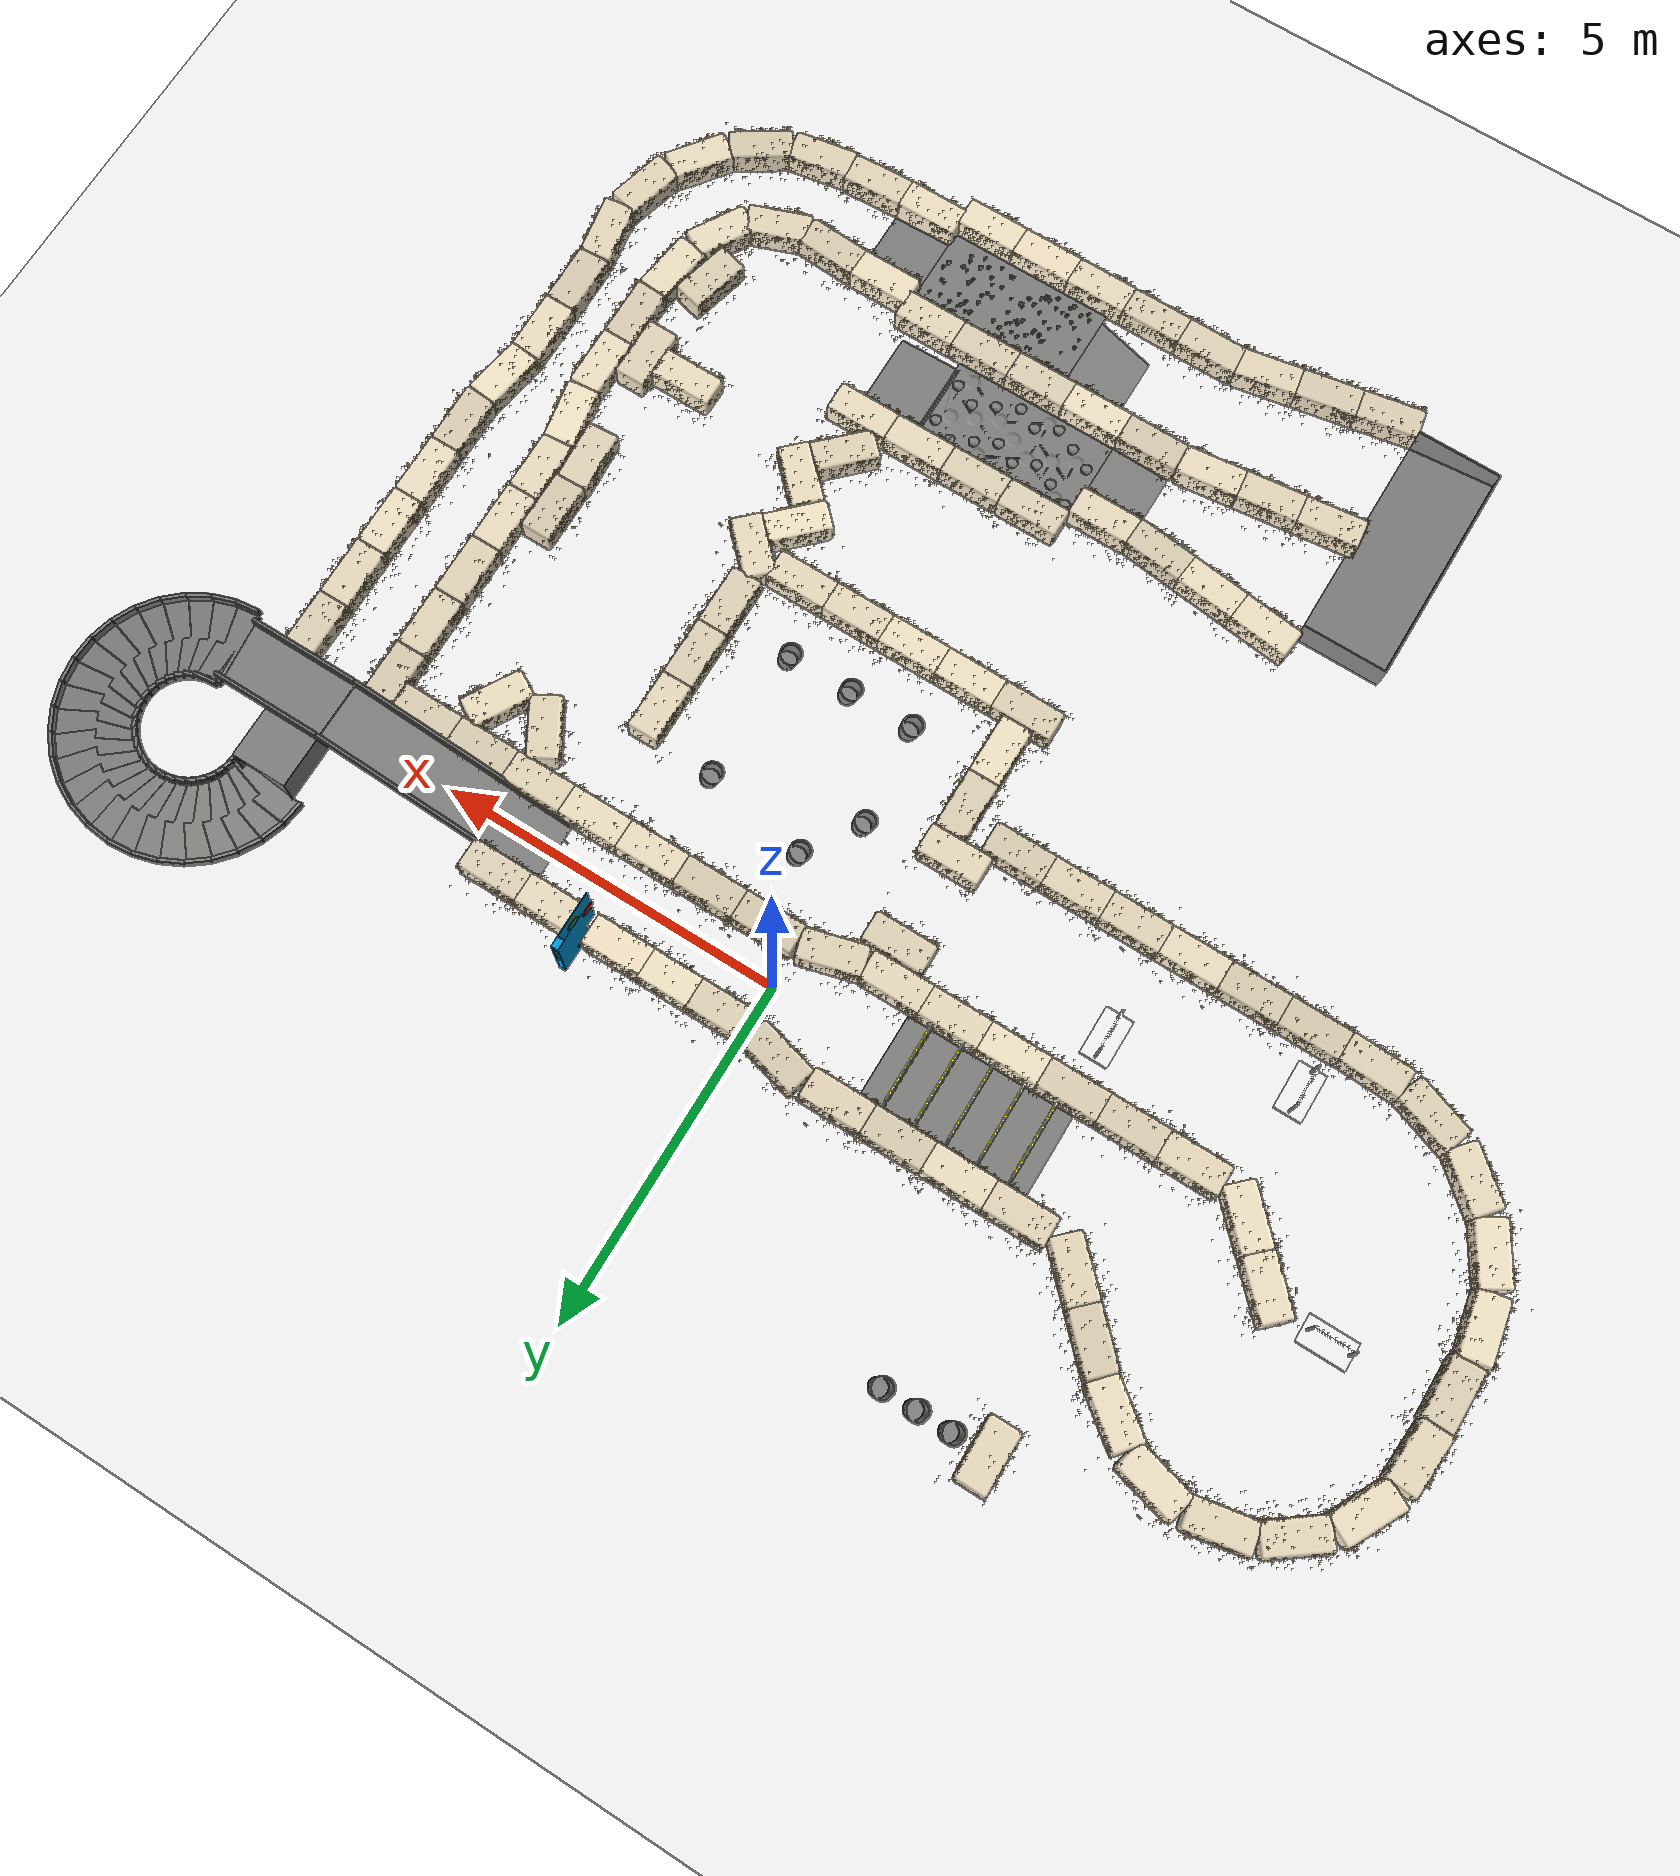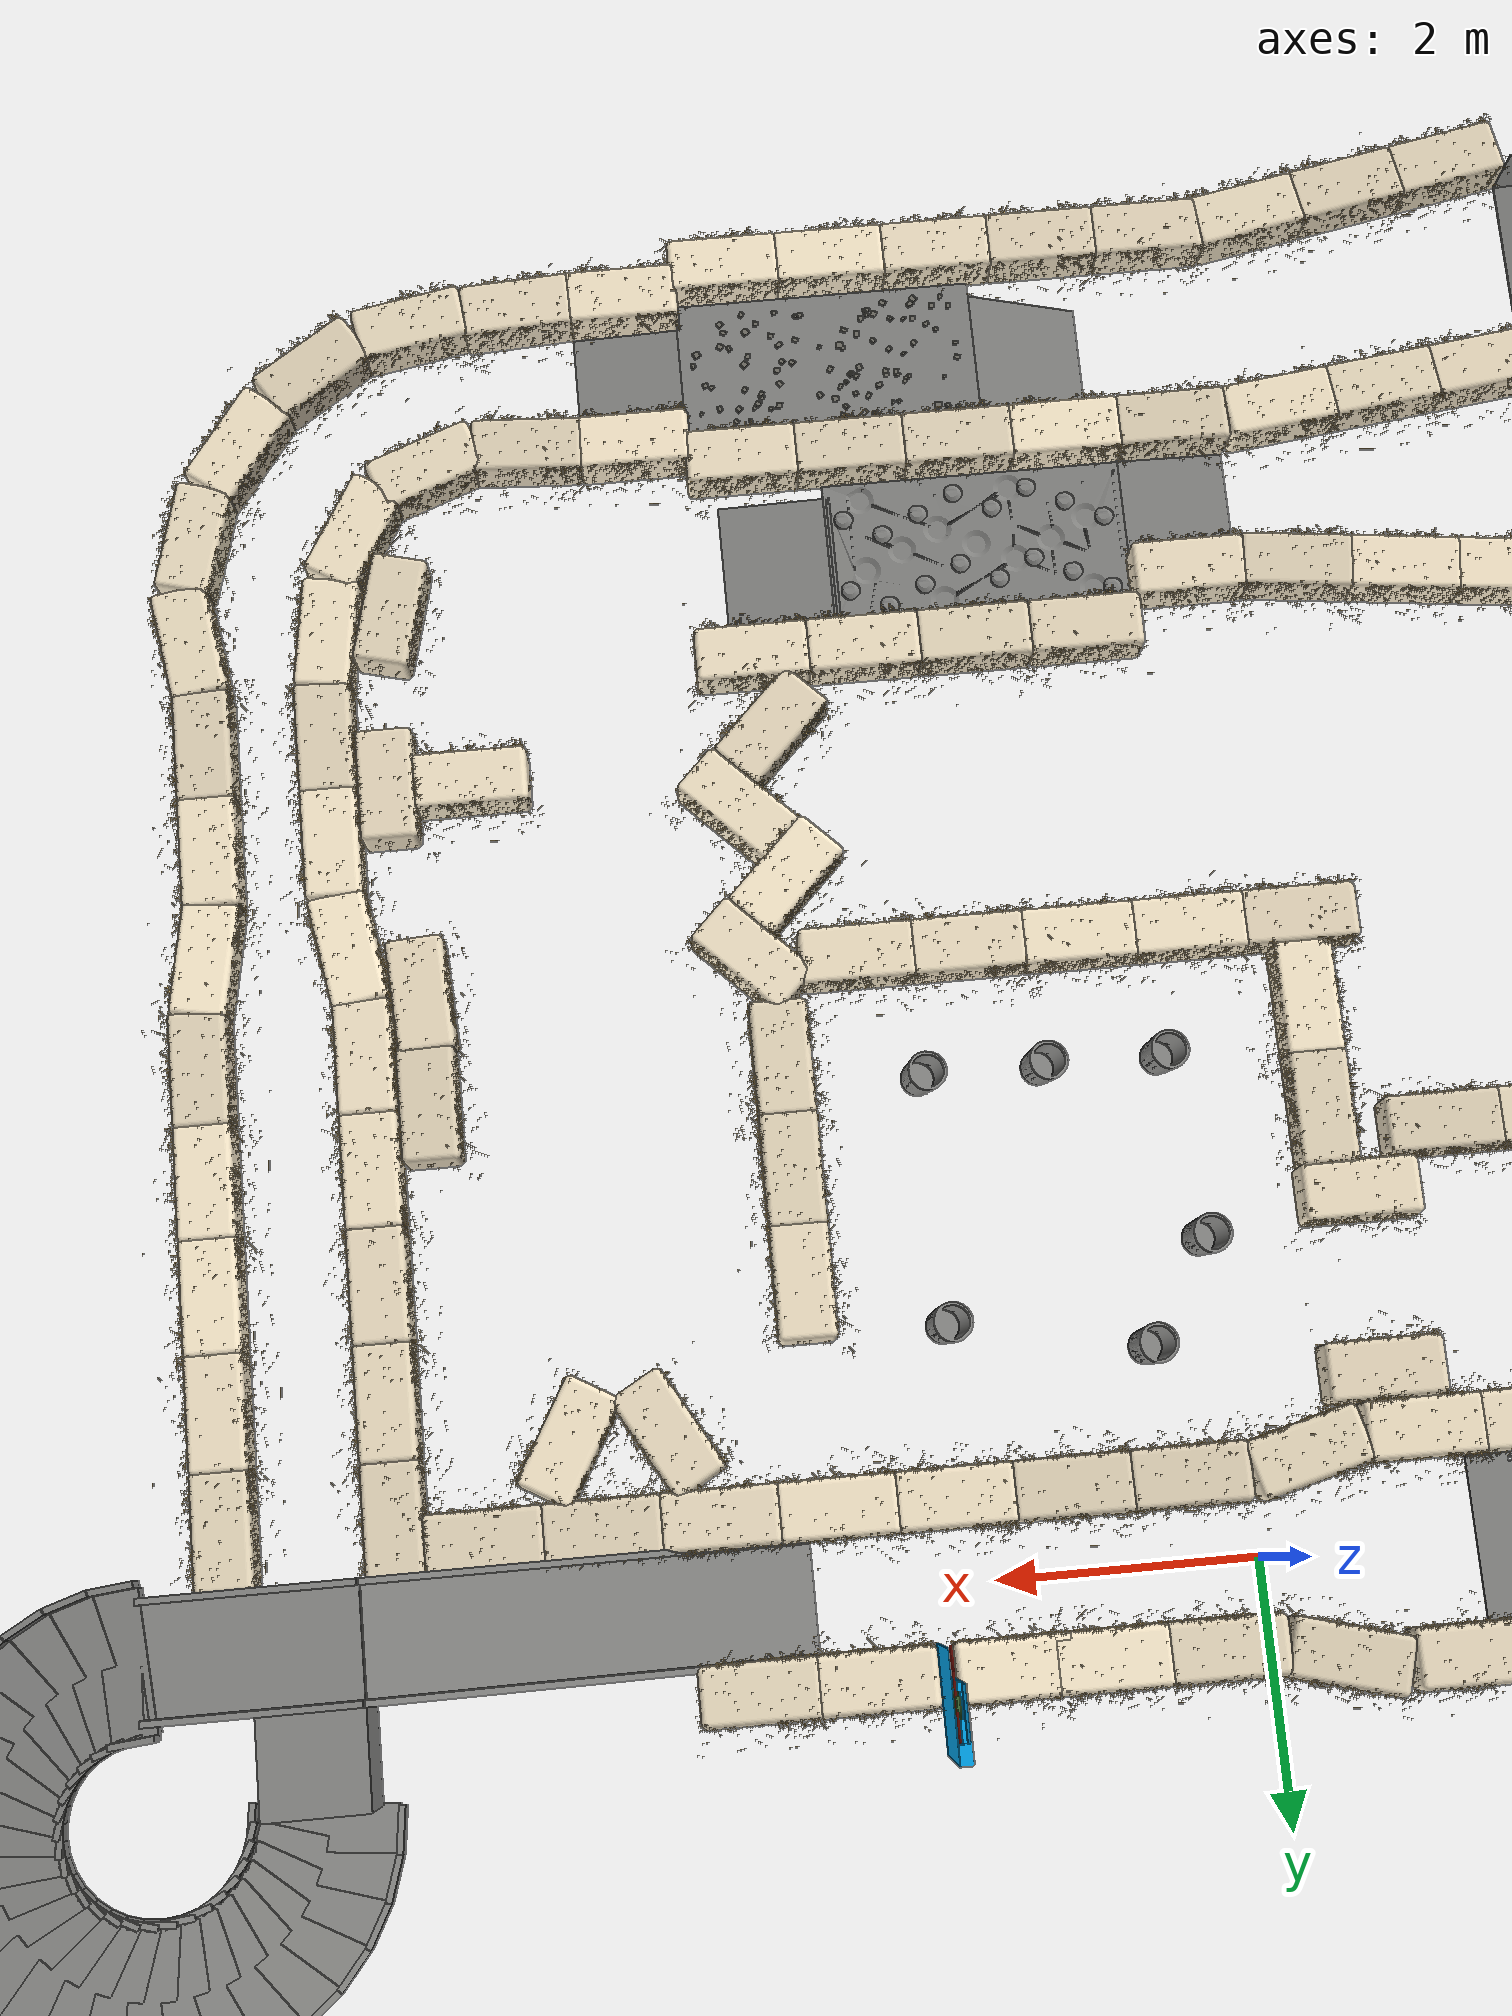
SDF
<sdf version="1.10">
 <world name="cfr_obstacle_course">
  <physics name="1ms" type="ignored">
   <max_step_size>0.001</max_step_size>
   <real_time_factor>1.0</real_time_factor>
  </physics>
  <plugin filename="gz-sim-physics-system" name="gz::sim::systems::Physics"/>
  <plugin filename="gz-sim-user-commands-system" name="gz::sim::systems::UserCommands"/>
  <plugin filename="gz-sim-scene-broadcaster-system" name="gz::sim::systems::SceneBroadcaster"/>
  <light type="directional" name="sun">
   <pose>0 0 20 0 0 0</pose>
   <diffuse>0.8 0.8 0.8 1</diffuse>
   <specular>0.2 0.2 0.2 1</specular>
   <direction>-0.4 0.2 -0.9</direction>
  </light>
  <model name="ground">
   <static>true</static>
   <pose>0.005 -4.540 0 0 0 0</pose>
   <link name="link">
    <collision name="collision">
     <geometry><plane><normal>0 0 1</normal><size>30 24</size></plane></geometry>
     <surface>
      <friction>
       <ode><mu>50</mu></ode>
       <bullet><friction>1</friction><rolling_friction>0.001</rolling_friction></bullet>
      </friction>
     </surface>
    </collision>
    <visual name="visual">
     <geometry><plane><normal>0 0 1</normal><size>30 24</size></plane></geometry>
     <material>
      <diffuse>1 1 1 1</diffuse>
      <pbr>
       <metal>
        <albedo_map>model://cfr_arduino_bridge/materials/asphalt_obstacle.png</albedo_map>
        <roughness>0.95</roughness>
        <metalness>0</metalness>
       </metal>
      </pbr>
     </material>
    </visual>
   </link>
  </model>
  <model name="course_bales">
   <static>true</static>
   <link name="link">
    <collision name="bale_0_collision">
     <pose>0.4820 -0.6423 0.1778 0.0000 0.0000 6.2832</pose>
     <geometry><box><size>0.9144 0.4572 0.3556</size></box></geometry>
     <surface>
      <friction>
       <ode><mu>0.2</mu><mu2>1.0</mu2><fdir1>0 0 1</fdir1></ode>
       <bullet><friction>0.2</friction><friction2>1.0</friction2></bullet>
      </friction>
     </surface>
    </collision>
    <visual name="bale_0_visual">
     <pose>0.4820 -0.6423 0.1778 0.0000 0.0000 6.2832</pose>
     <geometry><mesh><uri>model://cfr_arduino_bridge/meshes/straw_bale.obj</uri></mesh></geometry>
     <material>
      <diffuse>0.880 0.827 0.722 1</diffuse>
      <specular>0.04 0.04 0.03 1</specular>
      <pbr>
       <metal>
        <albedo_map>model://cfr_arduino_bridge/materials/straw_bale_0.png</albedo_map>
        <normal_map>model://cfr_arduino_bridge/materials/straw_bale_normal.png</normal_map>
        <roughness>0.95</roughness>
        <metalness>0</metalness>
       </metal>
      </pbr>
     </material>
    </visual>
    <visual name="bale_0_strands">
     <pose>0.4820 -0.6423 0.1778 0.0000 0.0000 6.2832</pose>
     <geometry><mesh><uri>model://cfr_arduino_bridge/meshes/bale_strands_0.stl</uri></mesh></geometry>
     <material><diffuse>0.74 0.63 0.40 1</diffuse><specular>0.05 0.05 0.04 1</specular></material>
     <cast_shadows>false</cast_shadows>
    </visual>
    <collision name="bale_1_collision">
     <pose>1.3663 -0.6423 0.1778 0.0000 0.0000 6.2832</pose>
     <geometry><box><size>0.9144 0.4572 0.3556</size></box></geometry>
     <surface>
      <friction>
       <ode><mu>0.2</mu><mu2>1.0</mu2><fdir1>0 0 1</fdir1></ode>
       <bullet><friction>0.2</friction><friction2>1.0</friction2></bullet>
      </friction>
     </surface>
    </collision>
    <visual name="bale_1_visual">
     <pose>1.3663 -0.6423 0.1778 0.0000 0.0000 6.2832</pose>
     <geometry><mesh><uri>model://cfr_arduino_bridge/meshes/straw_bale.obj</uri></mesh></geometry>
     <material>
      <diffuse>0.884 0.831 0.725 1</diffuse>
      <specular>0.04 0.04 0.03 1</specular>
      <pbr>
       <metal>
        <albedo_map>model://cfr_arduino_bridge/materials/straw_bale_1.png</albedo_map>
        <normal_map>model://cfr_arduino_bridge/materials/straw_bale_normal.png</normal_map>
        <roughness>0.95</roughness>
        <metalness>0</metalness>
       </metal>
      </pbr>
     </material>
    </visual>
    <visual name="bale_1_strands">
     <pose>1.3663 -0.6423 0.1778 0.0000 0.0000 6.2832</pose>
     <geometry><mesh><uri>model://cfr_arduino_bridge/meshes/bale_strands_1.stl</uri></mesh></geometry>
     <material><diffuse>0.74 0.63 0.40 1</diffuse><specular>0.05 0.05 0.04 1</specular></material>
     <cast_shadows>false</cast_shadows>
    </visual>
    <collision name="bale_2_collision">
     <pose>2.2506 -0.6423 0.1778 0.0000 0.0000 6.2832</pose>
     <geometry><box><size>0.9144 0.4572 0.3556</size></box></geometry>
     <surface>
      <friction>
       <ode><mu>0.2</mu><mu2>1.0</mu2><fdir1>0 0 1</fdir1></ode>
       <bullet><friction>0.2</friction><friction2>1.0</friction2></bullet>
      </friction>
     </surface>
    </collision>
    <visual name="bale_2_visual">
     <pose>2.2506 -0.6423 0.1778 0.0000 0.0000 6.2832</pose>
     <geometry><mesh><uri>model://cfr_arduino_bridge/meshes/straw_bale.obj</uri></mesh></geometry>
     <material>
      <diffuse>0.965 0.907 0.791 1</diffuse>
      <specular>0.04 0.04 0.03 1</specular>
      <pbr>
       <metal>
        <albedo_map>model://cfr_arduino_bridge/materials/straw_bale_1.png</albedo_map>
        <normal_map>model://cfr_arduino_bridge/materials/straw_bale_normal.png</normal_map>
        <roughness>0.95</roughness>
        <metalness>0</metalness>
       </metal>
      </pbr>
     </material>
    </visual>
    <visual name="bale_2_strands">
     <pose>2.2506 -0.6423 0.1778 0.0000 0.0000 6.2832</pose>
     <geometry><mesh><uri>model://cfr_arduino_bridge/meshes/bale_strands_3.stl</uri></mesh></geometry>
     <material><diffuse>0.74 0.63 0.40 1</diffuse><specular>0.05 0.05 0.04 1</specular></material>
     <cast_shadows>false</cast_shadows>
    </visual>
    <collision name="bale_3_collision">
     <pose>3.1349 -0.6423 0.1778 0.0000 0.0000 6.2832</pose>
     <geometry><box><size>0.9144 0.4572 0.3556</size></box></geometry>
     <surface>
      <friction>
       <ode><mu>0.2</mu><mu2>1.0</mu2><fdir1>0 0 1</fdir1></ode>
       <bullet><friction>0.2</friction><friction2>1.0</friction2></bullet>
      </friction>
     </surface>
    </collision>
    <visual name="bale_3_visual">
     <pose>3.1349 -0.6423 0.1778 0.0000 0.0000 6.2832</pose>
     <geometry><mesh><uri>model://cfr_arduino_bridge/meshes/straw_bale.obj</uri></mesh></geometry>
     <material>
      <diffuse>0.970 0.912 0.795 1</diffuse>
      <specular>0.04 0.04 0.03 1</specular>
      <pbr>
       <metal>
        <albedo_map>model://cfr_arduino_bridge/materials/straw_bale_2.png</albedo_map>
        <normal_map>model://cfr_arduino_bridge/materials/straw_bale_normal.png</normal_map>
        <roughness>0.95</roughness>
        <metalness>0</metalness>
       </metal>
      </pbr>
     </material>
    </visual>
    <visual name="bale_3_strands">
     <pose>3.1349 -0.6423 0.1778 0.0000 0.0000 6.2832</pose>
     <geometry><mesh><uri>model://cfr_arduino_bridge/meshes/bale_strands_1.stl</uri></mesh></geometry>
     <material><diffuse>0.74 0.63 0.40 1</diffuse><specular>0.05 0.05 0.04 1</specular></material>
     <cast_shadows>false</cast_shadows>
    </visual>
    <collision name="bale_4_collision">
     <pose>4.0192 -0.6423 0.1778 0.0000 0.0000 6.2832</pose>
     <geometry><box><size>0.9144 0.4572 0.3556</size></box></geometry>
     <surface>
      <friction>
       <ode><mu>0.2</mu><mu2>1.0</mu2><fdir1>0 0 1</fdir1></ode>
       <bullet><friction>0.2</friction><friction2>1.0</friction2></bullet>
      </friction>
     </surface>
    </collision>
    <visual name="bale_4_visual">
     <pose>4.0192 -0.6423 0.1778 0.0000 0.0000 6.2832</pose>
     <geometry><mesh><uri>model://cfr_arduino_bridge/meshes/straw_bale.obj</uri></mesh></geometry>
     <material>
      <diffuse>0.930 0.874 0.762 1</diffuse>
      <specular>0.04 0.04 0.03 1</specular>
      <pbr>
       <metal>
        <albedo_map>model://cfr_arduino_bridge/materials/straw_bale_2.png</albedo_map>
        <normal_map>model://cfr_arduino_bridge/materials/straw_bale_normal.png</normal_map>
        <roughness>0.95</roughness>
        <metalness>0</metalness>
       </metal>
      </pbr>
     </material>
    </visual>
    <visual name="bale_4_strands">
     <pose>4.0192 -0.6423 0.1778 0.0000 0.0000 6.2832</pose>
     <geometry><mesh><uri>model://cfr_arduino_bridge/meshes/bale_strands_2.stl</uri></mesh></geometry>
     <material><diffuse>0.74 0.63 0.40 1</diffuse><specular>0.05 0.05 0.04 1</specular></material>
     <cast_shadows>false</cast_shadows>
    </visual>
    <collision name="bale_5_collision">
     <pose>4.9035 -0.6423 0.1778 0.0000 0.0000 6.2832</pose>
     <geometry><box><size>0.9144 0.4572 0.3556</size></box></geometry>
     <surface>
      <friction>
       <ode><mu>0.2</mu><mu2>1.0</mu2><fdir1>0 0 1</fdir1></ode>
       <bullet><friction>0.2</friction><friction2>1.0</friction2></bullet>
      </friction>
     </surface>
    </collision>
    <visual name="bale_5_visual">
     <pose>4.9035 -0.6423 0.1778 0.0000 0.0000 6.2832</pose>
     <geometry><mesh><uri>model://cfr_arduino_bridge/meshes/straw_bale.obj</uri></mesh></geometry>
     <material>
      <diffuse>0.891 0.837 0.731 1</diffuse>
      <specular>0.04 0.04 0.03 1</specular>
      <pbr>
       <metal>
        <albedo_map>model://cfr_arduino_bridge/materials/straw_bale_2.png</albedo_map>
        <normal_map>model://cfr_arduino_bridge/materials/straw_bale_normal.png</normal_map>
        <roughness>0.95</roughness>
        <metalness>0</metalness>
       </metal>
      </pbr>
     </material>
    </visual>
    <visual name="bale_5_strands">
     <pose>4.9035 -0.6423 0.1778 0.0000 0.0000 6.2832</pose>
     <geometry><mesh><uri>model://cfr_arduino_bridge/meshes/bale_strands_0.stl</uri></mesh></geometry>
     <material><diffuse>0.74 0.63 0.40 1</diffuse><specular>0.05 0.05 0.04 1</specular></material>
     <cast_shadows>false</cast_shadows>
    </visual>
    <collision name="bale_6_collision">
     <pose>5.7878 -0.6423 0.1778 0.0000 0.0000 6.2832</pose>
     <geometry><box><size>0.9144 0.4572 0.3556</size></box></geometry>
     <surface>
      <friction>
       <ode><mu>0.2</mu><mu2>1.0</mu2><fdir1>0 0 1</fdir1></ode>
       <bullet><friction>0.2</friction><friction2>1.0</friction2></bullet>
      </friction>
     </surface>
    </collision>
    <visual name="bale_6_visual">
     <pose>5.7878 -0.6423 0.1778 0.0000 0.0000 6.2832</pose>
     <geometry><mesh><uri>model://cfr_arduino_bridge/meshes/straw_bale.obj</uri></mesh></geometry>
     <material>
      <diffuse>0.895 0.841 0.734 1</diffuse>
      <specular>0.04 0.04 0.03 1</specular>
      <pbr>
       <metal>
        <albedo_map>model://cfr_arduino_bridge/materials/straw_bale_0.png</albedo_map>
        <normal_map>model://cfr_arduino_bridge/materials/straw_bale_normal.png</normal_map>
        <roughness>0.95</roughness>
        <metalness>0</metalness>
       </metal>
      </pbr>
     </material>
    </visual>
    <visual name="bale_6_strands">
     <pose>5.7878 -0.6423 0.1778 0.0000 0.0000 6.2832</pose>
     <geometry><mesh><uri>model://cfr_arduino_bridge/meshes/bale_strands_2.stl</uri></mesh></geometry>
     <material><diffuse>0.74 0.63 0.40 1</diffuse><specular>0.05 0.05 0.04 1</specular></material>
     <cast_shadows>false</cast_shadows>
    </visual>
    <collision name="bale_7_collision">
     <pose>-7.1547 0.0042 0.1778 0.0000 0.0000 5.4897</pose>
     <geometry><box><size>0.9144 0.4572 0.3556</size></box></geometry>
     <surface>
      <friction>
       <ode><mu>0.2</mu><mu2>1.0</mu2><fdir1>0 0 1</fdir1></ode>
       <bullet><friction>0.2</friction><friction2>1.0</friction2></bullet>
      </friction>
     </surface>
    </collision>
    <visual name="bale_7_visual">
     <pose>-7.1547 0.0042 0.1778 0.0000 0.0000 5.4897</pose>
     <geometry><mesh><uri>model://cfr_arduino_bridge/meshes/straw_bale.obj</uri></mesh></geometry>
     <material>
      <diffuse>0.977 0.918 0.801 1</diffuse>
      <specular>0.04 0.04 0.03 1</specular>
      <pbr>
       <metal>
        <albedo_map>model://cfr_arduino_bridge/materials/straw_bale_0.png</albedo_map>
        <normal_map>model://cfr_arduino_bridge/materials/straw_bale_normal.png</normal_map>
        <roughness>0.95</roughness>
        <metalness>0</metalness>
       </metal>
      </pbr>
     </material>
    </visual>
    <visual name="bale_7_strands">
     <pose>-7.1547 0.0042 0.1778 0.0000 0.0000 5.4897</pose>
     <geometry><mesh><uri>model://cfr_arduino_bridge/meshes/bale_strands_3.stl</uri></mesh></geometry>
     <material><diffuse>0.74 0.63 0.40 1</diffuse><specular>0.05 0.05 0.04 1</specular></material>
     <cast_shadows>false</cast_shadows>
    </visual>
    <collision name="bale_8_collision">
     <pose>-6.5454 -0.6076 0.1778 0.0000 0.0000 5.4897</pose>
     <geometry><box><size>0.9144 0.4572 0.3556</size></box></geometry>
     <surface>
      <friction>
       <ode><mu>0.2</mu><mu2>1.0</mu2><fdir1>0 0 1</fdir1></ode>
       <bullet><friction>0.2</friction><friction2>1.0</friction2></bullet>
      </friction>
     </surface>
    </collision>
    <visual name="bale_8_visual">
     <pose>-6.5454 -0.6076 0.1778 0.0000 0.0000 5.4897</pose>
     <geometry><mesh><uri>model://cfr_arduino_bridge/meshes/straw_bale.obj</uri></mesh></geometry>
     <material>
      <diffuse>0.981 0.922 0.804 1</diffuse>
      <specular>0.04 0.04 0.03 1</specular>
      <pbr>
       <metal>
        <albedo_map>model://cfr_arduino_bridge/materials/straw_bale_1.png</albedo_map>
        <normal_map>model://cfr_arduino_bridge/materials/straw_bale_normal.png</normal_map>
        <roughness>0.95</roughness>
        <metalness>0</metalness>
       </metal>
      </pbr>
     </material>
    </visual>
    <visual name="bale_8_strands">
     <pose>-6.5454 -0.6076 0.1778 0.0000 0.0000 5.4897</pose>
     <geometry><mesh><uri>model://cfr_arduino_bridge/meshes/bale_strands_1.stl</uri></mesh></geometry>
     <material><diffuse>0.74 0.63 0.40 1</diffuse><specular>0.05 0.05 0.04 1</specular></material>
     <cast_shadows>false</cast_shadows>
    </visual>
    <collision name="bale_9_collision">
     <pose>-5.6457 -0.8411 0.1778 0.0000 0.0000 6.2832</pose>
     <geometry><box><size>0.9144 0.4572 0.3556</size></box></geometry>
     <surface>
      <friction>
       <ode><mu>0.2</mu><mu2>1.0</mu2><fdir1>0 0 1</fdir1></ode>
       <bullet><friction>0.2</friction><friction2>1.0</friction2></bullet>
      </friction>
     </surface>
    </collision>
    <visual name="bale_9_visual">
     <pose>-5.6457 -0.8411 0.1778 0.0000 0.0000 6.2832</pose>
     <geometry><mesh><uri>model://cfr_arduino_bridge/meshes/straw_bale.obj</uri></mesh></geometry>
     <material>
      <diffuse>0.942 0.885 0.772 1</diffuse>
      <specular>0.04 0.04 0.03 1</specular>
      <pbr>
       <metal>
        <albedo_map>model://cfr_arduino_bridge/materials/straw_bale_1.png</albedo_map>
        <normal_map>model://cfr_arduino_bridge/materials/straw_bale_normal.png</normal_map>
        <roughness>0.95</roughness>
        <metalness>0</metalness>
       </metal>
      </pbr>
     </material>
    </visual>
    <visual name="bale_9_strands">
     <pose>-5.6457 -0.8411 0.1778 0.0000 0.0000 6.2832</pose>
     <geometry><mesh><uri>model://cfr_arduino_bridge/meshes/bale_strands_3.stl</uri></mesh></geometry>
     <material><diffuse>0.74 0.63 0.40 1</diffuse><specular>0.05 0.05 0.04 1</specular></material>
     <cast_shadows>false</cast_shadows>
    </visual>
    <collision name="bale_10_collision">
     <pose>-4.7800 -0.8411 0.1778 0.0000 0.0000 6.2832</pose>
     <geometry><box><size>0.9144 0.4572 0.3556</size></box></geometry>
     <surface>
      <friction>
       <ode><mu>0.2</mu><mu2>1.0</mu2><fdir1>0 0 1</fdir1></ode>
       <bullet><friction>0.2</friction><friction2>1.0</friction2></bullet>
      </friction>
     </surface>
    </collision>
    <visual name="bale_10_visual">
     <pose>-4.7800 -0.8411 0.1778 0.0000 0.0000 6.2832</pose>
     <geometry><mesh><uri>model://cfr_arduino_bridge/meshes/straw_bale.obj</uri></mesh></geometry>
     <material>
      <diffuse>0.902 0.848 0.739 1</diffuse>
      <specular>0.04 0.04 0.03 1</specular>
      <pbr>
       <metal>
        <albedo_map>model://cfr_arduino_bridge/materials/straw_bale_1.png</albedo_map>
        <normal_map>model://cfr_arduino_bridge/materials/straw_bale_normal.png</normal_map>
        <roughness>0.95</roughness>
        <metalness>0</metalness>
       </metal>
      </pbr>
     </material>
    </visual>
    <visual name="bale_10_strands">
     <pose>-4.7800 -0.8411 0.1778 0.0000 0.0000 6.2832</pose>
     <geometry><mesh><uri>model://cfr_arduino_bridge/meshes/bale_strands_0.stl</uri></mesh></geometry>
     <material><diffuse>0.74 0.63 0.40 1</diffuse><specular>0.05 0.05 0.04 1</specular></material>
     <cast_shadows>false</cast_shadows>
    </visual>
    <collision name="bale_11_collision">
     <pose>-3.9143 -0.8411 0.1778 0.0000 0.0000 6.2832</pose>
     <geometry><box><size>0.9144 0.4572 0.3556</size></box></geometry>
     <surface>
      <friction>
       <ode><mu>0.2</mu><mu2>1.0</mu2><fdir1>0 0 1</fdir1></ode>
       <bullet><friction>0.2</friction><friction2>1.0</friction2></bullet>
      </friction>
     </surface>
    </collision>
    <visual name="bale_11_visual">
     <pose>-3.9143 -0.8411 0.1778 0.0000 0.0000 6.2832</pose>
     <geometry><mesh><uri>model://cfr_arduino_bridge/meshes/straw_bale.obj</uri></mesh></geometry>
     <material>
      <diffuse>0.907 0.852 0.743 1</diffuse>
      <specular>0.04 0.04 0.03 1</specular>
      <pbr>
       <metal>
        <albedo_map>model://cfr_arduino_bridge/materials/straw_bale_2.png</albedo_map>
        <normal_map>model://cfr_arduino_bridge/materials/straw_bale_normal.png</normal_map>
        <roughness>0.95</roughness>
        <metalness>0</metalness>
       </metal>
      </pbr>
     </material>
    </visual>
    <visual name="bale_11_strands">
     <pose>-3.9143 -0.8411 0.1778 0.0000 0.0000 6.2832</pose>
     <geometry><mesh><uri>model://cfr_arduino_bridge/meshes/bale_strands_2.stl</uri></mesh></geometry>
     <material><diffuse>0.74 0.63 0.40 1</diffuse><specular>0.05 0.05 0.04 1</specular></material>
     <cast_shadows>false</cast_shadows>
    </visual>
    <collision name="bale_12_collision">
     <pose>-3.0486 -0.8411 0.1778 0.0000 0.0000 6.2832</pose>
     <geometry><box><size>0.9144 0.4572 0.3556</size></box></geometry>
     <surface>
      <friction>
       <ode><mu>0.2</mu><mu2>1.0</mu2><fdir1>0 0 1</fdir1></ode>
       <bullet><friction>0.2</friction><friction2>1.0</friction2></bullet>
      </friction>
     </surface>
    </collision>
    <visual name="bale_12_visual">
     <pose>-3.0486 -0.8411 0.1778 0.0000 0.0000 6.2832</pose>
     <geometry><mesh><uri>model://cfr_arduino_bridge/meshes/straw_bale.obj</uri></mesh></geometry>
     <material>
      <diffuse>0.988 0.929 0.810 1</diffuse>
      <specular>0.04 0.04 0.03 1</specular>
      <pbr>
       <metal>
        <albedo_map>model://cfr_arduino_bridge/materials/straw_bale_2.png</albedo_map>
        <normal_map>model://cfr_arduino_bridge/materials/straw_bale_normal.png</normal_map>
        <roughness>0.95</roughness>
        <metalness>0</metalness>
       </metal>
      </pbr>
     </material>
    </visual>
    <visual name="bale_12_strands">
     <pose>-3.0486 -0.8411 0.1778 0.0000 0.0000 6.2832</pose>
     <geometry><mesh><uri>model://cfr_arduino_bridge/meshes/bale_strands_0.stl</uri></mesh></geometry>
     <material><diffuse>0.74 0.63 0.40 1</diffuse><specular>0.05 0.05 0.04 1</specular></material>
     <cast_shadows>false</cast_shadows>
    </visual>
    <collision name="bale_13_collision">
     <pose>-2.1850 -0.8411 0.1778 0.0000 0.0000 6.2832</pose>
     <geometry><box><size>0.9144 0.4572 0.3556</size></box></geometry>
     <surface>
      <friction>
       <ode><mu>0.2</mu><mu2>1.0</mu2><fdir1>0 0 1</fdir1></ode>
       <bullet><friction>0.2</friction><friction2>1.0</friction2></bullet>
      </friction>
     </surface>
    </collision>
    <visual name="bale_13_visual">
     <pose>-2.1850 -0.8411 0.1778 0.0000 0.0000 6.2832</pose>
     <geometry><mesh><uri>model://cfr_arduino_bridge/meshes/straw_bale.obj</uri></mesh></geometry>
     <material>
      <diffuse>0.949 0.892 0.778 1</diffuse>
      <specular>0.04 0.04 0.03 1</specular>
      <pbr>
       <metal>
        <albedo_map>model://cfr_arduino_bridge/materials/straw_bale_2.png</albedo_map>
        <normal_map>model://cfr_arduino_bridge/materials/straw_bale_normal.png</normal_map>
        <roughness>0.95</roughness>
        <metalness>0</metalness>
       </metal>
      </pbr>
     </material>
    </visual>
    <visual name="bale_13_strands">
     <pose>-2.1850 -0.8411 0.1778 0.0000 0.0000 6.2832</pose>
     <geometry><mesh><uri>model://cfr_arduino_bridge/meshes/bale_strands_1.stl</uri></mesh></geometry>
     <material><diffuse>0.74 0.63 0.40 1</diffuse><specular>0.05 0.05 0.04 1</specular></material>
     <cast_shadows>false</cast_shadows>
    </visual>
    <collision name="bale_14_collision">
     <pose>-1.3214 -0.8427 0.1778 0.0000 0.0000 6.2832</pose>
     <geometry><box><size>0.9144 0.4572 0.3556</size></box></geometry>
     <surface>
      <friction>
       <ode><mu>0.2</mu><mu2>1.0</mu2><fdir1>0 0 1</fdir1></ode>
       <bullet><friction>0.2</friction><friction2>1.0</friction2></bullet>
      </friction>
     </surface>
    </collision>
    <visual name="bale_14_visual">
     <pose>-1.3214 -0.8427 0.1778 0.0000 0.0000 6.2832</pose>
     <geometry><mesh><uri>model://cfr_arduino_bridge/meshes/straw_bale.obj</uri></mesh></geometry>
     <material>
      <diffuse>0.953 0.896 0.781 1</diffuse>
      <specular>0.04 0.04 0.03 1</specular>
      <pbr>
       <metal>
        <albedo_map>model://cfr_arduino_bridge/materials/straw_bale_0.png</albedo_map>
        <normal_map>model://cfr_arduino_bridge/materials/straw_bale_normal.png</normal_map>
        <roughness>0.95</roughness>
        <metalness>0</metalness>
       </metal>
      </pbr>
     </material>
    </visual>
    <visual name="bale_14_strands">
     <pose>-1.3214 -0.8427 0.1778 0.0000 0.0000 6.2832</pose>
     <geometry><mesh><uri>model://cfr_arduino_bridge/meshes/bale_strands_3.stl</uri></mesh></geometry>
     <material><diffuse>0.74 0.63 0.40 1</diffuse><specular>0.05 0.05 0.04 1</specular></material>
     <cast_shadows>false</cast_shadows>
    </visual>
    <collision name="bale_15_collision">
     <pose>-1.0832 -1.2999 0.1778 0.0000 0.0000 6.2832</pose>
     <geometry><box><size>0.9144 0.4572 0.3556</size></box></geometry>
     <surface>
      <friction>
       <ode><mu>0.2</mu><mu2>1.0</mu2><fdir1>0 0 1</fdir1></ode>
       <bullet><friction>0.2</friction><friction2>1.0</friction2></bullet>
      </friction>
     </surface>
    </collision>
    <visual name="bale_15_visual">
     <pose>-1.0832 -1.2999 0.1778 0.0000 0.0000 6.2832</pose>
     <geometry><mesh><uri>model://cfr_arduino_bridge/meshes/straw_bale.obj</uri></mesh></geometry>
     <material>
      <diffuse>0.914 0.859 0.749 1</diffuse>
      <specular>0.04 0.04 0.03 1</specular>
      <pbr>
       <metal>
        <albedo_map>model://cfr_arduino_bridge/materials/straw_bale_0.png</albedo_map>
        <normal_map>model://cfr_arduino_bridge/materials/straw_bale_normal.png</normal_map>
        <roughness>0.95</roughness>
        <metalness>0</metalness>
       </metal>
      </pbr>
     </material>
    </visual>
    <visual name="bale_15_strands">
     <pose>-1.0832 -1.2999 0.1778 0.0000 0.0000 6.2832</pose>
     <geometry><mesh><uri>model://cfr_arduino_bridge/meshes/bale_strands_1.stl</uri></mesh></geometry>
     <material><diffuse>0.74 0.63 0.40 1</diffuse><specular>0.05 0.05 0.04 1</specular></material>
     <cast_shadows>false</cast_shadows>
    </visual>
    <collision name="bale_16_collision">
     <pose>-0.4260 -0.7387 0.1778 0.0000 0.0000 0.2618</pose>
     <geometry><box><size>0.9144 0.4572 0.3556</size></box></geometry>
     <surface>
      <friction>
       <ode><mu>0.2</mu><mu2>1.0</mu2><fdir1>0 0 1</fdir1></ode>
       <bullet><friction>0.2</friction><friction2>1.0</friction2></bullet>
      </friction>
     </surface>
    </collision>
    <visual name="bale_16_visual">
     <pose>-0.4260 -0.7387 0.1778 0.0000 0.0000 0.2618</pose>
     <geometry><mesh><uri>model://cfr_arduino_bridge/meshes/straw_bale.obj</uri></mesh></geometry>
     <material>
      <diffuse>0.918 0.863 0.752 1</diffuse>
      <specular>0.04 0.04 0.03 1</specular>
      <pbr>
       <metal>
        <albedo_map>model://cfr_arduino_bridge/materials/straw_bale_1.png</albedo_map>
        <normal_map>model://cfr_arduino_bridge/materials/straw_bale_normal.png</normal_map>
        <roughness>0.95</roughness>
        <metalness>0</metalness>
       </metal>
      </pbr>
     </material>
    </visual>
    <visual name="bale_16_strands">
     <pose>-0.4260 -0.7387 0.1778 0.0000 0.0000 0.2618</pose>
     <geometry><mesh><uri>model://cfr_arduino_bridge/meshes/bale_strands_3.stl</uri></mesh></geometry>
     <material><diffuse>0.74 0.63 0.40 1</diffuse><specular>0.05 0.05 0.04 1</specular></material>
     <cast_shadows>false</cast_shadows>
    </visual>
    <collision name="bale_17_collision">
     <pose>6.5353 -5.2418 0.1778 0.0000 0.0000 1.7453</pose>
     <geometry><box><size>0.9144 0.4572 0.3556</size></box></geometry>
     <surface>
      <friction>
       <ode><mu>0.2</mu><mu2>1.0</mu2><fdir1>0 0 1</fdir1></ode>
       <bullet><friction>0.2</friction><friction2>1.0</friction2></bullet>
      </friction>
     </surface>
    </collision>
    <visual name="bale_17_visual">
     <pose>6.5353 -5.2418 0.1778 0.0000 0.0000 1.7453</pose>
     <geometry><mesh><uri>model://cfr_arduino_bridge/meshes/straw_bale.obj</uri></mesh></geometry>
     <material>
      <diffuse>1.000 0.940 0.820 1</diffuse>
      <specular>0.04 0.04 0.03 1</specular>
      <pbr>
       <metal>
        <albedo_map>model://cfr_arduino_bridge/materials/straw_bale_1.png</albedo_map>
        <normal_map>model://cfr_arduino_bridge/materials/straw_bale_normal.png</normal_map>
        <roughness>0.95</roughness>
        <metalness>0</metalness>
       </metal>
      </pbr>
     </material>
    </visual>
    <visual name="bale_17_strands">
     <pose>6.5353 -5.2418 0.1778 0.0000 0.0000 1.7453</pose>
     <geometry><mesh><uri>model://cfr_arduino_bridge/meshes/bale_strands_0.stl</uri></mesh></geometry>
     <material><diffuse>0.74 0.63 0.40 1</diffuse><specular>0.05 0.05 0.04 1</specular></material>
     <cast_shadows>false</cast_shadows>
    </visual>
    <collision name="bale_18_collision">
     <pose>6.4574 -4.3763 0.1778 0.0000 0.0000 1.5708</pose>
     <geometry><box><size>0.9144 0.4572 0.3556</size></box></geometry>
     <surface>
      <friction>
       <ode><mu>0.2</mu><mu2>1.0</mu2><fdir1>0 0 1</fdir1></ode>
       <bullet><friction>0.2</friction><friction2>1.0</friction2></bullet>
      </friction>
     </surface>
    </collision>
    <visual name="bale_18_visual">
     <pose>6.4574 -4.3763 0.1778 0.0000 0.0000 1.5708</pose>
     <geometry><mesh><uri>model://cfr_arduino_bridge/meshes/straw_bale.obj</uri></mesh></geometry>
     <material>
      <diffuse>0.960 0.902 0.787 1</diffuse>
      <specular>0.04 0.04 0.03 1</specular>
      <pbr>
       <metal>
        <albedo_map>model://cfr_arduino_bridge/materials/straw_bale_1.png</albedo_map>
        <normal_map>model://cfr_arduino_bridge/materials/straw_bale_normal.png</normal_map>
        <roughness>0.95</roughness>
        <metalness>0</metalness>
       </metal>
      </pbr>
     </material>
    </visual>
    <visual name="bale_18_strands">
     <pose>6.4574 -4.3763 0.1778 0.0000 0.0000 1.5708</pose>
     <geometry><mesh><uri>model://cfr_arduino_bridge/meshes/bale_strands_2.stl</uri></mesh></geometry>
     <material><diffuse>0.74 0.63 0.40 1</diffuse><specular>0.05 0.05 0.04 1</specular></material>
     <cast_shadows>false</cast_shadows>
    </visual>
    <collision name="bale_19_collision">
     <pose>6.4574 -3.4920 0.1778 0.0000 0.0000 1.5708</pose>
     <geometry><box><size>0.9144 0.4572 0.3556</size></box></geometry>
     <surface>
      <friction>
       <ode><mu>0.2</mu><mu2>1.0</mu2><fdir1>0 0 1</fdir1></ode>
       <bullet><friction>0.2</friction><friction2>1.0</friction2></bullet>
      </friction>
     </surface>
    </collision>
    <visual name="bale_19_visual">
     <pose>6.4574 -3.4920 0.1778 0.0000 0.0000 1.5708</pose>
     <geometry><mesh><uri>model://cfr_arduino_bridge/meshes/straw_bale.obj</uri></mesh></geometry>
     <material>
      <diffuse>0.965 0.907 0.791 1</diffuse>
      <specular>0.04 0.04 0.03 1</specular>
      <pbr>
       <metal>
        <albedo_map>model://cfr_arduino_bridge/materials/straw_bale_2.png</albedo_map>
        <normal_map>model://cfr_arduino_bridge/materials/straw_bale_normal.png</normal_map>
        <roughness>0.95</roughness>
        <metalness>0</metalness>
       </metal>
      </pbr>
     </material>
    </visual>
    <visual name="bale_19_strands">
     <pose>6.4574 -3.4920 0.1778 0.0000 0.0000 1.5708</pose>
     <geometry><mesh><uri>model://cfr_arduino_bridge/meshes/bale_strands_0.stl</uri></mesh></geometry>
     <material><diffuse>0.74 0.63 0.40 1</diffuse><specular>0.05 0.05 0.04 1</specular></material>
     <cast_shadows>false</cast_shadows>
    </visual>
    <collision name="bale_20_collision">
     <pose>6.4574 -2.6077 0.1778 0.0000 0.0000 1.5708</pose>
     <geometry><box><size>0.9144 0.4572 0.3556</size></box></geometry>
     <surface>
      <friction>
       <ode><mu>0.2</mu><mu2>1.0</mu2><fdir1>0 0 1</fdir1></ode>
       <bullet><friction>0.2</friction><friction2>1.0</friction2></bullet>
      </friction>
     </surface>
    </collision>
    <visual name="bale_20_visual">
     <pose>6.4574 -2.6077 0.1778 0.0000 0.0000 1.5708</pose>
     <geometry><mesh><uri>model://cfr_arduino_bridge/meshes/straw_bale.obj</uri></mesh></geometry>
     <material>
      <diffuse>0.925 0.869 0.758 1</diffuse>
      <specular>0.04 0.04 0.03 1</specular>
      <pbr>
       <metal>
        <albedo_map>model://cfr_arduino_bridge/materials/straw_bale_2.png</albedo_map>
        <normal_map>model://cfr_arduino_bridge/materials/straw_bale_normal.png</normal_map>
        <roughness>0.95</roughness>
        <metalness>0</metalness>
       </metal>
      </pbr>
     </material>
    </visual>
    <visual name="bale_20_strands">
     <pose>6.4574 -2.6077 0.1778 0.0000 0.0000 1.5708</pose>
     <geometry><mesh><uri>model://cfr_arduino_bridge/meshes/bale_strands_1.stl</uri></mesh></geometry>
     <material><diffuse>0.74 0.63 0.40 1</diffuse><specular>0.05 0.05 0.04 1</specular></material>
     <cast_shadows>false</cast_shadows>
    </visual>
    <collision name="bale_21_collision">
     <pose>6.4574 -1.7234 0.1778 0.0000 0.0000 1.5708</pose>
     <geometry><box><size>0.9144 0.4572 0.3556</size></box></geometry>
     <surface>
      <friction>
       <ode><mu>0.2</mu><mu2>1.0</mu2><fdir1>0 0 1</fdir1></ode>
       <bullet><friction>0.2</friction><friction2>1.0</friction2></bullet>
      </friction>
     </surface>
    </collision>
    <visual name="bale_21_visual">
     <pose>6.4574 -1.7234 0.1778 0.0000 0.0000 1.5708</pose>
     <geometry><mesh><uri>model://cfr_arduino_bridge/meshes/straw_bale.obj</uri></mesh></geometry>
     <material>
      <diffuse>0.928 0.873 0.761 1</diffuse>
      <specular>0.04 0.04 0.03 1</specular>
      <pbr>
       <metal>
        <albedo_map>model://cfr_arduino_bridge/materials/straw_bale_0.png</albedo_map>
        <normal_map>model://cfr_arduino_bridge/materials/straw_bale_normal.png</normal_map>
        <roughness>0.95</roughness>
        <metalness>0</metalness>
       </metal>
      </pbr>
     </material>
    </visual>
    <visual name="bale_21_strands">
     <pose>6.4574 -1.7234 0.1778 0.0000 0.0000 1.5708</pose>
     <geometry><mesh><uri>model://cfr_arduino_bridge/meshes/bale_strands_3.stl</uri></mesh></geometry>
     <material><diffuse>0.74 0.63 0.40 1</diffuse><specular>0.05 0.05 0.04 1</specular></material>
     <cast_shadows>false</cast_shadows>
    </visual>
    <collision name="bale_22_collision">
     <pose>6.4574 -0.8391 0.1778 0.0000 0.0000 1.5708</pose>
     <geometry><box><size>0.9144 0.4572 0.3556</size></box></geometry>
     <surface>
      <friction>
       <ode><mu>0.2</mu><mu2>1.0</mu2><fdir1>0 0 1</fdir1></ode>
       <bullet><friction>0.2</friction><friction2>1.0</friction2></bullet>
      </friction>
     </surface>
    </collision>
    <visual name="bale_22_visual">
     <pose>6.4574 -0.8391 0.1778 0.0000 0.0000 1.5708</pose>
     <geometry><mesh><uri>model://cfr_arduino_bridge/meshes/straw_bale.obj</uri></mesh></geometry>
     <material>
      <diffuse>0.890 0.836 0.730 1</diffuse>
      <specular>0.04 0.04 0.03 1</specular>
      <pbr>
       <metal>
        <albedo_map>model://cfr_arduino_bridge/materials/straw_bale_0.png</albedo_map>
        <normal_map>model://cfr_arduino_bridge/materials/straw_bale_normal.png</normal_map>
        <roughness>0.95</roughness>
        <metalness>0</metalness>
       </metal>
      </pbr>
     </material>
    </visual>
    <visual name="bale_22_strands">
     <pose>6.4574 -0.8391 0.1778 0.0000 0.0000 1.5708</pose>
     <geometry><mesh><uri>model://cfr_arduino_bridge/meshes/bale_strands_1.stl</uri></mesh></geometry>
     <material><diffuse>0.74 0.63 0.40 1</diffuse><specular>0.05 0.05 0.04 1</specular></material>
     <cast_shadows>false</cast_shadows>
    </visual>
    <collision name="bale_23_collision">
     <pose>6.2859 -8.6786 0.1778 0.0000 0.0000 1.0315</pose>
     <geometry><box><size>0.9144 0.4572 0.3556</size></box></geometry>
     <surface>
      <friction>
       <ode><mu>0.2</mu><mu2>1.0</mu2><fdir1>0 0 1</fdir1></ode>
       <bullet><friction>0.2</friction><friction2>1.0</friction2></bullet>
      </friction>
     </surface>
    </collision>
    <visual name="bale_23_visual">
     <pose>6.2859 -8.6786 0.1778 0.0000 0.0000 1.0315</pose>
     <geometry><mesh><uri>model://cfr_arduino_bridge/meshes/straw_bale.obj</uri></mesh></geometry>
     <material>
      <diffuse>0.971 0.913 0.796 1</diffuse>
      <specular>0.04 0.04 0.03 1</specular>
      <pbr>
       <metal>
        <albedo_map>model://cfr_arduino_bridge/materials/straw_bale_0.png</albedo_map>
        <normal_map>model://cfr_arduino_bridge/materials/straw_bale_normal.png</normal_map>
        <roughness>0.95</roughness>
        <metalness>0</metalness>
       </metal>
      </pbr>
     </material>
    </visual>
    <visual name="bale_23_strands">
     <pose>6.2859 -8.6786 0.1778 0.0000 0.0000 1.0315</pose>
     <geometry><mesh><uri>model://cfr_arduino_bridge/meshes/bale_strands_2.stl</uri></mesh></geometry>
     <material><diffuse>0.74 0.63 0.40 1</diffuse><specular>0.05 0.05 0.04 1</specular></material>
     <cast_shadows>false</cast_shadows>
    </visual>
    <collision name="bale_24_collision">
     <pose>6.5526 -7.8425 0.1778 0.0000 0.0000 1.4318</pose>
     <geometry><box><size>0.9144 0.4572 0.3556</size></box></geometry>
     <surface>
      <friction>
       <ode><mu>0.2</mu><mu2>1.0</mu2><fdir1>0 0 1</fdir1></ode>
       <bullet><friction>0.2</friction><friction2>1.0</friction2></bullet>
      </friction>
     </surface>
    </collision>
    <visual name="bale_24_visual">
     <pose>6.5526 -7.8425 0.1778 0.0000 0.0000 1.4318</pose>
     <geometry><mesh><uri>model://cfr_arduino_bridge/meshes/straw_bale.obj</uri></mesh></geometry>
     <material>
      <diffuse>0.976 0.917 0.800 1</diffuse>
      <specular>0.04 0.04 0.03 1</specular>
      <pbr>
       <metal>
        <albedo_map>model://cfr_arduino_bridge/materials/straw_bale_1.png</albedo_map>
        <normal_map>model://cfr_arduino_bridge/materials/straw_bale_normal.png</normal_map>
        <roughness>0.95</roughness>
        <metalness>0</metalness>
       </metal>
      </pbr>
     </material>
    </visual>
    <visual name="bale_24_strands">
     <pose>6.5526 -7.8425 0.1778 0.0000 0.0000 1.4318</pose>
     <geometry><mesh><uri>model://cfr_arduino_bridge/meshes/bale_strands_0.stl</uri></mesh></geometry>
     <material><diffuse>0.74 0.63 0.40 1</diffuse><specular>0.05 0.05 0.04 1</specular></material>
     <cast_shadows>false</cast_shadows>
    </visual>
    <collision name="bale_25_collision">
     <pose>5.6700 -9.1918 0.1778 0.0000 0.0000 0.3509</pose>
     <geometry><box><size>0.9144 0.4572 0.3556</size></box></geometry>
     <surface>
      <friction>
       <ode><mu>0.2</mu><mu2>1.0</mu2><fdir1>0 0 1</fdir1></ode>
       <bullet><friction>0.2</friction><friction2>1.0</friction2></bullet>
      </friction>
     </surface>
    </collision>
    <visual name="bale_25_visual">
     <pose>5.6700 -9.1918 0.1778 0.0000 0.0000 0.3509</pose>
     <geometry><mesh><uri>model://cfr_arduino_bridge/meshes/straw_bale.obj</uri></mesh></geometry>
     <material>
      <diffuse>0.936 0.880 0.767 1</diffuse>
      <specular>0.04 0.04 0.03 1</specular>
      <pbr>
       <metal>
        <albedo_map>model://cfr_arduino_bridge/materials/straw_bale_1.png</albedo_map>
        <normal_map>model://cfr_arduino_bridge/materials/straw_bale_normal.png</normal_map>
        <roughness>0.95</roughness>
        <metalness>0</metalness>
       </metal>
      </pbr>
     </material>
    </visual>
    <visual name="bale_25_strands">
     <pose>5.6700 -9.1918 0.1778 0.0000 0.0000 0.3509</pose>
     <geometry><mesh><uri>model://cfr_arduino_bridge/meshes/bale_strands_2.stl</uri></mesh></geometry>
     <material><diffuse>0.74 0.63 0.40 1</diffuse><specular>0.05 0.05 0.04 1</specular></material>
     <cast_shadows>false</cast_shadows>
    </visual>
    <collision name="bale_26_collision">
     <pose>4.8384 -9.2976 0.1778 0.0000 0.0000 6.2256</pose>
     <geometry><box><size>0.9144 0.4572 0.3556</size></box></geometry>
     <surface>
      <friction>
       <ode><mu>0.2</mu><mu2>1.0</mu2><fdir1>0 0 1</fdir1></ode>
       <bullet><friction>0.2</friction><friction2>1.0</friction2></bullet>
      </friction>
     </surface>
    </collision>
    <visual name="bale_26_visual">
     <pose>4.8384 -9.2976 0.1778 0.0000 0.0000 6.2256</pose>
     <geometry><mesh><uri>model://cfr_arduino_bridge/meshes/straw_bale.obj</uri></mesh></geometry>
     <material>
      <diffuse>0.897 0.843 0.736 1</diffuse>
      <specular>0.04 0.04 0.03 1</specular>
      <pbr>
       <metal>
        <albedo_map>model://cfr_arduino_bridge/materials/straw_bale_1.png</albedo_map>
        <normal_map>model://cfr_arduino_bridge/materials/straw_bale_normal.png</normal_map>
        <roughness>0.95</roughness>
        <metalness>0</metalness>
       </metal>
      </pbr>
     </material>
    </visual>
    <visual name="bale_26_strands">
     <pose>4.8384 -9.2976 0.1778 0.0000 0.0000 6.2256</pose>
     <geometry><mesh><uri>model://cfr_arduino_bridge/meshes/bale_strands_3.stl</uri></mesh></geometry>
     <material><diffuse>0.74 0.63 0.40 1</diffuse><specular>0.05 0.05 0.04 1</specular></material>
     <cast_shadows>false</cast_shadows>
    </visual>
    <collision name="bale_27_collision">
     <pose>6.6149 -6.9768 0.1778 0.0000 0.0000 1.5708</pose>
     <geometry><box><size>0.9144 0.4572 0.3556</size></box></geometry>
     <surface>
      <friction>
       <ode><mu>0.2</mu><mu2>1.0</mu2><fdir1>0 0 1</fdir1></ode>
       <bullet><friction>0.2</friction><friction2>1.0</friction2></bullet>
      </friction>
     </surface>
    </collision>
    <visual name="bale_27_visual">
     <pose>6.6149 -6.9768 0.1778 0.0000 0.0000 1.5708</pose>
     <geometry><mesh><uri>model://cfr_arduino_bridge/meshes/straw_bale.obj</uri></mesh></geometry>
     <material>
      <diffuse>0.901 0.847 0.738 1</diffuse>
      <specular>0.04 0.04 0.03 1</specular>
      <pbr>
       <metal>
        <albedo_map>model://cfr_arduino_bridge/materials/straw_bale_2.png</albedo_map>
        <normal_map>model://cfr_arduino_bridge/materials/straw_bale_normal.png</normal_map>
        <roughness>0.95</roughness>
        <metalness>0</metalness>
       </metal>
      </pbr>
     </material>
    </visual>
    <visual name="bale_27_strands">
     <pose>6.6149 -6.9768 0.1778 0.0000 0.0000 1.5708</pose>
     <geometry><mesh><uri>model://cfr_arduino_bridge/meshes/bale_strands_1.stl</uri></mesh></geometry>
     <material><diffuse>0.74 0.63 0.40 1</diffuse><specular>0.05 0.05 0.04 1</specular></material>
     <cast_shadows>false</cast_shadows>
    </visual>
    <collision name="bale_28_collision">
     <pose>6.6149 -6.1132 0.1778 0.0000 0.0000 1.5708</pose>
     <geometry><box><size>0.9144 0.4572 0.3556</size></box></geometry>
     <surface>
      <friction>
       <ode><mu>0.2</mu><mu2>1.0</mu2><fdir1>0 0 1</fdir1></ode>
       <bullet><friction>0.2</friction><friction2>1.0</friction2></bullet>
      </friction>
     </surface>
    </collision>
    <visual name="bale_28_visual">
     <pose>6.6149 -6.1132 0.1778 0.0000 0.0000 1.5708</pose>
     <geometry><mesh><uri>model://cfr_arduino_bridge/meshes/straw_bale.obj</uri></mesh></geometry>
     <material>
      <diffuse>0.983 0.924 0.806 1</diffuse>
      <specular>0.04 0.04 0.03 1</specular>
      <pbr>
       <metal>
        <albedo_map>model://cfr_arduino_bridge/materials/straw_bale_2.png</albedo_map>
        <normal_map>model://cfr_arduino_bridge/materials/straw_bale_normal.png</normal_map>
        <roughness>0.95</roughness>
        <metalness>0</metalness>
       </metal>
      </pbr>
     </material>
    </visual>
    <visual name="bale_28_strands">
     <pose>6.6149 -6.1132 0.1778 0.0000 0.0000 1.5708</pose>
     <geometry><mesh><uri>model://cfr_arduino_bridge/meshes/bale_strands_3.stl</uri></mesh></geometry>
     <material><diffuse>0.74 0.63 0.40 1</diffuse><specular>0.05 0.05 0.04 1</specular></material>
     <cast_shadows>false</cast_shadows>
    </visual>
    <collision name="bale_29_collision">
     <pose>3.9745 -9.2717 0.1778 0.0000 0.0000 6.2832</pose>
     <geometry><box><size>0.9144 0.4572 0.3556</size></box></geometry>
     <surface>
      <friction>
       <ode><mu>0.2</mu><mu2>1.0</mu2><fdir1>0 0 1</fdir1></ode>
       <bullet><friction>0.2</friction><friction2>1.0</friction2></bullet>
      </friction>
     </surface>
    </collision>
    <visual name="bale_29_visual">
     <pose>3.9745 -9.2717 0.1778 0.0000 0.0000 6.2832</pose>
     <geometry><mesh><uri>model://cfr_arduino_bridge/meshes/straw_bale.obj</uri></mesh></geometry>
     <material>
      <diffuse>0.987 0.927 0.809 1</diffuse>
      <specular>0.04 0.04 0.03 1</specular>
      <pbr>
       <metal>
        <albedo_map>model://cfr_arduino_bridge/materials/straw_bale_0.png</albedo_map>
        <normal_map>model://cfr_arduino_bridge/materials/straw_bale_normal.png</normal_map>
        <roughness>0.95</roughness>
        <metalness>0</metalness>
       </metal>
      </pbr>
     </material>
    </visual>
    <visual name="bale_29_strands">
     <pose>3.9745 -9.2717 0.1778 0.0000 0.0000 6.2832</pose>
     <geometry><mesh><uri>model://cfr_arduino_bridge/meshes/bale_strands_1.stl</uri></mesh></geometry>
     <material><diffuse>0.74 0.63 0.40 1</diffuse><specular>0.05 0.05 0.04 1</specular></material>
     <cast_shadows>false</cast_shadows>
    </visual>
    <collision name="bale_30_collision">
     <pose>3.1095 -9.0682 0.1778 0.0000 0.0000 6.2832</pose>
     <geometry><box><size>0.9144 0.4572 0.3556</size></box></geometry>
     <surface>
      <friction>
       <ode><mu>0.2</mu><mu2>1.0</mu2><fdir1>0 0 1</fdir1></ode>
       <bullet><friction>0.2</friction><friction2>1.0</friction2></bullet>
      </friction>
     </surface>
    </collision>
    <visual name="bale_30_visual">
     <pose>3.1095 -9.0682 0.1778 0.0000 0.0000 6.2832</pose>
     <geometry><mesh><uri>model://cfr_arduino_bridge/meshes/straw_bale.obj</uri></mesh></geometry>
     <material>
      <diffuse>0.948 0.891 0.777 1</diffuse>
      <specular>0.04 0.04 0.03 1</specular>
      <pbr>
       <metal>
        <albedo_map>model://cfr_arduino_bridge/materials/straw_bale_0.png</albedo_map>
        <normal_map>model://cfr_arduino_bridge/materials/straw_bale_normal.png</normal_map>
        <roughness>0.95</roughness>
        <metalness>0</metalness>
       </metal>
      </pbr>
     </material>
    </visual>
    <visual name="bale_30_strands">
     <pose>3.1095 -9.0682 0.1778 0.0000 0.0000 6.2832</pose>
     <geometry><mesh><uri>model://cfr_arduino_bridge/meshes/bale_strands_2.stl</uri></mesh></geometry>
     <material><diffuse>0.74 0.63 0.40 1</diffuse><specular>0.05 0.05 0.04 1</specular></material>
     <cast_shadows>false</cast_shadows>
    </visual>
    <collision name="bale_31_collision">
     <pose>2.2294 -9.0672 0.1778 0.0000 0.0000 6.2832</pose>
     <geometry><box><size>0.9144 0.4572 0.3556</size></box></geometry>
     <surface>
      <friction>
       <ode><mu>0.2</mu><mu2>1.0</mu2><fdir1>0 0 1</fdir1></ode>
       <bullet><friction>0.2</friction><friction2>1.0</friction2></bullet>
      </friction>
     </surface>
    </collision>
    <visual name="bale_31_visual">
     <pose>2.2294 -9.0672 0.1778 0.0000 0.0000 6.2832</pose>
     <geometry><mesh><uri>model://cfr_arduino_bridge/meshes/straw_bale.obj</uri></mesh></geometry>
     <material>
      <diffuse>0.908 0.853 0.744 1</diffuse>
      <specular>0.04 0.04 0.03 1</specular>
      <pbr>
       <metal>
        <albedo_map>model://cfr_arduino_bridge/materials/straw_bale_0.png</albedo_map>
        <normal_map>model://cfr_arduino_bridge/materials/straw_bale_normal.png</normal_map>
        <roughness>0.95</roughness>
        <metalness>0</metalness>
       </metal>
      </pbr>
     </material>
    </visual>
    <visual name="bale_31_strands">
     <pose>2.2294 -9.0672 0.1778 0.0000 0.0000 6.2832</pose>
     <geometry><mesh><uri>model://cfr_arduino_bridge/meshes/bale_strands_0.stl</uri></mesh></geometry>
     <material><diffuse>0.74 0.63 0.40 1</diffuse><specular>0.05 0.05 0.04 1</specular></material>
     <cast_shadows>false</cast_shadows>
    </visual>
    <collision name="bale_32_collision">
     <pose>1.3494 -9.0672 0.1778 0.0000 0.0000 6.2832</pose>
     <geometry><box><size>0.9144 0.4572 0.3556</size></box></geometry>
     <surface>
      <friction>
       <ode><mu>0.2</mu><mu2>1.0</mu2><fdir1>0 0 1</fdir1></ode>
       <bullet><friction>0.2</friction><friction2>1.0</friction2></bullet>
      </friction>
     </surface>
    </collision>
    <visual name="bale_32_visual">
     <pose>1.3494 -9.0672 0.1778 0.0000 0.0000 6.2832</pose>
     <geometry><mesh><uri>model://cfr_arduino_bridge/meshes/straw_bale.obj</uri></mesh></geometry>
     <material>
      <diffuse>0.913 0.858 0.748 1</diffuse>
      <specular>0.04 0.04 0.03 1</specular>
      <pbr>
       <metal>
        <albedo_map>model://cfr_arduino_bridge/materials/straw_bale_1.png</albedo_map>
        <normal_map>model://cfr_arduino_bridge/materials/straw_bale_normal.png</normal_map>
        <roughness>0.95</roughness>
        <metalness>0</metalness>
       </metal>
      </pbr>
     </material>
    </visual>
    <visual name="bale_32_strands">
     <pose>1.3494 -9.0672 0.1778 0.0000 0.0000 6.2832</pose>
     <geometry><mesh><uri>model://cfr_arduino_bridge/meshes/bale_strands_2.stl</uri></mesh></geometry>
     <material><diffuse>0.74 0.63 0.40 1</diffuse><specular>0.05 0.05 0.04 1</specular></material>
     <cast_shadows>false</cast_shadows>
    </visual>
    <collision name="bale_33_collision">
     <pose>0.4693 -9.0672 0.1778 0.0000 0.0000 6.2832</pose>
     <geometry><box><size>0.9144 0.4572 0.3556</size></box></geometry>
     <surface>
      <friction>
       <ode><mu>0.2</mu><mu2>1.0</mu2><fdir1>0 0 1</fdir1></ode>
       <bullet><friction>0.2</friction><friction2>1.0</friction2></bullet>
      </friction>
     </surface>
    </collision>
    <visual name="bale_33_visual">
     <pose>0.4693 -9.0672 0.1778 0.0000 0.0000 6.2832</pose>
     <geometry><mesh><uri>model://cfr_arduino_bridge/meshes/straw_bale.obj</uri></mesh></geometry>
     <material>
      <diffuse>0.994 0.934 0.815 1</diffuse>
      <specular>0.04 0.04 0.03 1</specular>
      <pbr>
       <metal>
        <albedo_map>model://cfr_arduino_bridge/materials/straw_bale_1.png</albedo_map>
        <normal_map>model://cfr_arduino_bridge/materials/straw_bale_normal.png</normal_map>
        <roughness>0.95</roughness>
        <metalness>0</metalness>
       </metal>
      </pbr>
     </material>
    </visual>
    <visual name="bale_33_strands">
     <pose>0.4693 -9.0672 0.1778 0.0000 0.0000 6.2832</pose>
     <geometry><mesh><uri>model://cfr_arduino_bridge/meshes/bale_strands_3.stl</uri></mesh></geometry>
     <material><diffuse>0.74 0.63 0.40 1</diffuse><specular>0.05 0.05 0.04 1</specular></material>
     <cast_shadows>false</cast_shadows>
    </visual>
    <collision name="bale_34_collision">
     <pose>-0.3947 -7.7930 0.1778 0.0000 0.0000 6.2832</pose>
     <geometry><box><size>0.9144 0.4572 0.3556</size></box></geometry>
     <surface>
      <friction>
       <ode><mu>0.2</mu><mu2>1.0</mu2><fdir1>0 0 1</fdir1></ode>
       <bullet><friction>0.2</friction><friction2>1.0</friction2></bullet>
      </friction>
     </surface>
    </collision>
    <visual name="bale_34_visual">
     <pose>-0.3947 -7.7930 0.1778 0.0000 0.0000 6.2832</pose>
     <geometry><mesh><uri>model://cfr_arduino_bridge/meshes/straw_bale.obj</uri></mesh></geometry>
     <material>
      <diffuse>0.955 0.898 0.783 1</diffuse>
      <specular>0.04 0.04 0.03 1</specular>
      <pbr>
       <metal>
        <albedo_map>model://cfr_arduino_bridge/materials/straw_bale_1.png</albedo_map>
        <normal_map>model://cfr_arduino_bridge/materials/straw_bale_normal.png</normal_map>
        <roughness>0.95</roughness>
        <metalness>0</metalness>
       </metal>
      </pbr>
     </material>
    </visual>
    <visual name="bale_34_strands">
     <pose>-0.3947 -7.7930 0.1778 0.0000 0.0000 6.2832</pose>
     <geometry><mesh><uri>model://cfr_arduino_bridge/meshes/bale_strands_1.stl</uri></mesh></geometry>
     <material><diffuse>0.74 0.63 0.40 1</diffuse><specular>0.05 0.05 0.04 1</specular></material>
     <cast_shadows>false</cast_shadows>
    </visual>
    <collision name="bale_35_collision">
     <pose>2.2812 -7.3832 0.1778 0.0000 0.0000 6.2832</pose>
     <geometry><box><size>0.9144 0.4572 0.3556</size></box></geometry>
     <surface>
      <friction>
       <ode><mu>0.2</mu><mu2>1.0</mu2><fdir1>0 0 1</fdir1></ode>
       <bullet><friction>0.2</friction><friction2>1.0</friction2></bullet>
      </friction>
     </surface>
    </collision>
    <visual name="bale_35_visual">
     <pose>2.2812 -7.3832 0.1778 0.0000 0.0000 6.2832</pose>
     <geometry><mesh><uri>model://cfr_arduino_bridge/meshes/straw_bale.obj</uri></mesh></geometry>
     <material>
      <diffuse>0.959 0.901 0.786 1</diffuse>
      <specular>0.04 0.04 0.03 1</specular>
      <pbr>
       <metal>
        <albedo_map>model://cfr_arduino_bridge/materials/straw_bale_2.png</albedo_map>
        <normal_map>model://cfr_arduino_bridge/materials/straw_bale_normal.png</normal_map>
        <roughness>0.95</roughness>
        <metalness>0</metalness>
       </metal>
      </pbr>
     </material>
    </visual>
    <visual name="bale_35_strands">
     <pose>2.2812 -7.3832 0.1778 0.0000 0.0000 6.2832</pose>
     <geometry><mesh><uri>model://cfr_arduino_bridge/meshes/bale_strands_3.stl</uri></mesh></geometry>
     <material><diffuse>0.74 0.63 0.40 1</diffuse><specular>0.05 0.05 0.04 1</specular></material>
     <cast_shadows>false</cast_shadows>
    </visual>
    <collision name="bale_36_collision">
     <pose>1.3880 -7.3832 0.1778 0.0000 0.0000 6.2832</pose>
     <geometry><box><size>0.9144 0.4572 0.3556</size></box></geometry>
     <surface>
      <friction>
       <ode><mu>0.2</mu><mu2>1.0</mu2><fdir1>0 0 1</fdir1></ode>
       <bullet><friction>0.2</friction><friction2>1.0</friction2></bullet>
      </friction>
     </surface>
    </collision>
    <visual name="bale_36_visual">
     <pose>1.3880 -7.3832 0.1778 0.0000 0.0000 6.2832</pose>
     <geometry><mesh><uri>model://cfr_arduino_bridge/meshes/straw_bale.obj</uri></mesh></geometry>
     <material>
      <diffuse>0.920 0.865 0.754 1</diffuse>
      <specular>0.04 0.04 0.03 1</specular>
      <pbr>
       <metal>
        <albedo_map>model://cfr_arduino_bridge/materials/straw_bale_2.png</albedo_map>
        <normal_map>model://cfr_arduino_bridge/materials/straw_bale_normal.png</normal_map>
        <roughness>0.95</roughness>
        <metalness>0</metalness>
       </metal>
      </pbr>
     </material>
    </visual>
    <visual name="bale_36_strands">
     <pose>1.3880 -7.3832 0.1778 0.0000 0.0000 6.2832</pose>
     <geometry><mesh><uri>model://cfr_arduino_bridge/meshes/bale_strands_0.stl</uri></mesh></geometry>
     <material><diffuse>0.74 0.63 0.40 1</diffuse><specular>0.05 0.05 0.04 1</specular></material>
     <cast_shadows>false</cast_shadows>
    </visual>
    <collision name="bale_37_collision">
     <pose>0.4947 -7.3832 0.1778 0.0000 0.0000 6.2832</pose>
     <geometry><box><size>0.9144 0.4572 0.3556</size></box></geometry>
     <surface>
      <friction>
       <ode><mu>0.2</mu><mu2>1.0</mu2><fdir1>0 0 1</fdir1></ode>
       <bullet><friction>0.2</friction><friction2>1.0</friction2></bullet>
      </friction>
     </surface>
    </collision>
    <visual name="bale_37_visual">
     <pose>0.4947 -7.3832 0.1778 0.0000 0.0000 6.2832</pose>
     <geometry><mesh><uri>model://cfr_arduino_bridge/meshes/straw_bale.obj</uri></mesh></geometry>
     <material>
      <diffuse>0.924 0.868 0.757 1</diffuse>
      <specular>0.04 0.04 0.03 1</specular>
      <pbr>
       <metal>
        <albedo_map>model://cfr_arduino_bridge/materials/straw_bale_0.png</albedo_map>
        <normal_map>model://cfr_arduino_bridge/materials/straw_bale_normal.png</normal_map>
        <roughness>0.95</roughness>
        <metalness>0</metalness>
       </metal>
      </pbr>
     </material>
    </visual>
    <visual name="bale_37_strands">
     <pose>0.4947 -7.3832 0.1778 0.0000 0.0000 6.2832</pose>
     <geometry><mesh><uri>model://cfr_arduino_bridge/meshes/bale_strands_2.stl</uri></mesh></geometry>
     <material><diffuse>0.74 0.63 0.40 1</diffuse><specular>0.05 0.05 0.04 1</specular></material>
     <cast_shadows>false</cast_shadows>
    </visual>
    <collision name="bale_38_collision">
     <pose>-0.4068 -9.0672 0.1778 0.0000 0.0000 6.2832</pose>
     <geometry><box><size>0.9144 0.4572 0.3556</size></box></geometry>
     <surface>
      <friction>
       <ode><mu>0.2</mu><mu2>1.0</mu2><fdir1>0 0 1</fdir1></ode>
       <bullet><friction>0.2</friction><friction2>1.0</friction2></bullet>
      </friction>
     </surface>
    </collision>
    <visual name="bale_38_visual">
     <pose>-0.4068 -9.0672 0.1778 0.0000 0.0000 6.2832</pose>
     <geometry><mesh><uri>model://cfr_arduino_bridge/meshes/straw_bale.obj</uri></mesh></geometry>
     <material>
      <diffuse>0.885 0.832 0.726 1</diffuse>
      <specular>0.04 0.04 0.03 1</specular>
      <pbr>
       <metal>
        <albedo_map>model://cfr_arduino_bridge/materials/straw_bale_0.png</albedo_map>
        <normal_map>model://cfr_arduino_bridge/materials/straw_bale_normal.png</normal_map>
        <roughness>0.95</roughness>
        <metalness>0</metalness>
       </metal>
      </pbr>
     </material>
    </visual>
    <visual name="bale_38_strands">
     <pose>-0.4068 -9.0672 0.1778 0.0000 0.0000 6.2832</pose>
     <geometry><mesh><uri>model://cfr_arduino_bridge/meshes/bale_strands_0.stl</uri></mesh></geometry>
     <material><diffuse>0.74 0.63 0.40 1</diffuse><specular>0.05 0.05 0.04 1</specular></material>
     <cast_shadows>false</cast_shadows>
    </visual>
    <collision name="bale_39_collision">
     <pose>3.1744 -7.3832 0.1778 0.0000 0.0000 6.2832</pose>
     <geometry><box><size>0.9144 0.4572 0.3556</size></box></geometry>
     <surface>
      <friction>
       <ode><mu>0.2</mu><mu2>1.0</mu2><fdir1>0 0 1</fdir1></ode>
       <bullet><friction>0.2</friction><friction2>1.0</friction2></bullet>
      </friction>
     </surface>
    </collision>
    <visual name="bale_39_visual">
     <pose>3.1744 -7.3832 0.1778 0.0000 0.0000 6.2832</pose>
     <geometry><mesh><uri>model://cfr_arduino_bridge/meshes/straw_bale.obj</uri></mesh></geometry>
     <material>
      <diffuse>0.966 0.908 0.792 1</diffuse>
      <specular>0.04 0.04 0.03 1</specular>
      <pbr>
       <metal>
        <albedo_map>model://cfr_arduino_bridge/materials/straw_bale_0.png</albedo_map>
        <normal_map>model://cfr_arduino_bridge/materials/straw_bale_normal.png</normal_map>
        <roughness>0.95</roughness>
        <metalness>0</metalness>
       </metal>
      </pbr>
     </material>
    </visual>
    <visual name="bale_39_strands">
     <pose>3.1744 -7.3832 0.1778 0.0000 0.0000 6.2832</pose>
     <geometry><mesh><uri>model://cfr_arduino_bridge/meshes/bale_strands_1.stl</uri></mesh></geometry>
     <material><diffuse>0.74 0.63 0.40 1</diffuse><specular>0.05 0.05 0.04 1</specular></material>
     <cast_shadows>false</cast_shadows>
    </visual>
    <collision name="bale_40_collision">
     <pose>-1.3014 -9.1204 0.1778 0.0000 0.0000 0.1193</pose>
     <geometry><box><size>0.9144 0.4572 0.3556</size></box></geometry>
     <surface>
      <friction>
       <ode><mu>0.2</mu><mu2>1.0</mu2><fdir1>0 0 1</fdir1></ode>
       <bullet><friction>0.2</friction><friction2>1.0</friction2></bullet>
      </friction>
     </surface>
    </collision>
    <visual name="bale_40_visual">
     <pose>-1.3014 -9.1204 0.1778 0.0000 0.0000 0.1193</pose>
     <geometry><mesh><uri>model://cfr_arduino_bridge/meshes/straw_bale.obj</uri></mesh></geometry>
     <material>
      <diffuse>0.971 0.913 0.796 1</diffuse>
      <specular>0.04 0.04 0.03 1</specular>
      <pbr>
       <metal>
        <albedo_map>model://cfr_arduino_bridge/materials/straw_bale_1.png</albedo_map>
        <normal_map>model://cfr_arduino_bridge/materials/straw_bale_normal.png</normal_map>
        <roughness>0.95</roughness>
        <metalness>0</metalness>
       </metal>
      </pbr>
     </material>
    </visual>
    <visual name="bale_40_strands">
     <pose>-1.3014 -9.1204 0.1778 0.0000 0.0000 0.1193</pose>
     <geometry><mesh><uri>model://cfr_arduino_bridge/meshes/bale_strands_3.stl</uri></mesh></geometry>
     <material><diffuse>0.74 0.63 0.40 1</diffuse><specular>0.05 0.05 0.04 1</specular></material>
     <cast_shadows>false</cast_shadows>
    </visual>
    <collision name="bale_41_collision">
     <pose>-2.1625 -9.2236 0.1778 0.0000 0.0000 0.1193</pose>
     <geometry><box><size>0.9144 0.4572 0.3556</size></box></geometry>
     <surface>
      <friction>
       <ode><mu>0.2</mu><mu2>1.0</mu2><fdir1>0 0 1</fdir1></ode>
       <bullet><friction>0.2</friction><friction2>1.0</friction2></bullet>
      </friction>
     </surface>
    </collision>
    <visual name="bale_41_visual">
     <pose>-2.1625 -9.2236 0.1778 0.0000 0.0000 0.1193</pose>
     <geometry><mesh><uri>model://cfr_arduino_bridge/meshes/straw_bale.obj</uri></mesh></geometry>
     <material>
      <diffuse>0.931 0.875 0.763 1</diffuse>
      <specular>0.04 0.04 0.03 1</specular>
      <pbr>
       <metal>
        <albedo_map>model://cfr_arduino_bridge/materials/straw_bale_1.png</albedo_map>
        <normal_map>model://cfr_arduino_bridge/materials/straw_bale_normal.png</normal_map>
        <roughness>0.95</roughness>
        <metalness>0</metalness>
       </metal>
      </pbr>
     </material>
    </visual>
    <visual name="bale_41_strands">
     <pose>-2.1625 -9.2236 0.1778 0.0000 0.0000 0.1193</pose>
     <geometry><mesh><uri>model://cfr_arduino_bridge/meshes/bale_strands_1.stl</uri></mesh></geometry>
     <material><diffuse>0.74 0.63 0.40 1</diffuse><specular>0.05 0.05 0.04 1</specular></material>
     <cast_shadows>false</cast_shadows>
    </visual>
    <collision name="bale_42_collision">
     <pose>-3.0237 -9.3268 0.1778 0.0000 0.0000 0.1193</pose>
     <geometry><box><size>0.9144 0.4572 0.3556</size></box></geometry>
     <surface>
      <friction>
       <ode><mu>0.2</mu><mu2>1.0</mu2><fdir1>0 0 1</fdir1></ode>
       <bullet><friction>0.2</friction><friction2>1.0</friction2></bullet>
      </friction>
     </surface>
    </collision>
    <visual name="bale_42_visual">
     <pose>-3.0237 -9.3268 0.1778 0.0000 0.0000 0.1193</pose>
     <geometry><mesh><uri>model://cfr_arduino_bridge/meshes/straw_bale.obj</uri></mesh></geometry>
     <material>
      <diffuse>0.935 0.878 0.766 1</diffuse>
      <specular>0.04 0.04 0.03 1</specular>
      <pbr>
       <metal>
        <albedo_map>model://cfr_arduino_bridge/materials/straw_bale_2.png</albedo_map>
        <normal_map>model://cfr_arduino_bridge/materials/straw_bale_normal.png</normal_map>
        <roughness>0.95</roughness>
        <metalness>0</metalness>
       </metal>
      </pbr>
     </material>
    </visual>
    <visual name="bale_42_strands">
     <pose>-3.0237 -9.3268 0.1778 0.0000 0.0000 0.1193</pose>
     <geometry><mesh><uri>model://cfr_arduino_bridge/meshes/bale_strands_3.stl</uri></mesh></geometry>
     <material><diffuse>0.74 0.63 0.40 1</diffuse><specular>0.05 0.05 0.04 1</specular></material>
     <cast_shadows>false</cast_shadows>
    </visual>
    <collision name="bale_43_collision">
     <pose>-1.2633 -7.7560 0.1778 0.0000 0.0000 6.1721</pose>
     <geometry><box><size>0.9144 0.4572 0.3556</size></box></geometry>
     <surface>
      <friction>
       <ode><mu>0.2</mu><mu2>1.0</mu2><fdir1>0 0 1</fdir1></ode>
       <bullet><friction>0.2</friction><friction2>1.0</friction2></bullet>
      </friction>
     </surface>
    </collision>
    <visual name="bale_43_visual">
     <pose>-1.2633 -7.7560 0.1778 0.0000 0.0000 6.1721</pose>
     <geometry><mesh><uri>model://cfr_arduino_bridge/meshes/straw_bale.obj</uri></mesh></geometry>
     <material>
      <diffuse>0.896 0.842 0.735 1</diffuse>
      <specular>0.04 0.04 0.03 1</specular>
      <pbr>
       <metal>
        <albedo_map>model://cfr_arduino_bridge/materials/straw_bale_2.png</albedo_map>
        <normal_map>model://cfr_arduino_bridge/materials/straw_bale_normal.png</normal_map>
        <roughness>0.95</roughness>
        <metalness>0</metalness>
       </metal>
      </pbr>
     </material>
    </visual>
    <visual name="bale_43_strands">
     <pose>-1.2633 -7.7560 0.1778 0.0000 0.0000 6.1721</pose>
     <geometry><mesh><uri>model://cfr_arduino_bridge/meshes/bale_strands_0.stl</uri></mesh></geometry>
     <material><diffuse>0.74 0.63 0.40 1</diffuse><specular>0.05 0.05 0.04 1</specular></material>
     <cast_shadows>false</cast_shadows>
    </visual>
    <collision name="bale_44_collision">
     <pose>-2.1221 -7.6586 0.1778 0.0000 0.0000 6.1721</pose>
     <geometry><box><size>0.9144 0.4572 0.3556</size></box></geometry>
     <surface>
      <friction>
       <ode><mu>0.2</mu><mu2>1.0</mu2><fdir1>0 0 1</fdir1></ode>
       <bullet><friction>0.2</friction><friction2>1.0</friction2></bullet>
      </friction>
     </surface>
    </collision>
    <visual name="bale_44_visual">
     <pose>-2.1221 -7.6586 0.1778 0.0000 0.0000 6.1721</pose>
     <geometry><mesh><uri>model://cfr_arduino_bridge/meshes/straw_bale.obj</uri></mesh></geometry>
     <material>
      <diffuse>0.977 0.918 0.801 1</diffuse>
      <specular>0.04 0.04 0.03 1</specular>
      <pbr>
       <metal>
        <albedo_map>model://cfr_arduino_bridge/materials/straw_bale_2.png</albedo_map>
        <normal_map>model://cfr_arduino_bridge/materials/straw_bale_normal.png</normal_map>
        <roughness>0.95</roughness>
        <metalness>0</metalness>
       </metal>
      </pbr>
     </material>
    </visual>
    <visual name="bale_44_strands">
     <pose>-2.1221 -7.6586 0.1778 0.0000 0.0000 6.1721</pose>
     <geometry><mesh><uri>model://cfr_arduino_bridge/meshes/bale_strands_2.stl</uri></mesh></geometry>
     <material><diffuse>0.74 0.63 0.40 1</diffuse><specular>0.05 0.05 0.04 1</specular></material>
     <cast_shadows>false</cast_shadows>
    </visual>
    <collision name="bale_45_collision">
     <pose>-2.9793 -7.5613 0.1778 0.0000 0.0000 6.1721</pose>
     <geometry><box><size>0.9144 0.4572 0.3556</size></box></geometry>
     <surface>
      <friction>
       <ode><mu>0.2</mu><mu2>1.0</mu2><fdir1>0 0 1</fdir1></ode>
       <bullet><friction>0.2</friction><friction2>1.0</friction2></bullet>
      </friction>
     </surface>
    </collision>
    <visual name="bale_45_visual">
     <pose>-2.9793 -7.5613 0.1778 0.0000 0.0000 6.1721</pose>
     <geometry><mesh><uri>model://cfr_arduino_bridge/meshes/straw_bale.obj</uri></mesh></geometry>
     <material>
      <diffuse>0.982 0.923 0.805 1</diffuse>
      <specular>0.04 0.04 0.03 1</specular>
      <pbr>
       <metal>
        <albedo_map>model://cfr_arduino_bridge/materials/straw_bale_0.png</albedo_map>
        <normal_map>model://cfr_arduino_bridge/materials/straw_bale_normal.png</normal_map>
        <roughness>0.95</roughness>
        <metalness>0</metalness>
       </metal>
      </pbr>
     </material>
    </visual>
    <visual name="bale_45_strands">
     <pose>-2.9793 -7.5613 0.1778 0.0000 0.0000 6.1721</pose>
     <geometry><mesh><uri>model://cfr_arduino_bridge/meshes/bale_strands_0.stl</uri></mesh></geometry>
     <material><diffuse>0.74 0.63 0.40 1</diffuse><specular>0.05 0.05 0.04 1</specular></material>
     <cast_shadows>false</cast_shadows>
    </visual>
    <collision name="bale_46_collision">
     <pose>-1.2449 -10.8322 0.1778 0.0000 0.0000 0.1829</pose>
     <geometry><box><size>0.9144 0.4572 0.3556</size></box></geometry>
     <surface>
      <friction>
       <ode><mu>0.2</mu><mu2>1.0</mu2><fdir1>0 0 1</fdir1></ode>
       <bullet><friction>0.2</friction><friction2>1.0</friction2></bullet>
      </friction>
     </surface>
    </collision>
    <visual name="bale_46_visual">
     <pose>-1.2449 -10.8322 0.1778 0.0000 0.0000 0.1829</pose>
     <geometry><mesh><uri>model://cfr_arduino_bridge/meshes/straw_bale.obj</uri></mesh></geometry>
     <material>
      <diffuse>0.942 0.885 0.772 1</diffuse>
      <specular>0.04 0.04 0.03 1</specular>
      <pbr>
       <metal>
        <albedo_map>model://cfr_arduino_bridge/materials/straw_bale_0.png</albedo_map>
        <normal_map>model://cfr_arduino_bridge/materials/straw_bale_normal.png</normal_map>
        <roughness>0.95</roughness>
        <metalness>0</metalness>
       </metal>
      </pbr>
     </material>
    </visual>
    <visual name="bale_46_strands">
     <pose>-1.2449 -10.8322 0.1778 0.0000 0.0000 0.1829</pose>
     <geometry><mesh><uri>model://cfr_arduino_bridge/meshes/bale_strands_1.stl</uri></mesh></geometry>
     <material><diffuse>0.74 0.63 0.40 1</diffuse><specular>0.05 0.05 0.04 1</specular></material>
     <cast_shadows>false</cast_shadows>
    </visual>
    <collision name="bale_47_collision">
     <pose>-2.0978 -10.9900 0.1778 0.0000 0.0000 0.1829</pose>
     <geometry><box><size>0.9144 0.4572 0.3556</size></box></geometry>
     <surface>
      <friction>
       <ode><mu>0.2</mu><mu2>1.0</mu2><fdir1>0 0 1</fdir1></ode>
       <bullet><friction>0.2</friction><friction2>1.0</friction2></bullet>
      </friction>
     </surface>
    </collision>
    <visual name="bale_47_visual">
     <pose>-2.0978 -10.9900 0.1778 0.0000 0.0000 0.1829</pose>
     <geometry><mesh><uri>model://cfr_arduino_bridge/meshes/straw_bale.obj</uri></mesh></geometry>
     <material>
      <diffuse>0.903 0.849 0.740 1</diffuse>
      <specular>0.04 0.04 0.03 1</specular>
      <pbr>
       <metal>
        <albedo_map>model://cfr_arduino_bridge/materials/straw_bale_0.png</albedo_map>
        <normal_map>model://cfr_arduino_bridge/materials/straw_bale_normal.png</normal_map>
        <roughness>0.95</roughness>
        <metalness>0</metalness>
       </metal>
      </pbr>
     </material>
    </visual>
    <visual name="bale_47_strands">
     <pose>-2.0978 -10.9900 0.1778 0.0000 0.0000 0.1829</pose>
     <geometry><mesh><uri>model://cfr_arduino_bridge/meshes/bale_strands_3.stl</uri></mesh></geometry>
     <material><diffuse>0.74 0.63 0.40 1</diffuse><specular>0.05 0.05 0.04 1</specular></material>
     <cast_shadows>false</cast_shadows>
    </visual>
    <collision name="bale_48_collision">
     <pose>-2.9507 -11.1477 0.1778 0.0000 0.0000 0.1829</pose>
     <geometry><box><size>0.9144 0.4572 0.3556</size></box></geometry>
     <surface>
      <friction>
       <ode><mu>0.2</mu><mu2>1.0</mu2><fdir1>0 0 1</fdir1></ode>
       <bullet><friction>0.2</friction><friction2>1.0</friction2></bullet>
      </friction>
     </surface>
    </collision>
    <visual name="bale_48_visual">
     <pose>-2.9507 -11.1477 0.1778 0.0000 0.0000 0.1829</pose>
     <geometry><mesh><uri>model://cfr_arduino_bridge/meshes/straw_bale.obj</uri></mesh></geometry>
     <material>
      <diffuse>0.907 0.852 0.743 1</diffuse>
      <specular>0.04 0.04 0.03 1</specular>
      <pbr>
       <metal>
        <albedo_map>model://cfr_arduino_bridge/materials/straw_bale_1.png</albedo_map>
        <normal_map>model://cfr_arduino_bridge/materials/straw_bale_normal.png</normal_map>
        <roughness>0.95</roughness>
        <metalness>0</metalness>
       </metal>
      </pbr>
     </material>
    </visual>
    <visual name="bale_48_strands">
     <pose>-2.9507 -11.1477 0.1778 0.0000 0.0000 0.1829</pose>
     <geometry><mesh><uri>model://cfr_arduino_bridge/meshes/bale_strands_1.stl</uri></mesh></geometry>
     <material><diffuse>0.74 0.63 0.40 1</diffuse><specular>0.05 0.05 0.04 1</specular></material>
     <cast_shadows>false</cast_shadows>
    </visual>
    <collision name="bale_49_collision">
     <pose>3.1109 -10.7529 0.1778 0.0000 0.0000 6.2832</pose>
     <geometry><box><size>0.9144 0.4572 0.3556</size></box></geometry>
     <surface>
      <friction>
       <ode><mu>0.2</mu><mu2>1.0</mu2><fdir1>0 0 1</fdir1></ode>
       <bullet><friction>0.2</friction><friction2>1.0</friction2></bullet>
      </friction>
     </surface>
    </collision>
    <visual name="bale_49_visual">
     <pose>3.1109 -10.7529 0.1778 0.0000 0.0000 6.2832</pose>
     <geometry><mesh><uri>model://cfr_arduino_bridge/meshes/straw_bale.obj</uri></mesh></geometry>
     <material>
      <diffuse>0.989 0.930 0.811 1</diffuse>
      <specular>0.04 0.04 0.03 1</specular>
      <pbr>
       <metal>
        <albedo_map>model://cfr_arduino_bridge/materials/straw_bale_1.png</albedo_map>
        <normal_map>model://cfr_arduino_bridge/materials/straw_bale_normal.png</normal_map>
        <roughness>0.95</roughness>
        <metalness>0</metalness>
       </metal>
      </pbr>
     </material>
    </visual>
    <visual name="bale_49_strands">
     <pose>3.1109 -10.7529 0.1778 0.0000 0.0000 6.2832</pose>
     <geometry><mesh><uri>model://cfr_arduino_bridge/meshes/bale_strands_2.stl</uri></mesh></geometry>
     <material><diffuse>0.74 0.63 0.40 1</diffuse><specular>0.05 0.05 0.04 1</specular></material>
     <cast_shadows>false</cast_shadows>
    </visual>
    <collision name="bale_50_collision">
     <pose>2.2346 -10.7518 0.1778 0.0000 0.0000 6.2832</pose>
     <geometry><box><size>0.9144 0.4572 0.3556</size></box></geometry>
     <surface>
      <friction>
       <ode><mu>0.2</mu><mu2>1.0</mu2><fdir1>0 0 1</fdir1></ode>
       <bullet><friction>0.2</friction><friction2>1.0</friction2></bullet>
      </friction>
     </surface>
    </collision>
    <visual name="bale_50_visual">
     <pose>2.2346 -10.7518 0.1778 0.0000 0.0000 6.2832</pose>
     <geometry><mesh><uri>model://cfr_arduino_bridge/meshes/straw_bale.obj</uri></mesh></geometry>
     <material>
      <diffuse>0.993 0.933 0.814 1</diffuse>
      <specular>0.04 0.04 0.03 1</specular>
      <pbr>
       <metal>
        <albedo_map>model://cfr_arduino_bridge/materials/straw_bale_2.png</albedo_map>
        <normal_map>model://cfr_arduino_bridge/materials/straw_bale_normal.png</normal_map>
        <roughness>0.95</roughness>
        <metalness>0</metalness>
       </metal>
      </pbr>
     </material>
    </visual>
    <visual name="bale_50_strands">
     <pose>2.2346 -10.7518 0.1778 0.0000 0.0000 6.2832</pose>
     <geometry><mesh><uri>model://cfr_arduino_bridge/meshes/bale_strands_0.stl</uri></mesh></geometry>
     <material><diffuse>0.74 0.63 0.40 1</diffuse><specular>0.05 0.05 0.04 1</specular></material>
     <cast_shadows>false</cast_shadows>
    </visual>
    <collision name="bale_51_collision">
     <pose>1.3583 -10.7518 0.1778 0.0000 0.0000 6.2832</pose>
     <geometry><box><size>0.9144 0.4572 0.3556</size></box></geometry>
     <surface>
      <friction>
       <ode><mu>0.2</mu><mu2>1.0</mu2><fdir1>0 0 1</fdir1></ode>
       <bullet><friction>0.2</friction><friction2>1.0</friction2></bullet>
      </friction>
     </surface>
    </collision>
    <visual name="bale_51_visual">
     <pose>1.3583 -10.7518 0.1778 0.0000 0.0000 6.2832</pose>
     <geometry><mesh><uri>model://cfr_arduino_bridge/meshes/straw_bale.obj</uri></mesh></geometry>
     <material>
      <diffuse>0.954 0.897 0.782 1</diffuse>
      <specular>0.04 0.04 0.03 1</specular>
      <pbr>
       <metal>
        <albedo_map>model://cfr_arduino_bridge/materials/straw_bale_2.png</albedo_map>
        <normal_map>model://cfr_arduino_bridge/materials/straw_bale_normal.png</normal_map>
        <roughness>0.95</roughness>
        <metalness>0</metalness>
       </metal>
      </pbr>
     </material>
    </visual>
    <visual name="bale_51_strands">
     <pose>1.3583 -10.7518 0.1778 0.0000 0.0000 6.2832</pose>
     <geometry><mesh><uri>model://cfr_arduino_bridge/meshes/bale_strands_2.stl</uri></mesh></geometry>
     <material><diffuse>0.74 0.63 0.40 1</diffuse><specular>0.05 0.05 0.04 1</specular></material>
     <cast_shadows>false</cast_shadows>
    </visual>
    <collision name="bale_52_collision">
     <pose>0.4820 -10.7518 0.1778 0.0000 0.0000 6.2832</pose>
     <geometry><box><size>0.9144 0.4572 0.3556</size></box></geometry>
     <surface>
      <friction>
       <ode><mu>0.2</mu><mu2>1.0</mu2><fdir1>0 0 1</fdir1></ode>
       <bullet><friction>0.2</friction><friction2>1.0</friction2></bullet>
      </friction>
     </surface>
    </collision>
    <visual name="bale_52_visual">
     <pose>0.4820 -10.7518 0.1778 0.0000 0.0000 6.2832</pose>
     <geometry><mesh><uri>model://cfr_arduino_bridge/meshes/straw_bale.obj</uri></mesh></geometry>
     <material>
      <diffuse>0.914 0.859 0.749 1</diffuse>
      <specular>0.04 0.04 0.03 1</specular>
      <pbr>
       <metal>
        <albedo_map>model://cfr_arduino_bridge/materials/straw_bale_2.png</albedo_map>
        <normal_map>model://cfr_arduino_bridge/materials/straw_bale_normal.png</normal_map>
        <roughness>0.95</roughness>
        <metalness>0</metalness>
       </metal>
      </pbr>
     </material>
    </visual>
    <visual name="bale_52_strands">
     <pose>0.4820 -10.7518 0.1778 0.0000 0.0000 6.2832</pose>
     <geometry><mesh><uri>model://cfr_arduino_bridge/meshes/bale_strands_3.stl</uri></mesh></geometry>
     <material><diffuse>0.74 0.63 0.40 1</diffuse><specular>0.05 0.05 0.04 1</specular></material>
     <cast_shadows>false</cast_shadows>
    </visual>
    <collision name="bale_53_collision">
     <pose>-0.3943 -10.7519 0.1778 0.0000 0.0000 6.2832</pose>
     <geometry><box><size>0.9144 0.4572 0.3556</size></box></geometry>
     <surface>
      <friction>
       <ode><mu>0.2</mu><mu2>1.0</mu2><fdir1>0 0 1</fdir1></ode>
       <bullet><friction>0.2</friction><friction2>1.0</friction2></bullet>
      </friction>
     </surface>
    </collision>
    <visual name="bale_53_visual">
     <pose>-0.3943 -10.7519 0.1778 0.0000 0.0000 6.2832</pose>
     <geometry><mesh><uri>model://cfr_arduino_bridge/meshes/straw_bale.obj</uri></mesh></geometry>
     <material>
      <diffuse>0.919 0.864 0.753 1</diffuse>
      <specular>0.04 0.04 0.03 1</specular>
      <pbr>
       <metal>
        <albedo_map>model://cfr_arduino_bridge/materials/straw_bale_0.png</albedo_map>
        <normal_map>model://cfr_arduino_bridge/materials/straw_bale_normal.png</normal_map>
        <roughness>0.95</roughness>
        <metalness>0</metalness>
       </metal>
      </pbr>
     </material>
    </visual>
    <visual name="bale_53_strands">
     <pose>-0.3943 -10.7519 0.1778 0.0000 0.0000 6.2832</pose>
     <geometry><mesh><uri>model://cfr_arduino_bridge/meshes/bale_strands_1.stl</uri></mesh></geometry>
     <material><diffuse>0.74 0.63 0.40 1</diffuse><specular>0.05 0.05 0.04 1</specular></material>
     <cast_shadows>false</cast_shadows>
    </visual>
    <collision name="bale_54_collision">
     <pose>7.6529 -5.2573 0.1778 0.0000 0.0000 1.3963</pose>
     <geometry><box><size>0.9144 0.4572 0.3556</size></box></geometry>
     <surface>
      <friction>
       <ode><mu>0.2</mu><mu2>1.0</mu2><fdir1>0 0 1</fdir1></ode>
       <bullet><friction>0.2</friction><friction2>1.0</friction2></bullet>
      </friction>
     </surface>
    </collision>
    <visual name="bale_54_visual">
     <pose>7.6529 -5.2573 0.1778 0.0000 0.0000 1.3963</pose>
     <geometry><mesh><uri>model://cfr_arduino_bridge/meshes/straw_bale.obj</uri></mesh></geometry>
     <material>
      <diffuse>1.000 0.940 0.820 1</diffuse>
      <specular>0.04 0.04 0.03 1</specular>
      <pbr>
       <metal>
        <albedo_map>model://cfr_arduino_bridge/materials/straw_bale_0.png</albedo_map>
        <normal_map>model://cfr_arduino_bridge/materials/straw_bale_normal.png</normal_map>
        <roughness>0.95</roughness>
        <metalness>0</metalness>
       </metal>
      </pbr>
     </material>
    </visual>
    <visual name="bale_54_strands">
     <pose>7.6529 -5.2573 0.1778 0.0000 0.0000 1.3963</pose>
     <geometry><mesh><uri>model://cfr_arduino_bridge/meshes/bale_strands_3.stl</uri></mesh></geometry>
     <material><diffuse>0.74 0.63 0.40 1</diffuse><specular>0.05 0.05 0.04 1</specular></material>
     <cast_shadows>false</cast_shadows>
    </visual>
    <collision name="bale_55_collision">
     <pose>6.5399 -10.1264 0.1778 0.0000 0.0000 0.5742</pose>
     <geometry><box><size>0.9144 0.4572 0.3556</size></box></geometry>
     <surface>
      <friction>
       <ode><mu>0.2</mu><mu2>1.0</mu2><fdir1>0 0 1</fdir1></ode>
       <bullet><friction>0.2</friction><friction2>1.0</friction2></bullet>
      </friction>
     </surface>
    </collision>
    <visual name="bale_55_visual">
     <pose>6.5399 -10.1264 0.1778 0.0000 0.0000 0.5742</pose>
     <geometry><mesh><uri>model://cfr_arduino_bridge/meshes/straw_bale.obj</uri></mesh></geometry>
     <material>
      <diffuse>0.884 0.831 0.725 1</diffuse>
      <specular>0.04 0.04 0.03 1</specular>
      <pbr>
       <metal>
        <albedo_map>model://cfr_arduino_bridge/materials/straw_bale_1.png</albedo_map>
        <normal_map>model://cfr_arduino_bridge/materials/straw_bale_normal.png</normal_map>
        <roughness>0.95</roughness>
        <metalness>0</metalness>
       </metal>
      </pbr>
     </material>
    </visual>
    <visual name="bale_55_strands">
     <pose>6.5399 -10.1264 0.1778 0.0000 0.0000 0.5742</pose>
     <geometry><mesh><uri>model://cfr_arduino_bridge/meshes/bale_strands_1.stl</uri></mesh></geometry>
     <material><diffuse>0.74 0.63 0.40 1</diffuse><specular>0.05 0.05 0.04 1</specular></material>
     <cast_shadows>false</cast_shadows>
    </visual>
    <collision name="bale_56_collision">
     <pose>7.1792 -9.5174 0.1778 0.0000 0.0000 0.9250</pose>
     <geometry><box><size>0.9144 0.4572 0.3556</size></box></geometry>
     <surface>
      <friction>
       <ode><mu>0.2</mu><mu2>1.0</mu2><fdir1>0 0 1</fdir1></ode>
       <bullet><friction>0.2</friction><friction2>1.0</friction2></bullet>
      </friction>
     </surface>
    </collision>
    <visual name="bale_56_visual">
     <pose>7.1792 -9.5174 0.1778 0.0000 0.0000 0.9250</pose>
     <geometry><mesh><uri>model://cfr_arduino_bridge/meshes/straw_bale.obj</uri></mesh></geometry>
     <material>
      <diffuse>0.965 0.907 0.791 1</diffuse>
      <specular>0.04 0.04 0.03 1</specular>
      <pbr>
       <metal>
        <albedo_map>model://cfr_arduino_bridge/materials/straw_bale_1.png</albedo_map>
        <normal_map>model://cfr_arduino_bridge/materials/straw_bale_normal.png</normal_map>
        <roughness>0.95</roughness>
        <metalness>0</metalness>
       </metal>
      </pbr>
     </material>
    </visual>
    <visual name="bale_56_strands">
     <pose>7.1792 -9.5174 0.1778 0.0000 0.0000 0.9250</pose>
     <geometry><mesh><uri>model://cfr_arduino_bridge/meshes/bale_strands_2.stl</uri></mesh></geometry>
     <material><diffuse>0.74 0.63 0.40 1</diffuse><specular>0.05 0.05 0.04 1</specular></material>
     <cast_shadows>false</cast_shadows>
    </visual>
    <collision name="bale_57_collision">
     <pose>5.7194 -10.4439 0.1778 0.0000 0.0000 0.1745</pose>
     <geometry><box><size>0.9144 0.4572 0.3556</size></box></geometry>
     <surface>
      <friction>
       <ode><mu>0.2</mu><mu2>1.0</mu2><fdir1>0 0 1</fdir1></ode>
       <bullet><friction>0.2</friction><friction2>1.0</friction2></bullet>
      </friction>
     </surface>
    </collision>
    <visual name="bale_57_visual">
     <pose>5.7194 -10.4439 0.1778 0.0000 0.0000 0.1745</pose>
     <geometry><mesh><uri>model://cfr_arduino_bridge/meshes/straw_bale.obj</uri></mesh></geometry>
     <material>
      <diffuse>0.926 0.870 0.759 1</diffuse>
      <specular>0.04 0.04 0.03 1</specular>
      <pbr>
       <metal>
        <albedo_map>model://cfr_arduino_bridge/materials/straw_bale_1.png</albedo_map>
        <normal_map>model://cfr_arduino_bridge/materials/straw_bale_normal.png</normal_map>
        <roughness>0.95</roughness>
        <metalness>0</metalness>
       </metal>
      </pbr>
     </material>
    </visual>
    <visual name="bale_57_strands">
     <pose>5.7194 -10.4439 0.1778 0.0000 0.0000 0.1745</pose>
     <geometry><mesh><uri>model://cfr_arduino_bridge/meshes/bale_strands_0.stl</uri></mesh></geometry>
     <material><diffuse>0.74 0.63 0.40 1</diffuse><specular>0.05 0.05 0.04 1</specular></material>
     <cast_shadows>false</cast_shadows>
    </visual>
    <collision name="bale_58_collision">
     <pose>4.8381 -10.5232 0.1778 0.0000 0.0000 0.0524</pose>
     <geometry><box><size>0.9144 0.4572 0.3556</size></box></geometry>
     <surface>
      <friction>
       <ode><mu>0.2</mu><mu2>1.0</mu2><fdir1>0 0 1</fdir1></ode>
       <bullet><friction>0.2</friction><friction2>1.0</friction2></bullet>
      </friction>
     </surface>
    </collision>
    <visual name="bale_58_visual">
     <pose>4.8381 -10.5232 0.1778 0.0000 0.0000 0.0524</pose>
     <geometry><mesh><uri>model://cfr_arduino_bridge/meshes/straw_bale.obj</uri></mesh></geometry>
     <material>
      <diffuse>0.930 0.874 0.762 1</diffuse>
      <specular>0.04 0.04 0.03 1</specular>
      <pbr>
       <metal>
        <albedo_map>model://cfr_arduino_bridge/materials/straw_bale_2.png</albedo_map>
        <normal_map>model://cfr_arduino_bridge/materials/straw_bale_normal.png</normal_map>
        <roughness>0.95</roughness>
        <metalness>0</metalness>
       </metal>
      </pbr>
     </material>
    </visual>
    <visual name="bale_58_strands">
     <pose>4.8381 -10.5232 0.1778 0.0000 0.0000 0.0524</pose>
     <geometry><mesh><uri>model://cfr_arduino_bridge/meshes/bale_strands_2.stl</uri></mesh></geometry>
     <material><diffuse>0.74 0.63 0.40 1</diffuse><specular>0.05 0.05 0.04 1</specular></material>
     <cast_shadows>false</cast_shadows>
    </visual>
    <collision name="bale_59_collision">
     <pose>7.5813 -6.9895 0.1778 0.0000 0.0000 1.5708</pose>
     <geometry><box><size>0.9144 0.4572 0.3556</size></box></geometry>
     <surface>
      <friction>
       <ode><mu>0.2</mu><mu2>1.0</mu2><fdir1>0 0 1</fdir1></ode>
       <bullet><friction>0.2</friction><friction2>1.0</friction2></bullet>
      </friction>
     </surface>
    </collision>
    <visual name="bale_59_visual">
     <pose>7.5813 -6.9895 0.1778 0.0000 0.0000 1.5708</pose>
     <geometry><mesh><uri>model://cfr_arduino_bridge/meshes/straw_bale.obj</uri></mesh></geometry>
     <material>
      <diffuse>0.891 0.837 0.731 1</diffuse>
      <specular>0.04 0.04 0.03 1</specular>
      <pbr>
       <metal>
        <albedo_map>model://cfr_arduino_bridge/materials/straw_bale_2.png</albedo_map>
        <normal_map>model://cfr_arduino_bridge/materials/straw_bale_normal.png</normal_map>
        <roughness>0.95</roughness>
        <metalness>0</metalness>
       </metal>
      </pbr>
     </material>
    </visual>
    <visual name="bale_59_strands">
     <pose>7.5813 -6.9895 0.1778 0.0000 0.0000 1.5708</pose>
     <geometry><mesh><uri>model://cfr_arduino_bridge/meshes/bale_strands_3.stl</uri></mesh></geometry>
     <material><diffuse>0.74 0.63 0.40 1</diffuse><specular>0.05 0.05 0.04 1</specular></material>
     <cast_shadows>false</cast_shadows>
    </visual>
    <collision name="bale_60_collision">
     <pose>7.5813 -6.1259 0.1778 0.0000 0.0000 1.5708</pose>
     <geometry><box><size>0.9144 0.4572 0.3556</size></box></geometry>
     <surface>
      <friction>
       <ode><mu>0.2</mu><mu2>1.0</mu2><fdir1>0 0 1</fdir1></ode>
       <bullet><friction>0.2</friction><friction2>1.0</friction2></bullet>
      </friction>
     </surface>
    </collision>
    <visual name="bale_60_visual">
     <pose>7.5813 -6.1259 0.1778 0.0000 0.0000 1.5708</pose>
     <geometry><mesh><uri>model://cfr_arduino_bridge/meshes/straw_bale.obj</uri></mesh></geometry>
     <material>
      <diffuse>0.972 0.914 0.797 1</diffuse>
      <specular>0.04 0.04 0.03 1</specular>
      <pbr>
       <metal>
        <albedo_map>model://cfr_arduino_bridge/materials/straw_bale_2.png</albedo_map>
        <normal_map>model://cfr_arduino_bridge/materials/straw_bale_normal.png</normal_map>
        <roughness>0.95</roughness>
        <metalness>0</metalness>
       </metal>
      </pbr>
     </material>
    </visual>
    <visual name="bale_60_strands">
     <pose>7.5813 -6.1259 0.1778 0.0000 0.0000 1.5708</pose>
     <geometry><mesh><uri>model://cfr_arduino_bridge/meshes/bale_strands_1.stl</uri></mesh></geometry>
     <material><diffuse>0.74 0.63 0.40 1</diffuse><specular>0.05 0.05 0.04 1</specular></material>
     <cast_shadows>false</cast_shadows>
    </visual>
    <collision name="bale_61_collision">
     <pose>3.9745 -10.5486 0.1778 0.0000 0.0000 6.2832</pose>
     <geometry><box><size>0.9144 0.4572 0.3556</size></box></geometry>
     <surface>
      <friction>
       <ode><mu>0.2</mu><mu2>1.0</mu2><fdir1>0 0 1</fdir1></ode>
       <bullet><friction>0.2</friction><friction2>1.0</friction2></bullet>
      </friction>
     </surface>
    </collision>
    <visual name="bale_61_visual">
     <pose>3.9745 -10.5486 0.1778 0.0000 0.0000 6.2832</pose>
     <geometry><mesh><uri>model://cfr_arduino_bridge/meshes/straw_bale.obj</uri></mesh></geometry>
     <material>
      <diffuse>0.976 0.917 0.800 1</diffuse>
      <specular>0.04 0.04 0.03 1</specular>
      <pbr>
       <metal>
        <albedo_map>model://cfr_arduino_bridge/materials/straw_bale_0.png</albedo_map>
        <normal_map>model://cfr_arduino_bridge/materials/straw_bale_normal.png</normal_map>
        <roughness>0.95</roughness>
        <metalness>0</metalness>
       </metal>
      </pbr>
     </material>
    </visual>
    <visual name="bale_61_strands">
     <pose>3.9745 -10.5486 0.1778 0.0000 0.0000 6.2832</pose>
     <geometry><mesh><uri>model://cfr_arduino_bridge/meshes/bale_strands_3.stl</uri></mesh></geometry>
     <material><diffuse>0.74 0.63 0.40 1</diffuse><specular>0.05 0.05 0.04 1</specular></material>
     <cast_shadows>false</cast_shadows>
    </visual>
    <collision name="bale_62_collision">
     <pose>7.5774 -8.7357 0.1778 0.0000 0.0000 1.3090</pose>
     <geometry><box><size>0.9144 0.4572 0.3556</size></box></geometry>
     <surface>
      <friction>
       <ode><mu>0.2</mu><mu2>1.0</mu2><fdir1>0 0 1</fdir1></ode>
       <bullet><friction>0.2</friction><friction2>1.0</friction2></bullet>
      </friction>
     </surface>
    </collision>
    <visual name="bale_62_visual">
     <pose>7.5774 -8.7357 0.1778 0.0000 0.0000 1.3090</pose>
     <geometry><mesh><uri>model://cfr_arduino_bridge/meshes/straw_bale.obj</uri></mesh></geometry>
     <material>
      <diffuse>0.937 0.881 0.768 1</diffuse>
      <specular>0.04 0.04 0.03 1</specular>
      <pbr>
       <metal>
        <albedo_map>model://cfr_arduino_bridge/materials/straw_bale_0.png</albedo_map>
        <normal_map>model://cfr_arduino_bridge/materials/straw_bale_normal.png</normal_map>
        <roughness>0.95</roughness>
        <metalness>0</metalness>
       </metal>
      </pbr>
     </material>
    </visual>
    <visual name="bale_62_strands">
     <pose>7.5774 -8.7357 0.1778 0.0000 0.0000 1.3090</pose>
     <geometry><mesh><uri>model://cfr_arduino_bridge/meshes/bale_strands_0.stl</uri></mesh></geometry>
     <material><diffuse>0.74 0.63 0.40 1</diffuse><specular>0.05 0.05 0.04 1</specular></material>
     <cast_shadows>false</cast_shadows>
    </visual>
    <collision name="bale_63_collision">
     <pose>7.6524 -7.8594 0.1778 0.0000 0.0000 1.7279</pose>
     <geometry><box><size>0.9144 0.4572 0.3556</size></box></geometry>
     <surface>
      <friction>
       <ode><mu>0.2</mu><mu2>1.0</mu2><fdir1>0 0 1</fdir1></ode>
       <bullet><friction>0.2</friction><friction2>1.0</friction2></bullet>
      </friction>
     </surface>
    </collision>
    <visual name="bale_63_visual">
     <pose>7.6524 -7.8594 0.1778 0.0000 0.0000 1.7279</pose>
     <geometry><mesh><uri>model://cfr_arduino_bridge/meshes/straw_bale.obj</uri></mesh></geometry>
     <material>
      <diffuse>0.941 0.884 0.771 1</diffuse>
      <specular>0.04 0.04 0.03 1</specular>
      <pbr>
       <metal>
        <albedo_map>model://cfr_arduino_bridge/materials/straw_bale_1.png</albedo_map>
        <normal_map>model://cfr_arduino_bridge/materials/straw_bale_normal.png</normal_map>
        <roughness>0.95</roughness>
        <metalness>0</metalness>
       </metal>
      </pbr>
     </material>
    </visual>
    <visual name="bale_63_strands">
     <pose>7.6524 -7.8594 0.1778 0.0000 0.0000 1.7279</pose>
     <geometry><mesh><uri>model://cfr_arduino_bridge/meshes/bale_strands_2.stl</uri></mesh></geometry>
     <material><diffuse>0.74 0.63 0.40 1</diffuse><specular>0.05 0.05 0.04 1</specular></material>
     <cast_shadows>false</cast_shadows>
    </visual>
    <collision name="bale_64_collision">
     <pose>7.7337 -4.3923 0.1778 0.0000 0.0000 1.5708</pose>
     <geometry><box><size>0.9144 0.4572 0.3556</size></box></geometry>
     <surface>
      <friction>
       <ode><mu>0.2</mu><mu2>1.0</mu2><fdir1>0 0 1</fdir1></ode>
       <bullet><friction>0.2</friction><friction2>1.0</friction2></bullet>
      </friction>
     </surface>
    </collision>
    <visual name="bale_64_visual">
     <pose>7.7337 -4.3923 0.1778 0.0000 0.0000 1.5708</pose>
     <geometry><mesh><uri>model://cfr_arduino_bridge/meshes/straw_bale.obj</uri></mesh></geometry>
     <material>
      <diffuse>0.902 0.848 0.739 1</diffuse>
      <specular>0.04 0.04 0.03 1</specular>
      <pbr>
       <metal>
        <albedo_map>model://cfr_arduino_bridge/materials/straw_bale_1.png</albedo_map>
        <normal_map>model://cfr_arduino_bridge/materials/straw_bale_normal.png</normal_map>
        <roughness>0.95</roughness>
        <metalness>0</metalness>
       </metal>
      </pbr>
     </material>
    </visual>
    <visual name="bale_64_strands">
     <pose>7.7337 -4.3923 0.1778 0.0000 0.0000 1.5708</pose>
     <geometry><mesh><uri>model://cfr_arduino_bridge/meshes/bale_strands_0.stl</uri></mesh></geometry>
     <material><diffuse>0.74 0.63 0.40 1</diffuse><specular>0.05 0.05 0.04 1</specular></material>
     <cast_shadows>false</cast_shadows>
    </visual>
    <collision name="bale_65_collision">
     <pose>7.7337 -3.5144 0.1778 0.0000 0.0000 1.5708</pose>
     <geometry><box><size>0.9144 0.4572 0.3556</size></box></geometry>
     <surface>
      <friction>
       <ode><mu>0.2</mu><mu2>1.0</mu2><fdir1>0 0 1</fdir1></ode>
       <bullet><friction>0.2</friction><friction2>1.0</friction2></bullet>
      </friction>
     </surface>
    </collision>
    <visual name="bale_65_visual">
     <pose>7.7337 -3.5144 0.1778 0.0000 0.0000 1.5708</pose>
     <geometry><mesh><uri>model://cfr_arduino_bridge/meshes/straw_bale.obj</uri></mesh></geometry>
     <material>
      <diffuse>0.983 0.924 0.806 1</diffuse>
      <specular>0.04 0.04 0.03 1</specular>
      <pbr>
       <metal>
        <albedo_map>model://cfr_arduino_bridge/materials/straw_bale_1.png</albedo_map>
        <normal_map>model://cfr_arduino_bridge/materials/straw_bale_normal.png</normal_map>
        <roughness>0.95</roughness>
        <metalness>0</metalness>
       </metal>
      </pbr>
     </material>
    </visual>
    <visual name="bale_65_strands">
     <pose>7.7337 -3.5144 0.1778 0.0000 0.0000 1.5708</pose>
     <geometry><mesh><uri>model://cfr_arduino_bridge/meshes/bale_strands_1.stl</uri></mesh></geometry>
     <material><diffuse>0.74 0.63 0.40 1</diffuse><specular>0.05 0.05 0.04 1</specular></material>
     <cast_shadows>false</cast_shadows>
    </visual>
    <collision name="bale_66_collision">
     <pose>7.7337 -2.6365 0.1778 0.0000 0.0000 1.5708</pose>
     <geometry><box><size>0.9144 0.4572 0.3556</size></box></geometry>
     <surface>
      <friction>
       <ode><mu>0.2</mu><mu2>1.0</mu2><fdir1>0 0 1</fdir1></ode>
       <bullet><friction>0.2</friction><friction2>1.0</friction2></bullet>
      </friction>
     </surface>
    </collision>
    <visual name="bale_66_visual">
     <pose>7.7337 -2.6365 0.1778 0.0000 0.0000 1.5708</pose>
     <geometry><mesh><uri>model://cfr_arduino_bridge/meshes/straw_bale.obj</uri></mesh></geometry>
     <material>
      <diffuse>0.988 0.929 0.810 1</diffuse>
      <specular>0.04 0.04 0.03 1</specular>
      <pbr>
       <metal>
        <albedo_map>model://cfr_arduino_bridge/materials/straw_bale_2.png</albedo_map>
        <normal_map>model://cfr_arduino_bridge/materials/straw_bale_normal.png</normal_map>
        <roughness>0.95</roughness>
        <metalness>0</metalness>
       </metal>
      </pbr>
     </material>
    </visual>
    <visual name="bale_66_strands">
     <pose>7.7337 -2.6365 0.1778 0.0000 0.0000 1.5708</pose>
     <geometry><mesh><uri>model://cfr_arduino_bridge/meshes/bale_strands_3.stl</uri></mesh></geometry>
     <material><diffuse>0.74 0.63 0.40 1</diffuse><specular>0.05 0.05 0.04 1</specular></material>
     <cast_shadows>false</cast_shadows>
    </visual>
    <collision name="bale_67_collision">
     <pose>7.7337 -1.7587 0.1778 0.0000 0.0000 1.5708</pose>
     <geometry><box><size>0.9144 0.4572 0.3556</size></box></geometry>
     <surface>
      <friction>
       <ode><mu>0.2</mu><mu2>1.0</mu2><fdir1>0 0 1</fdir1></ode>
       <bullet><friction>0.2</friction><friction2>1.0</friction2></bullet>
      </friction>
     </surface>
    </collision>
    <visual name="bale_67_visual">
     <pose>7.7337 -1.7587 0.1778 0.0000 0.0000 1.5708</pose>
     <geometry><mesh><uri>model://cfr_arduino_bridge/meshes/straw_bale.obj</uri></mesh></geometry>
     <material>
      <diffuse>0.948 0.891 0.777 1</diffuse>
      <specular>0.04 0.04 0.03 1</specular>
      <pbr>
       <metal>
        <albedo_map>model://cfr_arduino_bridge/materials/straw_bale_2.png</albedo_map>
        <normal_map>model://cfr_arduino_bridge/materials/straw_bale_normal.png</normal_map>
        <roughness>0.95</roughness>
        <metalness>0</metalness>
       </metal>
      </pbr>
     </material>
    </visual>
    <visual name="bale_67_strands">
     <pose>7.7337 -1.7587 0.1778 0.0000 0.0000 1.5708</pose>
     <geometry><mesh><uri>model://cfr_arduino_bridge/meshes/bale_strands_1.stl</uri></mesh></geometry>
     <material><diffuse>0.74 0.63 0.40 1</diffuse><specular>0.05 0.05 0.04 1</specular></material>
     <cast_shadows>false</cast_shadows>
    </visual>
    <collision name="bale_68_collision">
     <pose>7.7337 -0.8808 0.1778 0.0000 0.0000 1.5708</pose>
     <geometry><box><size>0.9144 0.4572 0.3556</size></box></geometry>
     <surface>
      <friction>
       <ode><mu>0.2</mu><mu2>1.0</mu2><fdir1>0 0 1</fdir1></ode>
       <bullet><friction>0.2</friction><friction2>1.0</friction2></bullet>
      </friction>
     </surface>
    </collision>
    <visual name="bale_68_visual">
     <pose>7.7337 -0.8808 0.1778 0.0000 0.0000 1.5708</pose>
     <geometry><mesh><uri>model://cfr_arduino_bridge/meshes/straw_bale.obj</uri></mesh></geometry>
     <material>
      <diffuse>0.909 0.855 0.745 1</diffuse>
      <specular>0.04 0.04 0.03 1</specular>
      <pbr>
       <metal>
        <albedo_map>model://cfr_arduino_bridge/materials/straw_bale_2.png</albedo_map>
        <normal_map>model://cfr_arduino_bridge/materials/straw_bale_normal.png</normal_map>
        <roughness>0.95</roughness>
        <metalness>0</metalness>
       </metal>
      </pbr>
     </material>
    </visual>
    <visual name="bale_68_strands">
     <pose>7.7337 -0.8808 0.1778 0.0000 0.0000 1.5708</pose>
     <geometry><mesh><uri>model://cfr_arduino_bridge/meshes/bale_strands_3.stl</uri></mesh></geometry>
     <material><diffuse>0.74 0.63 0.40 1</diffuse><specular>0.05 0.05 0.04 1</specular></material>
     <cast_shadows>false</cast_shadows>
    </visual>
    <collision name="bale_69_collision">
     <pose>0.3550 0.6369 0.1778 0.0000 0.0000 6.2832</pose>
     <geometry><box><size>0.9144 0.4572 0.3556</size></box></geometry>
     <surface>
      <friction>
       <ode><mu>0.2</mu><mu2>1.0</mu2><fdir1>0 0 1</fdir1></ode>
       <bullet><friction>0.2</friction><friction2>1.0</friction2></bullet>
      </friction>
     </surface>
    </collision>
    <visual name="bale_69_visual">
     <pose>0.3550 0.6369 0.1778 0.0000 0.0000 6.2832</pose>
     <geometry><mesh><uri>model://cfr_arduino_bridge/meshes/straw_bale.obj</uri></mesh></geometry>
     <material>
      <diffuse>0.913 0.858 0.748 1</diffuse>
      <specular>0.04 0.04 0.03 1</specular>
      <pbr>
       <metal>
        <albedo_map>model://cfr_arduino_bridge/materials/straw_bale_0.png</albedo_map>
        <normal_map>model://cfr_arduino_bridge/materials/straw_bale_normal.png</normal_map>
        <roughness>0.95</roughness>
        <metalness>0</metalness>
       </metal>
      </pbr>
     </material>
    </visual>
    <visual name="bale_69_strands">
     <pose>0.3550 0.6369 0.1778 0.0000 0.0000 6.2832</pose>
     <geometry><mesh><uri>model://cfr_arduino_bridge/meshes/bale_strands_0.stl</uri></mesh></geometry>
     <material><diffuse>0.74 0.63 0.40 1</diffuse><specular>0.05 0.05 0.04 1</specular></material>
     <cast_shadows>false</cast_shadows>
    </visual>
    <collision name="bale_70_collision">
     <pose>1.2250 0.6369 0.1778 0.0000 0.0000 6.2832</pose>
     <geometry><box><size>0.9144 0.4572 0.3556</size></box></geometry>
     <surface>
      <friction>
       <ode><mu>0.2</mu><mu2>1.0</mu2><fdir1>0 0 1</fdir1></ode>
       <bullet><friction>0.2</friction><friction2>1.0</friction2></bullet>
      </friction>
     </surface>
    </collision>
    <visual name="bale_70_visual">
     <pose>1.2250 0.6369 0.1778 0.0000 0.0000 6.2832</pose>
     <geometry><mesh><uri>model://cfr_arduino_bridge/meshes/straw_bale.obj</uri></mesh></geometry>
     <material>
      <diffuse>0.995 0.935 0.816 1</diffuse>
      <specular>0.04 0.04 0.03 1</specular>
      <pbr>
       <metal>
        <albedo_map>model://cfr_arduino_bridge/materials/straw_bale_0.png</albedo_map>
        <normal_map>model://cfr_arduino_bridge/materials/straw_bale_normal.png</normal_map>
        <roughness>0.95</roughness>
        <metalness>0</metalness>
       </metal>
      </pbr>
     </material>
    </visual>
    <visual name="bale_70_strands">
     <pose>1.2250 0.6369 0.1778 0.0000 0.0000 6.2832</pose>
     <geometry><mesh><uri>model://cfr_arduino_bridge/meshes/bale_strands_2.stl</uri></mesh></geometry>
     <material><diffuse>0.74 0.63 0.40 1</diffuse><specular>0.05 0.05 0.04 1</specular></material>
     <cast_shadows>false</cast_shadows>
    </visual>
    <collision name="bale_71_collision">
     <pose>1.9262 0.6369 0.1778 0.0000 0.0000 6.2832</pose>
     <geometry><box><size>0.9144 0.4572 0.3556</size></box></geometry>
     <surface>
      <friction>
       <ode><mu>0.2</mu><mu2>1.0</mu2><fdir1>0 0 1</fdir1></ode>
       <bullet><friction>0.2</friction><friction2>1.0</friction2></bullet>
      </friction>
     </surface>
    </collision>
    <visual name="bale_71_visual">
     <pose>1.9262 0.6369 0.1778 0.0000 0.0000 6.2832</pose>
     <geometry><mesh><uri>model://cfr_arduino_bridge/meshes/straw_bale.obj</uri></mesh></geometry>
     <material>
      <diffuse>0.999 0.939 0.819 1</diffuse>
      <specular>0.04 0.04 0.03 1</specular>
      <pbr>
       <metal>
        <albedo_map>model://cfr_arduino_bridge/materials/straw_bale_1.png</albedo_map>
        <normal_map>model://cfr_arduino_bridge/materials/straw_bale_normal.png</normal_map>
        <roughness>0.95</roughness>
        <metalness>0</metalness>
       </metal>
      </pbr>
     </material>
    </visual>
    <visual name="bale_71_strands">
     <pose>1.9262 0.6369 0.1778 0.0000 0.0000 6.2832</pose>
     <geometry><mesh><uri>model://cfr_arduino_bridge/meshes/bale_strands_0.stl</uri></mesh></geometry>
     <material><diffuse>0.74 0.63 0.40 1</diffuse><specular>0.05 0.05 0.04 1</specular></material>
     <cast_shadows>false</cast_shadows>
    </visual>
    <collision name="bale_72_collision">
     <pose>2.9649 0.6369 0.1778 0.0000 0.0000 6.2832</pose>
     <geometry><box><size>0.9144 0.4572 0.3556</size></box></geometry>
     <surface>
      <friction>
       <ode><mu>0.2</mu><mu2>1.0</mu2><fdir1>0 0 1</fdir1></ode>
       <bullet><friction>0.2</friction><friction2>1.0</friction2></bullet>
      </friction>
     </surface>
    </collision>
    <visual name="bale_72_visual">
     <pose>2.9649 0.6369 0.1778 0.0000 0.0000 6.2832</pose>
     <geometry><mesh><uri>model://cfr_arduino_bridge/meshes/straw_bale.obj</uri></mesh></geometry>
     <material>
      <diffuse>0.960 0.902 0.787 1</diffuse>
      <specular>0.04 0.04 0.03 1</specular>
      <pbr>
       <metal>
        <albedo_map>model://cfr_arduino_bridge/materials/straw_bale_1.png</albedo_map>
        <normal_map>model://cfr_arduino_bridge/materials/straw_bale_normal.png</normal_map>
        <roughness>0.95</roughness>
        <metalness>0</metalness>
       </metal>
      </pbr>
     </material>
    </visual>
    <visual name="bale_72_strands">
     <pose>2.9649 0.6369 0.1778 0.0000 0.0000 6.2832</pose>
     <geometry><mesh><uri>model://cfr_arduino_bridge/meshes/bale_strands_1.stl</uri></mesh></geometry>
     <material><diffuse>0.74 0.63 0.40 1</diffuse><specular>0.05 0.05 0.04 1</specular></material>
     <cast_shadows>false</cast_shadows>
    </visual>
    <collision name="bale_73_collision">
     <pose>3.8348 0.6369 0.1778 0.0000 0.0000 6.2832</pose>
     <geometry><box><size>0.9144 0.4572 0.3556</size></box></geometry>
     <surface>
      <friction>
       <ode><mu>0.2</mu><mu2>1.0</mu2><fdir1>0 0 1</fdir1></ode>
       <bullet><friction>0.2</friction><friction2>1.0</friction2></bullet>
      </friction>
     </surface>
    </collision>
    <visual name="bale_73_visual">
     <pose>3.8348 0.6369 0.1778 0.0000 0.0000 6.2832</pose>
     <geometry><mesh><uri>model://cfr_arduino_bridge/meshes/straw_bale.obj</uri></mesh></geometry>
     <material>
      <diffuse>0.920 0.865 0.754 1</diffuse>
      <specular>0.04 0.04 0.03 1</specular>
      <pbr>
       <metal>
        <albedo_map>model://cfr_arduino_bridge/materials/straw_bale_1.png</albedo_map>
        <normal_map>model://cfr_arduino_bridge/materials/straw_bale_normal.png</normal_map>
        <roughness>0.95</roughness>
        <metalness>0</metalness>
       </metal>
      </pbr>
     </material>
    </visual>
    <visual name="bale_73_strands">
     <pose>3.8348 0.6369 0.1778 0.0000 0.0000 6.2832</pose>
     <geometry><mesh><uri>model://cfr_arduino_bridge/meshes/bale_strands_3.stl</uri></mesh></geometry>
     <material><diffuse>0.74 0.63 0.40 1</diffuse><specular>0.05 0.05 0.04 1</specular></material>
     <cast_shadows>false</cast_shadows>
    </visual>
    <collision name="bale_74_collision">
     <pose>-1.4738 0.8417 0.1778 0.0000 0.0000 6.2832</pose>
     <geometry><box><size>0.9144 0.4572 0.3556</size></box></geometry>
     <surface>
      <friction>
       <ode><mu>0.2</mu><mu2>1.0</mu2><fdir1>0 0 1</fdir1></ode>
       <bullet><friction>0.2</friction><friction2>1.0</friction2></bullet>
      </friction>
     </surface>
    </collision>
    <visual name="bale_74_visual">
     <pose>-1.4738 0.8417 0.1778 0.0000 0.0000 6.2832</pose>
     <geometry><mesh><uri>model://cfr_arduino_bridge/meshes/straw_bale.obj</uri></mesh></geometry>
     <material>
      <diffuse>0.925 0.869 0.758 1</diffuse>
      <specular>0.04 0.04 0.03 1</specular>
      <pbr>
       <metal>
        <albedo_map>model://cfr_arduino_bridge/materials/straw_bale_2.png</albedo_map>
        <normal_map>model://cfr_arduino_bridge/materials/straw_bale_normal.png</normal_map>
        <roughness>0.95</roughness>
        <metalness>0</metalness>
       </metal>
      </pbr>
     </material>
    </visual>
    <visual name="bale_74_strands">
     <pose>-1.4738 0.8417 0.1778 0.0000 0.0000 6.2832</pose>
     <geometry><mesh><uri>model://cfr_arduino_bridge/meshes/bale_strands_1.stl</uri></mesh></geometry>
     <material><diffuse>0.74 0.63 0.40 1</diffuse><specular>0.05 0.05 0.04 1</specular></material>
     <cast_shadows>false</cast_shadows>
    </visual>
    <collision name="bale_75_collision">
     <pose>-0.5405 0.7720 0.1778 0.0000 0.0000 6.0231</pose>
     <geometry><box><size>0.9144 0.4572 0.3556</size></box></geometry>
     <surface>
      <friction>
       <ode><mu>0.2</mu><mu2>1.0</mu2><fdir1>0 0 1</fdir1></ode>
       <bullet><friction>0.2</friction><friction2>1.0</friction2></bullet>
      </friction>
     </surface>
    </collision>
    <visual name="bale_75_visual">
     <pose>-0.5405 0.7720 0.1778 0.0000 0.0000 6.0231</pose>
     <geometry><mesh><uri>model://cfr_arduino_bridge/meshes/straw_bale.obj</uri></mesh></geometry>
     <material>
      <diffuse>0.885 0.832 0.726 1</diffuse>
      <specular>0.04 0.04 0.03 1</specular>
      <pbr>
       <metal>
        <albedo_map>model://cfr_arduino_bridge/materials/straw_bale_2.png</albedo_map>
        <normal_map>model://cfr_arduino_bridge/materials/straw_bale_normal.png</normal_map>
        <roughness>0.95</roughness>
        <metalness>0</metalness>
       </metal>
      </pbr>
     </material>
    </visual>
    <visual name="bale_75_strands">
     <pose>-0.5405 0.7720 0.1778 0.0000 0.0000 6.0231</pose>
     <geometry><mesh><uri>model://cfr_arduino_bridge/meshes/bale_strands_2.stl</uri></mesh></geometry>
     <material><diffuse>0.74 0.63 0.40 1</diffuse><specular>0.05 0.05 0.04 1</specular></material>
     <cast_shadows>false</cast_shadows>
    </visual>
    <collision name="bale_76_collision">
     <pose>-2.3585 0.8417 0.1778 0.0000 0.0000 6.2832</pose>
     <geometry><box><size>0.9144 0.4572 0.3556</size></box></geometry>
     <surface>
      <friction>
       <ode><mu>0.2</mu><mu2>1.0</mu2><fdir1>0 0 1</fdir1></ode>
       <bullet><friction>0.2</friction><friction2>1.0</friction2></bullet>
      </friction>
     </surface>
    </collision>
    <visual name="bale_76_visual">
     <pose>-2.3585 0.8417 0.1778 0.0000 0.0000 6.2832</pose>
     <geometry><mesh><uri>model://cfr_arduino_bridge/meshes/straw_bale.obj</uri></mesh></geometry>
     <material>
      <diffuse>0.890 0.836 0.730 1</diffuse>
      <specular>0.04 0.04 0.03 1</specular>
      <pbr>
       <metal>
        <albedo_map>model://cfr_arduino_bridge/materials/straw_bale_0.png</albedo_map>
        <normal_map>model://cfr_arduino_bridge/materials/straw_bale_normal.png</normal_map>
        <roughness>0.95</roughness>
        <metalness>0</metalness>
       </metal>
      </pbr>
     </material>
    </visual>
    <visual name="bale_76_strands">
     <pose>-2.3585 0.8417 0.1778 0.0000 0.0000 6.2832</pose>
     <geometry><mesh><uri>model://cfr_arduino_bridge/meshes/bale_strands_0.stl</uri></mesh></geometry>
     <material><diffuse>0.74 0.63 0.40 1</diffuse><specular>0.05 0.05 0.04 1</specular></material>
     <cast_shadows>false</cast_shadows>
    </visual>
    <collision name="bale_77_collision">
     <pose>-3.2433 0.8417 0.1778 0.0000 0.0000 6.2832</pose>
     <geometry><box><size>0.9144 0.4572 0.3556</size></box></geometry>
     <surface>
      <friction>
       <ode><mu>0.2</mu><mu2>1.0</mu2><fdir1>0 0 1</fdir1></ode>
       <bullet><friction>0.2</friction><friction2>1.0</friction2></bullet>
      </friction>
     </surface>
    </collision>
    <visual name="bale_77_visual">
     <pose>-3.2433 0.8417 0.1778 0.0000 0.0000 6.2832</pose>
     <geometry><mesh><uri>model://cfr_arduino_bridge/meshes/straw_bale.obj</uri></mesh></geometry>
     <material>
      <diffuse>0.971 0.913 0.796 1</diffuse>
      <specular>0.04 0.04 0.03 1</specular>
      <pbr>
       <metal>
        <albedo_map>model://cfr_arduino_bridge/materials/straw_bale_0.png</albedo_map>
        <normal_map>model://cfr_arduino_bridge/materials/straw_bale_normal.png</normal_map>
        <roughness>0.95</roughness>
        <metalness>0</metalness>
       </metal>
      </pbr>
     </material>
    </visual>
    <visual name="bale_77_strands">
     <pose>-3.2433 0.8417 0.1778 0.0000 0.0000 6.2832</pose>
     <geometry><mesh><uri>model://cfr_arduino_bridge/meshes/bale_strands_2.stl</uri></mesh></geometry>
     <material><diffuse>0.74 0.63 0.40 1</diffuse><specular>0.05 0.05 0.04 1</specular></material>
     <cast_shadows>false</cast_shadows>
    </visual>
    <collision name="bale_78_collision">
     <pose>-4.1281 0.8417 0.1778 0.0000 0.0000 6.2832</pose>
     <geometry><box><size>0.9144 0.4572 0.3556</size></box></geometry>
     <surface>
      <friction>
       <ode><mu>0.2</mu><mu2>1.0</mu2><fdir1>0 0 1</fdir1></ode>
       <bullet><friction>0.2</friction><friction2>1.0</friction2></bullet>
      </friction>
     </surface>
    </collision>
    <visual name="bale_78_visual">
     <pose>-4.1281 0.8417 0.1778 0.0000 0.0000 6.2832</pose>
     <geometry><mesh><uri>model://cfr_arduino_bridge/meshes/straw_bale.obj</uri></mesh></geometry>
     <material>
      <diffuse>0.932 0.876 0.764 1</diffuse>
      <specular>0.04 0.04 0.03 1</specular>
      <pbr>
       <metal>
        <albedo_map>model://cfr_arduino_bridge/materials/straw_bale_0.png</albedo_map>
        <normal_map>model://cfr_arduino_bridge/materials/straw_bale_normal.png</normal_map>
        <roughness>0.95</roughness>
        <metalness>0</metalness>
       </metal>
      </pbr>
     </material>
    </visual>
    <visual name="bale_78_strands">
     <pose>-4.1281 0.8417 0.1778 0.0000 0.0000 6.2832</pose>
     <geometry><mesh><uri>model://cfr_arduino_bridge/meshes/bale_strands_3.stl</uri></mesh></geometry>
     <material><diffuse>0.74 0.63 0.40 1</diffuse><specular>0.05 0.05 0.04 1</specular></material>
     <cast_shadows>false</cast_shadows>
    </visual>
    <collision name="bale_79_collision">
     <pose>-5.0393 1.0750 0.1778 0.0000 0.0000 5.4960</pose>
     <geometry><box><size>0.9144 0.4572 0.3556</size></box></geometry>
     <surface>
      <friction>
       <ode><mu>0.2</mu><mu2>1.0</mu2><fdir1>0 0 1</fdir1></ode>
       <bullet><friction>0.2</friction><friction2>1.0</friction2></bullet>
      </friction>
     </surface>
    </collision>
    <visual name="bale_79_visual">
     <pose>-5.0393 1.0750 0.1778 0.0000 0.0000 5.4960</pose>
     <geometry><mesh><uri>model://cfr_arduino_bridge/meshes/straw_bale.obj</uri></mesh></geometry>
     <material>
      <diffuse>0.936 0.880 0.767 1</diffuse>
      <specular>0.04 0.04 0.03 1</specular>
      <pbr>
       <metal>
        <albedo_map>model://cfr_arduino_bridge/materials/straw_bale_1.png</albedo_map>
        <normal_map>model://cfr_arduino_bridge/materials/straw_bale_normal.png</normal_map>
        <roughness>0.95</roughness>
        <metalness>0</metalness>
       </metal>
      </pbr>
     </material>
    </visual>
    <visual name="bale_79_strands">
     <pose>-5.0393 1.0750 0.1778 0.0000 0.0000 5.4960</pose>
     <geometry><mesh><uri>model://cfr_arduino_bridge/meshes/bale_strands_1.stl</uri></mesh></geometry>
     <material><diffuse>0.74 0.63 0.40 1</diffuse><specular>0.05 0.05 0.04 1</specular></material>
     <cast_shadows>false</cast_shadows>
    </visual>
    <collision name="bale_80_collision">
     <pose>-5.6552 1.6947 0.1778 0.0000 0.0000 5.4960</pose>
     <geometry><box><size>0.9144 0.4572 0.3556</size></box></geometry>
     <surface>
      <friction>
       <ode><mu>0.2</mu><mu2>1.0</mu2><fdir1>0 0 1</fdir1></ode>
       <bullet><friction>0.2</friction><friction2>1.0</friction2></bullet>
      </friction>
     </surface>
    </collision>
    <visual name="bale_80_visual">
     <pose>-5.6552 1.6947 0.1778 0.0000 0.0000 5.4960</pose>
     <geometry><mesh><uri>model://cfr_arduino_bridge/meshes/straw_bale.obj</uri></mesh></geometry>
     <material>
      <diffuse>0.897 0.843 0.736 1</diffuse>
      <specular>0.04 0.04 0.03 1</specular>
      <pbr>
       <metal>
        <albedo_map>model://cfr_arduino_bridge/materials/straw_bale_1.png</albedo_map>
        <normal_map>model://cfr_arduino_bridge/materials/straw_bale_normal.png</normal_map>
        <roughness>0.95</roughness>
        <metalness>0</metalness>
       </metal>
      </pbr>
     </material>
    </visual>
    <visual name="bale_80_strands">
     <pose>-5.6552 1.6947 0.1778 0.0000 0.0000 5.4960</pose>
     <geometry><mesh><uri>model://cfr_arduino_bridge/meshes/bale_strands_3.stl</uri></mesh></geometry>
     <material><diffuse>0.74 0.63 0.40 1</diffuse><specular>0.05 0.05 0.04 1</specular></material>
     <cast_shadows>false</cast_shadows>
    </visual>
    <collision name="bale_81_collision">
     <pose>-6.3140 2.2996 0.1778 0.0000 0.0000 2.4799</pose>
     <geometry><box><size>0.9144 0.4572 0.3556</size></box></geometry>
     <surface>
      <friction>
       <ode><mu>0.2</mu><mu2>1.0</mu2><fdir1>0 0 1</fdir1></ode>
       <bullet><friction>0.2</friction><friction2>1.0</friction2></bullet>
      </friction>
     </surface>
    </collision>
    <visual name="bale_81_visual">
     <pose>-6.3140 2.2996 0.1778 0.0000 0.0000 2.4799</pose>
     <geometry><mesh><uri>model://cfr_arduino_bridge/meshes/straw_bale.obj</uri></mesh></geometry>
     <material>
      <diffuse>0.978 0.919 0.802 1</diffuse>
      <specular>0.04 0.04 0.03 1</specular>
      <pbr>
       <metal>
        <albedo_map>model://cfr_arduino_bridge/materials/straw_bale_1.png</albedo_map>
        <normal_map>model://cfr_arduino_bridge/materials/straw_bale_normal.png</normal_map>
        <roughness>0.95</roughness>
        <metalness>0</metalness>
       </metal>
      </pbr>
     </material>
    </visual>
    <visual name="bale_81_strands">
     <pose>-6.3140 2.2996 0.1778 0.0000 0.0000 2.4799</pose>
     <geometry><mesh><uri>model://cfr_arduino_bridge/meshes/bale_strands_1.stl</uri></mesh></geometry>
     <material><diffuse>0.74 0.63 0.40 1</diffuse><specular>0.05 0.05 0.04 1</specular></material>
     <cast_shadows>false</cast_shadows>
    </visual>
    <collision name="bale_82_collision">
     <pose>-7.1149 2.7387 0.1778 0.0000 0.0000 2.8905</pose>
     <geometry><box><size>0.9144 0.4572 0.3556</size></box></geometry>
     <surface>
      <friction>
       <ode><mu>0.2</mu><mu2>1.0</mu2><fdir1>0 0 1</fdir1></ode>
       <bullet><friction>0.2</friction><friction2>1.0</friction2></bullet>
      </friction>
     </surface>
    </collision>
    <visual name="bale_82_visual">
     <pose>-7.1149 2.7387 0.1778 0.0000 0.0000 2.8905</pose>
     <geometry><mesh><uri>model://cfr_arduino_bridge/meshes/straw_bale.obj</uri></mesh></geometry>
     <material>
      <diffuse>0.982 0.923 0.805 1</diffuse>
      <specular>0.04 0.04 0.03 1</specular>
      <pbr>
       <metal>
        <albedo_map>model://cfr_arduino_bridge/materials/straw_bale_2.png</albedo_map>
        <normal_map>model://cfr_arduino_bridge/materials/straw_bale_normal.png</normal_map>
        <roughness>0.95</roughness>
        <metalness>0</metalness>
       </metal>
      </pbr>
     </material>
    </visual>
    <visual name="bale_82_strands">
     <pose>-7.1149 2.7387 0.1778 0.0000 0.0000 2.8905</pose>
     <geometry><mesh><uri>model://cfr_arduino_bridge/meshes/bale_strands_2.stl</uri></mesh></geometry>
     <material><diffuse>0.74 0.63 0.40 1</diffuse><specular>0.05 0.05 0.04 1</specular></material>
     <cast_shadows>false</cast_shadows>
    </visual>
    <collision name="bale_83_collision">
     <pose>-8.0308 2.7578 0.1778 0.0000 0.0000 3.3233</pose>
     <geometry><box><size>0.9144 0.4572 0.3556</size></box></geometry>
     <surface>
      <friction>
       <ode><mu>0.2</mu><mu2>1.0</mu2><fdir1>0 0 1</fdir1></ode>
       <bullet><friction>0.2</friction><friction2>1.0</friction2></bullet>
      </friction>
     </surface>
    </collision>
    <visual name="bale_83_visual">
     <pose>-8.0308 2.7578 0.1778 0.0000 0.0000 3.3233</pose>
     <geometry><mesh><uri>model://cfr_arduino_bridge/meshes/straw_bale.obj</uri></mesh></geometry>
     <material>
      <diffuse>0.943 0.886 0.773 1</diffuse>
      <specular>0.04 0.04 0.03 1</specular>
      <pbr>
       <metal>
        <albedo_map>model://cfr_arduino_bridge/materials/straw_bale_2.png</albedo_map>
        <normal_map>model://cfr_arduino_bridge/materials/straw_bale_normal.png</normal_map>
        <roughness>0.95</roughness>
        <metalness>0</metalness>
       </metal>
      </pbr>
     </material>
    </visual>
    <visual name="bale_83_strands">
     <pose>-8.0308 2.7578 0.1778 0.0000 0.0000 3.3233</pose>
     <geometry><mesh><uri>model://cfr_arduino_bridge/meshes/bale_strands_0.stl</uri></mesh></geometry>
     <material><diffuse>0.74 0.63 0.40 1</diffuse><specular>0.05 0.05 0.04 1</specular></material>
     <cast_shadows>false</cast_shadows>
    </visual>
    <collision name="bale_84_collision">
     <pose>-9.6780 0.8062 0.1778 0.0000 0.0000 4.6430</pose>
     <geometry><box><size>0.9144 0.4572 0.3556</size></box></geometry>
     <surface>
      <friction>
       <ode><mu>0.2</mu><mu2>1.0</mu2><fdir1>0 0 1</fdir1></ode>
       <bullet><friction>0.2</friction><friction2>1.0</friction2></bullet>
      </friction>
     </surface>
    </collision>
    <visual name="bale_84_visual">
     <pose>-9.6780 0.8062 0.1778 0.0000 0.0000 4.6430</pose>
     <geometry><mesh><uri>model://cfr_arduino_bridge/meshes/straw_bale.obj</uri></mesh></geometry>
     <material>
      <diffuse>0.947 0.890 0.776 1</diffuse>
      <specular>0.04 0.04 0.03 1</specular>
      <pbr>
       <metal>
        <albedo_map>model://cfr_arduino_bridge/materials/straw_bale_0.png</albedo_map>
        <normal_map>model://cfr_arduino_bridge/materials/straw_bale_normal.png</normal_map>
        <roughness>0.95</roughness>
        <metalness>0</metalness>
       </metal>
      </pbr>
     </material>
    </visual>
    <visual name="bale_84_strands">
     <pose>-9.6780 0.8062 0.1778 0.0000 0.0000 4.6430</pose>
     <geometry><mesh><uri>model://cfr_arduino_bridge/meshes/bale_strands_2.stl</uri></mesh></geometry>
     <material><diffuse>0.74 0.63 0.40 1</diffuse><specular>0.05 0.05 0.04 1</specular></material>
     <cast_shadows>false</cast_shadows>
    </visual>
    <collision name="bale_85_collision">
     <pose>-9.6811 -0.0711 0.1778 0.0000 0.0000 1.5708</pose>
     <geometry><box><size>0.9144 0.4572 0.3556</size></box></geometry>
     <surface>
      <friction>
       <ode><mu>0.2</mu><mu2>1.0</mu2><fdir1>0 0 1</fdir1></ode>
       <bullet><friction>0.2</friction><friction2>1.0</friction2></bullet>
      </friction>
     </surface>
    </collision>
    <visual name="bale_85_visual">
     <pose>-9.6811 -0.0711 0.1778 0.0000 0.0000 1.5708</pose>
     <geometry><mesh><uri>model://cfr_arduino_bridge/meshes/straw_bale.obj</uri></mesh></geometry>
     <material>
      <diffuse>0.908 0.853 0.744 1</diffuse>
      <specular>0.04 0.04 0.03 1</specular>
      <pbr>
       <metal>
        <albedo_map>model://cfr_arduino_bridge/materials/straw_bale_0.png</albedo_map>
        <normal_map>model://cfr_arduino_bridge/materials/straw_bale_normal.png</normal_map>
        <roughness>0.95</roughness>
        <metalness>0</metalness>
       </metal>
      </pbr>
     </material>
    </visual>
    <visual name="bale_85_strands">
     <pose>-9.6811 -0.0711 0.1778 0.0000 0.0000 1.5708</pose>
     <geometry><mesh><uri>model://cfr_arduino_bridge/meshes/bale_strands_3.stl</uri></mesh></geometry>
     <material><diffuse>0.74 0.63 0.40 1</diffuse><specular>0.05 0.05 0.04 1</specular></material>
     <cast_shadows>false</cast_shadows>
    </visual>
    <collision name="bale_86_collision">
     <pose>-9.6399 -0.9663 0.1778 0.0000 0.0000 4.9012</pose>
     <geometry><box><size>0.9144 0.4572 0.3556</size></box></geometry>
     <surface>
      <friction>
       <ode><mu>0.2</mu><mu2>1.0</mu2><fdir1>0 0 1</fdir1></ode>
       <bullet><friction>0.2</friction><friction2>1.0</friction2></bullet>
      </friction>
     </surface>
    </collision>
    <visual name="bale_86_visual">
     <pose>-9.6399 -0.9663 0.1778 0.0000 0.0000 4.9012</pose>
     <geometry><mesh><uri>model://cfr_arduino_bridge/meshes/straw_bale.obj</uri></mesh></geometry>
     <material>
      <diffuse>0.989 0.930 0.811 1</diffuse>
      <specular>0.04 0.04 0.03 1</specular>
      <pbr>
       <metal>
        <albedo_map>model://cfr_arduino_bridge/materials/straw_bale_0.png</albedo_map>
        <normal_map>model://cfr_arduino_bridge/materials/straw_bale_normal.png</normal_map>
        <roughness>0.95</roughness>
        <metalness>0</metalness>
       </metal>
      </pbr>
     </material>
    </visual>
    <visual name="bale_86_strands">
     <pose>-9.6399 -0.9663 0.1778 0.0000 0.0000 4.9012</pose>
     <geometry><mesh><uri>model://cfr_arduino_bridge/meshes/bale_strands_1.stl</uri></mesh></geometry>
     <material><diffuse>0.74 0.63 0.40 1</diffuse><specular>0.05 0.05 0.04 1</specular></material>
     <cast_shadows>false</cast_shadows>
    </visual>
    <collision name="bale_87_collision">
     <pose>-9.3192 -1.8207 0.1778 0.0000 0.0000 5.2585</pose>
     <geometry><box><size>0.9144 0.4572 0.3556</size></box></geometry>
     <surface>
      <friction>
       <ode><mu>0.2</mu><mu2>1.0</mu2><fdir1>0 0 1</fdir1></ode>
       <bullet><friction>0.2</friction><friction2>1.0</friction2></bullet>
      </friction>
     </surface>
    </collision>
    <visual name="bale_87_visual">
     <pose>-9.3192 -1.8207 0.1778 0.0000 0.0000 5.2585</pose>
     <geometry><mesh><uri>model://cfr_arduino_bridge/meshes/straw_bale.obj</uri></mesh></geometry>
     <material>
      <diffuse>0.994 0.934 0.815 1</diffuse>
      <specular>0.04 0.04 0.03 1</specular>
      <pbr>
       <metal>
        <albedo_map>model://cfr_arduino_bridge/materials/straw_bale_1.png</albedo_map>
        <normal_map>model://cfr_arduino_bridge/materials/straw_bale_normal.png</normal_map>
        <roughness>0.95</roughness>
        <metalness>0</metalness>
       </metal>
      </pbr>
     </material>
    </visual>
    <visual name="bale_87_strands">
     <pose>-9.3192 -1.8207 0.1778 0.0000 0.0000 5.2585</pose>
     <geometry><mesh><uri>model://cfr_arduino_bridge/meshes/bale_strands_3.stl</uri></mesh></geometry>
     <material><diffuse>0.74 0.63 0.40 1</diffuse><specular>0.05 0.05 0.04 1</specular></material>
     <cast_shadows>false</cast_shadows>
    </visual>
    <collision name="bale_88_collision">
     <pose>-8.7107 -2.5116 0.1778 0.0000 0.0000 5.5848</pose>
     <geometry><box><size>0.9144 0.4572 0.3556</size></box></geometry>
     <surface>
      <friction>
       <ode><mu>0.2</mu><mu2>1.0</mu2><fdir1>0 0 1</fdir1></ode>
       <bullet><friction>0.2</friction><friction2>1.0</friction2></bullet>
      </friction>
     </surface>
    </collision>
    <visual name="bale_88_visual">
     <pose>-8.7107 -2.5116 0.1778 0.0000 0.0000 5.5848</pose>
     <geometry><mesh><uri>model://cfr_arduino_bridge/meshes/straw_bale.obj</uri></mesh></geometry>
     <material>
      <diffuse>0.954 0.897 0.782 1</diffuse>
      <specular>0.04 0.04 0.03 1</specular>
      <pbr>
       <metal>
        <albedo_map>model://cfr_arduino_bridge/materials/straw_bale_1.png</albedo_map>
        <normal_map>model://cfr_arduino_bridge/materials/straw_bale_normal.png</normal_map>
        <roughness>0.95</roughness>
        <metalness>0</metalness>
       </metal>
      </pbr>
     </material>
    </visual>
    <visual name="bale_88_strands">
     <pose>-8.7107 -2.5116 0.1778 0.0000 0.0000 5.5848</pose>
     <geometry><mesh><uri>model://cfr_arduino_bridge/meshes/bale_strands_0.stl</uri></mesh></geometry>
     <material><diffuse>0.74 0.63 0.40 1</diffuse><specular>0.05 0.05 0.04 1</specular></material>
     <cast_shadows>false</cast_shadows>
    </visual>
    <collision name="bale_89_collision">
     <pose>-7.9040 -2.9555 0.1778 0.0000 0.0000 5.9505</pose>
     <geometry><box><size>0.9144 0.4572 0.3556</size></box></geometry>
     <surface>
      <friction>
       <ode><mu>0.2</mu><mu2>1.0</mu2><fdir1>0 0 1</fdir1></ode>
       <bullet><friction>0.2</friction><friction2>1.0</friction2></bullet>
      </friction>
     </surface>
    </collision>
    <visual name="bale_89_visual">
     <pose>-7.9040 -2.9555 0.1778 0.0000 0.0000 5.9505</pose>
     <geometry><mesh><uri>model://cfr_arduino_bridge/meshes/straw_bale.obj</uri></mesh></geometry>
     <material>
      <diffuse>0.915 0.860 0.750 1</diffuse>
      <specular>0.04 0.04 0.03 1</specular>
      <pbr>
       <metal>
        <albedo_map>model://cfr_arduino_bridge/materials/straw_bale_1.png</albedo_map>
        <normal_map>model://cfr_arduino_bridge/materials/straw_bale_normal.png</normal_map>
        <roughness>0.95</roughness>
        <metalness>0</metalness>
       </metal>
      </pbr>
     </material>
    </visual>
    <visual name="bale_89_strands">
     <pose>-7.9040 -2.9555 0.1778 0.0000 0.0000 5.9505</pose>
     <geometry><mesh><uri>model://cfr_arduino_bridge/meshes/bale_strands_2.stl</uri></mesh></geometry>
     <material><diffuse>0.74 0.63 0.40 1</diffuse><specular>0.05 0.05 0.04 1</specular></material>
     <cast_shadows>false</cast_shadows>
    </visual>
    <collision name="bale_90_collision">
     <pose>-6.9961 -3.1249 0.1778 0.0000 0.0000 6.2447</pose>
     <geometry><box><size>0.9144 0.4572 0.3556</size></box></geometry>
     <surface>
      <friction>
       <ode><mu>0.2</mu><mu2>1.0</mu2><fdir1>0 0 1</fdir1></ode>
       <bullet><friction>0.2</friction><friction2>1.0</friction2></bullet>
      </friction>
     </surface>
    </collision>
    <visual name="bale_90_visual">
     <pose>-6.9961 -3.1249 0.1778 0.0000 0.0000 6.2447</pose>
     <geometry><mesh><uri>model://cfr_arduino_bridge/meshes/straw_bale.obj</uri></mesh></geometry>
     <material>
      <diffuse>0.919 0.864 0.753 1</diffuse>
      <specular>0.04 0.04 0.03 1</specular>
      <pbr>
       <metal>
        <albedo_map>model://cfr_arduino_bridge/materials/straw_bale_2.png</albedo_map>
        <normal_map>model://cfr_arduino_bridge/materials/straw_bale_normal.png</normal_map>
        <roughness>0.95</roughness>
        <metalness>0</metalness>
       </metal>
      </pbr>
     </material>
    </visual>
    <visual name="bale_90_strands">
     <pose>-6.9961 -3.1249 0.1778 0.0000 0.0000 6.2447</pose>
     <geometry><mesh><uri>model://cfr_arduino_bridge/meshes/bale_strands_0.stl</uri></mesh></geometry>
     <material><diffuse>0.74 0.63 0.40 1</diffuse><specular>0.05 0.05 0.04 1</specular></material>
     <cast_shadows>false</cast_shadows>
    </visual>
    <collision name="bale_91_collision">
     <pose>-6.1142 -3.1329 0.1778 0.0000 0.0000 6.2832</pose>
     <geometry><box><size>0.9144 0.4572 0.3556</size></box></geometry>
     <surface>
      <friction>
       <ode><mu>0.2</mu><mu2>1.0</mu2><fdir1>0 0 1</fdir1></ode>
       <bullet><friction>0.2</friction><friction2>1.0</friction2></bullet>
      </friction>
     </surface>
    </collision>
    <visual name="bale_91_visual">
     <pose>-6.1142 -3.1329 0.1778 0.0000 0.0000 6.2832</pose>
     <geometry><mesh><uri>model://cfr_arduino_bridge/meshes/straw_bale.obj</uri></mesh></geometry>
     <material>
      <diffuse>0.880 0.827 0.722 1</diffuse>
      <specular>0.04 0.04 0.03 1</specular>
      <pbr>
       <metal>
        <albedo_map>model://cfr_arduino_bridge/materials/straw_bale_2.png</albedo_map>
        <normal_map>model://cfr_arduino_bridge/materials/straw_bale_normal.png</normal_map>
        <roughness>0.95</roughness>
        <metalness>0</metalness>
       </metal>
      </pbr>
     </material>
    </visual>
    <visual name="bale_91_strands">
     <pose>-6.1142 -3.1329 0.1778 0.0000 0.0000 6.2832</pose>
     <geometry><mesh><uri>model://cfr_arduino_bridge/meshes/bale_strands_1.stl</uri></mesh></geometry>
     <material><diffuse>0.74 0.63 0.40 1</diffuse><specular>0.05 0.05 0.04 1</specular></material>
     <cast_shadows>false</cast_shadows>
    </visual>
    <collision name="bale_92_collision">
     <pose>-5.2493 -3.1329 0.1778 0.0000 0.0000 6.2832</pose>
     <geometry><box><size>0.9144 0.4572 0.3556</size></box></geometry>
     <surface>
      <friction>
       <ode><mu>0.2</mu><mu2>1.0</mu2><fdir1>0 0 1</fdir1></ode>
       <bullet><friction>0.2</friction><friction2>1.0</friction2></bullet>
      </friction>
     </surface>
    </collision>
    <visual name="bale_92_visual">
     <pose>-5.2493 -3.1329 0.1778 0.0000 0.0000 6.2832</pose>
     <geometry><mesh><uri>model://cfr_arduino_bridge/meshes/straw_bale.obj</uri></mesh></geometry>
     <material>
      <diffuse>0.884 0.831 0.725 1</diffuse>
      <specular>0.04 0.04 0.03 1</specular>
      <pbr>
       <metal>
        <albedo_map>model://cfr_arduino_bridge/materials/straw_bale_0.png</albedo_map>
        <normal_map>model://cfr_arduino_bridge/materials/straw_bale_normal.png</normal_map>
        <roughness>0.95</roughness>
        <metalness>0</metalness>
       </metal>
      </pbr>
     </material>
    </visual>
    <visual name="bale_92_strands">
     <pose>-5.2493 -3.1329 0.1778 0.0000 0.0000 6.2832</pose>
     <geometry><mesh><uri>model://cfr_arduino_bridge/meshes/bale_strands_3.stl</uri></mesh></geometry>
     <material><diffuse>0.74 0.63 0.40 1</diffuse><specular>0.05 0.05 0.04 1</specular></material>
     <cast_shadows>false</cast_shadows>
    </visual>
    <collision name="bale_93_collision">
     <pose>-4.3845 -3.1329 0.1778 0.0000 0.0000 6.2832</pose>
     <geometry><box><size>0.9144 0.4572 0.3556</size></box></geometry>
     <surface>
      <friction>
       <ode><mu>0.2</mu><mu2>1.0</mu2><fdir1>0 0 1</fdir1></ode>
       <bullet><friction>0.2</friction><friction2>1.0</friction2></bullet>
      </friction>
     </surface>
    </collision>
    <visual name="bale_93_visual">
     <pose>-4.3845 -3.1329 0.1778 0.0000 0.0000 6.2832</pose>
     <geometry><mesh><uri>model://cfr_arduino_bridge/meshes/straw_bale.obj</uri></mesh></geometry>
     <material>
      <diffuse>0.966 0.908 0.792 1</diffuse>
      <specular>0.04 0.04 0.03 1</specular>
      <pbr>
       <metal>
        <albedo_map>model://cfr_arduino_bridge/materials/straw_bale_0.png</albedo_map>
        <normal_map>model://cfr_arduino_bridge/materials/straw_bale_normal.png</normal_map>
        <roughness>0.95</roughness>
        <metalness>0</metalness>
       </metal>
      </pbr>
     </material>
    </visual>
    <visual name="bale_93_strands">
     <pose>-4.3845 -3.1329 0.1778 0.0000 0.0000 6.2832</pose>
     <geometry><mesh><uri>model://cfr_arduino_bridge/meshes/bale_strands_1.stl</uri></mesh></geometry>
     <material><diffuse>0.74 0.63 0.40 1</diffuse><specular>0.05 0.05 0.04 1</specular></material>
     <cast_shadows>false</cast_shadows>
    </visual>
    <collision name="bale_94_collision">
     <pose>-3.5197 -3.1329 0.1778 0.0000 0.0000 6.2832</pose>
     <geometry><box><size>0.9144 0.4572 0.3556</size></box></geometry>
     <surface>
      <friction>
       <ode><mu>0.2</mu><mu2>1.0</mu2><fdir1>0 0 1</fdir1></ode>
       <bullet><friction>0.2</friction><friction2>1.0</friction2></bullet>
      </friction>
     </surface>
    </collision>
    <visual name="bale_94_visual">
     <pose>-3.5197 -3.1329 0.1778 0.0000 0.0000 6.2832</pose>
     <geometry><mesh><uri>model://cfr_arduino_bridge/meshes/straw_bale.obj</uri></mesh></geometry>
     <material>
      <diffuse>0.926 0.870 0.759 1</diffuse>
      <specular>0.04 0.04 0.03 1</specular>
      <pbr>
       <metal>
        <albedo_map>model://cfr_arduino_bridge/materials/straw_bale_0.png</albedo_map>
        <normal_map>model://cfr_arduino_bridge/materials/straw_bale_normal.png</normal_map>
        <roughness>0.95</roughness>
        <metalness>0</metalness>
       </metal>
      </pbr>
     </material>
    </visual>
    <visual name="bale_94_strands">
     <pose>-3.5197 -3.1329 0.1778 0.0000 0.0000 6.2832</pose>
     <geometry><mesh><uri>model://cfr_arduino_bridge/meshes/bale_strands_2.stl</uri></mesh></geometry>
     <material><diffuse>0.74 0.63 0.40 1</diffuse><specular>0.05 0.05 0.04 1</specular></material>
     <cast_shadows>false</cast_shadows>
    </visual>
    <collision name="bale_95_collision">
     <pose>-2.6549 -3.1329 0.1778 0.0000 0.0000 6.2832</pose>
     <geometry><box><size>0.9144 0.4572 0.3556</size></box></geometry>
     <surface>
      <friction>
       <ode><mu>0.2</mu><mu2>1.0</mu2><fdir1>0 0 1</fdir1></ode>
       <bullet><friction>0.2</friction><friction2>1.0</friction2></bullet>
      </friction>
     </surface>
    </collision>
    <visual name="bale_95_visual">
     <pose>-2.6549 -3.1329 0.1778 0.0000 0.0000 6.2832</pose>
     <geometry><mesh><uri>model://cfr_arduino_bridge/meshes/straw_bale.obj</uri></mesh></geometry>
     <material>
      <diffuse>0.931 0.875 0.763 1</diffuse>
      <specular>0.04 0.04 0.03 1</specular>
      <pbr>
       <metal>
        <albedo_map>model://cfr_arduino_bridge/materials/straw_bale_1.png</albedo_map>
        <normal_map>model://cfr_arduino_bridge/materials/straw_bale_normal.png</normal_map>
        <roughness>0.95</roughness>
        <metalness>0</metalness>
       </metal>
      </pbr>
     </material>
    </visual>
    <visual name="bale_95_strands">
     <pose>-2.6549 -3.1329 0.1778 0.0000 0.0000 6.2832</pose>
     <geometry><mesh><uri>model://cfr_arduino_bridge/meshes/bale_strands_0.stl</uri></mesh></geometry>
     <material><diffuse>0.74 0.63 0.40 1</diffuse><specular>0.05 0.05 0.04 1</specular></material>
     <cast_shadows>false</cast_shadows>
    </visual>
    <collision name="bale_96_collision">
     <pose>-1.7941 -3.1329 0.1778 0.0000 0.0000 6.2832</pose>
     <geometry><box><size>0.9144 0.4572 0.3556</size></box></geometry>
     <surface>
      <friction>
       <ode><mu>0.2</mu><mu2>1.0</mu2><fdir1>0 0 1</fdir1></ode>
       <bullet><friction>0.2</friction><friction2>1.0</friction2></bullet>
      </friction>
     </surface>
    </collision>
    <visual name="bale_96_visual">
     <pose>-1.7941 -3.1329 0.1778 0.0000 0.0000 6.2832</pose>
     <geometry><mesh><uri>model://cfr_arduino_bridge/meshes/straw_bale.obj</uri></mesh></geometry>
     <material>
      <diffuse>0.891 0.837 0.731 1</diffuse>
      <specular>0.04 0.04 0.03 1</specular>
      <pbr>
       <metal>
        <albedo_map>model://cfr_arduino_bridge/materials/straw_bale_1.png</albedo_map>
        <normal_map>model://cfr_arduino_bridge/materials/straw_bale_normal.png</normal_map>
        <roughness>0.95</roughness>
        <metalness>0</metalness>
       </metal>
      </pbr>
     </material>
    </visual>
    <visual name="bale_96_strands">
     <pose>-1.7941 -3.1329 0.1778 0.0000 0.0000 6.2832</pose>
     <geometry><mesh><uri>model://cfr_arduino_bridge/meshes/bale_strands_2.stl</uri></mesh></geometry>
     <material><diffuse>0.74 0.63 0.40 1</diffuse><specular>0.05 0.05 0.04 1</specular></material>
     <cast_shadows>false</cast_shadows>
    </visual>
    <collision name="bale_98_collision">
     <pose>-9.4494 1.6973 0.1778 0.0000 0.0000 4.2306</pose>
     <geometry><box><size>0.9144 0.4572 0.3556</size></box></geometry>
     <surface>
      <friction>
       <ode><mu>0.2</mu><mu2>1.0</mu2><fdir1>0 0 1</fdir1></ode>
       <bullet><friction>0.2</friction><friction2>1.0</friction2></bullet>
      </friction>
     </surface>
    </collision>
    <visual name="bale_98_visual">
     <pose>-9.4494 1.6973 0.1778 0.0000 0.0000 4.2306</pose>
     <geometry><mesh><uri>model://cfr_arduino_bridge/meshes/straw_bale.obj</uri></mesh></geometry>
     <material>
      <diffuse>0.977 0.918 0.801 1</diffuse>
      <specular>0.04 0.04 0.03 1</specular>
      <pbr>
       <metal>
        <albedo_map>model://cfr_arduino_bridge/materials/straw_bale_2.png</albedo_map>
        <normal_map>model://cfr_arduino_bridge/materials/straw_bale_normal.png</normal_map>
        <roughness>0.95</roughness>
        <metalness>0</metalness>
       </metal>
      </pbr>
     </material>
    </visual>
    <visual name="bale_98_strands">
     <pose>-9.4494 1.6973 0.1778 0.0000 0.0000 4.2306</pose>
     <geometry><mesh><uri>model://cfr_arduino_bridge/meshes/bale_strands_1.stl</uri></mesh></geometry>
     <material><diffuse>0.74 0.63 0.40 1</diffuse><specular>0.05 0.05 0.04 1</specular></material>
     <cast_shadows>false</cast_shadows>
    </visual>
    <collision name="bale_99_collision">
     <pose>-8.8528 2.3958 0.1778 0.0000 0.0000 3.7850</pose>
     <geometry><box><size>0.9144 0.4572 0.3556</size></box></geometry>
     <surface>
      <friction>
       <ode><mu>0.2</mu><mu2>1.0</mu2><fdir1>0 0 1</fdir1></ode>
       <bullet><friction>0.2</friction><friction2>1.0</friction2></bullet>
      </friction>
     </surface>
    </collision>
    <visual name="bale_99_visual">
     <pose>-8.8528 2.3958 0.1778 0.0000 0.0000 3.7850</pose>
     <geometry><mesh><uri>model://cfr_arduino_bridge/meshes/straw_bale.obj</uri></mesh></geometry>
     <material>
      <diffuse>0.938 0.882 0.769 1</diffuse>
      <specular>0.04 0.04 0.03 1</specular>
      <pbr>
       <metal>
        <albedo_map>model://cfr_arduino_bridge/materials/straw_bale_2.png</albedo_map>
        <normal_map>model://cfr_arduino_bridge/materials/straw_bale_normal.png</normal_map>
        <roughness>0.95</roughness>
        <metalness>0</metalness>
       </metal>
      </pbr>
     </material>
    </visual>
    <visual name="bale_99_strands">
     <pose>-8.8528 2.3958 0.1778 0.0000 0.0000 3.7850</pose>
     <geometry><mesh><uri>model://cfr_arduino_bridge/meshes/bale_strands_3.stl</uri></mesh></geometry>
     <material><diffuse>0.74 0.63 0.40 1</diffuse><specular>0.05 0.05 0.04 1</specular></material>
     <cast_shadows>false</cast_shadows>
    </visual>
    <collision name="bale_102_collision">
     <pose>-0.0260 -4.8559 0.1778 0.0000 0.0000 6.2832</pose>
     <geometry><box><size>0.9144 0.4572 0.3556</size></box></geometry>
     <surface>
      <friction>
       <ode><mu>0.2</mu><mu2>1.0</mu2><fdir1>0 0 1</fdir1></ode>
       <bullet><friction>0.2</friction><friction2>1.0</friction2></bullet>
      </friction>
     </surface>
    </collision>
    <visual name="bale_102_visual">
     <pose>-0.0260 -4.8559 0.1778 0.0000 0.0000 6.2832</pose>
     <geometry><mesh><uri>model://cfr_arduino_bridge/meshes/straw_bale.obj</uri></mesh></geometry>
     <material>
      <diffuse>0.984 0.925 0.807 1</diffuse>
      <specular>0.04 0.04 0.03 1</specular>
      <pbr>
       <metal>
        <albedo_map>model://cfr_arduino_bridge/materials/straw_bale_0.png</albedo_map>
        <normal_map>model://cfr_arduino_bridge/materials/straw_bale_normal.png</normal_map>
        <roughness>0.95</roughness>
        <metalness>0</metalness>
       </metal>
      </pbr>
     </material>
    </visual>
    <visual name="bale_102_strands">
     <pose>-0.0260 -4.8559 0.1778 0.0000 0.0000 6.2832</pose>
     <geometry><mesh><uri>model://cfr_arduino_bridge/meshes/bale_strands_0.stl</uri></mesh></geometry>
     <material><diffuse>0.74 0.63 0.40 1</diffuse><specular>0.05 0.05 0.04 1</specular></material>
     <cast_shadows>false</cast_shadows>
    </visual>
    <collision name="bale_103_collision">
     <pose>0.8419 -4.8559 0.1778 0.0000 0.0000 6.2832</pose>
     <geometry><box><size>0.9144 0.4572 0.3556</size></box></geometry>
     <surface>
      <friction>
       <ode><mu>0.2</mu><mu2>1.0</mu2><fdir1>0 0 1</fdir1></ode>
       <bullet><friction>0.2</friction><friction2>1.0</friction2></bullet>
      </friction>
     </surface>
    </collision>
    <visual name="bale_103_visual">
     <pose>0.8419 -4.8559 0.1778 0.0000 0.0000 6.2832</pose>
     <geometry><mesh><uri>model://cfr_arduino_bridge/meshes/straw_bale.obj</uri></mesh></geometry>
     <material>
      <diffuse>0.988 0.929 0.810 1</diffuse>
      <specular>0.04 0.04 0.03 1</specular>
      <pbr>
       <metal>
        <albedo_map>model://cfr_arduino_bridge/materials/straw_bale_1.png</albedo_map>
        <normal_map>model://cfr_arduino_bridge/materials/straw_bale_normal.png</normal_map>
        <roughness>0.95</roughness>
        <metalness>0</metalness>
       </metal>
      </pbr>
     </material>
    </visual>
    <visual name="bale_103_strands">
     <pose>0.8419 -4.8559 0.1778 0.0000 0.0000 6.2832</pose>
     <geometry><mesh><uri>model://cfr_arduino_bridge/meshes/bale_strands_2.stl</uri></mesh></geometry>
     <material><diffuse>0.74 0.63 0.40 1</diffuse><specular>0.05 0.05 0.04 1</specular></material>
     <cast_shadows>false</cast_shadows>
    </visual>
    <collision name="bale_104_collision">
     <pose>1.7097 -4.8559 0.1778 0.0000 0.0000 6.2832</pose>
     <geometry><box><size>0.9144 0.4572 0.3556</size></box></geometry>
     <surface>
      <friction>
       <ode><mu>0.2</mu><mu2>1.0</mu2><fdir1>0 0 1</fdir1></ode>
       <bullet><friction>0.2</friction><friction2>1.0</friction2></bullet>
      </friction>
     </surface>
    </collision>
    <visual name="bale_104_visual">
     <pose>1.7097 -4.8559 0.1778 0.0000 0.0000 6.2832</pose>
     <geometry><mesh><uri>model://cfr_arduino_bridge/meshes/straw_bale.obj</uri></mesh></geometry>
     <material>
      <diffuse>0.949 0.892 0.778 1</diffuse>
      <specular>0.04 0.04 0.03 1</specular>
      <pbr>
       <metal>
        <albedo_map>model://cfr_arduino_bridge/materials/straw_bale_1.png</albedo_map>
        <normal_map>model://cfr_arduino_bridge/materials/straw_bale_normal.png</normal_map>
        <roughness>0.95</roughness>
        <metalness>0</metalness>
       </metal>
      </pbr>
     </material>
    </visual>
    <visual name="bale_104_strands">
     <pose>1.7097 -4.8559 0.1778 0.0000 0.0000 6.2832</pose>
     <geometry><mesh><uri>model://cfr_arduino_bridge/meshes/bale_strands_3.stl</uri></mesh></geometry>
     <material><diffuse>0.74 0.63 0.40 1</diffuse><specular>0.05 0.05 0.04 1</specular></material>
     <cast_shadows>false</cast_shadows>
    </visual>
    <collision name="bale_105_collision">
     <pose>2.5775 -4.8559 0.1778 0.0000 0.0000 6.2832</pose>
     <geometry><box><size>0.9144 0.4572 0.3556</size></box></geometry>
     <surface>
      <friction>
       <ode><mu>0.2</mu><mu2>1.0</mu2><fdir1>0 0 1</fdir1></ode>
       <bullet><friction>0.2</friction><friction2>1.0</friction2></bullet>
      </friction>
     </surface>
    </collision>
    <visual name="bale_105_visual">
     <pose>2.5775 -4.8559 0.1778 0.0000 0.0000 6.2832</pose>
     <geometry><mesh><uri>model://cfr_arduino_bridge/meshes/straw_bale.obj</uri></mesh></geometry>
     <material>
      <diffuse>0.953 0.896 0.781 1</diffuse>
      <specular>0.04 0.04 0.03 1</specular>
      <pbr>
       <metal>
        <albedo_map>model://cfr_arduino_bridge/materials/straw_bale_2.png</albedo_map>
        <normal_map>model://cfr_arduino_bridge/materials/straw_bale_normal.png</normal_map>
        <roughness>0.95</roughness>
        <metalness>0</metalness>
       </metal>
      </pbr>
     </material>
    </visual>
    <visual name="bale_105_strands">
     <pose>2.5775 -4.8559 0.1778 0.0000 0.0000 6.2832</pose>
     <geometry><mesh><uri>model://cfr_arduino_bridge/meshes/bale_strands_1.stl</uri></mesh></geometry>
     <material><diffuse>0.74 0.63 0.40 1</diffuse><specular>0.05 0.05 0.04 1</specular></material>
     <cast_shadows>false</cast_shadows>
    </visual>
    <collision name="bale_106_collision">
     <pose>-0.8938 -4.8559 0.1778 0.0000 0.0000 6.2832</pose>
     <geometry><box><size>0.9144 0.4572 0.3556</size></box></geometry>
     <surface>
      <friction>
       <ode><mu>0.2</mu><mu2>1.0</mu2><fdir1>0 0 1</fdir1></ode>
       <bullet><friction>0.2</friction><friction2>1.0</friction2></bullet>
      </friction>
     </surface>
    </collision>
    <visual name="bale_106_visual">
     <pose>-0.8938 -4.8559 0.1778 0.0000 0.0000 6.2832</pose>
     <geometry><mesh><uri>model://cfr_arduino_bridge/meshes/straw_bale.obj</uri></mesh></geometry>
     <material>
      <diffuse>0.914 0.859 0.749 1</diffuse>
      <specular>0.04 0.04 0.03 1</specular>
      <pbr>
       <metal>
        <albedo_map>model://cfr_arduino_bridge/materials/straw_bale_2.png</albedo_map>
        <normal_map>model://cfr_arduino_bridge/materials/straw_bale_normal.png</normal_map>
        <roughness>0.95</roughness>
        <metalness>0</metalness>
       </metal>
      </pbr>
     </material>
    </visual>
    <visual name="bale_106_strands">
     <pose>-0.8938 -4.8559 0.1778 0.0000 0.0000 6.2832</pose>
     <geometry><mesh><uri>model://cfr_arduino_bridge/meshes/bale_strands_3.stl</uri></mesh></geometry>
     <material><diffuse>0.74 0.63 0.40 1</diffuse><specular>0.05 0.05 0.04 1</specular></material>
     <cast_shadows>false</cast_shadows>
    </visual>
    <collision name="bale_108_collision">
     <pose>3.0763 -5.5274 0.1778 0.0000 0.0000 0.7854</pose>
     <geometry><box><size>0.9144 0.4572 0.3556</size></box></geometry>
     <surface>
      <friction>
       <ode><mu>0.2</mu><mu2>1.0</mu2><fdir1>0 0 1</fdir1></ode>
       <bullet><friction>0.2</friction><friction2>1.0</friction2></bullet>
      </friction>
     </surface>
    </collision>
    <visual name="bale_108_visual">
     <pose>3.0763 -5.5274 0.1778 0.0000 0.0000 0.7854</pose>
     <geometry><mesh><uri>model://cfr_arduino_bridge/meshes/straw_bale.obj</uri></mesh></geometry>
     <material>
      <diffuse>1.000 0.940 0.820 1</diffuse>
      <specular>0.04 0.04 0.03 1</specular>
      <pbr>
       <metal>
        <albedo_map>model://cfr_arduino_bridge/materials/straw_bale_0.png</albedo_map>
        <normal_map>model://cfr_arduino_bridge/materials/straw_bale_normal.png</normal_map>
        <roughness>0.95</roughness>
        <metalness>0</metalness>
       </metal>
      </pbr>
     </material>
    </visual>
    <visual name="bale_108_strands">
     <pose>3.0763 -5.5274 0.1778 0.0000 0.0000 0.7854</pose>
     <geometry><mesh><uri>model://cfr_arduino_bridge/meshes/bale_strands_2.stl</uri></mesh></geometry>
     <material><diffuse>0.74 0.63 0.40 1</diffuse><specular>0.05 0.05 0.04 1</specular></material>
     <cast_shadows>false</cast_shadows>
    </visual>
    <collision name="bale_109_collision">
     <pose>3.3954 -4.9178 0.1778 0.0000 0.0000 5.4978</pose>
     <geometry><box><size>0.9144 0.4572 0.3556</size></box></geometry>
     <surface>
      <friction>
       <ode><mu>0.2</mu><mu2>1.0</mu2><fdir1>0 0 1</fdir1></ode>
       <bullet><friction>0.2</friction><friction2>1.0</friction2></bullet>
      </friction>
     </surface>
    </collision>
    <visual name="bale_109_visual">
     <pose>3.3954 -4.9178 0.1778 0.0000 0.0000 5.4978</pose>
     <geometry><mesh><uri>model://cfr_arduino_bridge/meshes/straw_bale.obj</uri></mesh></geometry>
     <material>
      <diffuse>0.960 0.902 0.787 1</diffuse>
      <specular>0.04 0.04 0.03 1</specular>
      <pbr>
       <metal>
        <albedo_map>model://cfr_arduino_bridge/materials/straw_bale_0.png</albedo_map>
        <normal_map>model://cfr_arduino_bridge/materials/straw_bale_normal.png</normal_map>
        <roughness>0.95</roughness>
        <metalness>0</metalness>
       </metal>
      </pbr>
     </material>
    </visual>
    <visual name="bale_109_strands">
     <pose>3.3954 -4.9178 0.1778 0.0000 0.0000 5.4978</pose>
     <geometry><mesh><uri>model://cfr_arduino_bridge/meshes/bale_strands_0.stl</uri></mesh></geometry>
     <material><diffuse>0.74 0.63 0.40 1</diffuse><specular>0.05 0.05 0.04 1</specular></material>
     <cast_shadows>false</cast_shadows>
    </visual>
    <collision name="bale_110_collision">
     <pose>3.4030 -6.1402 0.1778 0.0000 0.0000 5.4978</pose>
     <geometry><box><size>0.9144 0.4572 0.3556</size></box></geometry>
     <surface>
      <friction>
       <ode><mu>0.2</mu><mu2>1.0</mu2><fdir1>0 0 1</fdir1></ode>
       <bullet><friction>0.2</friction><friction2>1.0</friction2></bullet>
      </friction>
     </surface>
    </collision>
    <visual name="bale_110_visual">
     <pose>3.4030 -6.1402 0.1778 0.0000 0.0000 5.4978</pose>
     <geometry><mesh><uri>model://cfr_arduino_bridge/meshes/straw_bale.obj</uri></mesh></geometry>
     <material>
      <diffuse>0.965 0.907 0.791 1</diffuse>
      <specular>0.04 0.04 0.03 1</specular>
      <pbr>
       <metal>
        <albedo_map>model://cfr_arduino_bridge/materials/straw_bale_1.png</albedo_map>
        <normal_map>model://cfr_arduino_bridge/materials/straw_bale_normal.png</normal_map>
        <roughness>0.95</roughness>
        <metalness>0</metalness>
       </metal>
      </pbr>
     </material>
    </visual>
    <visual name="bale_110_strands">
     <pose>3.4030 -6.1402 0.1778 0.0000 0.0000 5.4978</pose>
     <geometry><mesh><uri>model://cfr_arduino_bridge/meshes/bale_strands_2.stl</uri></mesh></geometry>
     <material><diffuse>0.74 0.63 0.40 1</diffuse><specular>0.05 0.05 0.04 1</specular></material>
     <cast_shadows>false</cast_shadows>
    </visual>
    <collision name="bale_111_collision">
     <pose>3.0821 -6.7511 0.1778 0.0000 0.0000 0.7854</pose>
     <geometry><box><size>0.9144 0.4572 0.3556</size></box></geometry>
     <surface>
      <friction>
       <ode><mu>0.2</mu><mu2>1.0</mu2><fdir1>0 0 1</fdir1></ode>
       <bullet><friction>0.2</friction><friction2>1.0</friction2></bullet>
      </friction>
     </surface>
    </collision>
    <visual name="bale_111_visual">
     <pose>3.0821 -6.7511 0.1778 0.0000 0.0000 0.7854</pose>
     <geometry><mesh><uri>model://cfr_arduino_bridge/meshes/straw_bale.obj</uri></mesh></geometry>
     <material>
      <diffuse>0.925 0.869 0.758 1</diffuse>
      <specular>0.04 0.04 0.03 1</specular>
      <pbr>
       <metal>
        <albedo_map>model://cfr_arduino_bridge/materials/straw_bale_1.png</albedo_map>
        <normal_map>model://cfr_arduino_bridge/materials/straw_bale_normal.png</normal_map>
        <roughness>0.95</roughness>
        <metalness>0</metalness>
       </metal>
      </pbr>
     </material>
    </visual>
    <visual name="bale_111_strands">
     <pose>3.0821 -6.7511 0.1778 0.0000 0.0000 0.7854</pose>
     <geometry><mesh><uri>model://cfr_arduino_bridge/meshes/bale_strands_3.stl</uri></mesh></geometry>
     <material><diffuse>0.74 0.63 0.40 1</diffuse><specular>0.05 0.05 0.04 1</specular></material>
     <cast_shadows>false</cast_shadows>
    </visual>
    <collision name="bale_121_collision">
     <pose>-1.0842 -2.6714 0.1778 0.0000 0.0000 0.0000</pose>
     <geometry><box><size>0.9144 0.4572 0.3556</size></box></geometry>
     <surface>
      <friction>
       <ode><mu>0.2</mu><mu2>1.0</mu2><fdir1>0 0 1</fdir1></ode>
       <bullet><friction>0.2</friction><friction2>1.0</friction2></bullet>
      </friction>
     </surface>
    </collision>
    <visual name="bale_121_visual">
     <pose>-1.0842 -2.6714 0.1778 0.0000 0.0000 0.0000</pose>
     <geometry><mesh><uri>model://cfr_arduino_bridge/meshes/straw_bale.obj</uri></mesh></geometry>
     <material>
      <diffuse>0.948 0.891 0.777 1</diffuse>
      <specular>0.04 0.04 0.03 1</specular>
      <pbr>
       <metal>
        <albedo_map>model://cfr_arduino_bridge/materials/straw_bale_2.png</albedo_map>
        <normal_map>model://cfr_arduino_bridge/materials/straw_bale_normal.png</normal_map>
        <roughness>0.95</roughness>
        <metalness>0</metalness>
       </metal>
      </pbr>
     </material>
    </visual>
    <visual name="bale_121_strands">
     <pose>-1.0842 -2.6714 0.1778 0.0000 0.0000 0.0000</pose>
     <geometry><mesh><uri>model://cfr_arduino_bridge/meshes/bale_strands_0.stl</uri></mesh></geometry>
     <material><diffuse>0.74 0.63 0.40 1</diffuse><specular>0.05 0.05 0.04 1</specular></material>
     <cast_shadows>false</cast_shadows>
    </visual>
    <collision name="bale_122_collision">
     <pose>-0.8812 -3.3316 0.1778 0.0000 0.0000 4.7124</pose>
     <geometry><box><size>0.9144 0.4572 0.3556</size></box></geometry>
     <surface>
      <friction>
       <ode><mu>0.2</mu><mu2>1.0</mu2><fdir1>0 0 1</fdir1></ode>
       <bullet><friction>0.2</friction><friction2>1.0</friction2></bullet>
      </friction>
     </surface>
    </collision>
    <visual name="bale_122_visual">
     <pose>-0.8812 -3.3316 0.1778 0.0000 0.0000 4.7124</pose>
     <geometry><mesh><uri>model://cfr_arduino_bridge/meshes/straw_bale.obj</uri></mesh></geometry>
     <material>
      <diffuse>0.908 0.853 0.744 1</diffuse>
      <specular>0.04 0.04 0.03 1</specular>
      <pbr>
       <metal>
        <albedo_map>model://cfr_arduino_bridge/materials/straw_bale_2.png</albedo_map>
        <normal_map>model://cfr_arduino_bridge/materials/straw_bale_normal.png</normal_map>
        <roughness>0.95</roughness>
        <metalness>0</metalness>
       </metal>
      </pbr>
     </material>
    </visual>
    <visual name="bale_122_strands">
     <pose>-0.8812 -3.3316 0.1778 0.0000 0.0000 4.7124</pose>
     <geometry><mesh><uri>model://cfr_arduino_bridge/meshes/bale_strands_2.stl</uri></mesh></geometry>
     <material><diffuse>0.74 0.63 0.40 1</diffuse><specular>0.05 0.05 0.04 1</specular></material>
     <cast_shadows>false</cast_shadows>
    </visual>
    <collision name="bale_123_collision">
     <pose>-0.8812 -4.1948 0.1778 0.0000 0.0000 4.7124</pose>
     <geometry><box><size>0.9144 0.4572 0.3556</size></box></geometry>
     <surface>
      <friction>
       <ode><mu>0.2</mu><mu2>1.0</mu2><fdir1>0 0 1</fdir1></ode>
       <bullet><friction>0.2</friction><friction2>1.0</friction2></bullet>
      </friction>
     </surface>
    </collision>
    <visual name="bale_123_visual">
     <pose>-0.8812 -4.1948 0.1778 0.0000 0.0000 4.7124</pose>
     <geometry><mesh><uri>model://cfr_arduino_bridge/meshes/straw_bale.obj</uri></mesh></geometry>
     <material>
      <diffuse>0.990 0.931 0.812 1</diffuse>
      <specular>0.04 0.04 0.03 1</specular>
      <pbr>
       <metal>
        <albedo_map>model://cfr_arduino_bridge/materials/straw_bale_2.png</albedo_map>
        <normal_map>model://cfr_arduino_bridge/materials/straw_bale_normal.png</normal_map>
        <roughness>0.95</roughness>
        <metalness>0</metalness>
       </metal>
      </pbr>
     </material>
    </visual>
    <visual name="bale_123_strands">
     <pose>-0.8812 -4.1948 0.1778 0.0000 0.0000 4.7124</pose>
     <geometry><mesh><uri>model://cfr_arduino_bridge/meshes/bale_strands_0.stl</uri></mesh></geometry>
     <material><diffuse>0.74 0.63 0.40 1</diffuse><specular>0.05 0.05 0.04 1</specular></material>
     <cast_shadows>false</cast_shadows>
    </visual>
   </link>
  </model>
  <model name="bridge">
   <static>true</static>
   <link name="link">
    <collision name="ramp_collision">
     <pose>5.0354 0.0005 0.2675 0.0000 -0.1893 0.0000</pose>
     <geometry><box><size>3.3750 0.8128 0.1000</size></box></geometry>
    </collision>
    <visual name="ramp_visual">
     <pose>5.0354 0.0005 0.2675 0.0000 -0.1893 0.0000</pose>
     <geometry><box><size>3.3750 0.8128 0.1000</size></box></geometry>
     <material><diffuse>0.52 0.52 0.51 1</diffuse></material>
    </visual>
    <collision name="ramp_rail_-1_collision">
     <pose>5.0354 -0.4309 0.3937 0.0000 -0.1893 0.0000</pose>
     <geometry><box><size>3.3750 0.0500 0.1524</size></box></geometry>
     <surface>
      <friction>
       <ode><mu>0.3</mu><mu2>0.6</mu2><fdir1>0 0 1</fdir1></ode>
       <bullet><friction>0.3</friction><friction2>0.6</friction2></bullet>
      </friction>
     </surface>
    </collision>
    <visual name="ramp_rail_-1_visual">
     <pose>5.0354 -0.4309 0.3937 0.0000 -0.1893 0.0000</pose>
     <geometry><box><size>3.3750 0.0500 0.1524</size></box></geometry>
     <material><diffuse>0.52 0.52 0.51 1</diffuse></material>
    </visual>
    <collision name="ramp_rail_1_collision">
     <pose>5.0354 0.4319 0.3937 0.0000 -0.1893 0.0000</pose>
     <geometry><box><size>3.3750 0.0500 0.1524</size></box></geometry>
     <surface>
      <friction>
       <ode><mu>0.3</mu><mu2>0.6</mu2><fdir1>0 0 1</fdir1></ode>
       <bullet><friction>0.3</friction><friction2>0.6</friction2></bullet>
      </friction>
     </surface>
    </collision>
    <visual name="ramp_rail_1_visual">
     <pose>5.0354 0.4319 0.3937 0.0000 -0.1893 0.0000</pose>
     <geometry><box><size>3.3750 0.0500 0.1524</size></box></geometry>
     <material><diffuse>0.52 0.52 0.51 1</diffuse></material>
    </visual>
    <collision name="deck_collision">
     <pose>7.4961 0.0005 0.6285 0.0000 0.0000 0.0000</pose>
     <geometry><box><size>1.6066 0.8128 0.0130</size></box></geometry>
    </collision>
    <visual name="deck_visual">
     <pose>7.4961 0.0005 0.6285 0.0000 0.0000 0.0000</pose>
     <geometry><box><size>1.6066 0.8128 0.0130</size></box></geometry>
     <material><diffuse>0.52 0.52 0.51 1</diffuse></material>
    </visual>
    <collision name="deck_rail_-1_collision">
     <pose>7.4961 -0.4309 0.7112 0.0000 0.0000 0.0000</pose>
     <geometry><box><size>1.6066 0.0500 0.1524</size></box></geometry>
     <surface>
      <friction>
       <ode><mu>0.3</mu><mu2>0.6</mu2><fdir1>0 0 1</fdir1></ode>
       <bullet><friction>0.3</friction><friction2>0.6</friction2></bullet>
      </friction>
     </surface>
    </collision>
    <visual name="deck_rail_-1_visual">
     <pose>7.4961 -0.4309 0.7112 0.0000 0.0000 0.0000</pose>
     <geometry><box><size>1.6066 0.0500 0.1524</size></box></geometry>
     <material><diffuse>0.52 0.52 0.51 1</diffuse></material>
    </visual>
    <collision name="deck_rail_1_collision">
     <pose>7.4961 0.4319 0.7112 0.0000 0.0000 0.0000</pose>
     <geometry><box><size>1.6066 0.0500 0.1524</size></box></geometry>
     <surface>
      <friction>
       <ode><mu>0.3</mu><mu2>0.6</mu2><fdir1>0 0 1</fdir1></ode>
       <bullet><friction>0.3</friction><friction2>0.6</friction2></bullet>
      </friction>
     </surface>
    </collision>
    <visual name="deck_rail_1_visual">
     <pose>7.4961 0.4319 0.7112 0.0000 0.0000 0.0000</pose>
     <geometry><box><size>1.6066 0.0500 0.1524</size></box></geometry>
     <material><diffuse>0.52 0.52 0.51 1</diffuse></material>
    </visual>
   </link>
  </model>
  <model name="tunnel">
   <static>true</static>
   <link name="link">
    <visual name="tunnel_visual">
     <pose>7.0976 0.4424 0.0000 0.0000 0.0000 1.5708</pose>
     <geometry><mesh><uri>model://cfr_arduino_bridge/meshes/tunnel.stl</uri></mesh></geometry>
     <material><diffuse>0.52 0.52 0.51 1</diffuse></material>
    </visual>
    <collision name="wall_-1_collision">
     <pose>6.6662 0.4424 0.3111 0.0000 0.0000 0.0000</pose>
     <geometry><box><size>0.0500 1.5240 0.6223</size></box></geometry>
     <surface>
      <friction>
       <ode><mu>0.3</mu><mu2>0.6</mu2><fdir1>0 0 1</fdir1></ode>
       <bullet><friction>0.3</friction><friction2>0.6</friction2></bullet>
      </friction>
     </surface>
    </collision>
    <collision name="wall_1_collision">
     <pose>7.5290 0.4424 0.3111 0.0000 0.0000 0.0000</pose>
     <geometry><box><size>0.0500 1.5240 0.6223</size></box></geometry>
     <surface>
      <friction>
       <ode><mu>0.3</mu><mu2>0.6</mu2><fdir1>0 0 1</fdir1></ode>
       <bullet><friction>0.3</friction><friction2>0.6</friction2></bullet>
      </friction>
     </surface>
    </collision>
   </link>
  </model>
  <model name="helix">
   <static>true</static>
   <link name="link">
    <collision name="deck_0_collision">
     <pose>8.4168 0.0091 0.5718 0.0000 0.1117 6.3814</pose>
     <geometry><box><size>0.3522 1.0525 0.1000</size></box></geometry>
    </collision>
    <visual name="deck_0_visual">
     <pose>8.4168 0.0091 0.5718 0.0000 0.1117 6.3814</pose>
     <geometry><box><size>0.3522 1.0525 0.1000</size></box></geometry>
     <material><diffuse>0.52 0.52 0.51 1</diffuse></material>
    </visual>
    <collision name="inner_rail_0_collision">
     <pose>8.3628 0.5577 0.6980 0.0000 0.1117 6.3814</pose>
     <geometry><box><size>0.3522 0.0500 0.1524</size></box></geometry>
     <surface>
      <friction>
       <ode><mu>0.3</mu><mu2>0.6</mu2><fdir1>0 0 1</fdir1></ode>
       <bullet><friction>0.3</friction><friction2>0.6</friction2></bullet>
      </friction>
     </surface>
    </collision>
    <visual name="inner_rail_0_visual">
     <pose>8.3628 0.5577 0.6980 0.0000 0.1117 6.3814</pose>
     <geometry><box><size>0.3522 0.0500 0.1524</size></box></geometry>
     <material><diffuse>0.52 0.52 0.51 1</diffuse></material>
    </visual>
    <collision name="outer_rail_0_collision">
     <pose>8.4708 -0.5394 0.6980 0.0000 0.1117 6.3814</pose>
     <geometry><box><size>0.3522 0.0500 0.1524</size></box></geometry>
     <surface>
      <friction>
       <ode><mu>0.3</mu><mu2>0.6</mu2><fdir1>0 0 1</fdir1></ode>
       <bullet><friction>0.3</friction><friction2>0.6</friction2></bullet>
      </friction>
     </surface>
    </collision>
    <visual name="outer_rail_0_visual">
     <pose>8.4708 -0.5394 0.6980 0.0000 0.1117 6.3814</pose>
     <geometry><box><size>0.3522 0.0500 0.1524</size></box></geometry>
     <material><diffuse>0.52 0.52 0.51 1</diffuse></material>
    </visual>
    <collision name="deck_1_collision">
     <pose>8.6477 0.0551 0.5453 0.0000 0.1117 6.5777</pose>
     <geometry><box><size>0.3522 1.0525 0.1000</size></box></geometry>
    </collision>
    <visual name="deck_1_visual">
     <pose>8.6477 0.0551 0.5453 0.0000 0.1117 6.5777</pose>
     <geometry><box><size>0.3522 1.0525 0.1000</size></box></geometry>
     <material><diffuse>0.52 0.52 0.51 1</diffuse></material>
    </visual>
    <collision name="inner_rail_1_collision">
     <pose>8.4877 0.5826 0.6715 0.0000 0.1117 6.5777</pose>
     <geometry><box><size>0.3522 0.0500 0.1524</size></box></geometry>
     <surface>
      <friction>
       <ode><mu>0.3</mu><mu2>0.6</mu2><fdir1>0 0 1</fdir1></ode>
       <bullet><friction>0.3</friction><friction2>0.6</friction2></bullet>
      </friction>
     </surface>
    </collision>
    <visual name="inner_rail_1_visual">
     <pose>8.4877 0.5826 0.6715 0.0000 0.1117 6.5777</pose>
     <geometry><box><size>0.3522 0.0500 0.1524</size></box></geometry>
     <material><diffuse>0.52 0.52 0.51 1</diffuse></material>
    </visual>
    <collision name="outer_rail_1_collision">
     <pose>8.8078 -0.4724 0.6715 0.0000 0.1117 6.5777</pose>
     <geometry><box><size>0.3522 0.0500 0.1524</size></box></geometry>
     <surface>
      <friction>
       <ode><mu>0.3</mu><mu2>0.6</mu2><fdir1>0 0 1</fdir1></ode>
       <bullet><friction>0.3</friction><friction2>0.6</friction2></bullet>
      </friction>
     </surface>
    </collision>
    <visual name="outer_rail_1_visual">
     <pose>8.8078 -0.4724 0.6715 0.0000 0.1117 6.5777</pose>
     <geometry><box><size>0.3522 0.0500 0.1524</size></box></geometry>
     <material><diffuse>0.52 0.52 0.51 1</diffuse></material>
    </visual>
    <collision name="deck_2_collision">
     <pose>8.8653 0.1452 0.5189 0.0000 0.1117 6.7741</pose>
     <geometry><box><size>0.3522 1.0525 0.1000</size></box></geometry>
    </collision>
    <visual name="deck_2_visual">
     <pose>8.8653 0.1452 0.5189 0.0000 0.1117 6.7741</pose>
     <geometry><box><size>0.3522 1.0525 0.1000</size></box></geometry>
     <material><diffuse>0.52 0.52 0.51 1</diffuse></material>
    </visual>
    <collision name="inner_rail_2_collision">
     <pose>8.6054 0.6313 0.6451 0.0000 0.1117 6.7741</pose>
     <geometry><box><size>0.3522 0.0500 0.1524</size></box></geometry>
     <surface>
      <friction>
       <ode><mu>0.3</mu><mu2>0.6</mu2><fdir1>0 0 1</fdir1></ode>
       <bullet><friction>0.3</friction><friction2>0.6</friction2></bullet>
      </friction>
     </surface>
    </collision>
    <visual name="inner_rail_2_visual">
     <pose>8.6054 0.6313 0.6451 0.0000 0.1117 6.7741</pose>
     <geometry><box><size>0.3522 0.0500 0.1524</size></box></geometry>
     <material><diffuse>0.52 0.52 0.51 1</diffuse></material>
    </visual>
    <collision name="outer_rail_2_collision">
     <pose>9.1251 -0.3410 0.6451 0.0000 0.1117 6.7741</pose>
     <geometry><box><size>0.3522 0.0500 0.1524</size></box></geometry>
     <surface>
      <friction>
       <ode><mu>0.3</mu><mu2>0.6</mu2><fdir1>0 0 1</fdir1></ode>
       <bullet><friction>0.3</friction><friction2>0.6</friction2></bullet>
      </friction>
     </surface>
    </collision>
    <visual name="outer_rail_2_visual">
     <pose>9.1251 -0.3410 0.6451 0.0000 0.1117 6.7741</pose>
     <geometry><box><size>0.3522 0.0500 0.1524</size></box></geometry>
     <material><diffuse>0.52 0.52 0.51 1</diffuse></material>
    </visual>
    <collision name="deck_3_collision">
     <pose>9.0610 0.2760 0.4924 0.0000 0.1117 6.9704</pose>
     <geometry><box><size>0.3522 1.0525 0.1000</size></box></geometry>
    </collision>
    <visual name="deck_3_visual">
     <pose>9.0610 0.2760 0.4924 0.0000 0.1117 6.9704</pose>
     <geometry><box><size>0.3522 1.0525 0.1000</size></box></geometry>
     <material><diffuse>0.52 0.52 0.51 1</diffuse></material>
    </visual>
    <collision name="inner_rail_3_collision">
     <pose>8.7113 0.7021 0.6186 0.0000 0.1117 6.9704</pose>
     <geometry><box><size>0.3522 0.0500 0.1524</size></box></geometry>
     <surface>
      <friction>
       <ode><mu>0.3</mu><mu2>0.6</mu2><fdir1>0 0 1</fdir1></ode>
       <bullet><friction>0.3</friction><friction2>0.6</friction2></bullet>
      </friction>
     </surface>
    </collision>
    <visual name="inner_rail_3_visual">
     <pose>8.7113 0.7021 0.6186 0.0000 0.1117 6.9704</pose>
     <geometry><box><size>0.3522 0.0500 0.1524</size></box></geometry>
     <material><diffuse>0.52 0.52 0.51 1</diffuse></material>
    </visual>
    <collision name="outer_rail_3_collision">
     <pose>9.4107 -0.1501 0.6186 0.0000 0.1117 6.9704</pose>
     <geometry><box><size>0.3522 0.0500 0.1524</size></box></geometry>
     <surface>
      <friction>
       <ode><mu>0.3</mu><mu2>0.6</mu2><fdir1>0 0 1</fdir1></ode>
       <bullet><friction>0.3</friction><friction2>0.6</friction2></bullet>
      </friction>
     </surface>
    </collision>
    <visual name="outer_rail_3_visual">
     <pose>9.4107 -0.1501 0.6186 0.0000 0.1117 6.9704</pose>
     <geometry><box><size>0.3522 0.0500 0.1524</size></box></geometry>
     <material><diffuse>0.52 0.52 0.51 1</diffuse></material>
    </visual>
    <collision name="deck_4_collision">
     <pose>9.2275 0.4425 0.4659 0.0000 0.1117 7.1668</pose>
     <geometry><box><size>0.3522 1.0525 0.1000</size></box></geometry>
    </collision>
    <visual name="deck_4_visual">
     <pose>9.2275 0.4425 0.4659 0.0000 0.1117 7.1668</pose>
     <geometry><box><size>0.3522 1.0525 0.1000</size></box></geometry>
     <material><diffuse>0.52 0.52 0.51 1</diffuse></material>
    </visual>
    <collision name="inner_rail_4_collision">
     <pose>8.8014 0.7922 0.5921 0.0000 0.1117 7.1668</pose>
     <geometry><box><size>0.3522 0.0500 0.1524</size></box></geometry>
     <surface>
      <friction>
       <ode><mu>0.3</mu><mu2>0.6</mu2><fdir1>0 0 1</fdir1></ode>
       <bullet><friction>0.3</friction><friction2>0.6</friction2></bullet>
      </friction>
     </surface>
    </collision>
    <visual name="inner_rail_4_visual">
     <pose>8.8014 0.7922 0.5921 0.0000 0.1117 7.1668</pose>
     <geometry><box><size>0.3522 0.0500 0.1524</size></box></geometry>
     <material><diffuse>0.52 0.52 0.51 1</diffuse></material>
    </visual>
    <collision name="outer_rail_4_collision">
     <pose>9.6536 0.0928 0.5921 0.0000 0.1117 7.1668</pose>
     <geometry><box><size>0.3522 0.0500 0.1524</size></box></geometry>
     <surface>
      <friction>
       <ode><mu>0.3</mu><mu2>0.6</mu2><fdir1>0 0 1</fdir1></ode>
       <bullet><friction>0.3</friction><friction2>0.6</friction2></bullet>
      </friction>
     </surface>
    </collision>
    <visual name="outer_rail_4_visual">
     <pose>9.6536 0.0928 0.5921 0.0000 0.1117 7.1668</pose>
     <geometry><box><size>0.3522 0.0500 0.1524</size></box></geometry>
     <material><diffuse>0.52 0.52 0.51 1</diffuse></material>
    </visual>
    <collision name="deck_5_collision">
     <pose>9.3583 0.6382 0.4395 0.0000 0.1117 7.3631</pose>
     <geometry><box><size>0.3522 1.0525 0.1000</size></box></geometry>
    </collision>
    <visual name="deck_5_visual">
     <pose>9.3583 0.6382 0.4395 0.0000 0.1117 7.3631</pose>
     <geometry><box><size>0.3522 1.0525 0.1000</size></box></geometry>
     <material><diffuse>0.52 0.52 0.51 1</diffuse></material>
    </visual>
    <collision name="inner_rail_5_collision">
     <pose>8.8722 0.8981 0.5657 0.0000 0.1117 7.3631</pose>
     <geometry><box><size>0.3522 0.0500 0.1524</size></box></geometry>
     <surface>
      <friction>
       <ode><mu>0.3</mu><mu2>0.6</mu2><fdir1>0 0 1</fdir1></ode>
       <bullet><friction>0.3</friction><friction2>0.6</friction2></bullet>
      </friction>
     </surface>
    </collision>
    <visual name="inner_rail_5_visual">
     <pose>8.8722 0.8981 0.5657 0.0000 0.1117 7.3631</pose>
     <geometry><box><size>0.3522 0.0500 0.1524</size></box></geometry>
     <material><diffuse>0.52 0.52 0.51 1</diffuse></material>
    </visual>
    <collision name="outer_rail_5_collision">
     <pose>9.8445 0.3784 0.5657 0.0000 0.1117 7.3631</pose>
     <geometry><box><size>0.3522 0.0500 0.1524</size></box></geometry>
     <surface>
      <friction>
       <ode><mu>0.3</mu><mu2>0.6</mu2><fdir1>0 0 1</fdir1></ode>
       <bullet><friction>0.3</friction><friction2>0.6</friction2></bullet>
      </friction>
     </surface>
    </collision>
    <visual name="outer_rail_5_visual">
     <pose>9.8445 0.3784 0.5657 0.0000 0.1117 7.3631</pose>
     <geometry><box><size>0.3522 0.0500 0.1524</size></box></geometry>
     <material><diffuse>0.52 0.52 0.51 1</diffuse></material>
    </visual>
    <collision name="deck_6_collision">
     <pose>9.4484 0.8558 0.4130 0.0000 0.1117 7.5595</pose>
     <geometry><box><size>0.3522 1.0525 0.1000</size></box></geometry>
    </collision>
    <visual name="deck_6_visual">
     <pose>9.4484 0.8558 0.4130 0.0000 0.1117 7.5595</pose>
     <geometry><box><size>0.3522 1.0525 0.1000</size></box></geometry>
     <material><diffuse>0.52 0.52 0.51 1</diffuse></material>
    </visual>
    <collision name="inner_rail_6_collision">
     <pose>8.9209 1.0158 0.5392 0.0000 0.1117 7.5595</pose>
     <geometry><box><size>0.3522 0.0500 0.1524</size></box></geometry>
     <surface>
      <friction>
       <ode><mu>0.3</mu><mu2>0.6</mu2><fdir1>0 0 1</fdir1></ode>
       <bullet><friction>0.3</friction><friction2>0.6</friction2></bullet>
      </friction>
     </surface>
    </collision>
    <visual name="inner_rail_6_visual">
     <pose>8.9209 1.0158 0.5392 0.0000 0.1117 7.5595</pose>
     <geometry><box><size>0.3522 0.0500 0.1524</size></box></geometry>
     <material><diffuse>0.52 0.52 0.51 1</diffuse></material>
    </visual>
    <collision name="outer_rail_6_collision">
     <pose>9.9759 0.6958 0.5392 0.0000 0.1117 7.5595</pose>
     <geometry><box><size>0.3522 0.0500 0.1524</size></box></geometry>
     <surface>
      <friction>
       <ode><mu>0.3</mu><mu2>0.6</mu2><fdir1>0 0 1</fdir1></ode>
       <bullet><friction>0.3</friction><friction2>0.6</friction2></bullet>
      </friction>
     </surface>
    </collision>
    <visual name="outer_rail_6_visual">
     <pose>9.9759 0.6958 0.5392 0.0000 0.1117 7.5595</pose>
     <geometry><box><size>0.3522 0.0500 0.1524</size></box></geometry>
     <material><diffuse>0.52 0.52 0.51 1</diffuse></material>
    </visual>
    <collision name="deck_7_collision">
     <pose>9.4944 1.0867 0.3866 0.0000 0.1117 7.7558</pose>
     <geometry><box><size>0.3522 1.0525 0.1000</size></box></geometry>
    </collision>
    <visual name="deck_7_visual">
     <pose>9.4944 1.0867 0.3866 0.0000 0.1117 7.7558</pose>
     <geometry><box><size>0.3522 1.0525 0.1000</size></box></geometry>
     <material><diffuse>0.52 0.52 0.51 1</diffuse></material>
    </visual>
    <collision name="inner_rail_7_collision">
     <pose>8.9458 1.1407 0.5128 0.0000 0.1117 7.7558</pose>
     <geometry><box><size>0.3522 0.0500 0.1524</size></box></geometry>
     <surface>
      <friction>
       <ode><mu>0.3</mu><mu2>0.6</mu2><fdir1>0 0 1</fdir1></ode>
       <bullet><friction>0.3</friction><friction2>0.6</friction2></bullet>
      </friction>
     </surface>
    </collision>
    <visual name="inner_rail_7_visual">
     <pose>8.9458 1.1407 0.5128 0.0000 0.1117 7.7558</pose>
     <geometry><box><size>0.3522 0.0500 0.1524</size></box></geometry>
     <material><diffuse>0.52 0.52 0.51 1</diffuse></material>
    </visual>
    <collision name="outer_rail_7_collision">
     <pose>10.0430 1.0327 0.5128 0.0000 0.1117 7.7558</pose>
     <geometry><box><size>0.3522 0.0500 0.1524</size></box></geometry>
     <surface>
      <friction>
       <ode><mu>0.3</mu><mu2>0.6</mu2><fdir1>0 0 1</fdir1></ode>
       <bullet><friction>0.3</friction><friction2>0.6</friction2></bullet>
      </friction>
     </surface>
    </collision>
    <visual name="outer_rail_7_visual">
     <pose>10.0430 1.0327 0.5128 0.0000 0.1117 7.7558</pose>
     <geometry><box><size>0.3522 0.0500 0.1524</size></box></geometry>
     <material><diffuse>0.52 0.52 0.51 1</diffuse></material>
    </visual>
    <collision name="deck_8_collision">
     <pose>9.4944 1.3221 0.3601 0.0000 0.1117 7.9522</pose>
     <geometry><box><size>0.3522 1.0525 0.1000</size></box></geometry>
    </collision>
    <visual name="deck_8_visual">
     <pose>9.4944 1.3221 0.3601 0.0000 0.1117 7.9522</pose>
     <geometry><box><size>0.3522 1.0525 0.1000</size></box></geometry>
     <material><diffuse>0.52 0.52 0.51 1</diffuse></material>
    </visual>
    <collision name="inner_rail_8_collision">
     <pose>8.9458 1.2681 0.4863 0.0000 0.1117 7.9522</pose>
     <geometry><box><size>0.3522 0.0500 0.1524</size></box></geometry>
     <surface>
      <friction>
       <ode><mu>0.3</mu><mu2>0.6</mu2><fdir1>0 0 1</fdir1></ode>
       <bullet><friction>0.3</friction><friction2>0.6</friction2></bullet>
      </friction>
     </surface>
    </collision>
    <visual name="inner_rail_8_visual">
     <pose>8.9458 1.2681 0.4863 0.0000 0.1117 7.9522</pose>
     <geometry><box><size>0.3522 0.0500 0.1524</size></box></geometry>
     <material><diffuse>0.52 0.52 0.51 1</diffuse></material>
    </visual>
    <collision name="outer_rail_8_collision">
     <pose>10.0430 1.3762 0.4863 0.0000 0.1117 7.9522</pose>
     <geometry><box><size>0.3522 0.0500 0.1524</size></box></geometry>
     <surface>
      <friction>
       <ode><mu>0.3</mu><mu2>0.6</mu2><fdir1>0 0 1</fdir1></ode>
       <bullet><friction>0.3</friction><friction2>0.6</friction2></bullet>
      </friction>
     </surface>
    </collision>
    <visual name="outer_rail_8_visual">
     <pose>10.0430 1.3762 0.4863 0.0000 0.1117 7.9522</pose>
     <geometry><box><size>0.3522 0.0500 0.1524</size></box></geometry>
     <material><diffuse>0.52 0.52 0.51 1</diffuse></material>
    </visual>
    <collision name="deck_9_collision">
     <pose>9.4484 1.5531 0.3336 0.0000 0.1117 8.1485</pose>
     <geometry><box><size>0.3522 1.0525 0.1000</size></box></geometry>
    </collision>
    <visual name="deck_9_visual">
     <pose>9.4484 1.5531 0.3336 0.0000 0.1117 8.1485</pose>
     <geometry><box><size>0.3522 1.0525 0.1000</size></box></geometry>
     <material><diffuse>0.52 0.52 0.51 1</diffuse></material>
    </visual>
    <collision name="inner_rail_9_collision">
     <pose>8.9209 1.3931 0.4598 0.0000 0.1117 8.1485</pose>
     <geometry><box><size>0.3522 0.0500 0.1524</size></box></geometry>
     <surface>
      <friction>
       <ode><mu>0.3</mu><mu2>0.6</mu2><fdir1>0 0 1</fdir1></ode>
       <bullet><friction>0.3</friction><friction2>0.6</friction2></bullet>
      </friction>
     </surface>
    </collision>
    <visual name="inner_rail_9_visual">
     <pose>8.9209 1.3931 0.4598 0.0000 0.1117 8.1485</pose>
     <geometry><box><size>0.3522 0.0500 0.1524</size></box></geometry>
     <material><diffuse>0.52 0.52 0.51 1</diffuse></material>
    </visual>
    <collision name="outer_rail_9_collision">
     <pose>9.9759 1.7131 0.4598 0.0000 0.1117 8.1485</pose>
     <geometry><box><size>0.3522 0.0500 0.1524</size></box></geometry>
     <surface>
      <friction>
       <ode><mu>0.3</mu><mu2>0.6</mu2><fdir1>0 0 1</fdir1></ode>
       <bullet><friction>0.3</friction><friction2>0.6</friction2></bullet>
      </friction>
     </surface>
    </collision>
    <visual name="outer_rail_9_visual">
     <pose>9.9759 1.7131 0.4598 0.0000 0.1117 8.1485</pose>
     <geometry><box><size>0.3522 0.0500 0.1524</size></box></geometry>
     <material><diffuse>0.52 0.52 0.51 1</diffuse></material>
    </visual>
    <collision name="deck_10_collision">
     <pose>9.3583 1.7706 0.3072 0.0000 0.1117 8.3449</pose>
     <geometry><box><size>0.3522 1.0525 0.1000</size></box></geometry>
    </collision>
    <visual name="deck_10_visual">
     <pose>9.3583 1.7706 0.3072 0.0000 0.1117 8.3449</pose>
     <geometry><box><size>0.3522 1.0525 0.1000</size></box></geometry>
     <material><diffuse>0.52 0.52 0.51 1</diffuse></material>
    </visual>
    <collision name="inner_rail_10_collision">
     <pose>8.8722 1.5107 0.4334 0.0000 0.1117 8.3449</pose>
     <geometry><box><size>0.3522 0.0500 0.1524</size></box></geometry>
     <surface>
      <friction>
       <ode><mu>0.3</mu><mu2>0.6</mu2><fdir1>0 0 1</fdir1></ode>
       <bullet><friction>0.3</friction><friction2>0.6</friction2></bullet>
      </friction>
     </surface>
    </collision>
    <visual name="inner_rail_10_visual">
     <pose>8.8722 1.5107 0.4334 0.0000 0.1117 8.3449</pose>
     <geometry><box><size>0.3522 0.0500 0.1524</size></box></geometry>
     <material><diffuse>0.52 0.52 0.51 1</diffuse></material>
    </visual>
    <collision name="outer_rail_10_collision">
     <pose>9.8445 2.0304 0.4334 0.0000 0.1117 8.3449</pose>
     <geometry><box><size>0.3522 0.0500 0.1524</size></box></geometry>
     <surface>
      <friction>
       <ode><mu>0.3</mu><mu2>0.6</mu2><fdir1>0 0 1</fdir1></ode>
       <bullet><friction>0.3</friction><friction2>0.6</friction2></bullet>
      </friction>
     </surface>
    </collision>
    <visual name="outer_rail_10_visual">
     <pose>9.8445 2.0304 0.4334 0.0000 0.1117 8.3449</pose>
     <geometry><box><size>0.3522 0.0500 0.1524</size></box></geometry>
     <material><diffuse>0.52 0.52 0.51 1</diffuse></material>
    </visual>
    <collision name="deck_11_collision">
     <pose>9.2275 1.9664 0.2807 0.0000 0.1117 8.5412</pose>
     <geometry><box><size>0.3522 1.0525 0.1000</size></box></geometry>
    </collision>
    <visual name="deck_11_visual">
     <pose>9.2275 1.9664 0.2807 0.0000 0.1117 8.5412</pose>
     <geometry><box><size>0.3522 1.0525 0.1000</size></box></geometry>
     <material><diffuse>0.52 0.52 0.51 1</diffuse></material>
    </visual>
    <collision name="inner_rail_11_collision">
     <pose>8.8014 1.6167 0.4069 0.0000 0.1117 8.5412</pose>
     <geometry><box><size>0.3522 0.0500 0.1524</size></box></geometry>
     <surface>
      <friction>
       <ode><mu>0.3</mu><mu2>0.6</mu2><fdir1>0 0 1</fdir1></ode>
       <bullet><friction>0.3</friction><friction2>0.6</friction2></bullet>
      </friction>
     </surface>
    </collision>
    <visual name="inner_rail_11_visual">
     <pose>8.8014 1.6167 0.4069 0.0000 0.1117 8.5412</pose>
     <geometry><box><size>0.3522 0.0500 0.1524</size></box></geometry>
     <material><diffuse>0.52 0.52 0.51 1</diffuse></material>
    </visual>
    <collision name="outer_rail_11_collision">
     <pose>9.6536 2.3161 0.4069 0.0000 0.1117 8.5412</pose>
     <geometry><box><size>0.3522 0.0500 0.1524</size></box></geometry>
     <surface>
      <friction>
       <ode><mu>0.3</mu><mu2>0.6</mu2><fdir1>0 0 1</fdir1></ode>
       <bullet><friction>0.3</friction><friction2>0.6</friction2></bullet>
      </friction>
     </surface>
    </collision>
    <visual name="outer_rail_11_visual">
     <pose>9.6536 2.3161 0.4069 0.0000 0.1117 8.5412</pose>
     <geometry><box><size>0.3522 0.0500 0.1524</size></box></geometry>
     <material><diffuse>0.52 0.52 0.51 1</diffuse></material>
    </visual>
    <collision name="deck_12_collision">
     <pose>9.0610 2.1329 0.2543 0.0000 0.1117 8.7376</pose>
     <geometry><box><size>0.3522 1.0525 0.1000</size></box></geometry>
    </collision>
    <visual name="deck_12_visual">
     <pose>9.0610 2.1329 0.2543 0.0000 0.1117 8.7376</pose>
     <geometry><box><size>0.3522 1.0525 0.1000</size></box></geometry>
     <material><diffuse>0.52 0.52 0.51 1</diffuse></material>
    </visual>
    <collision name="inner_rail_12_collision">
     <pose>8.7113 1.7067 0.3805 0.0000 0.1117 8.7376</pose>
     <geometry><box><size>0.3522 0.0500 0.1524</size></box></geometry>
     <surface>
      <friction>
       <ode><mu>0.3</mu><mu2>0.6</mu2><fdir1>0 0 1</fdir1></ode>
       <bullet><friction>0.3</friction><friction2>0.6</friction2></bullet>
      </friction>
     </surface>
    </collision>
    <visual name="inner_rail_12_visual">
     <pose>8.7113 1.7067 0.3805 0.0000 0.1117 8.7376</pose>
     <geometry><box><size>0.3522 0.0500 0.1524</size></box></geometry>
     <material><diffuse>0.52 0.52 0.51 1</diffuse></material>
    </visual>
    <collision name="outer_rail_12_collision">
     <pose>9.4107 2.5590 0.3805 0.0000 0.1117 8.7376</pose>
     <geometry><box><size>0.3522 0.0500 0.1524</size></box></geometry>
     <surface>
      <friction>
       <ode><mu>0.3</mu><mu2>0.6</mu2><fdir1>0 0 1</fdir1></ode>
       <bullet><friction>0.3</friction><friction2>0.6</friction2></bullet>
      </friction>
     </surface>
    </collision>
    <visual name="outer_rail_12_visual">
     <pose>9.4107 2.5590 0.3805 0.0000 0.1117 8.7376</pose>
     <geometry><box><size>0.3522 0.0500 0.1524</size></box></geometry>
     <material><diffuse>0.52 0.52 0.51 1</diffuse></material>
    </visual>
    <collision name="deck_13_collision">
     <pose>8.8653 2.2637 0.2278 0.0000 0.1117 8.9339</pose>
     <geometry><box><size>0.3522 1.0525 0.1000</size></box></geometry>
    </collision>
    <visual name="deck_13_visual">
     <pose>8.8653 2.2637 0.2278 0.0000 0.1117 8.9339</pose>
     <geometry><box><size>0.3522 1.0525 0.1000</size></box></geometry>
     <material><diffuse>0.52 0.52 0.51 1</diffuse></material>
    </visual>
    <collision name="inner_rail_13_collision">
     <pose>8.6054 1.7775 0.3540 0.0000 0.1117 8.9339</pose>
     <geometry><box><size>0.3522 0.0500 0.1524</size></box></geometry>
     <surface>
      <friction>
       <ode><mu>0.3</mu><mu2>0.6</mu2><fdir1>0 0 1</fdir1></ode>
       <bullet><friction>0.3</friction><friction2>0.6</friction2></bullet>
      </friction>
     </surface>
    </collision>
    <visual name="inner_rail_13_visual">
     <pose>8.6054 1.7775 0.3540 0.0000 0.1117 8.9339</pose>
     <geometry><box><size>0.3522 0.0500 0.1524</size></box></geometry>
     <material><diffuse>0.52 0.52 0.51 1</diffuse></material>
    </visual>
    <collision name="outer_rail_13_collision">
     <pose>9.1251 2.7498 0.3540 0.0000 0.1117 8.9339</pose>
     <geometry><box><size>0.3522 0.0500 0.1524</size></box></geometry>
     <surface>
      <friction>
       <ode><mu>0.3</mu><mu2>0.6</mu2><fdir1>0 0 1</fdir1></ode>
       <bullet><friction>0.3</friction><friction2>0.6</friction2></bullet>
      </friction>
     </surface>
    </collision>
    <visual name="outer_rail_13_visual">
     <pose>9.1251 2.7498 0.3540 0.0000 0.1117 8.9339</pose>
     <geometry><box><size>0.3522 0.0500 0.1524</size></box></geometry>
     <material><diffuse>0.52 0.52 0.51 1</diffuse></material>
    </visual>
    <collision name="deck_14_collision">
     <pose>8.6477 2.3538 0.2014 0.0000 0.1117 9.1303</pose>
     <geometry><box><size>0.3522 1.0525 0.1000</size></box></geometry>
    </collision>
    <visual name="deck_14_visual">
     <pose>8.6477 2.3538 0.2014 0.0000 0.1117 9.1303</pose>
     <geometry><box><size>0.3522 1.0525 0.1000</size></box></geometry>
     <material><diffuse>0.52 0.52 0.51 1</diffuse></material>
    </visual>
    <collision name="inner_rail_14_collision">
     <pose>8.4877 1.8263 0.3276 0.0000 0.1117 9.1303</pose>
     <geometry><box><size>0.3522 0.0500 0.1524</size></box></geometry>
     <surface>
      <friction>
       <ode><mu>0.3</mu><mu2>0.6</mu2><fdir1>0 0 1</fdir1></ode>
       <bullet><friction>0.3</friction><friction2>0.6</friction2></bullet>
      </friction>
     </surface>
    </collision>
    <visual name="inner_rail_14_visual">
     <pose>8.4877 1.8263 0.3276 0.0000 0.1117 9.1303</pose>
     <geometry><box><size>0.3522 0.0500 0.1524</size></box></geometry>
     <material><diffuse>0.52 0.52 0.51 1</diffuse></material>
    </visual>
    <collision name="outer_rail_14_collision">
     <pose>8.8078 2.8813 0.3276 0.0000 0.1117 9.1303</pose>
     <geometry><box><size>0.3522 0.0500 0.1524</size></box></geometry>
     <surface>
      <friction>
       <ode><mu>0.3</mu><mu2>0.6</mu2><fdir1>0 0 1</fdir1></ode>
       <bullet><friction>0.3</friction><friction2>0.6</friction2></bullet>
      </friction>
     </surface>
    </collision>
    <visual name="outer_rail_14_visual">
     <pose>8.8078 2.8813 0.3276 0.0000 0.1117 9.1303</pose>
     <geometry><box><size>0.3522 0.0500 0.1524</size></box></geometry>
     <material><diffuse>0.52 0.52 0.51 1</diffuse></material>
    </visual>
    <collision name="deck_15_collision">
     <pose>8.4168 2.3997 0.1749 0.0000 0.1117 9.3266</pose>
     <geometry><box><size>0.3522 1.0525 0.1000</size></box></geometry>
    </collision>
    <visual name="deck_15_visual">
     <pose>8.4168 2.3997 0.1749 0.0000 0.1117 9.3266</pose>
     <geometry><box><size>0.3522 1.0525 0.1000</size></box></geometry>
     <material><diffuse>0.52 0.52 0.51 1</diffuse></material>
    </visual>
    <collision name="inner_rail_15_collision">
     <pose>8.3628 1.8511 0.3011 0.0000 0.1117 9.3266</pose>
     <geometry><box><size>0.3522 0.0500 0.1524</size></box></geometry>
     <surface>
      <friction>
       <ode><mu>0.3</mu><mu2>0.6</mu2><fdir1>0 0 1</fdir1></ode>
       <bullet><friction>0.3</friction><friction2>0.6</friction2></bullet>
      </friction>
     </surface>
    </collision>
    <visual name="inner_rail_15_visual">
     <pose>8.3628 1.8511 0.3011 0.0000 0.1117 9.3266</pose>
     <geometry><box><size>0.3522 0.0500 0.1524</size></box></geometry>
     <material><diffuse>0.52 0.52 0.51 1</diffuse></material>
    </visual>
    <collision name="outer_rail_15_collision">
     <pose>8.4708 2.9483 0.3011 0.0000 0.1117 9.3266</pose>
     <geometry><box><size>0.3522 0.0500 0.1524</size></box></geometry>
     <surface>
      <friction>
       <ode><mu>0.3</mu><mu2>0.6</mu2><fdir1>0 0 1</fdir1></ode>
       <bullet><friction>0.3</friction><friction2>0.6</friction2></bullet>
      </friction>
     </surface>
    </collision>
    <visual name="outer_rail_15_visual">
     <pose>8.4708 2.9483 0.3011 0.0000 0.1117 9.3266</pose>
     <geometry><box><size>0.3522 0.0500 0.1524</size></box></geometry>
     <material><diffuse>0.52 0.52 0.51 1</diffuse></material>
    </visual>
    <collision name="deck_16_collision">
     <pose>8.1814 2.3997 0.1484 0.0000 0.1117 9.5230</pose>
     <geometry><box><size>0.3522 1.0525 0.1000</size></box></geometry>
    </collision>
    <visual name="deck_16_visual">
     <pose>8.1814 2.3997 0.1484 0.0000 0.1117 9.5230</pose>
     <geometry><box><size>0.3522 1.0525 0.1000</size></box></geometry>
     <material><diffuse>0.52 0.52 0.51 1</diffuse></material>
    </visual>
    <collision name="inner_rail_16_collision">
     <pose>8.2354 1.8511 0.2746 0.0000 0.1117 9.5230</pose>
     <geometry><box><size>0.3522 0.0500 0.1524</size></box></geometry>
     <surface>
      <friction>
       <ode><mu>0.3</mu><mu2>0.6</mu2><fdir1>0 0 1</fdir1></ode>
       <bullet><friction>0.3</friction><friction2>0.6</friction2></bullet>
      </friction>
     </surface>
    </collision>
    <visual name="inner_rail_16_visual">
     <pose>8.2354 1.8511 0.2746 0.0000 0.1117 9.5230</pose>
     <geometry><box><size>0.3522 0.0500 0.1524</size></box></geometry>
     <material><diffuse>0.52 0.52 0.51 1</diffuse></material>
    </visual>
    <collision name="outer_rail_16_collision">
     <pose>8.1273 2.9483 0.2746 0.0000 0.1117 9.5230</pose>
     <geometry><box><size>0.3522 0.0500 0.1524</size></box></geometry>
     <surface>
      <friction>
       <ode><mu>0.3</mu><mu2>0.6</mu2><fdir1>0 0 1</fdir1></ode>
       <bullet><friction>0.3</friction><friction2>0.6</friction2></bullet>
      </friction>
     </surface>
    </collision>
    <visual name="outer_rail_16_visual">
     <pose>8.1273 2.9483 0.2746 0.0000 0.1117 9.5230</pose>
     <geometry><box><size>0.3522 0.0500 0.1524</size></box></geometry>
     <material><diffuse>0.52 0.52 0.51 1</diffuse></material>
    </visual>
    <collision name="deck_17_collision">
     <pose>7.9504 2.3538 0.1220 0.0000 0.1117 9.7193</pose>
     <geometry><box><size>0.3522 1.0525 0.1000</size></box></geometry>
    </collision>
    <visual name="deck_17_visual">
     <pose>7.9504 2.3538 0.1220 0.0000 0.1117 9.7193</pose>
     <geometry><box><size>0.3522 1.0525 0.1000</size></box></geometry>
     <material><diffuse>0.52 0.52 0.51 1</diffuse></material>
    </visual>
    <collision name="inner_rail_17_collision">
     <pose>8.1105 1.8263 0.2482 0.0000 0.1117 9.7193</pose>
     <geometry><box><size>0.3522 0.0500 0.1524</size></box></geometry>
     <surface>
      <friction>
       <ode><mu>0.3</mu><mu2>0.6</mu2><fdir1>0 0 1</fdir1></ode>
       <bullet><friction>0.3</friction><friction2>0.6</friction2></bullet>
      </friction>
     </surface>
    </collision>
    <visual name="inner_rail_17_visual">
     <pose>8.1105 1.8263 0.2482 0.0000 0.1117 9.7193</pose>
     <geometry><box><size>0.3522 0.0500 0.1524</size></box></geometry>
     <material><diffuse>0.52 0.52 0.51 1</diffuse></material>
    </visual>
    <collision name="outer_rail_17_collision">
     <pose>7.7904 2.8813 0.2482 0.0000 0.1117 9.7193</pose>
     <geometry><box><size>0.3522 0.0500 0.1524</size></box></geometry>
     <surface>
      <friction>
       <ode><mu>0.3</mu><mu2>0.6</mu2><fdir1>0 0 1</fdir1></ode>
       <bullet><friction>0.3</friction><friction2>0.6</friction2></bullet>
      </friction>
     </surface>
    </collision>
    <visual name="outer_rail_17_visual">
     <pose>7.7904 2.8813 0.2482 0.0000 0.1117 9.7193</pose>
     <geometry><box><size>0.3522 0.0500 0.1524</size></box></geometry>
     <material><diffuse>0.52 0.52 0.51 1</diffuse></material>
    </visual>
    <collision name="deck_18_collision">
     <pose>7.7329 2.2637 0.0955 0.0000 0.1117 9.9157</pose>
     <geometry><box><size>0.3522 1.0525 0.1000</size></box></geometry>
    </collision>
    <visual name="deck_18_visual">
     <pose>7.7329 2.2637 0.0955 0.0000 0.1117 9.9157</pose>
     <geometry><box><size>0.3522 1.0525 0.1000</size></box></geometry>
     <material><diffuse>0.52 0.52 0.51 1</diffuse></material>
    </visual>
    <collision name="inner_rail_18_collision">
     <pose>7.9928 1.7775 0.2217 0.0000 0.1117 9.9157</pose>
     <geometry><box><size>0.3522 0.0500 0.1524</size></box></geometry>
     <surface>
      <friction>
       <ode><mu>0.3</mu><mu2>0.6</mu2><fdir1>0 0 1</fdir1></ode>
       <bullet><friction>0.3</friction><friction2>0.6</friction2></bullet>
      </friction>
     </surface>
    </collision>
    <visual name="inner_rail_18_visual">
     <pose>7.9928 1.7775 0.2217 0.0000 0.1117 9.9157</pose>
     <geometry><box><size>0.3522 0.0500 0.1524</size></box></geometry>
     <material><diffuse>0.52 0.52 0.51 1</diffuse></material>
    </visual>
    <collision name="outer_rail_18_collision">
     <pose>7.4731 2.7498 0.2217 0.0000 0.1117 9.9157</pose>
     <geometry><box><size>0.3522 0.0500 0.1524</size></box></geometry>
     <surface>
      <friction>
       <ode><mu>0.3</mu><mu2>0.6</mu2><fdir1>0 0 1</fdir1></ode>
       <bullet><friction>0.3</friction><friction2>0.6</friction2></bullet>
      </friction>
     </surface>
    </collision>
    <visual name="outer_rail_18_visual">
     <pose>7.4731 2.7498 0.2217 0.0000 0.1117 9.9157</pose>
     <geometry><box><size>0.3522 0.0500 0.1524</size></box></geometry>
     <material><diffuse>0.52 0.52 0.51 1</diffuse></material>
    </visual>
    <collision name="deck_19_collision">
     <pose>7.5371 2.1329 0.0691 0.0000 0.1117 10.1120</pose>
     <geometry><box><size>0.3522 1.0525 0.1000</size></box></geometry>
    </collision>
    <visual name="deck_19_visual">
     <pose>7.5371 2.1329 0.0691 0.0000 0.1117 10.1120</pose>
     <geometry><box><size>0.3522 1.0525 0.1000</size></box></geometry>
     <material><diffuse>0.52 0.52 0.51 1</diffuse></material>
    </visual>
    <collision name="inner_rail_19_collision">
     <pose>7.8868 1.7067 0.1953 0.0000 0.1117 10.1120</pose>
     <geometry><box><size>0.3522 0.0500 0.1524</size></box></geometry>
     <surface>
      <friction>
       <ode><mu>0.3</mu><mu2>0.6</mu2><fdir1>0 0 1</fdir1></ode>
       <bullet><friction>0.3</friction><friction2>0.6</friction2></bullet>
      </friction>
     </surface>
    </collision>
    <visual name="inner_rail_19_visual">
     <pose>7.8868 1.7067 0.1953 0.0000 0.1117 10.1120</pose>
     <geometry><box><size>0.3522 0.0500 0.1524</size></box></geometry>
     <material><diffuse>0.52 0.52 0.51 1</diffuse></material>
    </visual>
    <collision name="outer_rail_19_collision">
     <pose>7.1874 2.5590 0.1953 0.0000 0.1117 10.1120</pose>
     <geometry><box><size>0.3522 0.0500 0.1524</size></box></geometry>
     <surface>
      <friction>
       <ode><mu>0.3</mu><mu2>0.6</mu2><fdir1>0 0 1</fdir1></ode>
       <bullet><friction>0.3</friction><friction2>0.6</friction2></bullet>
      </friction>
     </surface>
    </collision>
    <visual name="outer_rail_19_visual">
     <pose>7.1874 2.5590 0.1953 0.0000 0.1117 10.1120</pose>
     <geometry><box><size>0.3522 0.0500 0.1524</size></box></geometry>
     <material><diffuse>0.52 0.52 0.51 1</diffuse></material>
    </visual>
    <collision name="deck_20_collision">
     <pose>7.3707 1.9664 0.0426 0.0000 0.1117 10.3084</pose>
     <geometry><box><size>0.3522 1.0525 0.1000</size></box></geometry>
    </collision>
    <visual name="deck_20_visual">
     <pose>7.3707 1.9664 0.0426 0.0000 0.1117 10.3084</pose>
     <geometry><box><size>0.3522 1.0525 0.1000</size></box></geometry>
     <material><diffuse>0.52 0.52 0.51 1</diffuse></material>
    </visual>
    <collision name="inner_rail_20_collision">
     <pose>7.7968 1.6167 0.1688 0.0000 0.1117 10.3084</pose>
     <geometry><box><size>0.3522 0.0500 0.1524</size></box></geometry>
     <surface>
      <friction>
       <ode><mu>0.3</mu><mu2>0.6</mu2><fdir1>0 0 1</fdir1></ode>
       <bullet><friction>0.3</friction><friction2>0.6</friction2></bullet>
      </friction>
     </surface>
    </collision>
    <visual name="inner_rail_20_visual">
     <pose>7.7968 1.6167 0.1688 0.0000 0.1117 10.3084</pose>
     <geometry><box><size>0.3522 0.0500 0.1524</size></box></geometry>
     <material><diffuse>0.52 0.52 0.51 1</diffuse></material>
    </visual>
    <collision name="outer_rail_20_collision">
     <pose>6.9445 2.3161 0.1688 0.0000 0.1117 10.3084</pose>
     <geometry><box><size>0.3522 0.0500 0.1524</size></box></geometry>
     <surface>
      <friction>
       <ode><mu>0.3</mu><mu2>0.6</mu2><fdir1>0 0 1</fdir1></ode>
       <bullet><friction>0.3</friction><friction2>0.6</friction2></bullet>
      </friction>
     </surface>
    </collision>
    <visual name="outer_rail_20_visual">
     <pose>6.9445 2.3161 0.1688 0.0000 0.1117 10.3084</pose>
     <geometry><box><size>0.3522 0.0500 0.1524</size></box></geometry>
     <material><diffuse>0.52 0.52 0.51 1</diffuse></material>
    </visual>
    <collision name="deck_21_collision">
     <pose>7.2399 1.7706 0.0161 0.0000 0.1117 10.5047</pose>
     <geometry><box><size>0.3522 1.0525 0.1000</size></box></geometry>
    </collision>
    <visual name="deck_21_visual">
     <pose>7.2399 1.7706 0.0161 0.0000 0.1117 10.5047</pose>
     <geometry><box><size>0.3522 1.0525 0.1000</size></box></geometry>
     <material><diffuse>0.52 0.52 0.51 1</diffuse></material>
    </visual>
    <collision name="inner_rail_21_collision">
     <pose>7.7260 1.5107 0.1423 0.0000 0.1117 10.5047</pose>
     <geometry><box><size>0.3522 0.0500 0.1524</size></box></geometry>
     <surface>
      <friction>
       <ode><mu>0.3</mu><mu2>0.6</mu2><fdir1>0 0 1</fdir1></ode>
       <bullet><friction>0.3</friction><friction2>0.6</friction2></bullet>
      </friction>
     </surface>
    </collision>
    <visual name="inner_rail_21_visual">
     <pose>7.7260 1.5107 0.1423 0.0000 0.1117 10.5047</pose>
     <geometry><box><size>0.3522 0.0500 0.1524</size></box></geometry>
     <material><diffuse>0.52 0.52 0.51 1</diffuse></material>
    </visual>
    <collision name="outer_rail_21_collision">
     <pose>6.7537 2.0304 0.1423 0.0000 0.1117 10.5047</pose>
     <geometry><box><size>0.3522 0.0500 0.1524</size></box></geometry>
     <surface>
      <friction>
       <ode><mu>0.3</mu><mu2>0.6</mu2><fdir1>0 0 1</fdir1></ode>
       <bullet><friction>0.3</friction><friction2>0.6</friction2></bullet>
      </friction>
     </surface>
    </collision>
    <visual name="outer_rail_21_visual">
     <pose>6.7537 2.0304 0.1423 0.0000 0.1117 10.5047</pose>
     <geometry><box><size>0.3522 0.0500 0.1524</size></box></geometry>
     <material><diffuse>0.52 0.52 0.51 1</diffuse></material>
    </visual>
    <collision name="deck_22_collision">
     <pose>7.1497 1.5531 -0.0103 0.0000 0.1117 10.7010</pose>
     <geometry><box><size>0.3522 1.0525 0.1000</size></box></geometry>
    </collision>
    <visual name="deck_22_visual">
     <pose>7.1497 1.5531 -0.0103 0.0000 0.1117 10.7010</pose>
     <geometry><box><size>0.3522 1.0525 0.1000</size></box></geometry>
     <material><diffuse>0.52 0.52 0.51 1</diffuse></material>
    </visual>
    <collision name="inner_rail_22_collision">
     <pose>7.6772 1.3931 0.1159 0.0000 0.1117 10.7010</pose>
     <geometry><box><size>0.3522 0.0500 0.1524</size></box></geometry>
     <surface>
      <friction>
       <ode><mu>0.3</mu><mu2>0.6</mu2><fdir1>0 0 1</fdir1></ode>
       <bullet><friction>0.3</friction><friction2>0.6</friction2></bullet>
      </friction>
     </surface>
    </collision>
    <visual name="inner_rail_22_visual">
     <pose>7.6772 1.3931 0.1159 0.0000 0.1117 10.7010</pose>
     <geometry><box><size>0.3522 0.0500 0.1524</size></box></geometry>
     <material><diffuse>0.52 0.52 0.51 1</diffuse></material>
    </visual>
    <collision name="outer_rail_22_collision">
     <pose>6.6222 1.7131 0.1159 0.0000 0.1117 10.7010</pose>
     <geometry><box><size>0.3522 0.0500 0.1524</size></box></geometry>
     <surface>
      <friction>
       <ode><mu>0.3</mu><mu2>0.6</mu2><fdir1>0 0 1</fdir1></ode>
       <bullet><friction>0.3</friction><friction2>0.6</friction2></bullet>
      </friction>
     </surface>
    </collision>
    <visual name="outer_rail_22_visual">
     <pose>6.6222 1.7131 0.1159 0.0000 0.1117 10.7010</pose>
     <geometry><box><size>0.3522 0.0500 0.1524</size></box></geometry>
     <material><diffuse>0.52 0.52 0.51 1</diffuse></material>
    </visual>
    <collision name="deck_23_collision">
     <pose>7.1038 1.3221 -0.0368 0.0000 0.1117 10.8974</pose>
     <geometry><box><size>0.3522 1.0525 0.1000</size></box></geometry>
    </collision>
    <visual name="deck_23_visual">
     <pose>7.1038 1.3221 -0.0368 0.0000 0.1117 10.8974</pose>
     <geometry><box><size>0.3522 1.0525 0.1000</size></box></geometry>
     <material><diffuse>0.52 0.52 0.51 1</diffuse></material>
    </visual>
    <collision name="inner_rail_23_collision">
     <pose>7.6524 1.2681 0.0894 0.0000 0.1117 10.8974</pose>
     <geometry><box><size>0.3522 0.0500 0.1524</size></box></geometry>
     <surface>
      <friction>
       <ode><mu>0.3</mu><mu2>0.6</mu2><fdir1>0 0 1</fdir1></ode>
       <bullet><friction>0.3</friction><friction2>0.6</friction2></bullet>
      </friction>
     </surface>
    </collision>
    <visual name="inner_rail_23_visual">
     <pose>7.6524 1.2681 0.0894 0.0000 0.1117 10.8974</pose>
     <geometry><box><size>0.3522 0.0500 0.1524</size></box></geometry>
     <material><diffuse>0.52 0.52 0.51 1</diffuse></material>
    </visual>
    <collision name="outer_rail_23_collision">
     <pose>6.5552 1.3762 0.0894 0.0000 0.1117 10.8974</pose>
     <geometry><box><size>0.3522 0.0500 0.1524</size></box></geometry>
     <surface>
      <friction>
       <ode><mu>0.3</mu><mu2>0.6</mu2><fdir1>0 0 1</fdir1></ode>
       <bullet><friction>0.3</friction><friction2>0.6</friction2></bullet>
      </friction>
     </surface>
    </collision>
    <visual name="outer_rail_23_visual">
     <pose>6.5552 1.3762 0.0894 0.0000 0.1117 10.8974</pose>
     <geometry><box><size>0.3522 0.0500 0.1524</size></box></geometry>
     <material><diffuse>0.52 0.52 0.51 1</diffuse></material>
    </visual>
   </link>
  </model>
  <model name="car_wash">
   <static>true</static>
   <link name="link">
    <visual name="base_visual">
     <pose>-2.8703 -0.0002 0.0000 0.0000 0.0000 0.0000</pose>
     <geometry><mesh><uri>model://cfr_arduino_bridge/meshes/car_wash_base.stl</uri></mesh></geometry>
     <material><diffuse>0.52 0.52 0.51 1</diffuse></material>
    </visual>
    <collision name="base_collision">
     <pose>-2.8703 -0.0002 0.0065 0.0000 0.0000 0.0000</pose>
     <geometry><box><size>2.4384 1.2192 0.0130</size></box></geometry>
    </collision>
    <visual name="arch_0_visual">
     <pose>-3.8198 -0.0002 0.0000 0.0000 0.0000 0.0000</pose>
     <geometry><mesh><uri>model://cfr_arduino_bridge/meshes/car_wash_arch.stl</uri></mesh></geometry>
     <material><diffuse>1 1 1 1</diffuse></material>
    </visual>
    <collision name="upright_0_-1_collision">
     <pose>-3.8198 -0.5757 0.2100 0.0000 0.0000 0.0000</pose>
     <geometry><cylinder><radius>0.0170</radius><length>0.4200</length></cylinder></geometry>
    </collision>
    <collision name="upright_0_1_collision">
     <pose>-3.8198 0.5753 0.2100 0.0000 0.0000 0.0000</pose>
     <geometry><cylinder><radius>0.0170</radius><length>0.4200</length></cylinder></geometry>
    </collision>
    <visual name="strip_0_0_visual">
     <pose>-3.8198 -0.4447 0.3275 0.0000 0.0000 0.0000</pose>
     <geometry><box><size>0.0370 0.0510 0.4250</size></box></geometry>
     <material><diffuse>1.0 0.96 0.19 1</diffuse></material>
    </visual>
    <visual name="strip_0_1_visual">
     <pose>-3.8198 -0.3177 0.3275 0.0000 0.0000 0.0000</pose>
     <geometry><box><size>0.0370 0.0510 0.4250</size></box></geometry>
     <material><diffuse>1.0 0.96 0.19 1</diffuse></material>
    </visual>
    <visual name="strip_0_2_visual">
     <pose>-3.8198 -0.1907 0.3275 0.0000 0.0000 0.0000</pose>
     <geometry><box><size>0.0370 0.0510 0.4250</size></box></geometry>
     <material><diffuse>1.0 0.96 0.19 1</diffuse></material>
    </visual>
    <visual name="strip_0_3_visual">
     <pose>-3.8198 -0.0637 0.3275 0.0000 0.0000 0.0000</pose>
     <geometry><box><size>0.0370 0.0510 0.4250</size></box></geometry>
     <material><diffuse>1.0 0.96 0.19 1</diffuse></material>
    </visual>
    <visual name="strip_0_4_visual">
     <pose>-3.8198 0.0633 0.3275 0.0000 0.0000 0.0000</pose>
     <geometry><box><size>0.0370 0.0510 0.4250</size></box></geometry>
     <material><diffuse>1.0 0.96 0.19 1</diffuse></material>
    </visual>
    <visual name="strip_0_5_visual">
     <pose>-3.8198 0.1903 0.3275 0.0000 0.0000 0.0000</pose>
     <geometry><box><size>0.0370 0.0510 0.4250</size></box></geometry>
     <material><diffuse>1.0 0.96 0.19 1</diffuse></material>
    </visual>
    <visual name="strip_0_6_visual">
     <pose>-3.8198 0.3173 0.3275 0.0000 0.0000 0.0000</pose>
     <geometry><box><size>0.0370 0.0510 0.4250</size></box></geometry>
     <material><diffuse>1.0 0.96 0.19 1</diffuse></material>
    </visual>
    <visual name="strip_0_7_visual">
     <pose>-3.8198 0.4443 0.3275 0.0000 0.0000 0.0000</pose>
     <geometry><box><size>0.0370 0.0510 0.4250</size></box></geometry>
     <material><diffuse>1.0 0.96 0.19 1</diffuse></material>
    </visual>
    <visual name="arch_1_visual">
     <pose>-3.3626 -0.0002 0.0000 0.0000 0.0000 0.0000</pose>
     <geometry><mesh><uri>model://cfr_arduino_bridge/meshes/car_wash_arch.stl</uri></mesh></geometry>
     <material><diffuse>1 1 1 1</diffuse></material>
    </visual>
    <collision name="upright_1_-1_collision">
     <pose>-3.3626 -0.5757 0.2100 0.0000 0.0000 0.0000</pose>
     <geometry><cylinder><radius>0.0170</radius><length>0.4200</length></cylinder></geometry>
    </collision>
    <collision name="upright_1_1_collision">
     <pose>-3.3626 0.5753 0.2100 0.0000 0.0000 0.0000</pose>
     <geometry><cylinder><radius>0.0170</radius><length>0.4200</length></cylinder></geometry>
    </collision>
    <visual name="strip_1_0_visual">
     <pose>-3.3626 -0.4447 0.3275 0.0000 0.0000 0.0000</pose>
     <geometry><box><size>0.0370 0.0510 0.4250</size></box></geometry>
     <material><diffuse>1.0 0.96 0.19 1</diffuse></material>
    </visual>
    <visual name="strip_1_1_visual">
     <pose>-3.3626 -0.3177 0.3275 0.0000 0.0000 0.0000</pose>
     <geometry><box><size>0.0370 0.0510 0.4250</size></box></geometry>
     <material><diffuse>1.0 0.96 0.19 1</diffuse></material>
    </visual>
    <visual name="strip_1_2_visual">
     <pose>-3.3626 -0.1907 0.3275 0.0000 0.0000 0.0000</pose>
     <geometry><box><size>0.0370 0.0510 0.4250</size></box></geometry>
     <material><diffuse>1.0 0.96 0.19 1</diffuse></material>
    </visual>
    <visual name="strip_1_3_visual">
     <pose>-3.3626 -0.0637 0.3275 0.0000 0.0000 0.0000</pose>
     <geometry><box><size>0.0370 0.0510 0.4250</size></box></geometry>
     <material><diffuse>1.0 0.96 0.19 1</diffuse></material>
    </visual>
    <visual name="strip_1_4_visual">
     <pose>-3.3626 0.0633 0.3275 0.0000 0.0000 0.0000</pose>
     <geometry><box><size>0.0370 0.0510 0.4250</size></box></geometry>
     <material><diffuse>1.0 0.96 0.19 1</diffuse></material>
    </visual>
    <visual name="strip_1_5_visual">
     <pose>-3.3626 0.1903 0.3275 0.0000 0.0000 0.0000</pose>
     <geometry><box><size>0.0370 0.0510 0.4250</size></box></geometry>
     <material><diffuse>1.0 0.96 0.19 1</diffuse></material>
    </visual>
    <visual name="strip_1_6_visual">
     <pose>-3.3626 0.3173 0.3275 0.0000 0.0000 0.0000</pose>
     <geometry><box><size>0.0370 0.0510 0.4250</size></box></geometry>
     <material><diffuse>1.0 0.96 0.19 1</diffuse></material>
    </visual>
    <visual name="strip_1_7_visual">
     <pose>-3.3626 0.4443 0.3275 0.0000 0.0000 0.0000</pose>
     <geometry><box><size>0.0370 0.0510 0.4250</size></box></geometry>
     <material><diffuse>1.0 0.96 0.19 1</diffuse></material>
    </visual>
    <visual name="arch_2_visual">
     <pose>-2.9054 -0.0002 0.0000 0.0000 0.0000 0.0000</pose>
     <geometry><mesh><uri>model://cfr_arduino_bridge/meshes/car_wash_arch.stl</uri></mesh></geometry>
     <material><diffuse>1 1 1 1</diffuse></material>
    </visual>
    <collision name="upright_2_-1_collision">
     <pose>-2.9054 -0.5757 0.2100 0.0000 0.0000 0.0000</pose>
     <geometry><cylinder><radius>0.0170</radius><length>0.4200</length></cylinder></geometry>
    </collision>
    <collision name="upright_2_1_collision">
     <pose>-2.9054 0.5753 0.2100 0.0000 0.0000 0.0000</pose>
     <geometry><cylinder><radius>0.0170</radius><length>0.4200</length></cylinder></geometry>
    </collision>
    <visual name="strip_2_0_visual">
     <pose>-2.9054 -0.4447 0.3275 0.0000 0.0000 0.0000</pose>
     <geometry><box><size>0.0370 0.0510 0.4250</size></box></geometry>
     <material><diffuse>1.0 0.96 0.19 1</diffuse></material>
    </visual>
    <visual name="strip_2_1_visual">
     <pose>-2.9054 -0.3177 0.3275 0.0000 0.0000 0.0000</pose>
     <geometry><box><size>0.0370 0.0510 0.4250</size></box></geometry>
     <material><diffuse>1.0 0.96 0.19 1</diffuse></material>
    </visual>
    <visual name="strip_2_2_visual">
     <pose>-2.9054 -0.1907 0.3275 0.0000 0.0000 0.0000</pose>
     <geometry><box><size>0.0370 0.0510 0.4250</size></box></geometry>
     <material><diffuse>1.0 0.96 0.19 1</diffuse></material>
    </visual>
    <visual name="strip_2_3_visual">
     <pose>-2.9054 -0.0637 0.3275 0.0000 0.0000 0.0000</pose>
     <geometry><box><size>0.0370 0.0510 0.4250</size></box></geometry>
     <material><diffuse>1.0 0.96 0.19 1</diffuse></material>
    </visual>
    <visual name="strip_2_4_visual">
     <pose>-2.9054 0.0633 0.3275 0.0000 0.0000 0.0000</pose>
     <geometry><box><size>0.0370 0.0510 0.4250</size></box></geometry>
     <material><diffuse>1.0 0.96 0.19 1</diffuse></material>
    </visual>
    <visual name="strip_2_5_visual">
     <pose>-2.9054 0.1903 0.3275 0.0000 0.0000 0.0000</pose>
     <geometry><box><size>0.0370 0.0510 0.4250</size></box></geometry>
     <material><diffuse>1.0 0.96 0.19 1</diffuse></material>
    </visual>
    <visual name="strip_2_6_visual">
     <pose>-2.9054 0.3173 0.3275 0.0000 0.0000 0.0000</pose>
     <geometry><box><size>0.0370 0.0510 0.4250</size></box></geometry>
     <material><diffuse>1.0 0.96 0.19 1</diffuse></material>
    </visual>
    <visual name="strip_2_7_visual">
     <pose>-2.9054 0.4443 0.3275 0.0000 0.0000 0.0000</pose>
     <geometry><box><size>0.0370 0.0510 0.4250</size></box></geometry>
     <material><diffuse>1.0 0.96 0.19 1</diffuse></material>
    </visual>
    <visual name="arch_3_visual">
     <pose>-2.4482 -0.0002 0.0000 0.0000 0.0000 0.0000</pose>
     <geometry><mesh><uri>model://cfr_arduino_bridge/meshes/car_wash_arch.stl</uri></mesh></geometry>
     <material><diffuse>1 1 1 1</diffuse></material>
    </visual>
    <collision name="upright_3_-1_collision">
     <pose>-2.4482 -0.5757 0.2100 0.0000 0.0000 0.0000</pose>
     <geometry><cylinder><radius>0.0170</radius><length>0.4200</length></cylinder></geometry>
    </collision>
    <collision name="upright_3_1_collision">
     <pose>-2.4482 0.5753 0.2100 0.0000 0.0000 0.0000</pose>
     <geometry><cylinder><radius>0.0170</radius><length>0.4200</length></cylinder></geometry>
    </collision>
    <visual name="strip_3_0_visual">
     <pose>-2.4482 -0.4447 0.3275 0.0000 0.0000 0.0000</pose>
     <geometry><box><size>0.0370 0.0510 0.4250</size></box></geometry>
     <material><diffuse>1.0 0.96 0.19 1</diffuse></material>
    </visual>
    <visual name="strip_3_1_visual">
     <pose>-2.4482 -0.3177 0.3275 0.0000 0.0000 0.0000</pose>
     <geometry><box><size>0.0370 0.0510 0.4250</size></box></geometry>
     <material><diffuse>1.0 0.96 0.19 1</diffuse></material>
    </visual>
    <visual name="strip_3_2_visual">
     <pose>-2.4482 -0.1907 0.3275 0.0000 0.0000 0.0000</pose>
     <geometry><box><size>0.0370 0.0510 0.4250</size></box></geometry>
     <material><diffuse>1.0 0.96 0.19 1</diffuse></material>
    </visual>
    <visual name="strip_3_3_visual">
     <pose>-2.4482 -0.0637 0.3275 0.0000 0.0000 0.0000</pose>
     <geometry><box><size>0.0370 0.0510 0.4250</size></box></geometry>
     <material><diffuse>1.0 0.96 0.19 1</diffuse></material>
    </visual>
    <visual name="strip_3_4_visual">
     <pose>-2.4482 0.0633 0.3275 0.0000 0.0000 0.0000</pose>
     <geometry><box><size>0.0370 0.0510 0.4250</size></box></geometry>
     <material><diffuse>1.0 0.96 0.19 1</diffuse></material>
    </visual>
    <visual name="strip_3_5_visual">
     <pose>-2.4482 0.1903 0.3275 0.0000 0.0000 0.0000</pose>
     <geometry><box><size>0.0370 0.0510 0.4250</size></box></geometry>
     <material><diffuse>1.0 0.96 0.19 1</diffuse></material>
    </visual>
    <visual name="strip_3_6_visual">
     <pose>-2.4482 0.3173 0.3275 0.0000 0.0000 0.0000</pose>
     <geometry><box><size>0.0370 0.0510 0.4250</size></box></geometry>
     <material><diffuse>1.0 0.96 0.19 1</diffuse></material>
    </visual>
    <visual name="strip_3_7_visual">
     <pose>-2.4482 0.4443 0.3275 0.0000 0.0000 0.0000</pose>
     <geometry><box><size>0.0370 0.0510 0.4250</size></box></geometry>
     <material><diffuse>1.0 0.96 0.19 1</diffuse></material>
    </visual>
    <visual name="arch_4_visual">
     <pose>-1.9910 -0.0002 0.0000 0.0000 0.0000 0.0000</pose>
     <geometry><mesh><uri>model://cfr_arduino_bridge/meshes/car_wash_arch.stl</uri></mesh></geometry>
     <material><diffuse>1 1 1 1</diffuse></material>
    </visual>
    <collision name="upright_4_-1_collision">
     <pose>-1.9910 -0.5757 0.2100 0.0000 0.0000 0.0000</pose>
     <geometry><cylinder><radius>0.0170</radius><length>0.4200</length></cylinder></geometry>
    </collision>
    <collision name="upright_4_1_collision">
     <pose>-1.9910 0.5753 0.2100 0.0000 0.0000 0.0000</pose>
     <geometry><cylinder><radius>0.0170</radius><length>0.4200</length></cylinder></geometry>
    </collision>
    <visual name="strip_4_0_visual">
     <pose>-1.9910 -0.4447 0.3275 0.0000 0.0000 0.0000</pose>
     <geometry><box><size>0.0370 0.0510 0.4250</size></box></geometry>
     <material><diffuse>1.0 0.96 0.19 1</diffuse></material>
    </visual>
    <visual name="strip_4_1_visual">
     <pose>-1.9910 -0.3177 0.3275 0.0000 0.0000 0.0000</pose>
     <geometry><box><size>0.0370 0.0510 0.4250</size></box></geometry>
     <material><diffuse>1.0 0.96 0.19 1</diffuse></material>
    </visual>
    <visual name="strip_4_2_visual">
     <pose>-1.9910 -0.1907 0.3275 0.0000 0.0000 0.0000</pose>
     <geometry><box><size>0.0370 0.0510 0.4250</size></box></geometry>
     <material><diffuse>1.0 0.96 0.19 1</diffuse></material>
    </visual>
    <visual name="strip_4_3_visual">
     <pose>-1.9910 -0.0637 0.3275 0.0000 0.0000 0.0000</pose>
     <geometry><box><size>0.0370 0.0510 0.4250</size></box></geometry>
     <material><diffuse>1.0 0.96 0.19 1</diffuse></material>
    </visual>
    <visual name="strip_4_4_visual">
     <pose>-1.9910 0.0633 0.3275 0.0000 0.0000 0.0000</pose>
     <geometry><box><size>0.0370 0.0510 0.4250</size></box></geometry>
     <material><diffuse>1.0 0.96 0.19 1</diffuse></material>
    </visual>
    <visual name="strip_4_5_visual">
     <pose>-1.9910 0.1903 0.3275 0.0000 0.0000 0.0000</pose>
     <geometry><box><size>0.0370 0.0510 0.4250</size></box></geometry>
     <material><diffuse>1.0 0.96 0.19 1</diffuse></material>
    </visual>
    <visual name="strip_4_6_visual">
     <pose>-1.9910 0.3173 0.3275 0.0000 0.0000 0.0000</pose>
     <geometry><box><size>0.0370 0.0510 0.4250</size></box></geometry>
     <material><diffuse>1.0 0.96 0.19 1</diffuse></material>
    </visual>
    <visual name="strip_4_7_visual">
     <pose>-1.9910 0.4443 0.3275 0.0000 0.0000 0.0000</pose>
     <geometry><box><size>0.0370 0.0510 0.4250</size></box></geometry>
     <material><diffuse>1.0 0.96 0.19 1</diffuse></material>
    </visual>
   </link>
  </model>
  <model name="gravel_box">
   <static>true</static>
   <link name="link">
    <visual name="box_visual">
     <pose>2.3220 -9.9089 0.0000 0.0000 0.0000 0.0000</pose>
     <geometry><mesh><uri>model://cfr_arduino_bridge/meshes/gravel_box.stl</uri></mesh></geometry>
     <material><diffuse>0.52 0.52 0.51 1</diffuse></material>
    </visual>
    <collision name="base_collision">
     <pose>2.3220 -9.9089 0.0065 0.0000 0.0000 0.0000</pose>
     <geometry><box><size>2.4384 1.2192 0.0130</size></box></geometry>
    </collision>
    <collision name="rail_n_collision">
     <pose>2.3220 -9.2993 0.0320 0.0000 0.0000 0.0000</pose>
     <geometry><box><size>2.4384 0.0380 0.0380</size></box></geometry>
    </collision>
    <collision name="rail_s_collision">
     <pose>2.3220 -10.5185 0.0320 0.0000 0.0000 0.0000</pose>
     <geometry><box><size>2.4384 0.0380 0.0380</size></box></geometry>
    </collision>
    <collision name="surface_collision">
     <pose>2.3220 -9.9089 0.0318 0.0000 0.0000 0.0000</pose>
     <geometry><box><size>2.3624 1.1432 0.0380</size></box></geometry>
     <surface>
      <friction>
       <ode><mu>0.35</mu><mu2>0.35</mu2></ode>
       <bullet><friction>0.35</friction><friction2>0.35</friction2></bullet>
      </friction>
     </surface>
    </collision>
    <collision name="pebble_0_collision">
     <pose>2.9959 -10.3973 0.0585 0.0000 0.0000 0.9701</pose>
     <geometry><box><size>0.0426 0.0357 0.0155</size></box></geometry>
     <surface>
      <friction>
       <ode><mu>0.35</mu><mu2>0.35</mu2></ode>
       <bullet><friction>0.35</friction><friction2>0.35</friction2></bullet>
      </friction>
     </surface>
    </collision>
    <visual name="pebble_0_visual">
     <pose>2.9959 -10.3973 0.0585 0.0000 0.0000 0.9701</pose>
     <geometry><box><size>0.0426 0.0357 0.0155</size></box></geometry>
     <material><diffuse>0.44 0.43 0.40 1</diffuse></material>
    </visual>
    <collision name="pebble_1_collision">
     <pose>2.9550 -9.5634 0.0553 0.0000 0.0000 1.0710</pose>
     <geometry><box><size>0.0383 0.0269 0.0091</size></box></geometry>
     <surface>
      <friction>
       <ode><mu>0.35</mu><mu2>0.35</mu2></ode>
       <bullet><friction>0.35</friction><friction2>0.35</friction2></bullet>
      </friction>
     </surface>
    </collision>
    <visual name="pebble_1_visual">
     <pose>2.9550 -9.5634 0.0553 0.0000 0.0000 1.0710</pose>
     <geometry><box><size>0.0383 0.0269 0.0091</size></box></geometry>
     <material><diffuse>0.44 0.43 0.40 1</diffuse></material>
    </visual>
    <collision name="pebble_2_collision">
     <pose>2.1802 -10.0300 0.0582 0.0000 0.0000 1.4881</pose>
     <geometry><box><size>0.0349 0.0314 0.0147</size></box></geometry>
     <surface>
      <friction>
       <ode><mu>0.35</mu><mu2>0.35</mu2></ode>
       <bullet><friction>0.35</friction><friction2>0.35</friction2></bullet>
      </friction>
     </surface>
    </collision>
    <visual name="pebble_2_visual">
     <pose>2.1802 -10.0300 0.0582 0.0000 0.0000 1.4881</pose>
     <geometry><box><size>0.0349 0.0314 0.0147</size></box></geometry>
     <material><diffuse>0.44 0.43 0.40 1</diffuse></material>
    </visual>
    <collision name="pebble_3_collision">
     <pose>1.3672 -9.4441 0.0592 0.0000 0.0000 1.9246</pose>
     <geometry><box><size>0.0406 0.0371 0.0168</size></box></geometry>
     <surface>
      <friction>
       <ode><mu>0.35</mu><mu2>0.35</mu2></ode>
       <bullet><friction>0.35</friction><friction2>0.35</friction2></bullet>
      </friction>
     </surface>
    </collision>
    <visual name="pebble_3_visual">
     <pose>1.3672 -9.4441 0.0592 0.0000 0.0000 1.9246</pose>
     <geometry><box><size>0.0406 0.0371 0.0168</size></box></geometry>
     <material><diffuse>0.44 0.43 0.40 1</diffuse></material>
    </visual>
    <collision name="pebble_4_collision">
     <pose>1.3719 -9.7028 0.0578 0.0000 0.0000 1.7243</pose>
     <geometry><box><size>0.0301 0.0241 0.0140</size></box></geometry>
     <surface>
      <friction>
       <ode><mu>0.35</mu><mu2>0.35</mu2></ode>
       <bullet><friction>0.35</friction><friction2>0.35</friction2></bullet>
      </friction>
     </surface>
    </collision>
    <visual name="pebble_4_visual">
     <pose>1.3719 -9.7028 0.0578 0.0000 0.0000 1.7243</pose>
     <geometry><box><size>0.0301 0.0241 0.0140</size></box></geometry>
     <material><diffuse>0.44 0.43 0.40 1</diffuse></material>
    </visual>
    <collision name="pebble_5_collision">
     <pose>2.2056 -9.5088 0.0592 0.0000 0.0000 2.1267</pose>
     <geometry><box><size>0.0460 0.0315 0.0167</size></box></geometry>
     <surface>
      <friction>
       <ode><mu>0.35</mu><mu2>0.35</mu2></ode>
       <bullet><friction>0.35</friction><friction2>0.35</friction2></bullet>
      </friction>
     </surface>
    </collision>
    <visual name="pebble_5_visual">
     <pose>2.2056 -9.5088 0.0592 0.0000 0.0000 2.1267</pose>
     <geometry><box><size>0.0460 0.0315 0.0167</size></box></geometry>
     <material><diffuse>0.44 0.43 0.40 1</diffuse></material>
    </visual>
    <collision name="pebble_6_collision">
     <pose>1.4476 -9.4573 0.0554 0.0000 0.0000 1.4284</pose>
     <geometry><box><size>0.0526 0.0515 0.0092</size></box></geometry>
     <surface>
      <friction>
       <ode><mu>0.35</mu><mu2>0.35</mu2></ode>
       <bullet><friction>0.35</friction><friction2>0.35</friction2></bullet>
      </friction>
     </surface>
    </collision>
    <visual name="pebble_6_visual">
     <pose>1.4476 -9.4573 0.0554 0.0000 0.0000 1.4284</pose>
     <geometry><box><size>0.0526 0.0515 0.0092</size></box></geometry>
     <material><diffuse>0.44 0.43 0.40 1</diffuse></material>
    </visual>
    <collision name="pebble_7_collision">
     <pose>1.2502 -9.9954 0.0600 0.0000 0.0000 3.0809</pose>
     <geometry><box><size>0.0366 0.0257 0.0183</size></box></geometry>
     <surface>
      <friction>
       <ode><mu>0.35</mu><mu2>0.35</mu2></ode>
       <bullet><friction>0.35</friction><friction2>0.35</friction2></bullet>
      </friction>
     </surface>
    </collision>
    <visual name="pebble_7_visual">
     <pose>1.2502 -9.9954 0.0600 0.0000 0.0000 3.0809</pose>
     <geometry><box><size>0.0366 0.0257 0.0183</size></box></geometry>
     <material><diffuse>0.44 0.43 0.40 1</diffuse></material>
    </visual>
    <collision name="pebble_8_collision">
     <pose>3.0846 -9.5629 0.0596 0.0000 0.0000 0.7137</pose>
     <geometry><box><size>0.0453 0.0389 0.0176</size></box></geometry>
     <surface>
      <friction>
       <ode><mu>0.35</mu><mu2>0.35</mu2></ode>
       <bullet><friction>0.35</friction><friction2>0.35</friction2></bullet>
      </friction>
     </surface>
    </collision>
    <visual name="pebble_8_visual">
     <pose>3.0846 -9.5629 0.0596 0.0000 0.0000 0.7137</pose>
     <geometry><box><size>0.0453 0.0389 0.0176</size></box></geometry>
     <material><diffuse>0.44 0.43 0.40 1</diffuse></material>
    </visual>
    <collision name="pebble_9_collision">
     <pose>1.8482 -9.7600 0.0564 0.0000 0.0000 3.1028</pose>
     <geometry><box><size>0.0414 0.0321 0.0112</size></box></geometry>
     <surface>
      <friction>
       <ode><mu>0.35</mu><mu2>0.35</mu2></ode>
       <bullet><friction>0.35</friction><friction2>0.35</friction2></bullet>
      </friction>
     </surface>
    </collision>
    <visual name="pebble_9_visual">
     <pose>1.8482 -9.7600 0.0564 0.0000 0.0000 3.1028</pose>
     <geometry><box><size>0.0414 0.0321 0.0112</size></box></geometry>
     <material><diffuse>0.44 0.43 0.40 1</diffuse></material>
    </visual>
    <collision name="pebble_10_collision">
     <pose>1.7646 -9.5183 0.0564 0.0000 0.0000 2.0139</pose>
     <geometry><box><size>0.0320 0.0279 0.0113</size></box></geometry>
     <surface>
      <friction>
       <ode><mu>0.35</mu><mu2>0.35</mu2></ode>
       <bullet><friction>0.35</friction><friction2>0.35</friction2></bullet>
      </friction>
     </surface>
    </collision>
    <visual name="pebble_10_visual">
     <pose>1.7646 -9.5183 0.0564 0.0000 0.0000 2.0139</pose>
     <geometry><box><size>0.0320 0.0279 0.0113</size></box></geometry>
     <material><diffuse>0.44 0.43 0.40 1</diffuse></material>
    </visual>
    <collision name="pebble_11_collision">
     <pose>3.0246 -9.7311 0.0591 0.0000 0.0000 1.0223</pose>
     <geometry><box><size>0.0430 0.0371 0.0167</size></box></geometry>
     <surface>
      <friction>
       <ode><mu>0.35</mu><mu2>0.35</mu2></ode>
       <bullet><friction>0.35</friction><friction2>0.35</friction2></bullet>
      </friction>
     </surface>
    </collision>
    <visual name="pebble_11_visual">
     <pose>3.0246 -9.7311 0.0591 0.0000 0.0000 1.0223</pose>
     <geometry><box><size>0.0430 0.0371 0.0167</size></box></geometry>
     <material><diffuse>0.44 0.43 0.40 1</diffuse></material>
    </visual>
    <collision name="pebble_12_collision">
     <pose>1.8495 -9.7949 0.0557 0.0000 0.0000 1.2037</pose>
     <geometry><box><size>0.0447 0.0415 0.0097</size></box></geometry>
     <surface>
      <friction>
       <ode><mu>0.35</mu><mu2>0.35</mu2></ode>
       <bullet><friction>0.35</friction><friction2>0.35</friction2></bullet>
      </friction>
     </surface>
    </collision>
    <visual name="pebble_12_visual">
     <pose>1.8495 -9.7949 0.0557 0.0000 0.0000 1.2037</pose>
     <geometry><box><size>0.0447 0.0415 0.0097</size></box></geometry>
     <material><diffuse>0.44 0.43 0.40 1</diffuse></material>
    </visual>
    <collision name="pebble_13_collision">
     <pose>2.6134 -9.9354 0.0584 0.0000 0.0000 2.3796</pose>
     <geometry><box><size>0.0440 0.0408 0.0153</size></box></geometry>
     <surface>
      <friction>
       <ode><mu>0.35</mu><mu2>0.35</mu2></ode>
       <bullet><friction>0.35</friction><friction2>0.35</friction2></bullet>
      </friction>
     </surface>
    </collision>
    <visual name="pebble_13_visual">
     <pose>2.6134 -9.9354 0.0584 0.0000 0.0000 2.3796</pose>
     <geometry><box><size>0.0440 0.0408 0.0153</size></box></geometry>
     <material><diffuse>0.44 0.43 0.40 1</diffuse></material>
    </visual>
    <collision name="pebble_14_collision">
     <pose>2.0649 -9.8459 0.0551 0.0000 0.0000 1.8358</pose>
     <geometry><box><size>0.0517 0.0460 0.0086</size></box></geometry>
     <surface>
      <friction>
       <ode><mu>0.35</mu><mu2>0.35</mu2></ode>
       <bullet><friction>0.35</friction><friction2>0.35</friction2></bullet>
      </friction>
     </surface>
    </collision>
    <visual name="pebble_14_visual">
     <pose>2.0649 -9.8459 0.0551 0.0000 0.0000 1.8358</pose>
     <geometry><box><size>0.0517 0.0460 0.0086</size></box></geometry>
     <material><diffuse>0.44 0.43 0.40 1</diffuse></material>
    </visual>
    <collision name="pebble_15_collision">
     <pose>1.9579 -10.3044 0.0577 0.0000 0.0000 0.3033</pose>
     <geometry><box><size>0.0372 0.0311 0.0137</size></box></geometry>
     <surface>
      <friction>
       <ode><mu>0.35</mu><mu2>0.35</mu2></ode>
       <bullet><friction>0.35</friction><friction2>0.35</friction2></bullet>
      </friction>
     </surface>
    </collision>
    <visual name="pebble_15_visual">
     <pose>1.9579 -10.3044 0.0577 0.0000 0.0000 0.3033</pose>
     <geometry><box><size>0.0372 0.0311 0.0137</size></box></geometry>
     <material><diffuse>0.44 0.43 0.40 1</diffuse></material>
    </visual>
    <collision name="pebble_16_collision">
     <pose>2.0575 -10.1448 0.0557 0.0000 0.0000 1.4426</pose>
     <geometry><box><size>0.0525 0.0417 0.0099</size></box></geometry>
     <surface>
      <friction>
       <ode><mu>0.35</mu><mu2>0.35</mu2></ode>
       <bullet><friction>0.35</friction><friction2>0.35</friction2></bullet>
      </friction>
     </surface>
    </collision>
    <visual name="pebble_16_visual">
     <pose>2.0575 -10.1448 0.0557 0.0000 0.0000 1.4426</pose>
     <geometry><box><size>0.0525 0.0417 0.0099</size></box></geometry>
     <material><diffuse>0.44 0.43 0.40 1</diffuse></material>
    </visual>
    <collision name="pebble_17_collision">
     <pose>2.7216 -10.3950 0.0555 0.0000 0.0000 0.1492</pose>
     <geometry><box><size>0.0397 0.0333 0.0094</size></box></geometry>
     <surface>
      <friction>
       <ode><mu>0.35</mu><mu2>0.35</mu2></ode>
       <bullet><friction>0.35</friction><friction2>0.35</friction2></bullet>
      </friction>
     </surface>
    </collision>
    <visual name="pebble_17_visual">
     <pose>2.7216 -10.3950 0.0555 0.0000 0.0000 0.1492</pose>
     <geometry><box><size>0.0397 0.0333 0.0094</size></box></geometry>
     <material><diffuse>0.44 0.43 0.40 1</diffuse></material>
    </visual>
    <collision name="pebble_18_collision">
     <pose>2.0123 -10.2784 0.0562 0.0000 0.0000 1.5620</pose>
     <geometry><box><size>0.0520 0.0364 0.0108</size></box></geometry>
     <surface>
      <friction>
       <ode><mu>0.35</mu><mu2>0.35</mu2></ode>
       <bullet><friction>0.35</friction><friction2>0.35</friction2></bullet>
      </friction>
     </surface>
    </collision>
    <visual name="pebble_18_visual">
     <pose>2.0123 -10.2784 0.0562 0.0000 0.0000 1.5620</pose>
     <geometry><box><size>0.0520 0.0364 0.0108</size></box></geometry>
     <material><diffuse>0.44 0.43 0.40 1</diffuse></material>
    </visual>
    <collision name="pebble_19_collision">
     <pose>1.7656 -10.2541 0.0597 0.0000 0.0000 2.4179</pose>
     <geometry><box><size>0.0477 0.0304 0.0179</size></box></geometry>
     <surface>
      <friction>
       <ode><mu>0.35</mu><mu2>0.35</mu2></ode>
       <bullet><friction>0.35</friction><friction2>0.35</friction2></bullet>
      </friction>
     </surface>
    </collision>
    <visual name="pebble_19_visual">
     <pose>1.7656 -10.2541 0.0597 0.0000 0.0000 2.4179</pose>
     <geometry><box><size>0.0477 0.0304 0.0179</size></box></geometry>
     <material><diffuse>0.44 0.43 0.40 1</diffuse></material>
    </visual>
    <collision name="pebble_20_collision">
     <pose>1.6993 -9.6929 0.0579 0.0000 0.0000 1.3015</pose>
     <geometry><box><size>0.0353 0.0266 0.0142</size></box></geometry>
     <surface>
      <friction>
       <ode><mu>0.35</mu><mu2>0.35</mu2></ode>
       <bullet><friction>0.35</friction><friction2>0.35</friction2></bullet>
      </friction>
     </surface>
    </collision>
    <visual name="pebble_20_visual">
     <pose>1.6993 -9.6929 0.0579 0.0000 0.0000 1.3015</pose>
     <geometry><box><size>0.0353 0.0266 0.0142</size></box></geometry>
     <material><diffuse>0.44 0.43 0.40 1</diffuse></material>
    </visual>
    <collision name="pebble_21_collision">
     <pose>3.4303 -9.9751 0.0602 0.0000 0.0000 1.8837</pose>
     <geometry><box><size>0.0459 0.0335 0.0188</size></box></geometry>
     <surface>
      <friction>
       <ode><mu>0.35</mu><mu2>0.35</mu2></ode>
       <bullet><friction>0.35</friction><friction2>0.35</friction2></bullet>
      </friction>
     </surface>
    </collision>
    <visual name="pebble_21_visual">
     <pose>3.4303 -9.9751 0.0602 0.0000 0.0000 1.8837</pose>
     <geometry><box><size>0.0459 0.0335 0.0188</size></box></geometry>
     <material><diffuse>0.44 0.43 0.40 1</diffuse></material>
    </visual>
    <collision name="pebble_22_collision">
     <pose>1.2768 -10.3291 0.0598 0.0000 0.0000 1.4740</pose>
     <geometry><box><size>0.0459 0.0336 0.0180</size></box></geometry>
     <surface>
      <friction>
       <ode><mu>0.35</mu><mu2>0.35</mu2></ode>
       <bullet><friction>0.35</friction><friction2>0.35</friction2></bullet>
      </friction>
     </surface>
    </collision>
    <visual name="pebble_22_visual">
     <pose>1.2768 -10.3291 0.0598 0.0000 0.0000 1.4740</pose>
     <geometry><box><size>0.0459 0.0336 0.0180</size></box></geometry>
     <material><diffuse>0.44 0.43 0.40 1</diffuse></material>
    </visual>
    <collision name="pebble_23_collision">
     <pose>2.7088 -10.1019 0.0580 0.0000 0.0000 0.5464</pose>
     <geometry><box><size>0.0536 0.0339 0.0144</size></box></geometry>
     <surface>
      <friction>
       <ode><mu>0.35</mu><mu2>0.35</mu2></ode>
       <bullet><friction>0.35</friction><friction2>0.35</friction2></bullet>
      </friction>
     </surface>
    </collision>
    <visual name="pebble_23_visual">
     <pose>2.7088 -10.1019 0.0580 0.0000 0.0000 0.5464</pose>
     <geometry><box><size>0.0536 0.0339 0.0144</size></box></geometry>
     <material><diffuse>0.44 0.43 0.40 1</diffuse></material>
    </visual>
    <collision name="pebble_24_collision">
     <pose>3.3978 -9.5491 0.0577 0.0000 0.0000 1.0379</pose>
     <geometry><box><size>0.0319 0.0266 0.0138</size></box></geometry>
     <surface>
      <friction>
       <ode><mu>0.35</mu><mu2>0.35</mu2></ode>
       <bullet><friction>0.35</friction><friction2>0.35</friction2></bullet>
      </friction>
     </surface>
    </collision>
    <visual name="pebble_24_visual">
     <pose>3.3978 -9.5491 0.0577 0.0000 0.0000 1.0379</pose>
     <geometry><box><size>0.0319 0.0266 0.0138</size></box></geometry>
     <material><diffuse>0.44 0.43 0.40 1</diffuse></material>
    </visual>
    <collision name="pebble_25_collision">
     <pose>1.5909 -10.3677 0.0599 0.0000 0.0000 0.4694</pose>
     <geometry><box><size>0.0517 0.0399 0.0182</size></box></geometry>
     <surface>
      <friction>
       <ode><mu>0.35</mu><mu2>0.35</mu2></ode>
       <bullet><friction>0.35</friction><friction2>0.35</friction2></bullet>
      </friction>
     </surface>
    </collision>
    <visual name="pebble_25_visual">
     <pose>1.5909 -10.3677 0.0599 0.0000 0.0000 0.4694</pose>
     <geometry><box><size>0.0517 0.0399 0.0182</size></box></geometry>
     <material><diffuse>0.44 0.43 0.40 1</diffuse></material>
    </visual>
    <collision name="pebble_26_collision">
     <pose>1.6865 -9.7133 0.0569 0.0000 0.0000 1.8682</pose>
     <geometry><box><size>0.0367 0.0316 0.0122</size></box></geometry>
     <surface>
      <friction>
       <ode><mu>0.35</mu><mu2>0.35</mu2></ode>
       <bullet><friction>0.35</friction><friction2>0.35</friction2></bullet>
      </friction>
     </surface>
    </collision>
    <visual name="pebble_26_visual">
     <pose>1.6865 -9.7133 0.0569 0.0000 0.0000 1.8682</pose>
     <geometry><box><size>0.0367 0.0316 0.0122</size></box></geometry>
     <material><diffuse>0.44 0.43 0.40 1</diffuse></material>
    </visual>
    <collision name="pebble_27_collision">
     <pose>1.8159 -9.5151 0.0594 0.0000 0.0000 1.6841</pose>
     <geometry><box><size>0.0340 0.0215 0.0172</size></box></geometry>
     <surface>
      <friction>
       <ode><mu>0.35</mu><mu2>0.35</mu2></ode>
       <bullet><friction>0.35</friction><friction2>0.35</friction2></bullet>
      </friction>
     </surface>
    </collision>
    <visual name="pebble_27_visual">
     <pose>1.8159 -9.5151 0.0594 0.0000 0.0000 1.6841</pose>
     <geometry><box><size>0.0340 0.0215 0.0172</size></box></geometry>
     <material><diffuse>0.44 0.43 0.40 1</diffuse></material>
    </visual>
    <collision name="pebble_28_collision">
     <pose>2.1141 -9.6176 0.0564 0.0000 0.0000 1.9074</pose>
     <geometry><box><size>0.0385 0.0352 0.0113</size></box></geometry>
     <surface>
      <friction>
       <ode><mu>0.35</mu><mu2>0.35</mu2></ode>
       <bullet><friction>0.35</friction><friction2>0.35</friction2></bullet>
      </friction>
     </surface>
    </collision>
    <visual name="pebble_28_visual">
     <pose>2.1141 -9.6176 0.0564 0.0000 0.0000 1.9074</pose>
     <geometry><box><size>0.0385 0.0352 0.0113</size></box></geometry>
     <material><diffuse>0.44 0.43 0.40 1</diffuse></material>
    </visual>
    <collision name="pebble_29_collision">
     <pose>1.9605 -10.3431 0.0588 0.0000 0.0000 0.2182</pose>
     <geometry><box><size>0.0493 0.0442 0.0160</size></box></geometry>
     <surface>
      <friction>
       <ode><mu>0.35</mu><mu2>0.35</mu2></ode>
       <bullet><friction>0.35</friction><friction2>0.35</friction2></bullet>
      </friction>
     </surface>
    </collision>
    <visual name="pebble_29_visual">
     <pose>1.9605 -10.3431 0.0588 0.0000 0.0000 0.2182</pose>
     <geometry><box><size>0.0493 0.0442 0.0160</size></box></geometry>
     <material><diffuse>0.44 0.43 0.40 1</diffuse></material>
    </visual>
    <collision name="pebble_30_collision">
     <pose>2.9245 -9.5991 0.0573 0.0000 0.0000 2.5510</pose>
     <geometry><box><size>0.0458 0.0434 0.0130</size></box></geometry>
     <surface>
      <friction>
       <ode><mu>0.35</mu><mu2>0.35</mu2></ode>
       <bullet><friction>0.35</friction><friction2>0.35</friction2></bullet>
      </friction>
     </surface>
    </collision>
    <visual name="pebble_30_visual">
     <pose>2.9245 -9.5991 0.0573 0.0000 0.0000 2.5510</pose>
     <geometry><box><size>0.0458 0.0434 0.0130</size></box></geometry>
     <material><diffuse>0.44 0.43 0.40 1</diffuse></material>
    </visual>
    <collision name="pebble_31_collision">
     <pose>1.5929 -10.0198 0.0591 0.0000 0.0000 0.8055</pose>
     <geometry><box><size>0.0426 0.0385 0.0167</size></box></geometry>
     <surface>
      <friction>
       <ode><mu>0.35</mu><mu2>0.35</mu2></ode>
       <bullet><friction>0.35</friction><friction2>0.35</friction2></bullet>
      </friction>
     </surface>
    </collision>
    <visual name="pebble_31_visual">
     <pose>1.5929 -10.0198 0.0591 0.0000 0.0000 0.8055</pose>
     <geometry><box><size>0.0426 0.0385 0.0167</size></box></geometry>
     <material><diffuse>0.44 0.43 0.40 1</diffuse></material>
    </visual>
    <collision name="pebble_32_collision">
     <pose>2.8907 -9.6501 0.0563 0.0000 0.0000 2.8184</pose>
     <geometry><box><size>0.0396 0.0354 0.0111</size></box></geometry>
     <surface>
      <friction>
       <ode><mu>0.35</mu><mu2>0.35</mu2></ode>
       <bullet><friction>0.35</friction><friction2>0.35</friction2></bullet>
      </friction>
     </surface>
    </collision>
    <visual name="pebble_32_visual">
     <pose>2.8907 -9.6501 0.0563 0.0000 0.0000 2.8184</pose>
     <geometry><box><size>0.0396 0.0354 0.0111</size></box></geometry>
     <material><diffuse>0.44 0.43 0.40 1</diffuse></material>
    </visual>
    <collision name="pebble_33_collision">
     <pose>1.9742 -9.4273 0.0586 0.0000 0.0000 1.6436</pose>
     <geometry><box><size>0.0435 0.0385 0.0156</size></box></geometry>
     <surface>
      <friction>
       <ode><mu>0.35</mu><mu2>0.35</mu2></ode>
       <bullet><friction>0.35</friction><friction2>0.35</friction2></bullet>
      </friction>
     </surface>
    </collision>
    <visual name="pebble_33_visual">
     <pose>1.9742 -9.4273 0.0586 0.0000 0.0000 1.6436</pose>
     <geometry><box><size>0.0435 0.0385 0.0156</size></box></geometry>
     <material><diffuse>0.44 0.43 0.40 1</diffuse></material>
    </visual>
    <collision name="pebble_34_collision">
     <pose>1.5820 -10.2416 0.0554 0.0000 0.0000 1.5632</pose>
     <geometry><box><size>0.0406 0.0386 0.0092</size></box></geometry>
     <surface>
      <friction>
       <ode><mu>0.35</mu><mu2>0.35</mu2></ode>
       <bullet><friction>0.35</friction><friction2>0.35</friction2></bullet>
      </friction>
     </surface>
    </collision>
    <visual name="pebble_34_visual">
     <pose>1.5820 -10.2416 0.0554 0.0000 0.0000 1.5632</pose>
     <geometry><box><size>0.0406 0.0386 0.0092</size></box></geometry>
     <material><diffuse>0.44 0.43 0.40 1</diffuse></material>
    </visual>
    <collision name="pebble_35_collision">
     <pose>2.2336 -9.6899 0.0571 0.0000 0.0000 1.0845</pose>
     <geometry><box><size>0.0477 0.0299 0.0126</size></box></geometry>
     <surface>
      <friction>
       <ode><mu>0.35</mu><mu2>0.35</mu2></ode>
       <bullet><friction>0.35</friction><friction2>0.35</friction2></bullet>
      </friction>
     </surface>
    </collision>
    <visual name="pebble_35_visual">
     <pose>2.2336 -9.6899 0.0571 0.0000 0.0000 1.0845</pose>
     <geometry><box><size>0.0477 0.0299 0.0126</size></box></geometry>
     <material><diffuse>0.44 0.43 0.40 1</diffuse></material>
    </visual>
    <collision name="pebble_36_collision">
     <pose>1.5610 -10.4128 0.0582 0.0000 0.0000 2.2600</pose>
     <geometry><box><size>0.0547 0.0485 0.0149</size></box></geometry>
     <surface>
      <friction>
       <ode><mu>0.35</mu><mu2>0.35</mu2></ode>
       <bullet><friction>0.35</friction><friction2>0.35</friction2></bullet>
      </friction>
     </surface>
    </collision>
    <visual name="pebble_36_visual">
     <pose>1.5610 -10.4128 0.0582 0.0000 0.0000 2.2600</pose>
     <geometry><box><size>0.0547 0.0485 0.0149</size></box></geometry>
     <material><diffuse>0.44 0.43 0.40 1</diffuse></material>
    </visual>
    <collision name="pebble_37_collision">
     <pose>1.8988 -10.3096 0.0575 0.0000 0.0000 1.0839</pose>
     <geometry><box><size>0.0480 0.0465 0.0133</size></box></geometry>
     <surface>
      <friction>
       <ode><mu>0.35</mu><mu2>0.35</mu2></ode>
       <bullet><friction>0.35</friction><friction2>0.35</friction2></bullet>
      </friction>
     </surface>
    </collision>
    <visual name="pebble_37_visual">
     <pose>1.8988 -10.3096 0.0575 0.0000 0.0000 1.0839</pose>
     <geometry><box><size>0.0480 0.0465 0.0133</size></box></geometry>
     <material><diffuse>0.44 0.43 0.40 1</diffuse></material>
    </visual>
    <collision name="pebble_38_collision">
     <pose>3.3464 -9.7950 0.0576 0.0000 0.0000 0.3073</pose>
     <geometry><box><size>0.0427 0.0397 0.0136</size></box></geometry>
     <surface>
      <friction>
       <ode><mu>0.35</mu><mu2>0.35</mu2></ode>
       <bullet><friction>0.35</friction><friction2>0.35</friction2></bullet>
      </friction>
     </surface>
    </collision>
    <visual name="pebble_38_visual">
     <pose>3.3464 -9.7950 0.0576 0.0000 0.0000 0.3073</pose>
     <geometry><box><size>0.0427 0.0397 0.0136</size></box></geometry>
     <material><diffuse>0.44 0.43 0.40 1</diffuse></material>
    </visual>
    <collision name="pebble_39_collision">
     <pose>3.3950 -10.0707 0.0600 0.0000 0.0000 0.4564</pose>
     <geometry><box><size>0.0543 0.0533 0.0183</size></box></geometry>
     <surface>
      <friction>
       <ode><mu>0.35</mu><mu2>0.35</mu2></ode>
       <bullet><friction>0.35</friction><friction2>0.35</friction2></bullet>
      </friction>
     </surface>
    </collision>
    <visual name="pebble_39_visual">
     <pose>3.3950 -10.0707 0.0600 0.0000 0.0000 0.4564</pose>
     <geometry><box><size>0.0543 0.0533 0.0183</size></box></geometry>
     <material><diffuse>0.44 0.43 0.40 1</diffuse></material>
    </visual>
    <collision name="pebble_40_collision">
     <pose>2.8857 -10.3071 0.0595 0.0000 0.0000 2.9326</pose>
     <geometry><box><size>0.0426 0.0418 0.0175</size></box></geometry>
     <surface>
      <friction>
       <ode><mu>0.35</mu><mu2>0.35</mu2></ode>
       <bullet><friction>0.35</friction><friction2>0.35</friction2></bullet>
      </friction>
     </surface>
    </collision>
    <visual name="pebble_40_visual">
     <pose>2.8857 -10.3071 0.0595 0.0000 0.0000 2.9326</pose>
     <geometry><box><size>0.0426 0.0418 0.0175</size></box></geometry>
     <material><diffuse>0.44 0.43 0.40 1</diffuse></material>
    </visual>
    <collision name="pebble_41_collision">
     <pose>2.5123 -10.3511 0.0575 0.0000 0.0000 0.1224</pose>
     <geometry><box><size>0.0463 0.0409 0.0135</size></box></geometry>
     <surface>
      <friction>
       <ode><mu>0.35</mu><mu2>0.35</mu2></ode>
       <bullet><friction>0.35</friction><friction2>0.35</friction2></bullet>
      </friction>
     </surface>
    </collision>
    <visual name="pebble_41_visual">
     <pose>2.5123 -10.3511 0.0575 0.0000 0.0000 0.1224</pose>
     <geometry><box><size>0.0463 0.0409 0.0135</size></box></geometry>
     <material><diffuse>0.44 0.43 0.40 1</diffuse></material>
    </visual>
    <collision name="pebble_42_collision">
     <pose>3.1162 -9.4570 0.0560 0.0000 0.0000 2.4591</pose>
     <geometry><box><size>0.0412 0.0369 0.0103</size></box></geometry>
     <surface>
      <friction>
       <ode><mu>0.35</mu><mu2>0.35</mu2></ode>
       <bullet><friction>0.35</friction><friction2>0.35</friction2></bullet>
      </friction>
     </surface>
    </collision>
    <visual name="pebble_42_visual">
     <pose>3.1162 -9.4570 0.0560 0.0000 0.0000 2.4591</pose>
     <geometry><box><size>0.0412 0.0369 0.0103</size></box></geometry>
     <material><diffuse>0.44 0.43 0.40 1</diffuse></material>
    </visual>
    <collision name="pebble_43_collision">
     <pose>2.5511 -10.3451 0.0600 0.0000 0.0000 2.3841</pose>
     <geometry><box><size>0.0406 0.0250 0.0185</size></box></geometry>
     <surface>
      <friction>
       <ode><mu>0.35</mu><mu2>0.35</mu2></ode>
       <bullet><friction>0.35</friction><friction2>0.35</friction2></bullet>
      </friction>
     </surface>
    </collision>
    <visual name="pebble_43_visual">
     <pose>2.5511 -10.3451 0.0600 0.0000 0.0000 2.3841</pose>
     <geometry><box><size>0.0406 0.0250 0.0185</size></box></geometry>
     <material><diffuse>0.44 0.43 0.40 1</diffuse></material>
    </visual>
    <collision name="pebble_44_collision">
     <pose>1.7649 -9.7815 0.0598 0.0000 0.0000 1.4188</pose>
     <geometry><box><size>0.0422 0.0368 0.0179</size></box></geometry>
     <surface>
      <friction>
       <ode><mu>0.35</mu><mu2>0.35</mu2></ode>
       <bullet><friction>0.35</friction><friction2>0.35</friction2></bullet>
      </friction>
     </surface>
    </collision>
    <visual name="pebble_44_visual">
     <pose>1.7649 -9.7815 0.0598 0.0000 0.0000 1.4188</pose>
     <geometry><box><size>0.0422 0.0368 0.0179</size></box></geometry>
     <material><diffuse>0.44 0.43 0.40 1</diffuse></material>
    </visual>
    <collision name="pebble_45_collision">
     <pose>1.9283 -10.0724 0.0578 0.0000 0.0000 2.3368</pose>
     <geometry><box><size>0.0455 0.0355 0.0141</size></box></geometry>
     <surface>
      <friction>
       <ode><mu>0.35</mu><mu2>0.35</mu2></ode>
       <bullet><friction>0.35</friction><friction2>0.35</friction2></bullet>
      </friction>
     </surface>
    </collision>
    <visual name="pebble_45_visual">
     <pose>1.9283 -10.0724 0.0578 0.0000 0.0000 2.3368</pose>
     <geometry><box><size>0.0455 0.0355 0.0141</size></box></geometry>
     <material><diffuse>0.44 0.43 0.40 1</diffuse></material>
    </visual>
    <collision name="pebble_46_collision">
     <pose>1.6607 -9.7298 0.0590 0.0000 0.0000 1.6807</pose>
     <geometry><box><size>0.0348 0.0242 0.0163</size></box></geometry>
     <surface>
      <friction>
       <ode><mu>0.35</mu><mu2>0.35</mu2></ode>
       <bullet><friction>0.35</friction><friction2>0.35</friction2></bullet>
      </friction>
     </surface>
    </collision>
    <visual name="pebble_46_visual">
     <pose>1.6607 -9.7298 0.0590 0.0000 0.0000 1.6807</pose>
     <geometry><box><size>0.0348 0.0242 0.0163</size></box></geometry>
     <material><diffuse>0.44 0.43 0.40 1</diffuse></material>
    </visual>
    <collision name="pebble_47_collision">
     <pose>2.7540 -9.5671 0.0595 0.0000 0.0000 1.3656</pose>
     <geometry><box><size>0.0486 0.0469 0.0173</size></box></geometry>
     <surface>
      <friction>
       <ode><mu>0.35</mu><mu2>0.35</mu2></ode>
       <bullet><friction>0.35</friction><friction2>0.35</friction2></bullet>
      </friction>
     </surface>
    </collision>
    <visual name="pebble_47_visual">
     <pose>2.7540 -9.5671 0.0595 0.0000 0.0000 1.3656</pose>
     <geometry><box><size>0.0486 0.0469 0.0173</size></box></geometry>
     <material><diffuse>0.44 0.43 0.40 1</diffuse></material>
    </visual>
    <collision name="pebble_48_collision">
     <pose>1.2823 -9.4229 0.0598 0.0000 0.0000 1.9351</pose>
     <geometry><box><size>0.0397 0.0354 0.0180</size></box></geometry>
     <surface>
      <friction>
       <ode><mu>0.35</mu><mu2>0.35</mu2></ode>
       <bullet><friction>0.35</friction><friction2>0.35</friction2></bullet>
      </friction>
     </surface>
    </collision>
    <visual name="pebble_48_visual">
     <pose>1.2823 -9.4229 0.0598 0.0000 0.0000 1.9351</pose>
     <geometry><box><size>0.0397 0.0354 0.0180</size></box></geometry>
     <material><diffuse>0.44 0.43 0.40 1</diffuse></material>
    </visual>
    <collision name="pebble_49_collision">
     <pose>2.1840 -9.7266 0.0559 0.0000 0.0000 2.2255</pose>
     <geometry><box><size>0.0362 0.0273 0.0102</size></box></geometry>
     <surface>
      <friction>
       <ode><mu>0.35</mu><mu2>0.35</mu2></ode>
       <bullet><friction>0.35</friction><friction2>0.35</friction2></bullet>
      </friction>
     </surface>
    </collision>
    <visual name="pebble_49_visual">
     <pose>2.1840 -9.7266 0.0559 0.0000 0.0000 2.2255</pose>
     <geometry><box><size>0.0362 0.0273 0.0102</size></box></geometry>
     <material><diffuse>0.44 0.43 0.40 1</diffuse></material>
    </visual>
    <collision name="pebble_50_collision">
     <pose>1.4755 -10.1789 0.0595 0.0000 0.0000 0.4147</pose>
     <geometry><box><size>0.0427 0.0355 0.0174</size></box></geometry>
     <surface>
      <friction>
       <ode><mu>0.35</mu><mu2>0.35</mu2></ode>
       <bullet><friction>0.35</friction><friction2>0.35</friction2></bullet>
      </friction>
     </surface>
    </collision>
    <visual name="pebble_50_visual">
     <pose>1.4755 -10.1789 0.0595 0.0000 0.0000 0.4147</pose>
     <geometry><box><size>0.0427 0.0355 0.0174</size></box></geometry>
     <material><diffuse>0.44 0.43 0.40 1</diffuse></material>
    </visual>
    <collision name="pebble_51_collision">
     <pose>3.0004 -9.4499 0.0603 0.0000 0.0000 1.8498</pose>
     <geometry><box><size>0.0404 0.0243 0.0190</size></box></geometry>
     <surface>
      <friction>
       <ode><mu>0.35</mu><mu2>0.35</mu2></ode>
       <bullet><friction>0.35</friction><friction2>0.35</friction2></bullet>
      </friction>
     </surface>
    </collision>
    <visual name="pebble_51_visual">
     <pose>3.0004 -9.4499 0.0603 0.0000 0.0000 1.8498</pose>
     <geometry><box><size>0.0404 0.0243 0.0190</size></box></geometry>
     <material><diffuse>0.44 0.43 0.40 1</diffuse></material>
    </visual>
    <collision name="pebble_52_collision">
     <pose>2.3060 -9.8509 0.0563 0.0000 0.0000 1.0414</pose>
     <geometry><box><size>0.0508 0.0379 0.0111</size></box></geometry>
     <surface>
      <friction>
       <ode><mu>0.35</mu><mu2>0.35</mu2></ode>
       <bullet><friction>0.35</friction><friction2>0.35</friction2></bullet>
      </friction>
     </surface>
    </collision>
    <visual name="pebble_52_visual">
     <pose>2.3060 -9.8509 0.0563 0.0000 0.0000 1.0414</pose>
     <geometry><box><size>0.0508 0.0379 0.0111</size></box></geometry>
     <material><diffuse>0.44 0.43 0.40 1</diffuse></material>
    </visual>
    <collision name="pebble_53_collision">
     <pose>1.9489 -10.3469 0.0590 0.0000 0.0000 0.5991</pose>
     <geometry><box><size>0.0376 0.0325 0.0165</size></box></geometry>
     <surface>
      <friction>
       <ode><mu>0.35</mu><mu2>0.35</mu2></ode>
       <bullet><friction>0.35</friction><friction2>0.35</friction2></bullet>
      </friction>
     </surface>
    </collision>
    <visual name="pebble_53_visual">
     <pose>1.9489 -10.3469 0.0590 0.0000 0.0000 0.5991</pose>
     <geometry><box><size>0.0376 0.0325 0.0165</size></box></geometry>
     <material><diffuse>0.44 0.43 0.40 1</diffuse></material>
    </visual>
    <collision name="pebble_54_collision">
     <pose>3.1225 -10.1068 0.0557 0.0000 0.0000 2.0207</pose>
     <geometry><box><size>0.0494 0.0304 0.0098</size></box></geometry>
     <surface>
      <friction>
       <ode><mu>0.35</mu><mu2>0.35</mu2></ode>
       <bullet><friction>0.35</friction><friction2>0.35</friction2></bullet>
      </friction>
     </surface>
    </collision>
    <visual name="pebble_54_visual">
     <pose>3.1225 -10.1068 0.0557 0.0000 0.0000 2.0207</pose>
     <geometry><box><size>0.0494 0.0304 0.0098</size></box></geometry>
     <material><diffuse>0.44 0.43 0.40 1</diffuse></material>
    </visual>
    <collision name="pebble_55_collision">
     <pose>2.6953 -9.9524 0.0564 0.0000 0.0000 2.3533</pose>
     <geometry><box><size>0.0414 0.0378 0.0112</size></box></geometry>
     <surface>
      <friction>
       <ode><mu>0.35</mu><mu2>0.35</mu2></ode>
       <bullet><friction>0.35</friction><friction2>0.35</friction2></bullet>
      </friction>
     </surface>
    </collision>
    <visual name="pebble_55_visual">
     <pose>2.6953 -9.9524 0.0564 0.0000 0.0000 2.3533</pose>
     <geometry><box><size>0.0414 0.0378 0.0112</size></box></geometry>
     <material><diffuse>0.44 0.43 0.40 1</diffuse></material>
    </visual>
    <collision name="pebble_56_collision">
     <pose>3.2441 -9.5774 0.0600 0.0000 0.0000 1.8497</pose>
     <geometry><box><size>0.0485 0.0356 0.0185</size></box></geometry>
     <surface>
      <friction>
       <ode><mu>0.35</mu><mu2>0.35</mu2></ode>
       <bullet><friction>0.35</friction><friction2>0.35</friction2></bullet>
      </friction>
     </surface>
    </collision>
    <visual name="pebble_56_visual">
     <pose>3.2441 -9.5774 0.0600 0.0000 0.0000 1.8497</pose>
     <geometry><box><size>0.0485 0.0356 0.0185</size></box></geometry>
     <material><diffuse>0.44 0.43 0.40 1</diffuse></material>
    </visual>
    <collision name="pebble_57_collision">
     <pose>1.3349 -10.4139 0.0583 0.0000 0.0000 1.2753</pose>
     <geometry><box><size>0.0397 0.0295 0.0150</size></box></geometry>
     <surface>
      <friction>
       <ode><mu>0.35</mu><mu2>0.35</mu2></ode>
       <bullet><friction>0.35</friction><friction2>0.35</friction2></bullet>
      </friction>
     </surface>
    </collision>
    <visual name="pebble_57_visual">
     <pose>1.3349 -10.4139 0.0583 0.0000 0.0000 1.2753</pose>
     <geometry><box><size>0.0397 0.0295 0.0150</size></box></geometry>
     <material><diffuse>0.44 0.43 0.40 1</diffuse></material>
    </visual>
    <collision name="pebble_58_collision">
     <pose>2.2099 -10.0547 0.0588 0.0000 0.0000 0.0446</pose>
     <geometry><box><size>0.0549 0.0536 0.0160</size></box></geometry>
     <surface>
      <friction>
       <ode><mu>0.35</mu><mu2>0.35</mu2></ode>
       <bullet><friction>0.35</friction><friction2>0.35</friction2></bullet>
      </friction>
     </surface>
    </collision>
    <visual name="pebble_58_visual">
     <pose>2.2099 -10.0547 0.0588 0.0000 0.0000 0.0446</pose>
     <geometry><box><size>0.0549 0.0536 0.0160</size></box></geometry>
     <material><diffuse>0.44 0.43 0.40 1</diffuse></material>
    </visual>
    <collision name="pebble_59_collision">
     <pose>1.7545 -9.7562 0.0565 0.0000 0.0000 0.0367</pose>
     <geometry><box><size>0.0458 0.0282 0.0115</size></box></geometry>
     <surface>
      <friction>
       <ode><mu>0.35</mu><mu2>0.35</mu2></ode>
       <bullet><friction>0.35</friction><friction2>0.35</friction2></bullet>
      </friction>
     </surface>
    </collision>
    <visual name="pebble_59_visual">
     <pose>1.7545 -9.7562 0.0565 0.0000 0.0000 0.0367</pose>
     <geometry><box><size>0.0458 0.0282 0.0115</size></box></geometry>
     <material><diffuse>0.44 0.43 0.40 1</diffuse></material>
    </visual>
    <collision name="pebble_60_collision">
     <pose>1.8148 -10.4033 0.0552 0.0000 0.0000 2.6079</pose>
     <geometry><box><size>0.0515 0.0416 0.0088</size></box></geometry>
     <surface>
      <friction>
       <ode><mu>0.35</mu><mu2>0.35</mu2></ode>
       <bullet><friction>0.35</friction><friction2>0.35</friction2></bullet>
      </friction>
     </surface>
    </collision>
    <visual name="pebble_60_visual">
     <pose>1.8148 -10.4033 0.0552 0.0000 0.0000 2.6079</pose>
     <geometry><box><size>0.0515 0.0416 0.0088</size></box></geometry>
     <material><diffuse>0.44 0.43 0.40 1</diffuse></material>
    </visual>
    <collision name="pebble_61_collision">
     <pose>2.9757 -10.2396 0.0590 0.0000 0.0000 0.5623</pose>
     <geometry><box><size>0.0525 0.0522 0.0165</size></box></geometry>
     <surface>
      <friction>
       <ode><mu>0.35</mu><mu2>0.35</mu2></ode>
       <bullet><friction>0.35</friction><friction2>0.35</friction2></bullet>
      </friction>
     </surface>
    </collision>
    <visual name="pebble_61_visual">
     <pose>2.9757 -10.2396 0.0590 0.0000 0.0000 0.5623</pose>
     <geometry><box><size>0.0525 0.0522 0.0165</size></box></geometry>
     <material><diffuse>0.44 0.43 0.40 1</diffuse></material>
    </visual>
    <collision name="pebble_62_collision">
     <pose>2.5697 -10.1379 0.0551 0.0000 0.0000 2.7225</pose>
     <geometry><box><size>0.0491 0.0351 0.0087</size></box></geometry>
     <surface>
      <friction>
       <ode><mu>0.35</mu><mu2>0.35</mu2></ode>
       <bullet><friction>0.35</friction><friction2>0.35</friction2></bullet>
      </friction>
     </surface>
    </collision>
    <visual name="pebble_62_visual">
     <pose>2.5697 -10.1379 0.0551 0.0000 0.0000 2.7225</pose>
     <geometry><box><size>0.0491 0.0351 0.0087</size></box></geometry>
     <material><diffuse>0.44 0.43 0.40 1</diffuse></material>
    </visual>
    <collision name="pebble_63_collision">
     <pose>2.4102 -9.6280 0.0598 0.0000 0.0000 2.1359</pose>
     <geometry><box><size>0.0461 0.0405 0.0181</size></box></geometry>
     <surface>
      <friction>
       <ode><mu>0.35</mu><mu2>0.35</mu2></ode>
       <bullet><friction>0.35</friction><friction2>0.35</friction2></bullet>
      </friction>
     </surface>
    </collision>
    <visual name="pebble_63_visual">
     <pose>2.4102 -9.6280 0.0598 0.0000 0.0000 2.1359</pose>
     <geometry><box><size>0.0461 0.0405 0.0181</size></box></geometry>
     <material><diffuse>0.44 0.43 0.40 1</diffuse></material>
    </visual>
    <collision name="pebble_64_collision">
     <pose>3.0070 -9.9513 0.0599 0.0000 0.0000 0.7277</pose>
     <geometry><box><size>0.0519 0.0504 0.0181</size></box></geometry>
     <surface>
      <friction>
       <ode><mu>0.35</mu><mu2>0.35</mu2></ode>
       <bullet><friction>0.35</friction><friction2>0.35</friction2></bullet>
      </friction>
     </surface>
    </collision>
    <visual name="pebble_64_visual">
     <pose>3.0070 -9.9513 0.0599 0.0000 0.0000 0.7277</pose>
     <geometry><box><size>0.0519 0.0504 0.0181</size></box></geometry>
     <material><diffuse>0.44 0.43 0.40 1</diffuse></material>
    </visual>
    <collision name="pebble_65_collision">
     <pose>2.2871 -9.5864 0.0561 0.0000 0.0000 0.0397</pose>
     <geometry><box><size>0.0504 0.0481 0.0106</size></box></geometry>
     <surface>
      <friction>
       <ode><mu>0.35</mu><mu2>0.35</mu2></ode>
       <bullet><friction>0.35</friction><friction2>0.35</friction2></bullet>
      </friction>
     </surface>
    </collision>
    <visual name="pebble_65_visual">
     <pose>2.2871 -9.5864 0.0561 0.0000 0.0000 0.0397</pose>
     <geometry><box><size>0.0504 0.0481 0.0106</size></box></geometry>
     <material><diffuse>0.44 0.43 0.40 1</diffuse></material>
    </visual>
    <collision name="pebble_66_collision">
     <pose>2.9764 -10.0267 0.0584 0.0000 0.0000 1.4368</pose>
     <geometry><box><size>0.0440 0.0347 0.0152</size></box></geometry>
     <surface>
      <friction>
       <ode><mu>0.35</mu><mu2>0.35</mu2></ode>
       <bullet><friction>0.35</friction><friction2>0.35</friction2></bullet>
      </friction>
     </surface>
    </collision>
    <visual name="pebble_66_visual">
     <pose>2.9764 -10.0267 0.0584 0.0000 0.0000 1.4368</pose>
     <geometry><box><size>0.0440 0.0347 0.0152</size></box></geometry>
     <material><diffuse>0.44 0.43 0.40 1</diffuse></material>
    </visual>
    <collision name="pebble_67_collision">
     <pose>3.1814 -10.3273 0.0549 0.0000 0.0000 0.6549</pose>
     <geometry><box><size>0.0493 0.0466 0.0082</size></box></geometry>
     <surface>
      <friction>
       <ode><mu>0.35</mu><mu2>0.35</mu2></ode>
       <bullet><friction>0.35</friction><friction2>0.35</friction2></bullet>
      </friction>
     </surface>
    </collision>
    <visual name="pebble_67_visual">
     <pose>3.1814 -10.3273 0.0549 0.0000 0.0000 0.6549</pose>
     <geometry><box><size>0.0493 0.0466 0.0082</size></box></geometry>
     <material><diffuse>0.44 0.43 0.40 1</diffuse></material>
    </visual>
    <collision name="pebble_68_collision">
     <pose>2.8929 -9.6789 0.0593 0.0000 0.0000 0.9348</pose>
     <geometry><box><size>0.0475 0.0316 0.0169</size></box></geometry>
     <surface>
      <friction>
       <ode><mu>0.35</mu><mu2>0.35</mu2></ode>
       <bullet><friction>0.35</friction><friction2>0.35</friction2></bullet>
      </friction>
     </surface>
    </collision>
    <visual name="pebble_68_visual">
     <pose>2.8929 -9.6789 0.0593 0.0000 0.0000 0.9348</pose>
     <geometry><box><size>0.0475 0.0316 0.0169</size></box></geometry>
     <material><diffuse>0.44 0.43 0.40 1</diffuse></material>
    </visual>
    <collision name="pebble_69_collision">
     <pose>3.2933 -9.7722 0.0569 0.0000 0.0000 0.5828</pose>
     <geometry><box><size>0.0378 0.0309 0.0121</size></box></geometry>
     <surface>
      <friction>
       <ode><mu>0.35</mu><mu2>0.35</mu2></ode>
       <bullet><friction>0.35</friction><friction2>0.35</friction2></bullet>
      </friction>
     </surface>
    </collision>
    <visual name="pebble_69_visual">
     <pose>3.2933 -9.7722 0.0569 0.0000 0.0000 0.5828</pose>
     <geometry><box><size>0.0378 0.0309 0.0121</size></box></geometry>
     <material><diffuse>0.44 0.43 0.40 1</diffuse></material>
    </visual>
    <collision name="pebble_70_collision">
     <pose>2.1375 -9.7838 0.0573 0.0000 0.0000 2.0831</pose>
     <geometry><box><size>0.0325 0.0239 0.0130</size></box></geometry>
     <surface>
      <friction>
       <ode><mu>0.35</mu><mu2>0.35</mu2></ode>
       <bullet><friction>0.35</friction><friction2>0.35</friction2></bullet>
      </friction>
     </surface>
    </collision>
    <visual name="pebble_70_visual">
     <pose>2.1375 -9.7838 0.0573 0.0000 0.0000 2.0831</pose>
     <geometry><box><size>0.0325 0.0239 0.0130</size></box></geometry>
     <material><diffuse>0.44 0.43 0.40 1</diffuse></material>
    </visual>
    <collision name="pebble_71_collision">
     <pose>2.7456 -9.8782 0.0586 0.0000 0.0000 0.0726</pose>
     <geometry><box><size>0.0460 0.0416 0.0156</size></box></geometry>
     <surface>
      <friction>
       <ode><mu>0.35</mu><mu2>0.35</mu2></ode>
       <bullet><friction>0.35</friction><friction2>0.35</friction2></bullet>
      </friction>
     </surface>
    </collision>
    <visual name="pebble_71_visual">
     <pose>2.7456 -9.8782 0.0586 0.0000 0.0000 0.0726</pose>
     <geometry><box><size>0.0460 0.0416 0.0156</size></box></geometry>
     <material><diffuse>0.44 0.43 0.40 1</diffuse></material>
    </visual>
    <collision name="pebble_72_collision">
     <pose>1.2471 -9.8667 0.0582 0.0000 0.0000 2.8821</pose>
     <geometry><box><size>0.0463 0.0377 0.0147</size></box></geometry>
     <surface>
      <friction>
       <ode><mu>0.35</mu><mu2>0.35</mu2></ode>
       <bullet><friction>0.35</friction><friction2>0.35</friction2></bullet>
      </friction>
     </surface>
    </collision>
    <visual name="pebble_72_visual">
     <pose>1.2471 -9.8667 0.0582 0.0000 0.0000 2.8821</pose>
     <geometry><box><size>0.0463 0.0377 0.0147</size></box></geometry>
     <material><diffuse>0.44 0.43 0.40 1</diffuse></material>
    </visual>
    <collision name="pebble_73_collision">
     <pose>1.4147 -10.3406 0.0573 0.0000 0.0000 1.4558</pose>
     <geometry><box><size>0.0480 0.0410 0.0131</size></box></geometry>
     <surface>
      <friction>
       <ode><mu>0.35</mu><mu2>0.35</mu2></ode>
       <bullet><friction>0.35</friction><friction2>0.35</friction2></bullet>
      </friction>
     </surface>
    </collision>
    <visual name="pebble_73_visual">
     <pose>1.4147 -10.3406 0.0573 0.0000 0.0000 1.4558</pose>
     <geometry><box><size>0.0480 0.0410 0.0131</size></box></geometry>
     <material><diffuse>0.44 0.43 0.40 1</diffuse></material>
    </visual>
    <collision name="pebble_74_collision">
     <pose>1.6557 -10.2425 0.0596 0.0000 0.0000 0.8398</pose>
     <geometry><box><size>0.0359 0.0234 0.0177</size></box></geometry>
     <surface>
      <friction>
       <ode><mu>0.35</mu><mu2>0.35</mu2></ode>
       <bullet><friction>0.35</friction><friction2>0.35</friction2></bullet>
      </friction>
     </surface>
    </collision>
    <visual name="pebble_74_visual">
     <pose>1.6557 -10.2425 0.0596 0.0000 0.0000 0.8398</pose>
     <geometry><box><size>0.0359 0.0234 0.0177</size></box></geometry>
     <material><diffuse>0.44 0.43 0.40 1</diffuse></material>
    </visual>
    <collision name="pebble_75_collision">
     <pose>2.1590 -10.1888 0.0566 0.0000 0.0000 2.7645</pose>
     <geometry><box><size>0.0529 0.0331 0.0115</size></box></geometry>
     <surface>
      <friction>
       <ode><mu>0.35</mu><mu2>0.35</mu2></ode>
       <bullet><friction>0.35</friction><friction2>0.35</friction2></bullet>
      </friction>
     </surface>
    </collision>
    <visual name="pebble_75_visual">
     <pose>2.1590 -10.1888 0.0566 0.0000 0.0000 2.7645</pose>
     <geometry><box><size>0.0529 0.0331 0.0115</size></box></geometry>
     <material><diffuse>0.44 0.43 0.40 1</diffuse></material>
    </visual>
    <collision name="pebble_76_collision">
     <pose>3.1941 -10.1302 0.0561 0.0000 0.0000 2.5756</pose>
     <geometry><box><size>0.0508 0.0450 0.0106</size></box></geometry>
     <surface>
      <friction>
       <ode><mu>0.35</mu><mu2>0.35</mu2></ode>
       <bullet><friction>0.35</friction><friction2>0.35</friction2></bullet>
      </friction>
     </surface>
    </collision>
    <visual name="pebble_76_visual">
     <pose>3.1941 -10.1302 0.0561 0.0000 0.0000 2.5756</pose>
     <geometry><box><size>0.0508 0.0450 0.0106</size></box></geometry>
     <material><diffuse>0.44 0.43 0.40 1</diffuse></material>
    </visual>
    <collision name="pebble_77_collision">
     <pose>3.1579 -10.2532 0.0562 0.0000 0.0000 2.7662</pose>
     <geometry><box><size>0.0506 0.0345 0.0108</size></box></geometry>
     <surface>
      <friction>
       <ode><mu>0.35</mu><mu2>0.35</mu2></ode>
       <bullet><friction>0.35</friction><friction2>0.35</friction2></bullet>
      </friction>
     </surface>
    </collision>
    <visual name="pebble_77_visual">
     <pose>3.1579 -10.2532 0.0562 0.0000 0.0000 2.7662</pose>
     <geometry><box><size>0.0506 0.0345 0.0108</size></box></geometry>
     <material><diffuse>0.44 0.43 0.40 1</diffuse></material>
    </visual>
    <collision name="pebble_78_collision">
     <pose>2.3749 -10.0568 0.0561 0.0000 0.0000 1.1632</pose>
     <geometry><box><size>0.0305 0.0285 0.0105</size></box></geometry>
     <surface>
      <friction>
       <ode><mu>0.35</mu><mu2>0.35</mu2></ode>
       <bullet><friction>0.35</friction><friction2>0.35</friction2></bullet>
      </friction>
     </surface>
    </collision>
    <visual name="pebble_78_visual">
     <pose>2.3749 -10.0568 0.0561 0.0000 0.0000 1.1632</pose>
     <geometry><box><size>0.0305 0.0285 0.0105</size></box></geometry>
     <material><diffuse>0.44 0.43 0.40 1</diffuse></material>
    </visual>
    <collision name="pebble_79_collision">
     <pose>2.1389 -9.7968 0.0551 0.0000 0.0000 0.8279</pose>
     <geometry><box><size>0.0498 0.0430 0.0087</size></box></geometry>
     <surface>
      <friction>
       <ode><mu>0.35</mu><mu2>0.35</mu2></ode>
       <bullet><friction>0.35</friction><friction2>0.35</friction2></bullet>
      </friction>
     </surface>
    </collision>
    <visual name="pebble_79_visual">
     <pose>2.1389 -9.7968 0.0551 0.0000 0.0000 0.8279</pose>
     <geometry><box><size>0.0498 0.0430 0.0087</size></box></geometry>
     <material><diffuse>0.44 0.43 0.40 1</diffuse></material>
    </visual>
    <collision name="pebble_80_collision">
     <pose>2.0941 -9.7677 0.0595 0.0000 0.0000 1.0169</pose>
     <geometry><box><size>0.0442 0.0342 0.0173</size></box></geometry>
     <surface>
      <friction>
       <ode><mu>0.35</mu><mu2>0.35</mu2></ode>
       <bullet><friction>0.35</friction><friction2>0.35</friction2></bullet>
      </friction>
     </surface>
    </collision>
    <visual name="pebble_80_visual">
     <pose>2.0941 -9.7677 0.0595 0.0000 0.0000 1.0169</pose>
     <geometry><box><size>0.0442 0.0342 0.0173</size></box></geometry>
     <material><diffuse>0.44 0.43 0.40 1</diffuse></material>
    </visual>
    <collision name="pebble_81_collision">
     <pose>2.8211 -9.5450 0.0580 0.0000 0.0000 2.7075</pose>
     <geometry><box><size>0.0362 0.0316 0.0145</size></box></geometry>
     <surface>
      <friction>
       <ode><mu>0.35</mu><mu2>0.35</mu2></ode>
       <bullet><friction>0.35</friction><friction2>0.35</friction2></bullet>
      </friction>
     </surface>
    </collision>
    <visual name="pebble_81_visual">
     <pose>2.8211 -9.5450 0.0580 0.0000 0.0000 2.7075</pose>
     <geometry><box><size>0.0362 0.0316 0.0145</size></box></geometry>
     <material><diffuse>0.44 0.43 0.40 1</diffuse></material>
    </visual>
    <collision name="pebble_82_collision">
     <pose>1.4007 -10.1260 0.0596 0.0000 0.0000 0.1048</pose>
     <geometry><box><size>0.0334 0.0323 0.0176</size></box></geometry>
     <surface>
      <friction>
       <ode><mu>0.35</mu><mu2>0.35</mu2></ode>
       <bullet><friction>0.35</friction><friction2>0.35</friction2></bullet>
      </friction>
     </surface>
    </collision>
    <visual name="pebble_82_visual">
     <pose>1.4007 -10.1260 0.0596 0.0000 0.0000 0.1048</pose>
     <geometry><box><size>0.0334 0.0323 0.0176</size></box></geometry>
     <material><diffuse>0.44 0.43 0.40 1</diffuse></material>
    </visual>
    <collision name="pebble_83_collision">
     <pose>2.2320 -9.4349 0.0574 0.0000 0.0000 2.5618</pose>
     <geometry><box><size>0.0439 0.0354 0.0132</size></box></geometry>
     <surface>
      <friction>
       <ode><mu>0.35</mu><mu2>0.35</mu2></ode>
       <bullet><friction>0.35</friction><friction2>0.35</friction2></bullet>
      </friction>
     </surface>
    </collision>
    <visual name="pebble_83_visual">
     <pose>2.2320 -9.4349 0.0574 0.0000 0.0000 2.5618</pose>
     <geometry><box><size>0.0439 0.0354 0.0132</size></box></geometry>
     <material><diffuse>0.44 0.43 0.40 1</diffuse></material>
    </visual>
    <collision name="pebble_84_collision">
     <pose>2.0112 -9.5886 0.0590 0.0000 0.0000 1.0228</pose>
     <geometry><box><size>0.0491 0.0350 0.0164</size></box></geometry>
     <surface>
      <friction>
       <ode><mu>0.35</mu><mu2>0.35</mu2></ode>
       <bullet><friction>0.35</friction><friction2>0.35</friction2></bullet>
      </friction>
     </surface>
    </collision>
    <visual name="pebble_84_visual">
     <pose>2.0112 -9.5886 0.0590 0.0000 0.0000 1.0228</pose>
     <geometry><box><size>0.0491 0.0350 0.0164</size></box></geometry>
     <material><diffuse>0.44 0.43 0.40 1</diffuse></material>
    </visual>
    <collision name="pebble_85_collision">
     <pose>2.7704 -10.1905 0.0562 0.0000 0.0000 2.9502</pose>
     <geometry><box><size>0.0465 0.0434 0.0108</size></box></geometry>
     <surface>
      <friction>
       <ode><mu>0.35</mu><mu2>0.35</mu2></ode>
       <bullet><friction>0.35</friction><friction2>0.35</friction2></bullet>
      </friction>
     </surface>
    </collision>
    <visual name="pebble_85_visual">
     <pose>2.7704 -10.1905 0.0562 0.0000 0.0000 2.9502</pose>
     <geometry><box><size>0.0465 0.0434 0.0108</size></box></geometry>
     <material><diffuse>0.44 0.43 0.40 1</diffuse></material>
    </visual>
    <collision name="pebble_86_collision">
     <pose>1.8028 -9.9853 0.0579 0.0000 0.0000 0.7717</pose>
     <geometry><box><size>0.0400 0.0375 0.0142</size></box></geometry>
     <surface>
      <friction>
       <ode><mu>0.35</mu><mu2>0.35</mu2></ode>
       <bullet><friction>0.35</friction><friction2>0.35</friction2></bullet>
      </friction>
     </surface>
    </collision>
    <visual name="pebble_86_visual">
     <pose>1.8028 -9.9853 0.0579 0.0000 0.0000 0.7717</pose>
     <geometry><box><size>0.0400 0.0375 0.0142</size></box></geometry>
     <material><diffuse>0.44 0.43 0.40 1</diffuse></material>
    </visual>
    <collision name="pebble_87_collision">
     <pose>1.6851 -9.9338 0.0598 0.0000 0.0000 0.5394</pose>
     <geometry><box><size>0.0368 0.0230 0.0180</size></box></geometry>
     <surface>
      <friction>
       <ode><mu>0.35</mu><mu2>0.35</mu2></ode>
       <bullet><friction>0.35</friction><friction2>0.35</friction2></bullet>
      </friction>
     </surface>
    </collision>
    <visual name="pebble_87_visual">
     <pose>1.6851 -9.9338 0.0598 0.0000 0.0000 0.5394</pose>
     <geometry><box><size>0.0368 0.0230 0.0180</size></box></geometry>
     <material><diffuse>0.44 0.43 0.40 1</diffuse></material>
    </visual>
    <collision name="pebble_88_collision">
     <pose>1.9163 -9.6724 0.0602 0.0000 0.0000 0.2758</pose>
     <geometry><box><size>0.0500 0.0384 0.0188</size></box></geometry>
     <surface>
      <friction>
       <ode><mu>0.35</mu><mu2>0.35</mu2></ode>
       <bullet><friction>0.35</friction><friction2>0.35</friction2></bullet>
      </friction>
     </surface>
    </collision>
    <visual name="pebble_88_visual">
     <pose>1.9163 -9.6724 0.0602 0.0000 0.0000 0.2758</pose>
     <geometry><box><size>0.0500 0.0384 0.0188</size></box></geometry>
     <material><diffuse>0.44 0.43 0.40 1</diffuse></material>
    </visual>
    <collision name="pebble_89_collision">
     <pose>2.7301 -9.7604 0.0550 0.0000 0.0000 2.2611</pose>
     <geometry><box><size>0.0512 0.0416 0.0083</size></box></geometry>
     <surface>
      <friction>
       <ode><mu>0.35</mu><mu2>0.35</mu2></ode>
       <bullet><friction>0.35</friction><friction2>0.35</friction2></bullet>
      </friction>
     </surface>
    </collision>
    <visual name="pebble_89_visual">
     <pose>2.7301 -9.7604 0.0550 0.0000 0.0000 2.2611</pose>
     <geometry><box><size>0.0512 0.0416 0.0083</size></box></geometry>
     <material><diffuse>0.44 0.43 0.40 1</diffuse></material>
    </visual>
   </link>
  </model>
  <model name="pothole_section">
   <static>true</static>
   <link name="link">
    <visual name="board_visual">
     <pose>1.2561 -8.2255 0.0000 0.0000 0.0000 0.0000</pose>
     <geometry><mesh><uri>model://cfr_arduino_bridge/meshes/pothole_board.stl</uri></mesh></geometry>
     <material><diffuse>0.52 0.52 0.51 1</diffuse></material>
    </visual>
    <collision name="base_collision">
     <pose>1.2561 -8.2255 0.0100 0.0000 0.0000 0.0000</pose>
     <geometry><box><size>2.4384 1.2192 0.0200</size></box></geometry>
    </collision>
    <collision name="top_0_collision">
     <pose>1.2569 -8.8051 0.0290 0.0000 0.0000 0.0000</pose>
     <geometry><box><size>2.4400 0.0600 0.0181</size></box></geometry>
    </collision>
    <collision name="top_1_collision">
     <pose>0.4669 -8.7651 0.0290 0.0000 0.0000 0.0000</pose>
     <geometry><box><size>0.8600 0.0200 0.0181</size></box></geometry>
    </collision>
    <collision name="top_2_collision">
     <pose>0.4569 -8.7451 0.0290 0.0000 0.0000 0.0000</pose>
     <geometry><box><size>0.8400 0.0200 0.0181</size></box></geometry>
    </collision>
    <collision name="top_3_collision">
     <pose>0.4469 -8.6851 0.0290 0.0000 0.0000 0.0000</pose>
     <geometry><box><size>0.8200 0.1000 0.0181</size></box></geometry>
    </collision>
    <collision name="top_4_collision">
     <pose>0.4569 -8.6251 0.0290 0.0000 0.0000 0.0000</pose>
     <geometry><box><size>0.8400 0.0200 0.0181</size></box></geometry>
    </collision>
    <collision name="top_5_collision">
     <pose>0.4669 -8.6051 0.0290 0.0000 0.0000 0.0000</pose>
     <geometry><box><size>0.8600 0.0200 0.0181</size></box></geometry>
    </collision>
    <collision name="top_6_collision">
     <pose>0.4869 -8.5851 0.0290 0.0000 0.0000 0.0000</pose>
     <geometry><box><size>0.9000 0.0200 0.0181</size></box></geometry>
    </collision>
    <collision name="top_7_collision">
     <pose>1.2569 -8.5251 0.0290 0.0000 0.0000 0.0000</pose>
     <geometry><box><size>2.4400 0.1000 0.0181</size></box></geometry>
    </collision>
    <collision name="top_8_collision">
     <pose>0.1669 -8.4651 0.0290 0.0000 0.0000 0.0000</pose>
     <geometry><box><size>0.2600 0.0200 0.0181</size></box></geometry>
    </collision>
    <collision name="top_9_collision">
     <pose>0.1569 -8.4451 0.0290 0.0000 0.0000 0.0000</pose>
     <geometry><box><size>0.2400 0.0200 0.0181</size></box></geometry>
    </collision>
    <collision name="top_10_collision">
     <pose>0.1469 -8.4151 0.0290 0.0000 0.0000 0.0000</pose>
     <geometry><box><size>0.2200 0.0400 0.0181</size></box></geometry>
    </collision>
    <collision name="top_11_collision">
     <pose>0.1369 -8.3751 0.0290 0.0000 0.0000 0.0000</pose>
     <geometry><box><size>0.2000 0.0400 0.0181</size></box></geometry>
    </collision>
    <collision name="top_12_collision">
     <pose>0.1469 -8.3351 0.0290 0.0000 0.0000 0.0000</pose>
     <geometry><box><size>0.2200 0.0400 0.0181</size></box></geometry>
    </collision>
    <collision name="top_13_collision">
     <pose>0.1569 -8.3051 0.0290 0.0000 0.0000 0.0000</pose>
     <geometry><box><size>0.2400 0.0200 0.0181</size></box></geometry>
    </collision>
    <collision name="top_14_collision">
     <pose>0.1769 -8.2851 0.0290 0.0000 0.0000 0.0000</pose>
     <geometry><box><size>0.2800 0.0200 0.0181</size></box></geometry>
    </collision>
    <collision name="top_15_collision">
     <pose>0.2969 -8.2251 0.0290 0.0000 0.0000 0.0000</pose>
     <geometry><box><size>0.5200 0.1000 0.0181</size></box></geometry>
    </collision>
    <collision name="top_16_collision">
     <pose>0.3069 -8.1651 0.0290 0.0000 0.0000 0.0000</pose>
     <geometry><box><size>0.5400 0.0200 0.0181</size></box></geometry>
    </collision>
    <collision name="top_17_collision">
     <pose>0.3169 -8.1451 0.0290 0.0000 0.0000 0.0000</pose>
     <geometry><box><size>0.5600 0.0200 0.0181</size></box></geometry>
    </collision>
    <collision name="top_18_collision">
     <pose>0.4569 -8.1251 0.0290 0.0000 0.0000 0.0000</pose>
     <geometry><box><size>0.8400 0.0200 0.0181</size></box></geometry>
    </collision>
    <collision name="top_19_collision">
     <pose>0.4469 -8.0651 0.0290 0.0000 0.0000 0.0000</pose>
     <geometry><box><size>0.8200 0.1000 0.0181</size></box></geometry>
    </collision>
    <collision name="top_20_collision">
     <pose>0.4569 -8.0051 0.0290 0.0000 0.0000 0.0000</pose>
     <geometry><box><size>0.8400 0.0200 0.0181</size></box></geometry>
    </collision>
    <collision name="top_21_collision">
     <pose>0.4769 -7.9851 0.0290 0.0000 0.0000 0.0000</pose>
     <geometry><box><size>0.8800 0.0200 0.0181</size></box></geometry>
    </collision>
    <collision name="top_22_collision">
     <pose>1.2569 -7.9251 0.0290 0.0000 0.0000 0.0000</pose>
     <geometry><box><size>2.4400 0.1000 0.0181</size></box></geometry>
    </collision>
    <collision name="top_23_collision">
     <pose>0.1769 -7.8651 0.0290 0.0000 0.0000 0.0000</pose>
     <geometry><box><size>0.2800 0.0200 0.0181</size></box></geometry>
    </collision>
    <collision name="top_24_collision">
     <pose>0.1569 -7.8451 0.0290 0.0000 0.0000 0.0000</pose>
     <geometry><box><size>0.2400 0.0200 0.0181</size></box></geometry>
    </collision>
    <collision name="top_25_collision">
     <pose>0.1469 -7.7851 0.0290 0.0000 0.0000 0.0000</pose>
     <geometry><box><size>0.2200 0.1000 0.0181</size></box></geometry>
    </collision>
    <collision name="top_26_collision">
     <pose>0.1369 -7.7251 0.0290 0.0000 0.0000 0.0000</pose>
     <geometry><box><size>0.2000 0.0200 0.0181</size></box></geometry>
    </collision>
    <collision name="top_27_collision">
     <pose>0.1269 -7.7051 0.0290 0.0000 0.0000 0.0000</pose>
     <geometry><box><size>0.1800 0.0200 0.0181</size></box></geometry>
    </collision>
    <collision name="top_28_collision">
     <pose>0.1169 -7.6851 0.0290 0.0000 0.0000 0.0000</pose>
     <geometry><box><size>0.1600 0.0200 0.0181</size></box></geometry>
    </collision>
    <collision name="top_29_collision">
     <pose>0.1069 -7.6651 0.0290 0.0000 0.0000 0.0000</pose>
     <geometry><box><size>0.1400 0.0200 0.0181</size></box></geometry>
    </collision>
    <collision name="top_30_collision">
     <pose>1.2569 -7.6351 0.0290 0.0000 0.0000 0.0000</pose>
     <geometry><box><size>2.4400 0.0400 0.0181</size></box></geometry>
    </collision>
    <collision name="top_31_collision">
     <pose>1.3369 -7.6651 0.0290 0.0000 0.0000 0.0000</pose>
     <geometry><box><size>2.2800 0.0200 0.0181</size></box></geometry>
    </collision>
    <collision name="top_32_collision">
     <pose>0.9469 -7.8651 0.0290 0.0000 0.0000 0.0000</pose>
     <geometry><box><size>1.1800 0.0200 0.0181</size></box></geometry>
    </collision>
    <collision name="top_33_collision">
     <pose>0.4769 -8.2851 0.0290 0.0000 0.0000 0.0000</pose>
     <geometry><box><size>0.2000 0.0200 0.0181</size></box></geometry>
    </collision>
    <collision name="top_34_collision">
     <pose>0.9569 -8.4651 0.0290 0.0000 0.0000 0.0000</pose>
     <geometry><box><size>1.1200 0.0200 0.0181</size></box></geometry>
    </collision>
    <collision name="top_35_collision">
     <pose>0.9469 -7.8451 0.0290 0.0000 0.0000 0.0000</pose>
     <geometry><box><size>1.1000 0.0200 0.0181</size></box></geometry>
    </collision>
    <collision name="top_36_collision">
     <pose>0.9569 -7.6851 0.0290 0.0000 0.0000 0.0000</pose>
     <geometry><box><size>1.1200 0.0200 0.0181</size></box></geometry>
    </collision>
    <collision name="top_37_collision">
     <pose>0.9569 -8.4451 0.0290 0.0000 0.0000 0.0000</pose>
     <geometry><box><size>1.0800 0.0200 0.0181</size></box></geometry>
    </collision>
    <collision name="top_38_collision">
     <pose>0.9469 -8.3251 0.0290 0.0000 0.0000 0.0000</pose>
     <geometry><box><size>1.0600 0.0200 0.0181</size></box></geometry>
    </collision>
    <collision name="top_39_collision">
     <pose>0.5069 -8.3051 0.0290 0.0000 0.0000 0.0000</pose>
     <geometry><box><size>0.1800 0.0200 0.0181</size></box></geometry>
    </collision>
    <collision name="top_40_collision">
     <pose>0.9469 -7.8251 0.0290 0.0000 0.0000 0.0000</pose>
     <geometry><box><size>1.0600 0.0200 0.0181</size></box></geometry>
    </collision>
    <collision name="top_41_collision">
     <pose>0.9469 -7.7051 0.0290 0.0000 0.0000 0.0000</pose>
     <geometry><box><size>1.0600 0.0200 0.0181</size></box></geometry>
    </collision>
    <collision name="top_42_collision">
     <pose>0.9469 -8.3951 0.0290 0.0000 0.0000 0.0000</pose>
     <geometry><box><size>1.0200 0.0800 0.0181</size></box></geometry>
    </collision>
    <collision name="top_43_collision">
     <pose>0.9569 -8.3451 0.0290 0.0000 0.0000 0.0000</pose>
     <geometry><box><size>1.0400 0.0200 0.0181</size></box></geometry>
    </collision>
    <collision name="top_44_collision">
     <pose>0.9569 -7.8051 0.0290 0.0000 0.0000 0.0000</pose>
     <geometry><box><size>1.0400 0.0200 0.0181</size></box></geometry>
    </collision>
    <collision name="top_45_collision">
     <pose>0.9469 -7.7651 0.0290 0.0000 0.0000 0.0000</pose>
     <geometry><box><size>1.0200 0.0600 0.0181</size></box></geometry>
    </collision>
    <collision name="top_46_collision">
     <pose>0.9569 -7.7251 0.0290 0.0000 0.0000 0.0000</pose>
     <geometry><box><size>1.0400 0.0200 0.0181</size></box></geometry>
    </collision>
    <collision name="top_47_collision">
     <pose>0.9469 -8.3051 0.0290 0.0000 0.0000 0.0000</pose>
     <geometry><box><size>0.5000 0.0200 0.0181</size></box></geometry>
    </collision>
    <collision name="top_48_collision">
     <pose>0.7869 -8.1451 0.0290 0.0000 0.0000 0.0000</pose>
     <geometry><box><size>0.1800 0.0200 0.0181</size></box></geometry>
    </collision>
    <collision name="top_49_collision">
     <pose>0.9469 -8.2851 0.0290 0.0000 0.0000 0.0000</pose>
     <geometry><box><size>0.4600 0.0200 0.0181</size></box></geometry>
    </collision>
    <collision name="top_50_collision">
     <pose>0.8169 -8.1651 0.0290 0.0000 0.0000 0.0000</pose>
     <geometry><box><size>0.2000 0.0200 0.0181</size></box></geometry>
    </collision>
    <collision name="top_51_collision">
     <pose>0.9469 -8.2151 0.0290 0.0000 0.0000 0.0000</pose>
     <geometry><box><size>0.4200 0.0800 0.0181</size></box></geometry>
    </collision>
    <collision name="top_52_collision">
     <pose>0.9569 -8.2651 0.0290 0.0000 0.0000 0.0000</pose>
     <geometry><box><size>0.4000 0.0200 0.0181</size></box></geometry>
    </collision>
    <collision name="top_53_collision">
     <pose>1.5569 -8.5851 0.0290 0.0000 0.0000 0.0000</pose>
     <geometry><box><size>1.2000 0.0200 0.0181</size></box></geometry>
    </collision>
    <collision name="top_54_collision">
     <pose>1.0769 -8.1651 0.0290 0.0000 0.0000 0.0000</pose>
     <geometry><box><size>0.2000 0.0200 0.0181</size></box></geometry>
    </collision>
    <collision name="top_55_collision">
     <pose>1.5569 -8.7651 0.0290 0.0000 0.0000 0.0000</pose>
     <geometry><box><size>1.1200 0.0200 0.0181</size></box></geometry>
    </collision>
    <collision name="top_56_collision">
     <pose>1.5569 -7.9851 0.0290 0.0000 0.0000 0.0000</pose>
     <geometry><box><size>1.1200 0.0200 0.0181</size></box></geometry>
    </collision>
    <collision name="top_57_collision">
     <pose>1.5669 -8.6051 0.0290 0.0000 0.0000 0.0000</pose>
     <geometry><box><size>1.1000 0.0200 0.0181</size></box></geometry>
    </collision>
    <collision name="top_58_collision">
     <pose>1.1069 -8.1451 0.0290 0.0000 0.0000 0.0000</pose>
     <geometry><box><size>0.1800 0.0200 0.0181</size></box></geometry>
    </collision>
    <collision name="top_59_collision">
     <pose>1.5569 -8.0051 0.0290 0.0000 0.0000 0.0000</pose>
     <geometry><box><size>1.0800 0.0200 0.0181</size></box></geometry>
    </collision>
    <collision name="top_60_collision">
     <pose>1.5669 -8.7451 0.0290 0.0000 0.0000 0.0000</pose>
     <geometry><box><size>1.0600 0.0200 0.0181</size></box></geometry>
    </collision>
    <collision name="top_61_collision">
     <pose>1.5569 -8.7251 0.0290 0.0000 0.0000 0.0000</pose>
     <geometry><box><size>1.0400 0.0200 0.0181</size></box></geometry>
    </collision>
    <collision name="top_62_collision">
     <pose>1.5569 -8.6451 0.0290 0.0000 0.0000 0.0000</pose>
     <geometry><box><size>1.0400 0.0200 0.0181</size></box></geometry>
    </collision>
    <collision name="top_63_collision">
     <pose>1.5669 -8.6251 0.0290 0.0000 0.0000 0.0000</pose>
     <geometry><box><size>1.0600 0.0200 0.0181</size></box></geometry>
    </collision>
    <collision name="top_64_collision">
     <pose>1.5669 -8.1251 0.0290 0.0000 0.0000 0.0000</pose>
     <geometry><box><size>1.0600 0.0200 0.0181</size></box></geometry>
    </collision>
    <collision name="top_65_collision">
     <pose>1.5569 -8.1051 0.0290 0.0000 0.0000 0.0000</pose>
     <geometry><box><size>1.0400 0.0200 0.0181</size></box></geometry>
    </collision>
    <collision name="top_66_collision">
     <pose>1.5569 -8.0451 0.0290 0.0000 0.0000 0.0000</pose>
     <geometry><box><size>1.0400 0.0200 0.0181</size></box></geometry>
    </collision>
    <collision name="top_67_collision">
     <pose>1.0469 -8.0251 0.0290 0.0000 0.0000 0.0000</pose>
     <geometry><box><size>0.0200 0.0200 0.0181</size></box></geometry>
    </collision>
    <collision name="top_68_collision">
     <pose>1.5669 -8.6851 0.0290 0.0000 0.0000 0.0000</pose>
     <geometry><box><size>1.0200 0.0600 0.0181</size></box></geometry>
    </collision>
    <collision name="top_69_collision">
     <pose>1.5669 -8.0751 0.0290 0.0000 0.0000 0.0000</pose>
     <geometry><box><size>1.0200 0.0400 0.0181</size></box></geometry>
    </collision>
    <collision name="top_70_collision">
     <pose>1.5769 -8.0251 0.0290 0.0000 0.0000 0.0000</pose>
     <geometry><box><size>1.0000 0.0200 0.0181</size></box></geometry>
    </collision>
    <collision name="top_71_collision">
     <pose>1.4069 -8.3051 0.0290 0.0000 0.0000 0.0000</pose>
     <geometry><box><size>0.1800 0.0200 0.0181</size></box></geometry>
    </collision>
    <collision name="top_72_collision">
     <pose>1.5669 -8.1451 0.0290 0.0000 0.0000 0.0000</pose>
     <geometry><box><size>0.5000 0.0200 0.0181</size></box></geometry>
    </collision>
    <collision name="top_73_collision">
     <pose>1.4369 -8.2851 0.0290 0.0000 0.0000 0.0000</pose>
     <geometry><box><size>0.2000 0.0200 0.0181</size></box></geometry>
    </collision>
    <collision name="top_74_collision">
     <pose>1.5569 -8.2651 0.0290 0.0000 0.0000 0.0000</pose>
     <geometry><box><size>0.4400 0.0200 0.0181</size></box></geometry>
    </collision>
    <collision name="top_75_collision">
     <pose>1.5569 -8.1851 0.0290 0.0000 0.0000 0.0000</pose>
     <geometry><box><size>0.4400 0.0200 0.0181</size></box></geometry>
    </collision>
    <collision name="top_76_collision">
     <pose>1.5669 -8.1651 0.0290 0.0000 0.0000 0.0000</pose>
     <geometry><box><size>0.4600 0.0200 0.0181</size></box></geometry>
    </collision>
    <collision name="top_77_collision">
     <pose>1.5669 -8.2251 0.0290 0.0000 0.0000 0.0000</pose>
     <geometry><box><size>0.4200 0.0600 0.0181</size></box></geometry>
    </collision>
    <collision name="top_78_collision">
     <pose>2.0269 -7.8651 0.0290 0.0000 0.0000 0.0000</pose>
     <geometry><box><size>0.9000 0.0200 0.0181</size></box></geometry>
    </collision>
    <collision name="top_79_collision">
     <pose>2.0369 -8.4651 0.0290 0.0000 0.0000 0.0000</pose>
     <geometry><box><size>0.8800 0.0200 0.0181</size></box></geometry>
    </collision>
    <collision name="top_80_collision">
     <pose>1.6969 -8.2851 0.0290 0.0000 0.0000 0.0000</pose>
     <geometry><box><size>0.2000 0.0200 0.0181</size></box></geometry>
    </collision>
    <collision name="top_81_collision">
     <pose>2.0469 -7.8451 0.0290 0.0000 0.0000 0.0000</pose>
     <geometry><box><size>0.8600 0.0200 0.0181</size></box></geometry>
    </collision>
    <collision name="top_82_collision">
     <pose>2.0469 -7.6851 0.0290 0.0000 0.0000 0.0000</pose>
     <geometry><box><size>0.8600 0.0200 0.0181</size></box></geometry>
    </collision>
    <collision name="top_83_collision">
     <pose>2.0569 -8.4451 0.0290 0.0000 0.0000 0.0000</pose>
     <geometry><box><size>0.8400 0.0200 0.0181</size></box></geometry>
    </collision>
    <collision name="top_84_collision">
     <pose>2.0569 -8.3251 0.0290 0.0000 0.0000 0.0000</pose>
     <geometry><box><size>0.8400 0.0200 0.0181</size></box></geometry>
    </collision>
    <collision name="top_85_collision">
     <pose>1.7269 -8.3051 0.0290 0.0000 0.0000 0.0000</pose>
     <geometry><box><size>0.1800 0.0200 0.0181</size></box></geometry>
    </collision>
    <collision name="top_86_collision">
     <pose>2.0569 -7.8251 0.0290 0.0000 0.0000 0.0000</pose>
     <geometry><box><size>0.8400 0.0200 0.0181</size></box></geometry>
    </collision>
    <collision name="top_87_collision">
     <pose>2.0569 -7.7051 0.0290 0.0000 0.0000 0.0000</pose>
     <geometry><box><size>0.8400 0.0200 0.0181</size></box></geometry>
    </collision>
    <collision name="top_88_collision">
     <pose>2.0669 -8.3851 0.0290 0.0000 0.0000 0.0000</pose>
     <geometry><box><size>0.8200 0.1000 0.0181</size></box></geometry>
    </collision>
    <collision name="top_89_collision">
     <pose>2.0669 -7.7651 0.0290 0.0000 0.0000 0.0000</pose>
     <geometry><box><size>0.8200 0.1000 0.0181</size></box></geometry>
    </collision>
    <collision name="top_90_collision">
     <pose>2.1969 -8.3051 0.0290 0.0000 0.0000 0.0000</pose>
     <geometry><box><size>0.5600 0.0200 0.0181</size></box></geometry>
    </collision>
    <collision name="top_91_collision">
     <pose>2.0069 -8.1451 0.0290 0.0000 0.0000 0.0000</pose>
     <geometry><box><size>0.1800 0.0200 0.0181</size></box></geometry>
    </collision>
    <collision name="top_92_collision">
     <pose>2.2069 -8.2851 0.0290 0.0000 0.0000 0.0000</pose>
     <geometry><box><size>0.5400 0.0200 0.0181</size></box></geometry>
    </collision>
    <collision name="top_93_collision">
     <pose>2.0369 -8.1651 0.0290 0.0000 0.0000 0.0000</pose>
     <geometry><box><size>0.2000 0.0200 0.0181</size></box></geometry>
    </collision>
    <collision name="top_94_collision">
     <pose>2.2169 -8.2251 0.0290 0.0000 0.0000 0.0000</pose>
     <geometry><box><size>0.5200 0.1000 0.0181</size></box></geometry>
    </collision>
    <collision name="top_95_collision">
     <pose>2.3269 -8.5851 0.0290 0.0000 0.0000 0.0000</pose>
     <geometry><box><size>0.3000 0.0200 0.0181</size></box></geometry>
    </collision>
    <collision name="top_96_collision">
     <pose>2.3369 -8.1651 0.0290 0.0000 0.0000 0.0000</pose>
     <geometry><box><size>0.2800 0.0200 0.0181</size></box></geometry>
    </collision>
    <collision name="top_97_collision">
     <pose>2.3469 -8.7651 0.0290 0.0000 0.0000 0.0000</pose>
     <geometry><box><size>0.2600 0.0200 0.0181</size></box></geometry>
    </collision>
    <collision name="top_98_collision">
     <pose>2.3469 -7.9851 0.0290 0.0000 0.0000 0.0000</pose>
     <geometry><box><size>0.2600 0.0200 0.0181</size></box></geometry>
    </collision>
    <collision name="top_99_collision">
     <pose>2.3569 -8.6051 0.0290 0.0000 0.0000 0.0000</pose>
     <geometry><box><size>0.2400 0.0200 0.0181</size></box></geometry>
    </collision>
    <collision name="top_100_collision">
     <pose>2.3569 -8.1451 0.0290 0.0000 0.0000 0.0000</pose>
     <geometry><box><size>0.2400 0.0200 0.0181</size></box></geometry>
    </collision>
    <collision name="top_101_collision">
     <pose>2.3569 -8.0051 0.0290 0.0000 0.0000 0.0000</pose>
     <geometry><box><size>0.2400 0.0200 0.0181</size></box></geometry>
    </collision>
    <collision name="top_102_collision">
     <pose>2.3669 -8.7451 0.0290 0.0000 0.0000 0.0000</pose>
     <geometry><box><size>0.2200 0.0200 0.0181</size></box></geometry>
    </collision>
    <collision name="top_103_collision">
     <pose>2.3669 -8.6551 0.0290 0.0000 0.0000 0.0000</pose>
     <geometry><box><size>0.2200 0.0800 0.0181</size></box></geometry>
    </collision>
    <collision name="top_104_collision">
     <pose>2.2669 -8.1151 0.0290 0.0000 0.0000 0.0000</pose>
     <geometry><box><size>0.0200 0.0400 0.0181</size></box></geometry>
    </collision>
    <collision name="top_105_collision">
     <pose>2.2669 -8.0351 0.0290 0.0000 0.0000 0.0000</pose>
     <geometry><box><size>0.0200 0.0400 0.0181</size></box></geometry>
    </collision>
    <collision name="top_106_collision">
     <pose>2.3769 -8.7151 0.0290 0.0000 0.0000 0.0000</pose>
     <geometry><box><size>0.2000 0.0400 0.0181</size></box></geometry>
    </collision>
    <collision name="top_107_collision">
     <pose>2.3869 -8.0751 0.0290 0.0000 0.0000 0.0000</pose>
     <geometry><box><size>0.1800 0.1200 0.0181</size></box></geometry>
    </collision>
    <visual name="bump_0_visual">
     <pose>0.1958 -7.7682 0.0000 0.0000 0.0000 0.0000</pose>
     <geometry><mesh><uri>model://cfr_arduino_bridge/meshes/pothole_bump.stl</uri></mesh></geometry>
     <material><diffuse>0.52 0.52 0.51 1</diffuse></material>
    </visual>
    <collision name="bump_0_body_collision">
     <pose>0.1958 -7.7682 0.0476 0.0000 0.0000 0.0000</pose>
     <geometry><cylinder><radius>0.0760</radius><length>0.0190</length></cylinder></geometry>
    </collision>
    <visual name="bump_1_visual">
     <pose>0.1958 -8.3778 0.0000 0.0000 0.0000 0.0000</pose>
     <geometry><mesh><uri>model://cfr_arduino_bridge/meshes/pothole_bump.stl</uri></mesh></geometry>
     <material><diffuse>0.52 0.52 0.51 1</diffuse></material>
    </visual>
    <collision name="bump_1_body_collision">
     <pose>0.1958 -8.3778 0.0476 0.0000 0.0000 0.0000</pose>
     <geometry><cylinder><radius>0.0760</radius><length>0.0190</length></cylinder></geometry>
    </collision>
    <visual name="bump_2_visual">
     <pose>0.5005 -7.9269 0.0000 0.0000 0.0000 0.0000</pose>
     <geometry><mesh><uri>model://cfr_arduino_bridge/meshes/pothole_bump.stl</uri></mesh></geometry>
     <material><diffuse>0.52 0.52 0.51 1</diffuse></material>
    </visual>
    <collision name="bump_2_body_collision">
     <pose>0.5005 -7.9269 0.0476 0.0000 0.0000 0.0000</pose>
     <geometry><cylinder><radius>0.0760</radius><length>0.0190</length></cylinder></geometry>
    </collision>
    <visual name="bump_3_visual">
     <pose>0.5005 -8.5365 0.0000 0.0000 0.0000 0.0000</pose>
     <geometry><mesh><uri>model://cfr_arduino_bridge/meshes/pothole_bump.stl</uri></mesh></geometry>
     <material><diffuse>0.52 0.52 0.51 1</diffuse></material>
    </visual>
    <collision name="bump_3_body_collision">
     <pose>0.5005 -8.5365 0.0476 0.0000 0.0000 0.0000</pose>
     <geometry><cylinder><radius>0.0760</radius><length>0.0190</length></cylinder></geometry>
    </collision>
    <visual name="bump_4_visual">
     <pose>1.1038 -7.9206 0.0000 0.0000 0.0000 0.0000</pose>
     <geometry><mesh><uri>model://cfr_arduino_bridge/meshes/pothole_bump.stl</uri></mesh></geometry>
     <material><diffuse>0.52 0.52 0.51 1</diffuse></material>
    </visual>
    <collision name="bump_4_body_collision">
     <pose>1.1038 -7.9206 0.0476 0.0000 0.0000 0.0000</pose>
     <geometry><cylinder><radius>0.0760</radius><length>0.0190</length></cylinder></geometry>
    </collision>
    <visual name="bump_5_visual">
     <pose>1.1038 -8.5302 0.0000 0.0000 0.0000 0.0000</pose>
     <geometry><mesh><uri>model://cfr_arduino_bridge/meshes/pothole_bump.stl</uri></mesh></geometry>
     <material><diffuse>0.52 0.52 0.51 1</diffuse></material>
    </visual>
    <collision name="bump_5_body_collision">
     <pose>1.1038 -8.5302 0.0476 0.0000 0.0000 0.0000</pose>
     <geometry><cylinder><radius>0.0760</radius><length>0.0190</length></cylinder></geometry>
    </collision>
    <visual name="bump_6_visual">
     <pose>1.7134 -7.9206 0.0000 0.0000 0.0000 0.0000</pose>
     <geometry><mesh><uri>model://cfr_arduino_bridge/meshes/pothole_bump.stl</uri></mesh></geometry>
     <material><diffuse>0.52 0.52 0.51 1</diffuse></material>
    </visual>
    <collision name="bump_6_body_collision">
     <pose>1.7134 -7.9206 0.0476 0.0000 0.0000 0.0000</pose>
     <geometry><cylinder><radius>0.0760</radius><length>0.0190</length></cylinder></geometry>
    </collision>
    <visual name="bump_7_visual">
     <pose>1.7134 -8.5302 0.0000 0.0000 0.0000 0.0000</pose>
     <geometry><mesh><uri>model://cfr_arduino_bridge/meshes/pothole_bump.stl</uri></mesh></geometry>
     <material><diffuse>0.52 0.52 0.51 1</diffuse></material>
    </visual>
    <collision name="bump_7_body_collision">
     <pose>1.7134 -8.5302 0.0476 0.0000 0.0000 0.0000</pose>
     <geometry><cylinder><radius>0.0760</radius><length>0.0190</length></cylinder></geometry>
    </collision>
    <visual name="bump_8_visual">
     <pose>1.4086 -8.0730 0.0000 0.0000 0.0000 0.0000</pose>
     <geometry><mesh><uri>model://cfr_arduino_bridge/meshes/pothole_bump.stl</uri></mesh></geometry>
     <material><diffuse>0.52 0.52 0.51 1</diffuse></material>
    </visual>
    <collision name="bump_8_body_collision">
     <pose>1.4086 -8.0730 0.0476 0.0000 0.0000 0.0000</pose>
     <geometry><cylinder><radius>0.0760</radius><length>0.0190</length></cylinder></geometry>
    </collision>
    <visual name="bump_9_visual">
     <pose>1.4086 -8.6826 0.0000 0.0000 0.0000 0.0000</pose>
     <geometry><mesh><uri>model://cfr_arduino_bridge/meshes/pothole_bump.stl</uri></mesh></geometry>
     <material><diffuse>0.52 0.52 0.51 1</diffuse></material>
    </visual>
    <collision name="bump_9_body_collision">
     <pose>1.4086 -8.6826 0.0476 0.0000 0.0000 0.0000</pose>
     <geometry><cylinder><radius>0.0760</radius><length>0.0190</length></cylinder></geometry>
    </collision>
    <visual name="bump_10_visual">
     <pose>2.0182 -7.7682 0.0000 0.0000 0.0000 0.0000</pose>
     <geometry><mesh><uri>model://cfr_arduino_bridge/meshes/pothole_bump.stl</uri></mesh></geometry>
     <material><diffuse>0.52 0.52 0.51 1</diffuse></material>
    </visual>
    <collision name="bump_10_body_collision">
     <pose>2.0182 -7.7682 0.0476 0.0000 0.0000 0.0000</pose>
     <geometry><cylinder><radius>0.0760</radius><length>0.0190</length></cylinder></geometry>
    </collision>
    <visual name="bump_11_visual">
     <pose>2.0182 -8.3778 0.0000 0.0000 0.0000 0.0000</pose>
     <geometry><mesh><uri>model://cfr_arduino_bridge/meshes/pothole_bump.stl</uri></mesh></geometry>
     <material><diffuse>0.52 0.52 0.51 1</diffuse></material>
    </visual>
    <collision name="bump_11_body_collision">
     <pose>2.0182 -8.3778 0.0476 0.0000 0.0000 0.0000</pose>
     <geometry><cylinder><radius>0.0760</radius><length>0.0190</length></cylinder></geometry>
    </collision>
    <visual name="bump_12_visual">
     <pose>2.3230 -7.9206 0.0000 0.0000 0.0000 0.0000</pose>
     <geometry><mesh><uri>model://cfr_arduino_bridge/meshes/pothole_bump.stl</uri></mesh></geometry>
     <material><diffuse>0.52 0.52 0.51 1</diffuse></material>
    </visual>
    <collision name="bump_12_body_collision">
     <pose>2.3230 -7.9206 0.0476 0.0000 0.0000 0.0000</pose>
     <geometry><cylinder><radius>0.0760</radius><length>0.0190</length></cylinder></geometry>
    </collision>
    <visual name="bump_13_visual">
     <pose>2.3230 -8.5302 0.0000 0.0000 0.0000 0.0000</pose>
     <geometry><mesh><uri>model://cfr_arduino_bridge/meshes/pothole_bump.stl</uri></mesh></geometry>
     <material><diffuse>0.52 0.52 0.51 1</diffuse></material>
    </visual>
    <collision name="bump_13_body_collision">
     <pose>2.3230 -8.5302 0.0476 0.0000 0.0000 0.0000</pose>
     <geometry><cylinder><radius>0.0760</radius><length>0.0190</length></cylinder></geometry>
    </collision>
    <visual name="bump_14_visual">
     <pose>0.8054 -8.0730 0.0000 0.0000 0.0000 0.0000</pose>
     <geometry><mesh><uri>model://cfr_arduino_bridge/meshes/pothole_bump.stl</uri></mesh></geometry>
     <material><diffuse>0.52 0.52 0.51 1</diffuse></material>
    </visual>
    <collision name="bump_14_body_collision">
     <pose>0.8054 -8.0730 0.0476 0.0000 0.0000 0.0000</pose>
     <geometry><cylinder><radius>0.0760</radius><length>0.0190</length></cylinder></geometry>
    </collision>
    <visual name="bump_15_visual">
     <pose>0.8054 -8.6826 0.0000 0.0000 0.0000 0.0000</pose>
     <geometry><mesh><uri>model://cfr_arduino_bridge/meshes/pothole_bump.stl</uri></mesh></geometry>
     <material><diffuse>0.52 0.52 0.51 1</diffuse></material>
    </visual>
    <collision name="bump_15_body_collision">
     <pose>0.8054 -8.6826 0.0476 0.0000 0.0000 0.0000</pose>
     <geometry><cylinder><radius>0.0760</radius><length>0.0190</length></cylinder></geometry>
    </collision>
   </link>
  </model>
  <model name="pothole_entry_ramp">
   <static>true</static>
   <link name="link">
    <visual name="pothole_entry_ramp_visual">
     <pose>-0.3693 -8.4286 0.0000 0.0000 0.0000 0.0000</pose>
     <geometry><mesh><uri>model://cfr_arduino_bridge/meshes/ramp_pothole_entry.stl</uri></mesh></geometry>
     <material><diffuse>0.52 0.52 0.51 1</diffuse></material>
    </visual>
    <collision name="pothole_entry_ramp_wedge_collision">
     <pose>-0.3693 -8.4286 -0.0010 0.0000 -0.0468 0.0000</pose>
     <geometry><box><size>0.8138 0.8129 0.0400</size></box></geometry>
    </collision>
   </link>
  </model>
  <model name="pothole_exit_ramp">
   <static>true</static>
   <link name="link">
    <visual name="pothole_exit_ramp_visual">
     <pose>2.8814 -8.2252 0.0000 0.0000 0.0000 3.1416</pose>
     <geometry><mesh><uri>model://cfr_arduino_bridge/meshes/ramp_pothole_entry.stl</uri></mesh></geometry>
     <material><diffuse>0.52 0.52 0.51 1</diffuse></material>
    </visual>
    <collision name="pothole_exit_ramp_wedge_collision">
     <pose>2.8814 -8.2252 -0.0010 0.0000 0.0468 0.0000</pose>
     <geometry><box><size>0.8138 1.2192 0.0400</size></box></geometry>
    </collision>
   </link>
  </model>
  <model name="gravel_entry_ramp">
   <static>true</static>
   <link name="link">
    <visual name="gravel_entry_ramp_visual">
     <pose>3.9476 -9.9089 0.0000 0.0000 0.0000 3.1416</pose>
     <geometry><mesh><uri>model://cfr_arduino_bridge/meshes/ramp_up.stl</uri></mesh></geometry>
     <material><diffuse>0.52 0.52 0.51 1</diffuse></material>
    </visual>
    <collision name="gravel_entry_ramp_wedge_collision">
     <pose>3.9476 -9.9089 0.0054 0.0000 0.0624 0.0000</pose>
     <geometry><box><size>0.8145 0.8126 0.0400</size></box></geometry>
    </collision>
   </link>
  </model>
  <model name="gravel_exit_ramp">
   <static>true</static>
   <link name="link">
    <visual name="gravel_exit_ramp_visual">
     <pose>0.6963 -9.9089 0.0000 0.0000 0.0000 3.1416</pose>
     <geometry><mesh><uri>model://cfr_arduino_bridge/meshes/ramp_narrowing.stl</uri></mesh></geometry>
     <material><diffuse>0.52 0.52 0.51 1</diffuse></material>
    </visual>
    <collision name="gravel_exit_ramp_wedge_collision">
     <pose>0.6963 -9.9089 0.0054 0.0000 -0.0624 0.0000</pose>
     <geometry><box><size>0.8145 1.2192 0.0400</size></box></geometry>
    </collision>
   </link>
  </model>
  <model name="bank">
   <static>true</static>
   <link name="link">
    <visual name="bank_visual">
     <pose>-4.0276 -9.3717 0.0000 0.0000 0.0000 3.1416</pose>
     <geometry><mesh><uri>model://cfr_arduino_bridge/meshes/bank.stl</uri></mesh></geometry>
     <material><diffuse>0.52 0.52 0.51 1</diffuse></material>
    </visual>
    <collision name="surface_collision">
     <pose>-4.0276 -9.3717 0.0711 0.0000 0.1484 0.0000</pose>
     <geometry><box><size>1.2327 3.2513 0.0400</size></box></geometry>
    </collision>
    <collision name="wall_outer_collision">
     <pose>-4.6371 -9.3717 0.2794 0.0000 0.0000 0.0000</pose>
     <geometry><box><size>0.0130 3.2520 0.5588</size></box></geometry>
     <surface>
      <friction>
       <ode><mu>0.3</mu><mu2>0.6</mu2><fdir1>0 0 1</fdir1></ode>
       <bullet><friction>0.3</friction><friction2>0.6</friction2></bullet>
      </friction>
     </surface>
    </collision>
    <collision name="wall_end_a_collision">
     <pose>-4.0211 -11.0037 0.2794 0.0000 0.0000 0.0000</pose>
     <geometry><box><size>1.2190 0.0120 0.5588</size></box></geometry>
     <surface>
      <friction>
       <ode><mu>0.3</mu><mu2>0.6</mu2><fdir1>0 0 1</fdir1></ode>
       <bullet><friction>0.3</friction><friction2>0.6</friction2></bullet>
      </friction>
     </surface>
    </collision>
    <collision name="wall_end_b_collision">
     <pose>-4.0211 -7.7397 0.2794 0.0000 0.0000 0.0000</pose>
     <geometry><box><size>1.2190 0.0120 0.5588</size></box></geometry>
     <surface>
      <friction>
       <ode><mu>0.3</mu><mu2>0.6</mu2><fdir1>0 0 1</fdir1></ode>
       <bullet><friction>0.3</friction><friction2>0.6</friction2></bullet>
      </friction>
     </surface>
    </collision>
   </link>
  </model>
  <model name="gap_bale_0">
   <static>true</static>
   <pose>-5.2574 3.5371 0 0 0 4.71239</pose>
   <link name="link">
    <collision name="bale_collision">
     <pose>0.0000 0.0000 0.1778 0.0000 0.0000 0.0000</pose>
     <geometry><box><size>0.9144 0.4572 0.3556</size></box></geometry>
     <surface>
      <friction>
       <ode><mu>0.2</mu><mu2>1.0</mu2><fdir1>0 0 1</fdir1></ode>
       <bullet><friction>0.2</friction><friction2>1.0</friction2></bullet>
      </friction>
     </surface>
    </collision>
    <visual name="bale_visual">
     <pose>0.0000 0.0000 0.1778 0.0000 0.0000 0.0000</pose>
     <geometry><mesh><uri>model://cfr_arduino_bridge/meshes/straw_bale.obj</uri></mesh></geometry>
     <material>
      <diffuse>0.945 0.889 0.775 1</diffuse>
      <specular>0.04 0.04 0.03 1</specular>
      <pbr>
       <metal>
        <albedo_map>model://cfr_arduino_bridge/materials/straw_bale_2.png</albedo_map>
        <normal_map>model://cfr_arduino_bridge/materials/straw_bale_normal.png</normal_map>
        <roughness>0.95</roughness>
        <metalness>0</metalness>
       </metal>
      </pbr>
     </material>
    </visual>
    <visual name="bale_strands">
     <pose>0.0000 0.0000 0.1778 0.0000 0.0000 0.0000</pose>
     <geometry><mesh><uri>model://cfr_arduino_bridge/meshes/bale_strands_2.stl</uri></mesh></geometry>
     <material><diffuse>0.74 0.63 0.40 1</diffuse><specular>0.05 0.05 0.04 1</specular></material>
     <cast_shadows>false</cast_shadows>
    </visual>
   </link>
  </model>
  <model name="gap_bale_1">
   <static>true</static>
   <pose>3.2374 -2.3540 0 0 0 4.71239</pose>
   <link name="link">
    <collision name="bale_collision">
     <pose>0.0000 0.0000 0.1778 0.0000 0.0000 0.0000</pose>
     <geometry><box><size>0.9144 0.4572 0.3556</size></box></geometry>
     <surface>
      <friction>
       <ode><mu>0.2</mu><mu2>1.0</mu2><fdir1>0 0 1</fdir1></ode>
       <bullet><friction>0.2</friction><friction2>1.0</friction2></bullet>
      </friction>
     </surface>
    </collision>
    <visual name="bale_visual">
     <pose>0.0000 0.0000 0.1778 0.0000 0.0000 0.0000</pose>
     <geometry><mesh><uri>model://cfr_arduino_bridge/meshes/straw_bale.obj</uri></mesh></geometry>
     <material>
      <diffuse>0.950 0.893 0.779 1</diffuse>
      <specular>0.04 0.04 0.03 1</specular>
      <pbr>
       <metal>
        <albedo_map>model://cfr_arduino_bridge/materials/straw_bale_0.png</albedo_map>
        <normal_map>model://cfr_arduino_bridge/materials/straw_bale_normal.png</normal_map>
        <roughness>0.95</roughness>
        <metalness>0</metalness>
       </metal>
      </pbr>
     </material>
    </visual>
    <visual name="bale_strands">
     <pose>0.0000 0.0000 0.1778 0.0000 0.0000 0.0000</pose>
     <geometry><mesh><uri>model://cfr_arduino_bridge/meshes/bale_strands_0.stl</uri></mesh></geometry>
     <material><diffuse>0.74 0.63 0.40 1</diffuse><specular>0.05 0.05 0.04 1</specular></material>
     <cast_shadows>false</cast_shadows>
    </visual>
   </link>
  </model>
  <model name="gap_bale_2">
   <static>true</static>
   <pose>3.2374 -3.2176 0 0 0 4.71239</pose>
   <link name="link">
    <collision name="bale_collision">
     <pose>0.0000 0.0000 0.1778 0.0000 0.0000 0.0000</pose>
     <geometry><box><size>0.9144 0.4572 0.3556</size></box></geometry>
     <surface>
      <friction>
       <ode><mu>0.2</mu><mu2>1.0</mu2><fdir1>0 0 1</fdir1></ode>
       <bullet><friction>0.2</friction><friction2>1.0</friction2></bullet>
      </friction>
     </surface>
    </collision>
    <visual name="bale_visual">
     <pose>0.0000 0.0000 0.1778 0.0000 0.0000 0.0000</pose>
     <geometry><mesh><uri>model://cfr_arduino_bridge/meshes/straw_bale.obj</uri></mesh></geometry>
     <material>
      <diffuse>0.910 0.856 0.746 1</diffuse>
      <specular>0.04 0.04 0.03 1</specular>
      <pbr>
       <metal>
        <albedo_map>model://cfr_arduino_bridge/materials/straw_bale_0.png</albedo_map>
        <normal_map>model://cfr_arduino_bridge/materials/straw_bale_normal.png</normal_map>
        <roughness>0.95</roughness>
        <metalness>0</metalness>
       </metal>
      </pbr>
     </material>
    </visual>
    <visual name="bale_strands">
     <pose>0.0000 0.0000 0.1778 0.0000 0.0000 0.0000</pose>
     <geometry><mesh><uri>model://cfr_arduino_bridge/meshes/bale_strands_2.stl</uri></mesh></geometry>
     <material><diffuse>0.74 0.63 0.40 1</diffuse><specular>0.05 0.05 0.04 1</specular></material>
     <cast_shadows>false</cast_shadows>
    </visual>
   </link>
  </model>
  <model name="gap_bale_3">
   <static>true</static>
   <pose>3.2374 -4.0812 0 0 0 4.71239</pose>
   <link name="link">
    <collision name="bale_collision">
     <pose>0.0000 0.0000 0.1778 0.0000 0.0000 0.0000</pose>
     <geometry><box><size>0.9144 0.4572 0.3556</size></box></geometry>
     <surface>
      <friction>
       <ode><mu>0.2</mu><mu2>1.0</mu2><fdir1>0 0 1</fdir1></ode>
       <bullet><friction>0.2</friction><friction2>1.0</friction2></bullet>
      </friction>
     </surface>
    </collision>
    <visual name="bale_visual">
     <pose>0.0000 0.0000 0.1778 0.0000 0.0000 0.0000</pose>
     <geometry><mesh><uri>model://cfr_arduino_bridge/meshes/straw_bale.obj</uri></mesh></geometry>
     <material>
      <diffuse>0.915 0.860 0.750 1</diffuse>
      <specular>0.04 0.04 0.03 1</specular>
      <pbr>
       <metal>
        <albedo_map>model://cfr_arduino_bridge/materials/straw_bale_1.png</albedo_map>
        <normal_map>model://cfr_arduino_bridge/materials/straw_bale_normal.png</normal_map>
        <roughness>0.95</roughness>
        <metalness>0</metalness>
       </metal>
      </pbr>
     </material>
    </visual>
    <visual name="bale_strands">
     <pose>0.0000 0.0000 0.1778 0.0000 0.0000 0.0000</pose>
     <geometry><mesh><uri>model://cfr_arduino_bridge/meshes/bale_strands_3.stl</uri></mesh></geometry>
     <material><diffuse>0.74 0.63 0.40 1</diffuse><specular>0.05 0.05 0.04 1</specular></material>
     <cast_shadows>false</cast_shadows>
    </visual>
   </link>
  </model>
  <model name="wide_bale_107">
   <static>true</static>
   <pose>6.0319 -7.9883 0 0 0 4.46625</pose>
   <link name="link">
    <collision name="bale_collision">
     <pose>0.0000 0.0000 0.1778 0.0000 0.0000 0.0000</pose>
     <geometry><box><size>0.9144 0.4572 0.3556</size></box></geometry>
     <surface>
      <friction>
       <ode><mu>0.2</mu><mu2>1.0</mu2><fdir1>0 0 1</fdir1></ode>
       <bullet><friction>0.2</friction><friction2>1.0</friction2></bullet>
      </friction>
     </surface>
    </collision>
    <visual name="bale_visual">
     <pose>0.0000 0.0000 0.1778 0.0000 0.0000 0.0000</pose>
     <geometry><mesh><uri>model://cfr_arduino_bridge/meshes/straw_bale.obj</uri></mesh></geometry>
     <material>
      <diffuse>0.908 0.853 0.744 1</diffuse>
      <specular>0.04 0.04 0.03 1</specular>
      <pbr>
       <metal>
        <albedo_map>model://cfr_arduino_bridge/materials/straw_bale_0.png</albedo_map>
        <normal_map>model://cfr_arduino_bridge/materials/straw_bale_normal.png</normal_map>
        <roughness>0.95</roughness>
        <metalness>0</metalness>
       </metal>
      </pbr>
     </material>
    </visual>
    <visual name="bale_strands">
     <pose>0.0000 0.0000 0.1778 0.0000 0.0000 0.0000</pose>
     <geometry><mesh><uri>model://cfr_arduino_bridge/meshes/bale_strands_0.stl</uri></mesh></geometry>
     <material><diffuse>0.74 0.63 0.40 1</diffuse><specular>0.05 0.05 0.04 1</specular></material>
     <cast_shadows>false</cast_shadows>
    </visual>
   </link>
  </model>
  <model name="wide_bale_112">
   <static>true</static>
   <pose>6.1526 -6.5450 0 0 0 4.71239</pose>
   <link name="link">
    <collision name="bale_collision">
     <pose>0.0000 0.0000 0.1778 0.0000 0.0000 0.0000</pose>
     <geometry><box><size>0.9144 0.4572 0.3556</size></box></geometry>
     <surface>
      <friction>
       <ode><mu>0.2</mu><mu2>1.0</mu2><fdir1>0 0 1</fdir1></ode>
       <bullet><friction>0.2</friction><friction2>1.0</friction2></bullet>
      </friction>
     </surface>
    </collision>
    <visual name="bale_visual">
     <pose>0.0000 0.0000 0.1778 0.0000 0.0000 0.0000</pose>
     <geometry><mesh><uri>model://cfr_arduino_bridge/meshes/straw_bale.obj</uri></mesh></geometry>
     <material>
      <diffuse>0.919 0.864 0.753 1</diffuse>
      <specular>0.04 0.04 0.03 1</specular>
      <pbr>
       <metal>
        <albedo_map>model://cfr_arduino_bridge/materials/straw_bale_2.png</albedo_map>
        <normal_map>model://cfr_arduino_bridge/materials/straw_bale_normal.png</normal_map>
        <roughness>0.95</roughness>
        <metalness>0</metalness>
       </metal>
      </pbr>
     </material>
    </visual>
    <visual name="bale_strands">
     <pose>0.0000 0.0000 0.1778 0.0000 0.0000 0.0000</pose>
     <geometry><mesh><uri>model://cfr_arduino_bridge/meshes/bale_strands_0.stl</uri></mesh></geometry>
     <material><diffuse>0.74 0.63 0.40 1</diffuse><specular>0.05 0.05 0.04 1</specular></material>
     <cast_shadows>false</cast_shadows>
    </visual>
   </link>
  </model>
  <model name="wide_bale_113">
   <static>true</static>
   <pose>5.9945 -4.8310 0 0 0 4.77382</pose>
   <link name="link">
    <collision name="bale_collision">
     <pose>0.0000 0.0000 0.1778 0.0000 0.0000 0.0000</pose>
     <geometry><box><size>0.9144 0.4572 0.3556</size></box></geometry>
     <surface>
      <friction>
       <ode><mu>0.2</mu><mu2>1.0</mu2><fdir1>0 0 1</fdir1></ode>
       <bullet><friction>0.2</friction><friction2>1.0</friction2></bullet>
      </friction>
     </surface>
    </collision>
    <visual name="bale_visual">
     <pose>0.0000 0.0000 0.1778 0.0000 0.0000 0.0000</pose>
     <geometry><mesh><uri>model://cfr_arduino_bridge/meshes/straw_bale.obj</uri></mesh></geometry>
     <material>
      <diffuse>0.924 0.868 0.757 1</diffuse>
      <specular>0.04 0.04 0.03 1</specular>
      <pbr>
       <metal>
        <albedo_map>model://cfr_arduino_bridge/materials/straw_bale_0.png</albedo_map>
        <normal_map>model://cfr_arduino_bridge/materials/straw_bale_normal.png</normal_map>
        <roughness>0.95</roughness>
        <metalness>0</metalness>
       </metal>
      </pbr>
     </material>
    </visual>
    <visual name="bale_strands">
     <pose>0.0000 0.0000 0.1778 0.0000 0.0000 0.0000</pose>
     <geometry><mesh><uri>model://cfr_arduino_bridge/meshes/bale_strands_2.stl</uri></mesh></geometry>
     <material><diffuse>0.74 0.63 0.40 1</diffuse><specular>0.05 0.05 0.04 1</specular></material>
     <cast_shadows>false</cast_shadows>
    </visual>
   </link>
  </model>
  <model name="wide_bale_114">
   <static>true</static>
   <pose>5.9896 -3.9669 0 0 0 4.71239</pose>
   <link name="link">
    <collision name="bale_collision">
     <pose>0.0000 0.0000 0.1778 0.0000 0.0000 0.0000</pose>
     <geometry><box><size>0.9144 0.4572 0.3556</size></box></geometry>
     <surface>
      <friction>
       <ode><mu>0.2</mu><mu2>1.0</mu2><fdir1>0 0 1</fdir1></ode>
       <bullet><friction>0.2</friction><friction2>1.0</friction2></bullet>
      </friction>
     </surface>
    </collision>
    <visual name="bale_visual">
     <pose>0.0000 0.0000 0.1778 0.0000 0.0000 0.0000</pose>
     <geometry><mesh><uri>model://cfr_arduino_bridge/meshes/straw_bale.obj</uri></mesh></geometry>
     <material>
      <diffuse>0.884 0.831 0.725 1</diffuse>
      <specular>0.04 0.04 0.03 1</specular>
      <pbr>
       <metal>
        <albedo_map>model://cfr_arduino_bridge/materials/straw_bale_0.png</albedo_map>
        <normal_map>model://cfr_arduino_bridge/materials/straw_bale_normal.png</normal_map>
        <roughness>0.95</roughness>
        <metalness>0</metalness>
       </metal>
      </pbr>
     </material>
    </visual>
    <visual name="bale_strands">
     <pose>0.0000 0.0000 0.1778 0.0000 0.0000 0.0000</pose>
     <geometry><mesh><uri>model://cfr_arduino_bridge/meshes/bale_strands_0.stl</uri></mesh></geometry>
     <material><diffuse>0.74 0.63 0.40 1</diffuse><specular>0.05 0.05 0.04 1</specular></material>
     <cast_shadows>false</cast_shadows>
    </visual>
   </link>
  </model>
  <model name="wide_bale_115">
   <static>true</static>
   <pose>5.4901 -6.5407 0 0 0 6.28319</pose>
   <link name="link">
    <collision name="bale_collision">
     <pose>0.0000 0.0000 0.1778 0.0000 0.0000 0.0000</pose>
     <geometry><box><size>0.9144 0.4572 0.3556</size></box></geometry>
     <surface>
      <friction>
       <ode><mu>0.2</mu><mu2>1.0</mu2><fdir1>0 0 1</fdir1></ode>
       <bullet><friction>0.2</friction><friction2>1.0</friction2></bullet>
      </friction>
     </surface>
    </collision>
    <visual name="bale_visual">
     <pose>0.0000 0.0000 0.1778 0.0000 0.0000 0.0000</pose>
     <geometry><mesh><uri>model://cfr_arduino_bridge/meshes/straw_bale.obj</uri></mesh></geometry>
     <material>
      <diffuse>0.966 0.908 0.792 1</diffuse>
      <specular>0.04 0.04 0.03 1</specular>
      <pbr>
       <metal>
        <albedo_map>model://cfr_arduino_bridge/materials/straw_bale_0.png</albedo_map>
        <normal_map>model://cfr_arduino_bridge/materials/straw_bale_normal.png</normal_map>
        <roughness>0.95</roughness>
        <metalness>0</metalness>
       </metal>
      </pbr>
     </material>
    </visual>
    <visual name="bale_strands">
     <pose>0.0000 0.0000 0.1778 0.0000 0.0000 0.0000</pose>
     <geometry><mesh><uri>model://cfr_arduino_bridge/meshes/bale_strands_1.stl</uri></mesh></geometry>
     <material><diffuse>0.74 0.63 0.40 1</diffuse><specular>0.05 0.05 0.04 1</specular></material>
     <cast_shadows>false</cast_shadows>
    </visual>
   </link>
  </model>
  <model name="wide_bale_116">
   <static>true</static>
   <pose>5.1067 -1.3100 0 0 0 4.18879</pose>
   <link name="link">
    <collision name="bale_collision">
     <pose>0.0000 0.0000 0.1778 0.0000 0.0000 0.0000</pose>
     <geometry><box><size>0.9144 0.4572 0.3556</size></box></geometry>
     <surface>
      <friction>
       <ode><mu>0.2</mu><mu2>1.0</mu2><fdir1>0 0 1</fdir1></ode>
       <bullet><friction>0.2</friction><friction2>1.0</friction2></bullet>
      </friction>
     </surface>
    </collision>
    <visual name="bale_visual">
     <pose>0.0000 0.0000 0.1778 0.0000 0.0000 0.0000</pose>
     <geometry><mesh><uri>model://cfr_arduino_bridge/meshes/straw_bale.obj</uri></mesh></geometry>
     <material>
      <diffuse>0.970 0.912 0.795 1</diffuse>
      <specular>0.04 0.04 0.03 1</specular>
      <pbr>
       <metal>
        <albedo_map>model://cfr_arduino_bridge/materials/straw_bale_1.png</albedo_map>
        <normal_map>model://cfr_arduino_bridge/materials/straw_bale_normal.png</normal_map>
        <roughness>0.95</roughness>
        <metalness>0</metalness>
       </metal>
      </pbr>
     </material>
    </visual>
    <visual name="bale_strands">
     <pose>0.0000 0.0000 0.1778 0.0000 0.0000 0.0000</pose>
     <geometry><mesh><uri>model://cfr_arduino_bridge/meshes/bale_strands_3.stl</uri></mesh></geometry>
     <material><diffuse>0.74 0.63 0.40 1</diffuse><specular>0.05 0.05 0.04 1</specular></material>
     <cast_shadows>false</cast_shadows>
    </visual>
   </link>
  </model>
  <model name="wide_bale_117">
   <static>true</static>
   <pose>4.3608 -1.3055 0 0 0 5.23599</pose>
   <link name="link">
    <collision name="bale_collision">
     <pose>0.0000 0.0000 0.1778 0.0000 0.0000 0.0000</pose>
     <geometry><box><size>0.9144 0.4572 0.3556</size></box></geometry>
     <surface>
      <friction>
       <ode><mu>0.2</mu><mu2>1.0</mu2><fdir1>0 0 1</fdir1></ode>
       <bullet><friction>0.2</friction><friction2>1.0</friction2></bullet>
      </friction>
     </surface>
    </collision>
    <visual name="bale_visual">
     <pose>0.0000 0.0000 0.1778 0.0000 0.0000 0.0000</pose>
     <geometry><mesh><uri>model://cfr_arduino_bridge/meshes/straw_bale.obj</uri></mesh></geometry>
     <material>
      <diffuse>0.930 0.874 0.762 1</diffuse>
      <specular>0.04 0.04 0.03 1</specular>
      <pbr>
       <metal>
        <albedo_map>model://cfr_arduino_bridge/materials/straw_bale_1.png</albedo_map>
        <normal_map>model://cfr_arduino_bridge/materials/straw_bale_normal.png</normal_map>
        <roughness>0.95</roughness>
        <metalness>0</metalness>
       </metal>
      </pbr>
     </material>
    </visual>
    <visual name="bale_strands">
     <pose>0.0000 0.0000 0.1778 0.0000 0.0000 0.0000</pose>
     <geometry><mesh><uri>model://cfr_arduino_bridge/meshes/bale_strands_1.stl</uri></mesh></geometry>
     <material><diffuse>0.74 0.63 0.40 1</diffuse><specular>0.05 0.05 0.04 1</specular></material>
     <cast_shadows>false</cast_shadows>
    </visual>
   </link>
  </model>
  <model name="bucket_0">
   <static>true</static>
   <pose>2.1586 -3.8653 0 0 0 0</pose>
   <link name="link">
    <visual name="bucket_visual">
     <geometry><mesh><uri>model://cfr_arduino_bridge/meshes/bucket.stl</uri></mesh></geometry>
     <material><diffuse>0.52 0.52 0.51 1</diffuse></material>
    </visual>
    <collision name="body_collision">
     <pose>0.0000 0.0000 0.1900 0.0000 0.0000 0.0000</pose>
     <geometry><cylinder><radius>0.1450</radius><length>0.3800</length></cylinder></geometry>
    </collision>
   </link>
  </model>
  <model name="bucket_1">
   <static>true</static>
   <pose>0.2789 -3.8653 0 0 0 0</pose>
   <link name="link">
    <visual name="bucket_visual">
     <geometry><mesh><uri>model://cfr_arduino_bridge/meshes/bucket.stl</uri></mesh></geometry>
     <material><diffuse>0.52 0.52 0.51 1</diffuse></material>
    </visual>
    <collision name="body_collision">
     <pose>0.0000 0.0000 0.1900 0.0000 0.0000 0.0000</pose>
     <geometry><cylinder><radius>0.1450</radius><length>0.3800</length></cylinder></geometry>
    </collision>
   </link>
  </model>
  <model name="bucket_2">
   <static>true</static>
   <pose>0.6346 -1.6427 0 0 0 0</pose>
   <link name="link">
    <visual name="bucket_visual">
     <geometry><mesh><uri>model://cfr_arduino_bridge/meshes/bucket.stl</uri></mesh></geometry>
     <material><diffuse>0.52 0.52 0.51 1</diffuse></material>
    </visual>
    <collision name="body_collision">
     <pose>0.0000 0.0000 0.1900 0.0000 0.0000 0.0000</pose>
     <geometry><cylinder><radius>0.1450</radius><length>0.3800</length></cylinder></geometry>
    </collision>
   </link>
  </model>
  <model name="bucket_3">
   <static>true</static>
   <pose>2.1626 -1.9353 0 0 0 0</pose>
   <link name="link">
    <visual name="bucket_visual">
     <geometry><mesh><uri>model://cfr_arduino_bridge/meshes/bucket.stl</uri></mesh></geometry>
     <material><diffuse>0.52 0.52 0.51 1</diffuse></material>
    </visual>
    <collision name="body_collision">
     <pose>0.0000 0.0000 0.1900 0.0000 0.0000 0.0000</pose>
     <geometry><cylinder><radius>0.1450</radius><length>0.3800</length></cylinder></geometry>
    </collision>
   </link>
  </model>
  <model name="bucket_4">
   <static>true</static>
   <pose>0.1265 -2.4300 0 0 0 0</pose>
   <link name="link">
    <visual name="bucket_visual">
     <geometry><mesh><uri>model://cfr_arduino_bridge/meshes/bucket.stl</uri></mesh></geometry>
     <material><diffuse>0.52 0.52 0.51 1</diffuse></material>
    </visual>
    <collision name="body_collision">
     <pose>0.0000 0.0000 0.1900 0.0000 0.0000 0.0000</pose>
     <geometry><cylinder><radius>0.1450</radius><length>0.3800</length></cylinder></geometry>
    </collision>
   </link>
  </model>
  <model name="bucket_5">
   <static>true</static>
   <pose>1.2186 -3.8653 0 0 0 0</pose>
   <link name="link">
    <visual name="bucket_visual">
     <geometry><mesh><uri>model://cfr_arduino_bridge/meshes/bucket.stl</uri></mesh></geometry>
     <material><diffuse>0.52 0.52 0.51 1</diffuse></material>
    </visual>
    <collision name="body_collision">
     <pose>0.0000 0.0000 0.1900 0.0000 0.0000 0.0000</pose>
     <geometry><cylinder><radius>0.1450</radius><length>0.3800</length></cylinder></geometry>
    </collision>
   </link>
  </model>
  <model name="bucket_6">
   <static>true</static>
   <pose>-3.7574 3.5371 0 0 0 0</pose>
   <link name="link">
    <visual name="bucket_visual">
     <geometry><mesh><uri>model://cfr_arduino_bridge/meshes/bucket.stl</uri></mesh></geometry>
     <material><diffuse>0.52 0.52 0.51 1</diffuse></material>
    </visual>
    <collision name="body_collision">
     <pose>0.0000 0.0000 0.1900 0.0000 0.0000 0.0000</pose>
     <geometry><cylinder><radius>0.1450</radius><length>0.3800</length></cylinder></geometry>
    </collision>
   </link>
  </model>
  <model name="bucket_7">
   <static>true</static>
   <pose>-4.2574 3.5371 0 0 0 0</pose>
   <link name="link">
    <visual name="bucket_visual">
     <geometry><mesh><uri>model://cfr_arduino_bridge/meshes/bucket.stl</uri></mesh></geometry>
     <material><diffuse>0.52 0.52 0.51 1</diffuse></material>
    </visual>
    <collision name="body_collision">
     <pose>0.0000 0.0000 0.1900 0.0000 0.0000 0.0000</pose>
     <geometry><cylinder><radius>0.1450</radius><length>0.3800</length></cylinder></geometry>
    </collision>
   </link>
  </model>
  <model name="bucket_8">
   <static>true</static>
   <pose>-4.7574 3.5371 0 0 0 0</pose>
   <link name="link">
    <visual name="bucket_visual">
     <geometry><mesh><uri>model://cfr_arduino_bridge/meshes/bucket.stl</uri></mesh></geometry>
     <material><diffuse>0.52 0.52 0.51 1</diffuse></material>
    </visual>
    <collision name="body_collision">
     <pose>0.0000 0.0000 0.1900 0.0000 0.0000 0.0000</pose>
     <geometry><cylinder><radius>0.1450</radius><length>0.3800</length></cylinder></geometry>
    </collision>
   </link>
  </model>
  <model name="hoop_0">
   <static>true</static>
   <pose>-3.9405 -1.7118 0 0 0 1.57080</pose>
   <link name="link">
    <visual name="hoop_visual">
     <geometry><mesh><uri>model://cfr_arduino_bridge/meshes/hoop.stl</uri></mesh></geometry>
     <material><diffuse>1 1 1 1</diffuse></material>
    </visual>
    <collision name="base_collision">
     <pose>0.0000 0.0000 0.0065 0.0000 0.0000 0.0000</pose>
     <geometry><box><size>0.7090 0.4050 0.0130</size></box></geometry>
    </collision>
    <collision name="upright_-1_collision">
     <pose>-0.2920 0.0000 0.2600 0.0000 0.0000 0.0000</pose>
     <geometry><cylinder><radius>0.0170</radius><length>0.5200</length></cylinder></geometry>
    </collision>
    <collision name="upright_1_collision">
     <pose>0.2920 0.0000 0.2600 0.0000 0.0000 0.0000</pose>
     <geometry><cylinder><radius>0.0170</radius><length>0.5200</length></cylinder></geometry>
    </collision>
   </link>
  </model>
  <model name="hoop_1">
   <static>true</static>
   <pose>-6.3703 -2.4049 0 0 0 1.57080</pose>
   <link name="link">
    <visual name="hoop_visual">
     <geometry><mesh><uri>model://cfr_arduino_bridge/meshes/hoop.stl</uri></mesh></geometry>
     <material><diffuse>1 1 1 1</diffuse></material>
    </visual>
    <collision name="base_collision">
     <pose>0.0000 0.0000 0.0065 0.0000 0.0000 0.0000</pose>
     <geometry><box><size>0.7090 0.4050 0.0130</size></box></geometry>
    </collision>
    <collision name="upright_-1_collision">
     <pose>-0.2920 0.0000 0.2600 0.0000 0.0000 0.0000</pose>
     <geometry><cylinder><radius>0.0170</radius><length>0.5200</length></cylinder></geometry>
    </collision>
    <collision name="upright_1_collision">
     <pose>0.2920 0.0000 0.2600 0.0000 0.0000 0.0000</pose>
     <geometry><cylinder><radius>0.0170</radius><length>0.5200</length></cylinder></geometry>
    </collision>
   </link>
  </model>
  <model name="hoop_2">
   <static>true</static>
   <pose>-8.1350 0.1489 0 0 0 0.00000</pose>
   <link name="link">
    <visual name="hoop_visual">
     <geometry><mesh><uri>model://cfr_arduino_bridge/meshes/hoop.stl</uri></mesh></geometry>
     <material><diffuse>1 1 1 1</diffuse></material>
    </visual>
    <collision name="base_collision">
     <pose>0.0000 0.0000 0.0065 0.0000 0.0000 0.0000</pose>
     <geometry><box><size>0.7090 0.4050 0.0130</size></box></geometry>
    </collision>
    <collision name="upright_-1_collision">
     <pose>-0.2920 0.0000 0.2600 0.0000 0.0000 0.0000</pose>
     <geometry><cylinder><radius>0.0170</radius><length>0.5200</length></cylinder></geometry>
    </collision>
    <collision name="upright_1_collision">
     <pose>0.2920 0.0000 0.2600 0.0000 0.0000 0.0000</pose>
     <geometry><cylinder><radius>0.0170</radius><length>0.5200</length></cylinder></geometry>
    </collision>
   </link>
  </model>
  <model name="start_signal_frame">
   <static>true</static>
   <pose>2.4384 0.8129 0 0 0 -1.57080</pose>
   <link name="link">
    <visual name="frame_visual">
     <geometry><mesh><uri>model://cfr_arduino_bridge/meshes/start_signal_frame.stl</uri></mesh></geometry>
     <material><diffuse>0.00 0.64 0.92 1</diffuse></material>
    </visual>
    <collision name="post_collision">
     <pose>0 0 0.61 0 0 0</pose>
     <geometry><box><size>0.813 0.10 1.219</size></box></geometry>
    </collision>
   </link>
  </model>
  <model name="start_signal_arms">
   <pose>2.4384 0.8129 0.8130 0 0 -1.57080</pose>
   <link name="pivot">
    <inertial><mass>0.1</mass><inertia><ixx>0.001</ixx><iyy>0.001</iyy><izz>0.001</izz></inertia></inertial>
   </link>
   <link name="arms">
    <gravity>false</gravity>
    <inertial><mass>0.5</mass><inertia><ixx>0.002</ixx><iyy>0.03</iyy><izz>0.03</izz></inertia></inertial>
    <visual name="red_visual">
     <geometry><mesh><uri>model://cfr_arduino_bridge/meshes/start_signal_arm_red.stl</uri></mesh></geometry>
     <material><diffuse>0.89 0.21 0.15 1</diffuse></material>
    </visual>
    <visual name="green_visual">
     <pose>0.0000 0.0000 0.0000 0.0000 1.5708 0.0000</pose>
     <geometry><mesh><uri>model://cfr_arduino_bridge/meshes/start_signal_arm_green.stl</uri></mesh></geometry>
     <material><diffuse>0.35 0.60 0.31 1</diffuse></material>
    </visual>
   </link>
   <joint name="world_joint" type="fixed"><parent>world</parent><child>pivot</child></joint>
   <joint name="arm_joint" type="revolute">
    <parent>pivot</parent>
    <child>arms</child>
    <axis>
     <xyz>0 1 0</xyz>
     <limit><lower>0.00000</lower><upper>1.57080</upper><effort>50</effort><velocity>5</velocity></limit>
    </axis>
   </joint>
   <plugin filename="gz-sim-joint-position-controller-system" name="gz::sim::systems::JointPositionController">
    <joint_name>arm_joint</joint_name>
    <topic>/start_signal/arm</topic>
    <p_gain>12</p_gain>
    <i_gain>0.2</i_gain>
    <d_gain>2.0</d_gain>
   </plugin>
  </model>
 </world>
</sdf>
